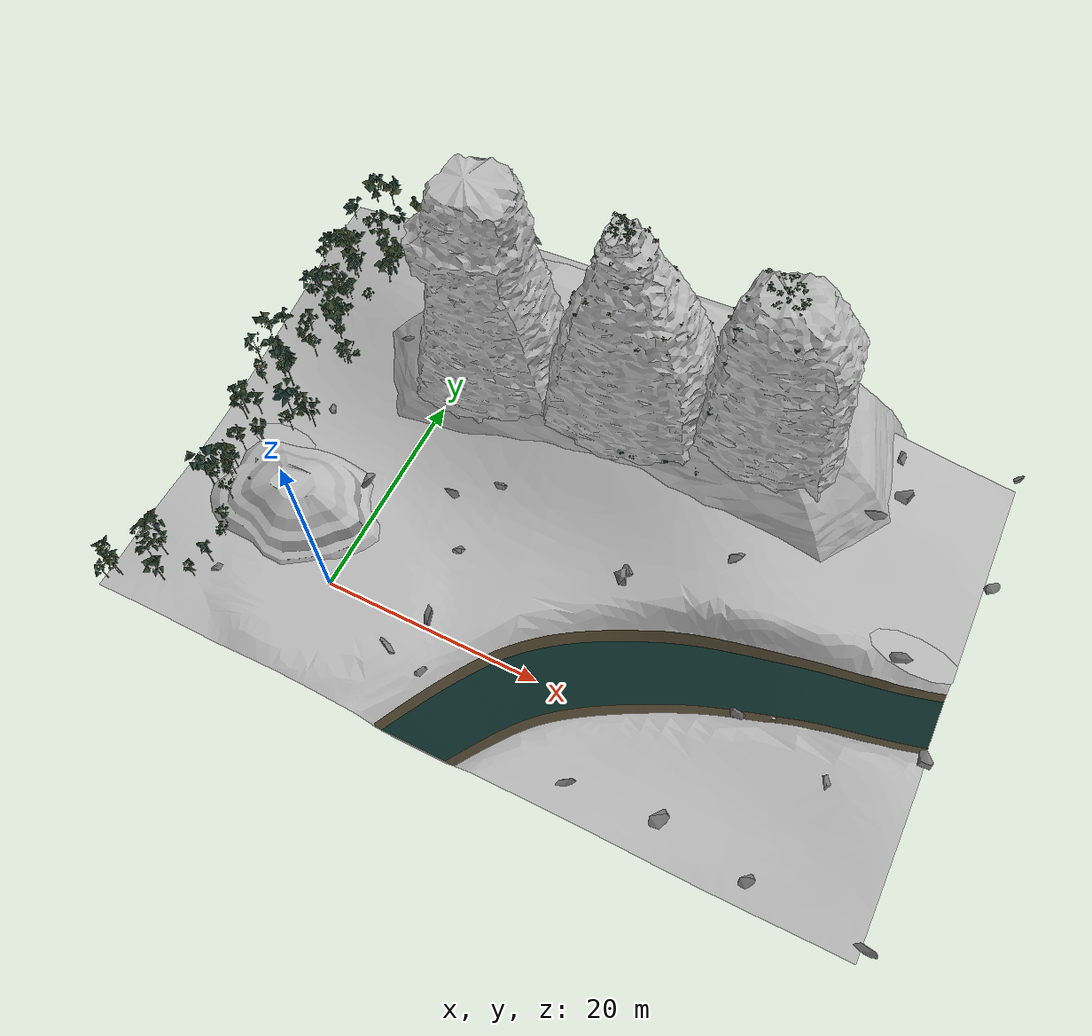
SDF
<?xml version='1.0' encoding='utf-8'?>
<sdf version="1.8">
  <model name="blue_mountains">
    <static>true</static>
    <link name="landscape_0">
      <visual name="visual">
        <geometry>
          <mesh>
            <uri>model://blue_mountains/meshes/0000_jamison_valley_forest_terrain.dae</uri>
          </mesh>
        </geometry>
        <cast_shadows>false</cast_shadows>
      </visual>
      <collision name="collision">
        <geometry>
          <mesh>
            <uri>model://blue_mountains/meshes/0000_jamison_valley_forest_terrain.dae</uri>
          </mesh>
        </geometry>
      </collision>
    </link>
    <link name="landscape_1">
      <visual name="visual">
        <geometry>
          <mesh>
            <uri>model://blue_mountains/meshes/0001_01_meehni_irregular_stepped_summit.dae</uri>
          </mesh>
        </geometry>
        <cast_shadows>false</cast_shadows>
      </visual>
      <collision name="collision">
        <geometry>
          <mesh>
            <uri>model://blue_mountains/meshes/0001_01_meehni_irregular_stepped_summit.dae</uri>
          </mesh>
        </geometry>
      </collision>
    </link>
    <link name="landscape_2">
      <visual name="visual">
        <geometry>
          <mesh>
            <uri>model://blue_mountains/meshes/0002_02_wimlah_tapered_fractured_buttress.dae</uri>
          </mesh>
        </geometry>
        <cast_shadows>false</cast_shadows>
      </visual>
      <collision name="collision">
        <geometry>
          <mesh>
            <uri>model://blue_mountains/meshes/0002_02_wimlah_tapered_fractured_buttress.dae</uri>
          </mesh>
        </geometry>
      </collision>
    </link>
    <link name="landscape_3">
      <visual name="visual">
        <geometry>
          <mesh>
            <uri>model://blue_mountains/meshes/0003_03_gunnedoo_broad_weathered_crown.dae</uri>
          </mesh>
        </geometry>
        <cast_shadows>false</cast_shadows>
      </visual>
      <collision name="collision">
        <geometry>
          <mesh>
            <uri>model://blue_mountains/meshes/0003_03_gunnedoo_broad_weathered_crown.dae</uri>
          </mesh>
        </geometry>
      </collision>
    </link>
    <link name="landscape_4">
      <visual name="visual">
        <geometry>
          <mesh>
            <uri>model://blue_mountains/meshes/0004_continuous_sandstone_spur.dae</uri>
          </mesh>
        </geometry>
        <cast_shadows>false</cast_shadows>
      </visual>
      <collision name="collision">
        <geometry>
          <mesh>
            <uri>model://blue_mountains/meshes/0004_continuous_sandstone_spur.dae</uri>
          </mesh>
        </geometry>
      </collision>
    </link>
    <link name="forest_18_21">
      <collision name="tree_5_trunk">
        <pose>-11.00735 13.69356 0.98007 0 0 1.931423</pose>
        <geometry>
          <cylinder>
            <radius>0.0527128</radius>
            <length>3.376789</length>
          </cylinder>
        </geometry>
      </collision>
      <collision name="plant_5_crown_0">
        <pose>-10.99991 13.67383 -0.7083244 0 0 1.931423</pose>
        <geometry>
          <mesh>
            <uri>model://blue_mountains/meshes/canopy_0_0.dae</uri>
            <scale>0.2108512 0.2108512 0.2490363</scale>
          </mesh>
        </geometry>
      </collision>
      <collision name="plant_5_crown_1">
        <pose>-10.99991 13.67383 -0.7083244 0 0 1.931423</pose>
        <geometry>
          <mesh>
            <uri>model://blue_mountains/meshes/canopy_0_1.dae</uri>
            <scale>0.2108512 0.2108512 0.2490363</scale>
          </mesh>
        </geometry>
      </collision>
      <collision name="tree_11_trunk">
        <pose>-16.63338 17.70447 1.323882 0 0 1.766553</pose>
        <geometry>
          <cylinder>
            <radius>0.04915057</radius>
            <length>2.743409</length>
          </cylinder>
        </geometry>
      </collision>
      <collision name="plant_11_crown_0">
        <pose>-16.62955 17.68518 -0.04782271 0 0 1.766553</pose>
        <geometry>
          <mesh>
            <uri>model://blue_mountains/meshes/canopy_4_0.dae</uri>
            <scale>0.1966023 0.1966023 0.2044297</scale>
          </mesh>
        </geometry>
      </collision>
      <collision name="plant_11_crown_1">
        <pose>-16.62955 17.68518 -0.04782271 0 0 1.766553</pose>
        <geometry>
          <mesh>
            <uri>model://blue_mountains/meshes/canopy_4_1.dae</uri>
            <scale>0.1966023 0.1966023 0.2044297</scale>
          </mesh>
        </geometry>
      </collision>
      <collision name="tree_13_trunk">
        <pose>-12.75313 13.44406 1.270675 0 0 -1.84723</pose>
        <geometry>
          <cylinder>
            <radius>0.07301863</radius>
            <length>4.077318</length>
          </cylinder>
        </geometry>
      </collision>
      <collision name="plant_13_crown_0">
        <pose>-12.74516 13.47215 -0.7679834 0 0 -1.84723</pose>
        <geometry>
          <mesh>
            <uri>model://blue_mountains/meshes/canopy_4_0.dae</uri>
            <scale>0.2920745 0.2920745 0.3038282</scale>
          </mesh>
        </geometry>
      </collision>
      <collision name="plant_13_crown_1">
        <pose>-12.74516 13.47215 -0.7679834 0 0 -1.84723</pose>
        <geometry>
          <mesh>
            <uri>model://blue_mountains/meshes/canopy_4_1.dae</uri>
            <scale>0.2920745 0.2920745 0.3038282</scale>
          </mesh>
        </geometry>
      </collision>
      <collision name="tree_22_trunk">
        <pose>-15.59381 16.658 1.376622 0 0 -0.1817148</pose>
        <geometry>
          <cylinder>
            <radius>0.05085616</radius>
            <length>3.163726</length>
          </cylinder>
        </geometry>
      </collision>
      <collision name="plant_22_crown_0">
        <pose>-15.61381 16.66167 -0.2052405 0 0 -0.1817148</pose>
        <geometry>
          <mesh>
            <uri>model://blue_mountains/meshes/canopy_0_0.dae</uri>
            <scale>0.2034246 0.2034246 0.233323</scale>
          </mesh>
        </geometry>
      </collision>
      <collision name="plant_22_crown_1">
        <pose>-15.61381 16.66167 -0.2052405 0 0 -0.1817148</pose>
        <geometry>
          <mesh>
            <uri>model://blue_mountains/meshes/canopy_0_1.dae</uri>
            <scale>0.2034246 0.2034246 0.233323</scale>
          </mesh>
        </geometry>
      </collision>
      <collision name="tree_100_trunk">
        <pose>-13.5845 19.50853 1.972437 0 0 1.797339</pose>
        <geometry>
          <cylinder>
            <radius>0.04786842</radius>
            <length>2.822321</length>
          </cylinder>
        </geometry>
      </collision>
      <collision name="plant_100_crown_0">
        <pose>-13.5802 19.48987 0.5612764 0 0 1.797339</pose>
        <geometry>
          <mesh>
            <uri>model://blue_mountains/meshes/canopy_5_0.dae</uri>
            <scale>0.1914737 0.1914737 0.2121385</scale>
          </mesh>
        </geometry>
      </collision>
      <collision name="plant_100_crown_1">
        <pose>-13.5802 19.48987 0.5612764 0 0 1.797339</pose>
        <geometry>
          <mesh>
            <uri>model://blue_mountains/meshes/canopy_5_1.dae</uri>
            <scale>0.1914737 0.1914737 0.2121385</scale>
          </mesh>
        </geometry>
      </collision>
      <collision name="tree_114_trunk">
        <pose>-14.27402 16.0746 1.862754 0 0 1.929567</pose>
        <geometry>
          <cylinder>
            <radius>0.07051298</radius>
            <length>4.326829</length>
          </cylinder>
        </geometry>
      </collision>
      <collision name="plant_114_crown_0">
        <pose>-14.26411 16.04819 -0.3006608 0 0 1.929567</pose>
        <geometry>
          <mesh>
            <uri>model://blue_mountains/meshes/canopy_4_0.dae</uri>
            <scale>0.2820519 0.2820519 0.3224209</scale>
          </mesh>
        </geometry>
      </collision>
      <collision name="plant_114_crown_1">
        <pose>-14.26411 16.04819 -0.3006608 0 0 1.929567</pose>
        <geometry>
          <mesh>
            <uri>model://blue_mountains/meshes/canopy_4_1.dae</uri>
            <scale>0.2820519 0.2820519 0.3224209</scale>
          </mesh>
        </geometry>
      </collision>
      <collision name="tree_118_trunk">
        <pose>-18.02493 16.63118 1.625535 0 0 -1.044839</pose>
        <geometry>
          <cylinder>
            <radius>0.07135749</radius>
            <length>3.844661</length>
          </cylinder>
        </geometry>
      </collision>
      <collision name="plant_118_crown_0">
        <pose>-18.03926 16.65586 -0.2967958 0 0 -1.044839</pose>
        <geometry>
          <mesh>
            <uri>model://blue_mountains/meshes/canopy_2_0.dae</uri>
            <scale>0.2854299 0.2854299 0.2828724</scale>
          </mesh>
        </geometry>
      </collision>
      <collision name="plant_118_crown_1">
        <pose>-18.03926 16.65586 -0.2967958 0 0 -1.044839</pose>
        <geometry>
          <mesh>
            <uri>model://blue_mountains/meshes/canopy_2_1.dae</uri>
            <scale>0.2854299 0.2854299 0.2828724</scale>
          </mesh>
        </geometry>
      </collision>
      <collision name="tree_123_trunk">
        <pose>-15.54227 17.51189 1.175307 0 0 -0.7858084</pose>
        <geometry>
          <cylinder>
            <radius>0.04894487</radius>
            <length>2.409598</length>
          </cylinder>
        </geometry>
      </collision>
      <collision name="plant_123_crown_0">
        <pose>-15.5561 17.52574 -0.02949238 0 0 -0.7858084</pose>
        <geometry>
          <mesh>
            <uri>model://blue_mountains/meshes/canopy_6_0.dae</uri>
            <scale>0.1957795 0.1957795 0.1776167</scale>
          </mesh>
        </geometry>
      </collision>
      <collision name="plant_123_crown_1">
        <pose>-15.5561 17.52574 -0.02949238 0 0 -0.7858084</pose>
        <geometry>
          <mesh>
            <uri>model://blue_mountains/meshes/canopy_6_1.dae</uri>
            <scale>0.1957795 0.1957795 0.1776167</scale>
          </mesh>
        </geometry>
      </collision>
      <collision name="tree_130_trunk">
        <pose>-16.96412 17.9592 1.435838 0 0 -2.331105</pose>
        <geometry>
          <cylinder>
            <radius>0.04494899</radius>
            <length>2.894845</length>
          </cylinder>
        </geometry>
      </collision>
      <collision name="plant_130_crown_0">
        <pose>-16.95173 17.97223 -0.01158476 0 0 -2.331105</pose>
        <geometry>
          <mesh>
            <uri>model://blue_mountains/meshes/canopy_3_0.dae</uri>
            <scale>0.179796 0.179796 0.2152183</scale>
          </mesh>
        </geometry>
      </collision>
      <collision name="plant_130_crown_1">
        <pose>-16.95173 17.97223 -0.01158476 0 0 -2.331105</pose>
        <geometry>
          <mesh>
            <uri>model://blue_mountains/meshes/canopy_3_1.dae</uri>
            <scale>0.179796 0.179796 0.2152183</scale>
          </mesh>
        </geometry>
      </collision>
      <collision name="tree_199_trunk">
        <pose>-14.88543 16.10718 1.106355 0 0 -2.332534</pose>
        <geometry>
          <cylinder>
            <radius>0.04410965</radius>
            <length>2.805242</length>
          </cylinder>
        </geometry>
      </collision>
      <collision name="plant_199_crown_0">
        <pose>-14.87326 16.11995 -0.2962656 0 0 -2.332534</pose>
        <geometry>
          <mesh>
            <uri>model://blue_mountains/meshes/canopy_5_0.dae</uri>
            <scale>0.1764386 0.1764386 0.2108548</scale>
          </mesh>
        </geometry>
      </collision>
      <collision name="plant_199_crown_1">
        <pose>-14.87326 16.11995 -0.2962656 0 0 -2.332534</pose>
        <geometry>
          <mesh>
            <uri>model://blue_mountains/meshes/canopy_5_1.dae</uri>
            <scale>0.1764386 0.1764386 0.2108548</scale>
          </mesh>
        </geometry>
      </collision>
      <collision name="tree_253_trunk">
        <pose>-14.05662 10.01314 -0.1940399 0 0 -1.157318</pose>
        <geometry>
          <cylinder>
            <radius>0.04042882</radius>
            <length>2.143582</length>
          </cylinder>
        </geometry>
      </collision>
      <collision name="plant_253_crown_0">
        <pose>-14.06312 10.02795 -1.265831 0 0 -1.157318</pose>
        <geometry>
          <mesh>
            <uri>model://blue_mountains/meshes/canopy_4_0.dae</uri>
            <scale>0.1617153 0.1617153 0.1597326</scale>
          </mesh>
        </geometry>
      </collision>
      <collision name="plant_253_crown_1">
        <pose>-14.06312 10.02795 -1.265831 0 0 -1.157318</pose>
        <geometry>
          <mesh>
            <uri>model://blue_mountains/meshes/canopy_4_1.dae</uri>
            <scale>0.1617153 0.1617153 0.1597326</scale>
          </mesh>
        </geometry>
      </collision>
      <collision name="tree_274_trunk">
        <pose>-15.56105 12.33841 0.4961344 0 0 0.3857232</pose>
        <geometry>
          <cylinder>
            <radius>0.05898833</radius>
            <length>2.87374</length>
          </cylinder>
        </geometry>
      </collision>
      <collision name="plant_274_crown_0">
        <pose>-15.58292 12.32953 -0.9407356 0 0 0.3857232</pose>
        <geometry>
          <mesh>
            <uri>model://blue_mountains/meshes/canopy_7_0.dae</uri>
            <scale>0.2359533 0.2359533 0.216066</scale>
          </mesh>
        </geometry>
      </collision>
      <collision name="plant_274_crown_1">
        <pose>-15.58292 12.32953 -0.9407356 0 0 0.3857232</pose>
        <geometry>
          <mesh>
            <uri>model://blue_mountains/meshes/canopy_7_1.dae</uri>
            <scale>0.2359533 0.2359533 0.216066</scale>
          </mesh>
        </geometry>
      </collision>
      <collision name="tree_277_trunk">
        <pose>-10.09732 13.25678 0.8020996 0 0 -0.09953434</pose>
        <geometry>
          <cylinder>
            <radius>0.06551166</radius>
            <length>3.086385</length>
          </cylinder>
        </geometry>
      </collision>
      <collision name="plant_277_crown_0">
        <pose>-10.12339 13.25938 -0.7410932 0 0 -0.09953434</pose>
        <geometry>
          <mesh>
            <uri>model://blue_mountains/meshes/canopy_2_0.dae</uri>
            <scale>0.2620466 0.2620466 0.227082</scale>
          </mesh>
        </geometry>
      </collision>
      <collision name="plant_277_crown_1">
        <pose>-10.12339 13.25938 -0.7410932 0 0 -0.09953434</pose>
        <geometry>
          <mesh>
            <uri>model://blue_mountains/meshes/canopy_2_1.dae</uri>
            <scale>0.2620466 0.2620466 0.227082</scale>
          </mesh>
        </geometry>
      </collision>
      <collision name="tree_339_trunk">
        <pose>-18.12704 19.02719 2.063982 0 0 0.9307255</pose>
        <geometry>
          <cylinder>
            <radius>0.06879348</radius>
            <length>3.946659</length>
          </cylinder>
        </geometry>
      </collision>
      <collision name="plant_339_crown_0">
        <pose>-18.14347 19.00512 0.0906527 0 0 0.9307255</pose>
        <geometry>
          <mesh>
            <uri>model://blue_mountains/meshes/canopy_8_0.dae</uri>
            <scale>0.2751739 0.2751739 0.2936668</scale>
          </mesh>
        </geometry>
      </collision>
      <collision name="plant_339_crown_1">
        <pose>-18.14347 19.00512 0.0906527 0 0 0.9307255</pose>
        <geometry>
          <mesh>
            <uri>model://blue_mountains/meshes/canopy_8_1.dae</uri>
            <scale>0.2751739 0.2751739 0.2936668</scale>
          </mesh>
        </geometry>
      </collision>
      <collision name="tree_340_trunk">
        <pose>-16.79424 11.82724 0.8433991 0 0 -1.105317</pose>
        <geometry>
          <cylinder>
            <radius>0.06814528</radius>
            <length>3.702179</length>
          </cylinder>
        </geometry>
      </collision>
      <collision name="plant_340_crown_0">
        <pose>-16.80647 11.85159 -1.00769 0 0 -1.105317</pose>
        <geometry>
          <mesh>
            <uri>model://blue_mountains/meshes/canopy_1_0.dae</uri>
            <scale>0.2725811 0.2725811 0.2734459</scale>
          </mesh>
        </geometry>
      </collision>
      <collision name="plant_340_crown_1">
        <pose>-16.80647 11.85159 -1.00769 0 0 -1.105317</pose>
        <geometry>
          <mesh>
            <uri>model://blue_mountains/meshes/canopy_1_1.dae</uri>
            <scale>0.2725811 0.2725811 0.2734459</scale>
          </mesh>
        </geometry>
      </collision>
      <collision name="tree_392_trunk">
        <pose>-16.91099 15.29932 0.8320815 0 0 -3.098106</pose>
        <geometry>
          <cylinder>
            <radius>0.05667524</radius>
            <length>2.626257</length>
          </cylinder>
        </geometry>
      </collision>
      <collision name="plant_392_crown_0">
        <pose>-16.88834 15.3003 -0.4810469 0 0 -3.098106</pose>
        <geometry>
          <mesh>
            <uri>model://blue_mountains/meshes/canopy_8_0.dae</uri>
            <scale>0.226701 0.226701 0.195417</scale>
          </mesh>
        </geometry>
      </collision>
      <collision name="plant_392_crown_1">
        <pose>-16.88834 15.3003 -0.4810469 0 0 -3.098106</pose>
        <geometry>
          <mesh>
            <uri>model://blue_mountains/meshes/canopy_8_1.dae</uri>
            <scale>0.226701 0.226701 0.195417</scale>
          </mesh>
        </geometry>
      </collision>
      <collision name="tree_397_trunk">
        <pose>-10.64215 19.94457 2.070035 0 0 -1.712195</pose>
        <geometry>
          <cylinder>
            <radius>0.0432395</radius>
            <length>2.207157</length>
          </cylinder>
        </geometry>
      </collision>
      <collision name="plant_397_crown_0">
        <pose>-10.63971 19.96169 0.9664569 0 0 -1.712195</pose>
        <geometry>
          <mesh>
            <uri>model://blue_mountains/meshes/canopy_5_0.dae</uri>
            <scale>0.172958 0.172958 0.1659</scale>
          </mesh>
        </geometry>
      </collision>
      <collision name="plant_397_crown_1">
        <pose>-10.63971 19.96169 0.9664569 0 0 -1.712195</pose>
        <geometry>
          <mesh>
            <uri>model://blue_mountains/meshes/canopy_5_1.dae</uri>
            <scale>0.172958 0.172958 0.1659</scale>
          </mesh>
        </geometry>
      </collision>
      <collision name="tree_406_trunk">
        <pose>-16.53369 11.26642 0.4432319 0 0 -0.08879216</pose>
        <geometry>
          <cylinder>
            <radius>0.06109959</radius>
            <length>3.02687</length>
          </cylinder>
        </geometry>
      </collision>
      <collision name="plant_406_crown_0">
        <pose>-16.55803 11.26859 -1.070203 0 0 -0.08879216</pose>
        <geometry>
          <mesh>
            <uri>model://blue_mountains/meshes/canopy_1_0.dae</uri>
            <scale>0.2443984 0.2443984 0.2235671</scale>
          </mesh>
        </geometry>
      </collision>
      <collision name="plant_406_crown_1">
        <pose>-16.55803 11.26859 -1.070203 0 0 -0.08879216</pose>
        <geometry>
          <mesh>
            <uri>model://blue_mountains/meshes/canopy_1_1.dae</uri>
            <scale>0.2443984 0.2443984 0.2235671</scale>
          </mesh>
        </geometry>
      </collision>
      <collision name="tree_424_trunk">
        <pose>-12.38895 14.22952 0.8773811 0 0 -1.31463</pose>
        <geometry>
          <cylinder>
            <radius>0.04897507</radius>
            <length>3.026367</length>
          </cylinder>
        </geometry>
      </collision>
      <collision name="plant_424_crown_0">
        <pose>-12.39392 14.24847 -0.6358025 0 0 -1.31463</pose>
        <geometry>
          <mesh>
            <uri>model://blue_mountains/meshes/canopy_6_0.dae</uri>
            <scale>0.1959003 0.1959003 0.2230801</scale>
          </mesh>
        </geometry>
      </collision>
      <collision name="plant_424_crown_1">
        <pose>-12.39392 14.24847 -0.6358025 0 0 -1.31463</pose>
        <geometry>
          <mesh>
            <uri>model://blue_mountains/meshes/canopy_6_1.dae</uri>
            <scale>0.1959003 0.1959003 0.2230801</scale>
          </mesh>
        </geometry>
      </collision>
      <collision name="tree_425_trunk">
        <pose>-11.83638 12.0439 0.3670479 0 0 -0.5802114</pose>
        <geometry>
          <cylinder>
            <radius>0.05030619</radius>
            <length>2.597305</length>
          </cylinder>
        </geometry>
      </collision>
      <collision name="plant_425_crown_0">
        <pose>-11.85321 12.05493 -0.9316049 0 0 -0.5802114</pose>
        <geometry>
          <mesh>
            <uri>model://blue_mountains/meshes/canopy_5_0.dae</uri>
            <scale>0.2012248 0.2012248 0.1952253</scale>
          </mesh>
        </geometry>
      </collision>
      <collision name="plant_425_crown_1">
        <pose>-11.85321 12.05493 -0.9316049 0 0 -0.5802114</pose>
        <geometry>
          <mesh>
            <uri>model://blue_mountains/meshes/canopy_5_1.dae</uri>
            <scale>0.2012248 0.2012248 0.1952253</scale>
          </mesh>
        </geometry>
      </collision>
      <visual name="forest_visual">
        <geometry>
          <mesh>
            <uri>model://blue_mountains/meshes/forest_18_21.dae</uri>
          </mesh>
        </geometry>
        <cast_shadows>false</cast_shadows>
      </visual>
    </link>
    <link name="forest_18_22">
      <collision name="tree_6_trunk">
        <pose>-13.23552 23.16154 3.227167 0 0 1.086585</pose>
        <geometry>
          <cylinder>
            <radius>0.06129941</radius>
            <length>3.146669</length>
          </cylinder>
        </geometry>
      </collision>
      <collision name="plant_6_crown_0">
        <pose>-13.24693 23.13984 1.653832 0 0 1.086585</pose>
        <geometry>
          <mesh>
            <uri>model://blue_mountains/meshes/canopy_1_0.dae</uri>
            <scale>0.2451976 0.2451976 0.2324156</scale>
          </mesh>
        </geometry>
      </collision>
      <collision name="plant_6_crown_1">
        <pose>-13.24693 23.13984 1.653832 0 0 1.086585</pose>
        <geometry>
          <mesh>
            <uri>model://blue_mountains/meshes/canopy_1_1.dae</uri>
            <scale>0.2451976 0.2451976 0.2324156</scale>
          </mesh>
        </geometry>
      </collision>
      <collision name="tree_35_trunk">
        <pose>-13.26212 22.8935 3.58852 0 0 -2.274427</pose>
        <geometry>
          <cylinder>
            <radius>0.06512813</radius>
            <length>4.001968</length>
          </cylinder>
        </geometry>
      </collision>
      <collision name="plant_35_crown_0">
        <pose>-13.24526 22.91337 1.587536 0 0 -2.274427</pose>
        <geometry>
          <mesh>
            <uri>model://blue_mountains/meshes/canopy_2_0.dae</uri>
            <scale>0.2605125 0.2605125 0.2944463</scale>
          </mesh>
        </geometry>
      </collision>
      <collision name="plant_35_crown_1">
        <pose>-13.24526 22.91337 1.587536 0 0 -2.274427</pose>
        <geometry>
          <mesh>
            <uri>model://blue_mountains/meshes/canopy_2_1.dae</uri>
            <scale>0.2605125 0.2605125 0.2944463</scale>
          </mesh>
        </geometry>
      </collision>
      <collision name="tree_103_trunk">
        <pose>-10.05428 20.07703 2.745684 0 0 -1.383348</pose>
        <geometry>
          <cylinder>
            <radius>0.07215569</radius>
            <length>3.350216</length>
          </cylinder>
        </geometry>
      </collision>
      <collision name="plant_103_crown_0">
        <pose>-10.05965 20.10539 1.070576 0 0 -1.383348</pose>
        <geometry>
          <mesh>
            <uri>model://blue_mountains/meshes/canopy_2_0.dae</uri>
            <scale>0.2886228 0.2886228 0.2464934</scale>
          </mesh>
        </geometry>
      </collision>
      <collision name="plant_103_crown_1">
        <pose>-10.05965 20.10539 1.070576 0 0 -1.383348</pose>
        <geometry>
          <mesh>
            <uri>model://blue_mountains/meshes/canopy_2_1.dae</uri>
            <scale>0.2886228 0.2886228 0.2464934</scale>
          </mesh>
        </geometry>
      </collision>
      <collision name="tree_128_trunk">
        <pose>-13.99477 28.87506 4.410375 0 0 -2.361214</pose>
        <geometry>
          <cylinder>
            <radius>0.05561356</radius>
            <length>3.016801</length>
          </cylinder>
        </geometry>
      </collision>
      <collision name="plant_128_crown_0">
        <pose>-13.97896 28.89071 2.901975 0 0 -2.361214</pose>
        <geometry>
          <mesh>
            <uri>model://blue_mountains/meshes/canopy_4_0.dae</uri>
            <scale>0.2224543 0.2224543 0.224802</scale>
          </mesh>
        </geometry>
      </collision>
      <collision name="plant_128_crown_1">
        <pose>-13.97896 28.89071 2.901975 0 0 -2.361214</pose>
        <geometry>
          <mesh>
            <uri>model://blue_mountains/meshes/canopy_4_1.dae</uri>
            <scale>0.2224543 0.2224543 0.224802</scale>
          </mesh>
        </geometry>
      </collision>
      <collision name="tree_166_trunk">
        <pose>-14.25775 28.41808 4.947151 0 0 0.2555893</pose>
        <geometry>
          <cylinder>
            <radius>0.0715662</radius>
            <length>4.432418</length>
          </cylinder>
        </geometry>
      </collision>
      <collision name="plant_166_crown_0">
        <pose>-14.28545 28.41084 2.730942 0 0 0.2555893</pose>
        <geometry>
          <mesh>
            <uri>model://blue_mountains/meshes/canopy_8_0.dae</uri>
            <scale>0.2862648 0.2862648 0.3298116</scale>
          </mesh>
        </geometry>
      </collision>
      <collision name="plant_166_crown_1">
        <pose>-14.28545 28.41084 2.730942 0 0 0.2555893</pose>
        <geometry>
          <mesh>
            <uri>model://blue_mountains/meshes/canopy_8_1.dae</uri>
            <scale>0.2862648 0.2862648 0.3298116</scale>
          </mesh>
        </geometry>
      </collision>
      <collision name="tree_168_trunk">
        <pose>-13.32814 23.32386 3.546753 0 0 -2.117352</pose>
        <geometry>
          <cylinder>
            <radius>0.06931265</radius>
            <length>3.68923</length>
          </cylinder>
        </geometry>
      </collision>
      <collision name="plant_168_crown_0">
        <pose>-13.31373 23.34755 1.702138 0 0 -2.117352</pose>
        <geometry>
          <mesh>
            <uri>model://blue_mountains/meshes/canopy_0_0.dae</uri>
            <scale>0.2772506 0.2772506 0.2720786</scale>
          </mesh>
        </geometry>
      </collision>
      <collision name="plant_168_crown_1">
        <pose>-13.31373 23.34755 1.702138 0 0 -2.117352</pose>
        <geometry>
          <mesh>
            <uri>model://blue_mountains/meshes/canopy_0_1.dae</uri>
            <scale>0.2772506 0.2772506 0.2720786</scale>
          </mesh>
        </geometry>
      </collision>
      <collision name="tree_179_trunk">
        <pose>-17.77202 26.22557 2.968533 0 0 -3.065258</pose>
        <geometry>
          <cylinder>
            <radius>0.06453053</radius>
            <length>3.002123</length>
          </cylinder>
        </geometry>
      </collision>
      <collision name="plant_179_crown_0">
        <pose>-17.74629 26.22754 1.467471 0 0 -3.065258</pose>
        <geometry>
          <mesh>
            <uri>model://blue_mountains/meshes/canopy_4_0.dae</uri>
            <scale>0.2581221 0.2581221 0.2237082</scale>
          </mesh>
        </geometry>
      </collision>
      <collision name="plant_179_crown_1">
        <pose>-17.74629 26.22754 1.467471 0 0 -3.065258</pose>
        <geometry>
          <mesh>
            <uri>model://blue_mountains/meshes/canopy_4_1.dae</uri>
            <scale>0.2581221 0.2581221 0.2237082</scale>
          </mesh>
        </geometry>
      </collision>
      <collision name="tree_200_trunk">
        <pose>-10.23324 28.53306 5.850224 0 0 0.6221859</pose>
        <geometry>
          <cylinder>
            <radius>0.06943553</radius>
            <length>4.177232</length>
          </cylinder>
        </geometry>
      </collision>
      <collision name="plant_200_crown_0">
        <pose>-10.25581 28.51687 3.761608 0 0 0.6221859</pose>
        <geometry>
          <mesh>
            <uri>model://blue_mountains/meshes/canopy_3_0.dae</uri>
            <scale>0.2777421 0.2777421 0.3105578</scale>
          </mesh>
        </geometry>
      </collision>
      <collision name="plant_200_crown_1">
        <pose>-10.25581 28.51687 3.761608 0 0 0.6221859</pose>
        <geometry>
          <mesh>
            <uri>model://blue_mountains/meshes/canopy_3_1.dae</uri>
            <scale>0.2777421 0.2777421 0.3105578</scale>
          </mesh>
        </geometry>
      </collision>
      <collision name="tree_247_trunk">
        <pose>-18.1595 21.05126 2.18634 0 0 -0.7197788</pose>
        <geometry>
          <cylinder>
            <radius>0.05604642</radius>
            <length>3.476928</length>
          </cylinder>
        </geometry>
      </collision>
      <collision name="plant_247_crown_0">
        <pose>-18.17636 21.06603 0.4478757 0 0 -0.7197788</pose>
        <geometry>
          <mesh>
            <uri>model://blue_mountains/meshes/canopy_6_0.dae</uri>
            <scale>0.2241857 0.2241857 0.2562919</scale>
          </mesh>
        </geometry>
      </collision>
      <collision name="plant_247_crown_1">
        <pose>-18.17636 21.06603 0.4478757 0 0 -0.7197788</pose>
        <geometry>
          <mesh>
            <uri>model://blue_mountains/meshes/canopy_6_1.dae</uri>
            <scale>0.2241857 0.2241857 0.2562919</scale>
          </mesh>
        </geometry>
      </collision>
      <collision name="tree_249_trunk">
        <pose>-14.32852 26.02061 3.662353 0 0 0.9239057</pose>
        <geometry>
          <cylinder>
            <radius>0.05882859</radius>
            <length>2.962593</length>
          </cylinder>
        </geometry>
      </collision>
      <collision name="plant_249_crown_0">
        <pose>-14.34271 26.00183 2.181056 0 0 0.9239057</pose>
        <geometry>
          <mesh>
            <uri>model://blue_mountains/meshes/canopy_5_0.dae</uri>
            <scale>0.2353144 0.2353144 0.222682</scale>
          </mesh>
        </geometry>
      </collision>
      <collision name="plant_249_crown_1">
        <pose>-14.34271 26.00183 2.181056 0 0 0.9239057</pose>
        <geometry>
          <mesh>
            <uri>model://blue_mountains/meshes/canopy_5_1.dae</uri>
            <scale>0.2353144 0.2353144 0.222682</scale>
          </mesh>
        </geometry>
      </collision>
      <collision name="tree_255_trunk">
        <pose>-18.37329 28.99916 3.186844 0 0 -0.7816474</pose>
        <geometry>
          <cylinder>
            <radius>0.04322198</radius>
            <length>2.658526</length>
          </cylinder>
        </geometry>
      </collision>
      <collision name="plant_255_crown_0">
        <pose>-18.38556 29.01134 1.857581 0 0 -0.7816474</pose>
        <geometry>
          <mesh>
            <uri>model://blue_mountains/meshes/canopy_1_0.dae</uri>
            <scale>0.1728879 0.1728879 0.1963609</scale>
          </mesh>
        </geometry>
      </collision>
      <collision name="plant_255_crown_1">
        <pose>-18.38556 29.01134 1.857581 0 0 -0.7816474</pose>
        <geometry>
          <mesh>
            <uri>model://blue_mountains/meshes/canopy_1_1.dae</uri>
            <scale>0.1728879 0.1728879 0.1963609</scale>
          </mesh>
        </geometry>
      </collision>
      <collision name="tree_256_trunk">
        <pose>-13.75891 25.87571 4.315666 0 0 -3.019603</pose>
        <geometry>
          <cylinder>
            <radius>0.06227174</radius>
            <length>4.027971</length>
          </cylinder>
        </geometry>
      </collision>
      <collision name="plant_256_crown_0">
        <pose>-13.73419 25.87874 2.301681 0 0 -3.019603</pose>
        <geometry>
          <mesh>
            <uri>model://blue_mountains/meshes/canopy_2_0.dae</uri>
            <scale>0.249087 0.249087 0.2963595</scale>
          </mesh>
        </geometry>
      </collision>
      <collision name="plant_256_crown_1">
        <pose>-13.73419 25.87874 2.301681 0 0 -3.019603</pose>
        <geometry>
          <mesh>
            <uri>model://blue_mountains/meshes/canopy_2_1.dae</uri>
            <scale>0.249087 0.249087 0.2963595</scale>
          </mesh>
        </geometry>
      </collision>
      <collision name="tree_275_trunk">
        <pose>-10.60712 29.88631 5.468616 0 0 -0.6983031</pose>
        <geometry>
          <cylinder>
            <radius>0.0587657</radius>
            <length>3.139065</length>
          </cylinder>
        </geometry>
      </collision>
      <collision name="plant_275_crown_0">
        <pose>-10.62513 29.90143 3.899084 0 0 -0.6983031</pose>
        <geometry>
          <mesh>
            <uri>model://blue_mountains/meshes/canopy_0_0.dae</uri>
            <scale>0.2350628 0.2350628 0.2315043</scale>
          </mesh>
        </geometry>
      </collision>
      <collision name="plant_275_crown_1">
        <pose>-10.62513 29.90143 3.899084 0 0 -0.6983031</pose>
        <geometry>
          <mesh>
            <uri>model://blue_mountains/meshes/canopy_0_1.dae</uri>
            <scale>0.2350628 0.2350628 0.2315043</scale>
          </mesh>
        </geometry>
      </collision>
      <collision name="tree_289_trunk">
        <pose>-12.11327 21.89619 2.99883 0 0 1.424232</pose>
        <geometry>
          <cylinder>
            <radius>0.06164007</radius>
            <length>3.109202</length>
          </cylinder>
        </geometry>
      </collision>
      <collision name="plant_289_crown_0">
        <pose>-12.11687 21.8718 1.444229 0 0 1.424232</pose>
        <geometry>
          <mesh>
            <uri>model://blue_mountains/meshes/canopy_6_0.dae</uri>
            <scale>0.2465603 0.2465603 0.229186</scale>
          </mesh>
        </geometry>
      </collision>
      <collision name="plant_289_crown_1">
        <pose>-12.11687 21.8718 1.444229 0 0 1.424232</pose>
        <geometry>
          <mesh>
            <uri>model://blue_mountains/meshes/canopy_6_1.dae</uri>
            <scale>0.2465603 0.2465603 0.229186</scale>
          </mesh>
        </geometry>
      </collision>
      <collision name="tree_314_trunk">
        <pose>-11.24043 26.14399 4.020075 0 0 1.877041</pose>
        <geometry>
          <cylinder>
            <radius>0.03591868</radius>
            <length>2.111594</length>
          </cylinder>
        </geometry>
      </collision>
      <collision name="plant_314_crown_0">
        <pose>-11.2361 26.13029 2.964279 0 0 1.877041</pose>
        <geometry>
          <mesh>
            <uri>model://blue_mountains/meshes/canopy_0_0.dae</uri>
            <scale>0.1436747 0.1436747 0.1557288</scale>
          </mesh>
        </geometry>
      </collision>
      <collision name="plant_314_crown_1">
        <pose>-11.2361 26.13029 2.964279 0 0 1.877041</pose>
        <geometry>
          <mesh>
            <uri>model://blue_mountains/meshes/canopy_0_1.dae</uri>
            <scale>0.1436747 0.1436747 0.1557288</scale>
          </mesh>
        </geometry>
      </collision>
      <collision name="tree_322_trunk">
        <pose>-14.82544 25.12848 3.392789 0 0 0.565994</pose>
        <geometry>
          <cylinder>
            <radius>0.04916384</radius>
            <length>3.089352</length>
          </cylinder>
        </geometry>
      </collision>
      <collision name="plant_322_crown_0">
        <pose>-14.84204 25.11793 1.848113 0 0 0.565994</pose>
        <geometry>
          <mesh>
            <uri>model://blue_mountains/meshes/canopy_2_0.dae</uri>
            <scale>0.1966554 0.1966554 0.2273002</scale>
          </mesh>
        </geometry>
      </collision>
      <collision name="plant_322_crown_1">
        <pose>-14.84204 25.11793 1.848113 0 0 0.565994</pose>
        <geometry>
          <mesh>
            <uri>model://blue_mountains/meshes/canopy_2_1.dae</uri>
            <scale>0.1966554 0.1966554 0.2273002</scale>
          </mesh>
        </geometry>
      </collision>
      <collision name="tree_330_trunk">
        <pose>-14.75879 23.72706 2.710481 0 0 -1.455609</pose>
        <geometry>
          <cylinder>
            <radius>0.0422786</radius>
            <length>2.368268</length>
          </cylinder>
        </geometry>
      </collision>
      <collision name="plant_330_crown_0">
        <pose>-14.76074 23.74386 1.526347 0 0 -1.455609</pose>
        <geometry>
          <mesh>
            <uri>model://blue_mountains/meshes/canopy_7_0.dae</uri>
            <scale>0.1691144 0.1691144 0.1780614</scale>
          </mesh>
        </geometry>
      </collision>
      <collision name="plant_330_crown_1">
        <pose>-14.76074 23.74386 1.526347 0 0 -1.455609</pose>
        <geometry>
          <mesh>
            <uri>model://blue_mountains/meshes/canopy_7_1.dae</uri>
            <scale>0.1691144 0.1691144 0.1780614</scale>
          </mesh>
        </geometry>
      </collision>
      <collision name="tree_352_trunk">
        <pose>-17.24756 25.229 2.662511 0 0 -0.03826028</pose>
        <geometry>
          <cylinder>
            <radius>0.05256654</radius>
            <length>2.608206</length>
          </cylinder>
        </geometry>
      </collision>
      <collision name="plant_352_crown_0">
        <pose>-17.26857 25.22981 1.358408 0 0 -0.03826028</pose>
        <geometry>
          <mesh>
            <uri>model://blue_mountains/meshes/canopy_4_0.dae</uri>
            <scale>0.2102662 0.2102662 0.1943548</scale>
          </mesh>
        </geometry>
      </collision>
      <collision name="plant_352_crown_1">
        <pose>-17.26857 25.22981 1.358408 0 0 -0.03826028</pose>
        <geometry>
          <mesh>
            <uri>model://blue_mountains/meshes/canopy_4_1.dae</uri>
            <scale>0.2102662 0.2102662 0.1943548</scale>
          </mesh>
        </geometry>
      </collision>
      <collision name="tree_362_trunk">
        <pose>-16.1319 27.0542 3.4872 0 0 -0.783893</pose>
        <geometry>
          <cylinder>
            <radius>0.05922301</radius>
            <length>3.036693</length>
          </cylinder>
        </geometry>
      </collision>
      <collision name="plant_362_crown_0">
        <pose>-16.14867 27.07092 1.968853 0 0 -0.783893</pose>
        <geometry>
          <mesh>
            <uri>model://blue_mountains/meshes/canopy_8_0.dae</uri>
            <scale>0.2368921 0.2368921 0.2259572</scale>
          </mesh>
        </geometry>
      </collision>
      <collision name="plant_362_crown_1">
        <pose>-16.14867 27.07092 1.968853 0 0 -0.783893</pose>
        <geometry>
          <mesh>
            <uri>model://blue_mountains/meshes/canopy_8_1.dae</uri>
            <scale>0.2368921 0.2368921 0.2259572</scale>
          </mesh>
        </geometry>
      </collision>
      <collision name="tree_370_trunk">
        <pose>-16.8498 25.99246 3.526382 0 0 -1.049919</pose>
        <geometry>
          <cylinder>
            <radius>0.07256068</radius>
            <length>3.865302</length>
          </cylinder>
        </geometry>
      </collision>
      <collision name="plant_370_crown_0">
        <pose>-16.86424 26.01763 1.593731 0 0 -1.049919</pose>
        <geometry>
          <mesh>
            <uri>model://blue_mountains/meshes/canopy_6_0.dae</uri>
            <scale>0.2902427 0.2902427 0.2849198</scale>
          </mesh>
        </geometry>
      </collision>
      <collision name="plant_370_crown_1">
        <pose>-16.86424 26.01763 1.593731 0 0 -1.049919</pose>
        <geometry>
          <mesh>
            <uri>model://blue_mountains/meshes/canopy_6_1.dae</uri>
            <scale>0.2902427 0.2902427 0.2849198</scale>
          </mesh>
        </geometry>
      </collision>
      <collision name="tree_385_trunk">
        <pose>-13.85138 28.1992 4.746692 0 0 -2.56241</pose>
        <geometry>
          <cylinder>
            <radius>0.06180942</radius>
            <length>3.863184</length>
          </cylinder>
        </geometry>
      </collision>
      <collision name="plant_385_crown_0">
        <pose>-13.83069 28.21273 2.8151 0 0 -2.56241</pose>
        <geometry>
          <mesh>
            <uri>model://blue_mountains/meshes/canopy_6_0.dae</uri>
            <scale>0.2472377 0.2472377 0.2847637</scale>
          </mesh>
        </geometry>
      </collision>
      <collision name="plant_385_crown_1">
        <pose>-13.83069 28.21273 2.8151 0 0 -2.56241</pose>
        <geometry>
          <mesh>
            <uri>model://blue_mountains/meshes/canopy_6_1.dae</uri>
            <scale>0.2472377 0.2472377 0.2847637</scale>
          </mesh>
        </geometry>
      </collision>
      <collision name="tree_408_trunk">
        <pose>-12.63332 24.14122 3.316724 0 0 2.673759</pose>
        <geometry>
          <cylinder>
            <radius>0.04153046</radius>
            <length>2.490542</length>
          </cylinder>
        </geometry>
      </collision>
      <collision name="plant_408_crown_0">
        <pose>-12.6185 24.13373 2.071453 0 0 2.673759</pose>
        <geometry>
          <mesh>
            <uri>model://blue_mountains/meshes/canopy_4_0.dae</uri>
            <scale>0.1661218 0.1661218 0.1855869</scale>
          </mesh>
        </geometry>
      </collision>
      <collision name="plant_408_crown_1">
        <pose>-12.6185 24.13373 2.071453 0 0 2.673759</pose>
        <geometry>
          <mesh>
            <uri>model://blue_mountains/meshes/canopy_4_1.dae</uri>
            <scale>0.1661218 0.1661218 0.1855869</scale>
          </mesh>
        </geometry>
      </collision>
      <collision name="tree_413_trunk">
        <pose>-15.62846 20.70969 1.997009 0 0 1.148515</pose>
        <geometry>
          <cylinder>
            <radius>0.04581356</radius>
            <length>2.685189</length>
          </cylinder>
        </geometry>
      </collision>
      <collision name="plant_413_crown_0">
        <pose>-15.63597 20.69297 0.6544142 0 0 1.148515</pose>
        <geometry>
          <mesh>
            <uri>model://blue_mountains/meshes/canopy_2_0.dae</uri>
            <scale>0.1832542 0.1832542 0.1975638</scale>
          </mesh>
        </geometry>
      </collision>
      <collision name="plant_413_crown_1">
        <pose>-15.63597 20.69297 0.6544142 0 0 1.148515</pose>
        <geometry>
          <mesh>
            <uri>model://blue_mountains/meshes/canopy_2_1.dae</uri>
            <scale>0.1832542 0.1832542 0.1975638</scale>
          </mesh>
        </geometry>
      </collision>
      <collision name="tree_418_trunk">
        <pose>-15.51521 21.80905 2.662346 0 0 2.003514</pose>
        <geometry>
          <cylinder>
            <radius>0.05693726</radius>
            <length>3.479904</length>
          </cylinder>
        </geometry>
      </collision>
      <collision name="plant_418_crown_0">
        <pose>-15.50566 21.78838 0.9223938 0 0 2.003514</pose>
        <geometry>
          <mesh>
            <uri>model://blue_mountains/meshes/canopy_0_0.dae</uri>
            <scale>0.227749 0.227749 0.2566409</scale>
          </mesh>
        </geometry>
      </collision>
      <collision name="plant_418_crown_1">
        <pose>-15.50566 21.78838 0.9223938 0 0 2.003514</pose>
        <geometry>
          <mesh>
            <uri>model://blue_mountains/meshes/canopy_0_1.dae</uri>
            <scale>0.227749 0.227749 0.2566409</scale>
          </mesh>
        </geometry>
      </collision>
      <collision name="tree_465_trunk">
        <pose>-13.22512 25.87656 3.88338 0 0 -2.579789</pose>
        <geometry>
          <cylinder>
            <radius>0.04856139</radius>
            <length>2.898581</length>
          </cylinder>
        </geometry>
      </collision>
      <collision name="plant_465_crown_0">
        <pose>-13.20868 25.88691 2.434089 0 0 -2.579789</pose>
        <geometry>
          <mesh>
            <uri>model://blue_mountains/meshes/canopy_6_0.dae</uri>
            <scale>0.1942456 0.1942456 0.2136607</scale>
          </mesh>
        </geometry>
      </collision>
      <collision name="plant_465_crown_1">
        <pose>-13.20868 25.88691 2.434089 0 0 -2.579789</pose>
        <geometry>
          <mesh>
            <uri>model://blue_mountains/meshes/canopy_6_1.dae</uri>
            <scale>0.1942456 0.1942456 0.2136607</scale>
          </mesh>
        </geometry>
      </collision>
      <visual name="forest_visual">
        <geometry>
          <mesh>
            <uri>model://blue_mountains/meshes/forest_18_22.dae</uri>
          </mesh>
        </geometry>
        <cast_shadows>false</cast_shadows>
      </visual>
    </link>
    <link name="forest_24_21">
      <collision name="tree_7_trunk">
        <pose>46.3587 13.66385 0.07485123 0 0 -1.11061</pose>
        <geometry>
          <cylinder>
            <radius>0.05312383</radius>
            <length>2.820946</length>
          </cylinder>
        </geometry>
      </collision>
      <collision name="plant_7_crown_0">
        <pose>46.34926 13.68289 -1.335622 0 0 -1.11061</pose>
        <geometry>
          <mesh>
            <uri>model://blue_mountains/meshes/canopy_2_0.dae</uri>
            <scale>0.2124953 0.2124953 0.2075521</scale>
          </mesh>
        </geometry>
      </collision>
      <collision name="plant_7_crown_1">
        <pose>46.34926 13.68289 -1.335622 0 0 -1.11061</pose>
        <geometry>
          <mesh>
            <uri>model://blue_mountains/meshes/canopy_2_1.dae</uri>
            <scale>0.2124953 0.2124953 0.2075521</scale>
          </mesh>
        </geometry>
      </collision>
      <collision name="tree_8_trunk">
        <pose>46.19441 14.05483 0.102525 0 0 -0.1081408</pose>
        <geometry>
          <cylinder>
            <radius>0.04052509</radius>
            <length>2.385825</length>
          </cylinder>
        </geometry>
      </collision>
      <collision name="plant_8_crown_0">
        <pose>46.1783 14.05658 -1.090388 0 0 -0.1081408</pose>
        <geometry>
          <mesh>
            <uri>model://blue_mountains/meshes/canopy_3_0.dae</uri>
            <scale>0.1621003 0.1621003 0.177375</scale>
          </mesh>
        </geometry>
      </collision>
      <collision name="plant_8_crown_1">
        <pose>46.1783 14.05658 -1.090388 0 0 -0.1081408</pose>
        <geometry>
          <mesh>
            <uri>model://blue_mountains/meshes/canopy_3_1.dae</uri>
            <scale>0.1621003 0.1621003 0.177375</scale>
          </mesh>
        </geometry>
      </collision>
      <collision name="tree_54_trunk">
        <pose>45.72454 17.54652 1.240194 0 0 -1.332477</pose>
        <geometry>
          <cylinder>
            <radius>0.05559865</radius>
            <length>2.951463</length>
          </cylinder>
        </geometry>
      </collision>
      <collision name="plant_54_crown_0">
        <pose>45.71929 17.56813 -0.2355371 0 0 -1.332477</pose>
        <geometry>
          <mesh>
            <uri>model://blue_mountains/meshes/canopy_8_0.dae</uri>
            <scale>0.2223946 0.2223946 0.2196153</scale>
          </mesh>
        </geometry>
      </collision>
      <collision name="plant_54_crown_1">
        <pose>45.71929 17.56813 -0.2355371 0 0 -1.332477</pose>
        <geometry>
          <mesh>
            <uri>model://blue_mountains/meshes/canopy_8_1.dae</uri>
            <scale>0.2223946 0.2223946 0.2196153</scale>
          </mesh>
        </geometry>
      </collision>
      <collision name="tree_78_trunk">
        <pose>44.56624 13.89745 0.8586943 0 0 -2.135587</pose>
        <geometry>
          <cylinder>
            <radius>0.06837151</radius>
            <length>3.429785</length>
          </cylinder>
        </geometry>
      </collision>
      <collision name="plant_78_crown_0">
        <pose>44.58088 13.92055 -0.8561981 0 0 -2.135587</pose>
        <geometry>
          <mesh>
            <uri>model://blue_mountains/meshes/canopy_4_0.dae</uri>
            <scale>0.273486 0.273486 0.2555761</scale>
          </mesh>
        </geometry>
      </collision>
      <collision name="plant_78_crown_1">
        <pose>44.58088 13.92055 -0.8561981 0 0 -2.135587</pose>
        <geometry>
          <mesh>
            <uri>model://blue_mountains/meshes/canopy_4_1.dae</uri>
            <scale>0.273486 0.273486 0.2555761</scale>
          </mesh>
        </geometry>
      </collision>
      <collision name="tree_110_trunk">
        <pose>48.89273 16.79941 0.7739394 0 0 -3.105359</pose>
        <geometry>
          <cylinder>
            <radius>0.04096245</radius>
            <length>2.633923</length>
          </cylinder>
        </geometry>
      </collision>
      <collision name="plant_110_crown_0">
        <pose>48.9091 16.80001 -0.5430219 0 0 -3.105359</pose>
        <geometry>
          <mesh>
            <uri>model://blue_mountains/meshes/canopy_2_0.dae</uri>
            <scale>0.1638498 0.1638498 0.1937919</scale>
          </mesh>
        </geometry>
      </collision>
      <collision name="plant_110_crown_1">
        <pose>48.9091 16.80001 -0.5430219 0 0 -3.105359</pose>
        <geometry>
          <mesh>
            <uri>model://blue_mountains/meshes/canopy_2_1.dae</uri>
            <scale>0.1638498 0.1638498 0.1937919</scale>
          </mesh>
        </geometry>
      </collision>
      <collision name="tree_120_trunk">
        <pose>41.16937 18.17884 2.346918 0 0 2.017286</pose>
        <geometry>
          <cylinder>
            <radius>0.06500119</radius>
            <length>4.121044</length>
          </cylinder>
        </geometry>
      </collision>
      <collision name="plant_120_crown_0">
        <pose>41.1806 18.15539 0.2863963 0 0 2.017286</pose>
        <geometry>
          <mesh>
            <uri>model://blue_mountains/meshes/canopy_2_0.dae</uri>
            <scale>0.2600048 0.2600048 0.3032073</scale>
          </mesh>
        </geometry>
      </collision>
      <collision name="plant_120_crown_1">
        <pose>41.1806 18.15539 0.2863963 0 0 2.017286</pose>
        <geometry>
          <mesh>
            <uri>model://blue_mountains/meshes/canopy_2_1.dae</uri>
            <scale>0.2600048 0.2600048 0.3032073</scale>
          </mesh>
        </geometry>
      </collision>
      <collision name="tree_122_trunk">
        <pose>46.52799 15.7559 1.53373 0 0 1.848042</pose>
        <geometry>
          <cylinder>
            <radius>0.07008671</radius>
            <length>3.55835</length>
          </cylinder>
        </geometry>
      </collision>
      <collision name="plant_122_crown_0">
        <pose>46.53567 15.72894 -0.2454453 0 0 1.848042</pose>
        <geometry>
          <mesh>
            <uri>model://blue_mountains/meshes/canopy_7_0.dae</uri>
            <scale>0.2803468 0.2803468 0.2675394</scale>
          </mesh>
        </geometry>
      </collision>
      <collision name="plant_122_crown_1">
        <pose>46.53567 15.72894 -0.2454453 0 0 1.848042</pose>
        <geometry>
          <mesh>
            <uri>model://blue_mountains/meshes/canopy_7_1.dae</uri>
            <scale>0.2803468 0.2803468 0.2675394</scale>
          </mesh>
        </geometry>
      </collision>
      <collision name="tree_146_trunk">
        <pose>44.27746 17.31761 1.56526 0 0 -0.4271353</pose>
        <geometry>
          <cylinder>
            <radius>0.05739984</radius>
            <length>3.292759</length>
          </cylinder>
        </geometry>
      </collision>
      <collision name="plant_146_crown_0">
        <pose>44.25657 17.32712 -0.08111906 0 0 -0.4271353</pose>
        <geometry>
          <mesh>
            <uri>model://blue_mountains/meshes/canopy_0_0.dae</uri>
            <scale>0.2295993 0.2295993 0.2428391</scale>
          </mesh>
        </geometry>
      </collision>
      <collision name="plant_146_crown_1">
        <pose>44.25657 17.32712 -0.08111906 0 0 -0.4271353</pose>
        <geometry>
          <mesh>
            <uri>model://blue_mountains/meshes/canopy_0_1.dae</uri>
            <scale>0.2295993 0.2295993 0.2428391</scale>
          </mesh>
        </geometry>
      </collision>
      <collision name="tree_197_trunk">
        <pose>43.08169 16.14174 1.234888 0 0 0.88226</pose>
        <geometry>
          <cylinder>
            <radius>0.03907652</radius>
            <length>2.360494</length>
          </cylinder>
        </geometry>
      </collision>
      <collision name="plant_197_crown_0">
        <pose>43.07176 16.12967 0.05464149 0 0 0.88226</pose>
        <geometry>
          <mesh>
            <uri>model://blue_mountains/meshes/canopy_6_0.dae</uri>
            <scale>0.1563061 0.1563061 0.1739971</scale>
          </mesh>
        </geometry>
      </collision>
      <collision name="plant_197_crown_1">
        <pose>43.07176 16.12967 0.05464149 0 0 0.88226</pose>
        <geometry>
          <mesh>
            <uri>model://blue_mountains/meshes/canopy_6_1.dae</uri>
            <scale>0.1563061 0.1563061 0.1739971</scale>
          </mesh>
        </geometry>
      </collision>
      <collision name="tree_209_trunk">
        <pose>41.70455 18.76741 1.893894 0 0 2.589705</pose>
        <geometry>
          <cylinder>
            <radius>0.05760239</radius>
            <length>3.346543</length>
          </cylinder>
        </geometry>
      </collision>
      <collision name="plant_209_crown_0">
        <pose>41.72417 18.75533 0.2206228 0 0 2.589705</pose>
        <geometry>
          <mesh>
            <uri>model://blue_mountains/meshes/canopy_7_0.dae</uri>
            <scale>0.2304096 0.2304096 0.2516143</scale>
          </mesh>
        </geometry>
      </collision>
      <collision name="plant_209_crown_1">
        <pose>41.72417 18.75533 0.2206228 0 0 2.589705</pose>
        <geometry>
          <mesh>
            <uri>model://blue_mountains/meshes/canopy_7_1.dae</uri>
            <scale>0.2304096 0.2304096 0.2516143</scale>
          </mesh>
        </geometry>
      </collision>
      <collision name="tree_234_trunk">
        <pose>49.52663 15.26602 0.7170791 0 0 -1.43857</pose>
        <geometry>
          <cylinder>
            <radius>0.06612597</radius>
            <length>3.160531</length>
          </cylinder>
        </geometry>
      </collision>
      <collision name="plant_234_crown_0">
        <pose>49.52314 15.29224 -0.8631866 0 0 -1.43857</pose>
        <geometry>
          <mesh>
            <uri>model://blue_mountains/meshes/canopy_8_0.dae</uri>
            <scale>0.2645039 0.2645039 0.2351719</scale>
          </mesh>
        </geometry>
      </collision>
      <collision name="plant_234_crown_1">
        <pose>49.52314 15.29224 -0.8631866 0 0 -1.43857</pose>
        <geometry>
          <mesh>
            <uri>model://blue_mountains/meshes/canopy_8_1.dae</uri>
            <scale>0.2645039 0.2645039 0.2351719</scale>
          </mesh>
        </geometry>
      </collision>
      <collision name="tree_246_trunk">
        <pose>47.00252 18.075 1.369342 0 0 2.862766</pose>
        <geometry>
          <cylinder>
            <radius>0.06012525</radius>
            <length>3.514975</length>
          </cylinder>
        </geometry>
      </collision>
      <collision name="plant_246_crown_0">
        <pose>47.02564 18.06838 -0.3881457 0 0 2.862766</pose>
        <geometry>
          <mesh>
            <uri>model://blue_mountains/meshes/canopy_0_0.dae</uri>
            <scale>0.240501 0.240501 0.2592274</scale>
          </mesh>
        </geometry>
      </collision>
      <collision name="plant_246_crown_1">
        <pose>47.02564 18.06838 -0.3881457 0 0 2.862766</pose>
        <geometry>
          <mesh>
            <uri>model://blue_mountains/meshes/canopy_0_1.dae</uri>
            <scale>0.240501 0.240501 0.2592274</scale>
          </mesh>
        </geometry>
      </collision>
      <collision name="tree_271_trunk">
        <pose>41.73805 16.23685 1.394599 0 0 0.3028047</pose>
        <geometry>
          <cylinder>
            <radius>0.04746275</radius>
            <length>2.39218</length>
          </cylinder>
        </geometry>
      </collision>
      <collision name="plant_271_crown_0">
        <pose>41.71992 16.23119 0.1985095 0 0 0.3028047</pose>
        <geometry>
          <mesh>
            <uri>model://blue_mountains/meshes/canopy_6_0.dae</uri>
            <scale>0.189851 0.189851 0.1763328</scale>
          </mesh>
        </geometry>
      </collision>
      <collision name="plant_271_crown_1">
        <pose>41.71992 16.23119 0.1985095 0 0 0.3028047</pose>
        <geometry>
          <mesh>
            <uri>model://blue_mountains/meshes/canopy_6_1.dae</uri>
            <scale>0.189851 0.189851 0.1763328</scale>
          </mesh>
        </geometry>
      </collision>
      <collision name="tree_336_trunk">
        <pose>45.08797 17.12166 1.046284 0 0 1.09556</pose>
        <geometry>
          <cylinder>
            <radius>0.03864603</radius>
            <length>2.403046</length>
          </cylinder>
        </geometry>
      </collision>
      <collision name="plant_336_crown_0">
        <pose>45.0809 17.10791 -0.1552393 0 0 1.09556</pose>
        <geometry>
          <mesh>
            <uri>model://blue_mountains/meshes/canopy_5_0.dae</uri>
            <scale>0.1545841 0.1545841 0.1806239</scale>
          </mesh>
        </geometry>
      </collision>
      <collision name="plant_336_crown_1">
        <pose>45.0809 17.10791 -0.1552393 0 0 1.09556</pose>
        <geometry>
          <mesh>
            <uri>model://blue_mountains/meshes/canopy_5_1.dae</uri>
            <scale>0.1545841 0.1545841 0.1806239</scale>
          </mesh>
        </geometry>
      </collision>
      <visual name="forest_visual">
        <geometry>
          <mesh>
            <uri>model://blue_mountains/meshes/forest_24_21.dae</uri>
          </mesh>
        </geometry>
        <cast_shadows>false</cast_shadows>
      </visual>
    </link>
    <link name="forest_19_21">
      <collision name="tree_9_trunk">
        <pose>-7.749354 14.27751 0.6087311 0 0 0.5486965</pose>
        <geometry>
          <cylinder>
            <radius>0.03873321</radius>
            <length>2.144047</length>
          </cylinder>
        </geometry>
      </collision>
      <collision name="plant_9_crown_0">
        <pose>-7.762573 14.26943 -0.4632926 0 0 0.5486965</pose>
        <geometry>
          <mesh>
            <uri>model://blue_mountains/meshes/canopy_4_0.dae</uri>
            <scale>0.1549328 0.1549328 0.1597673</scale>
          </mesh>
        </geometry>
      </collision>
      <collision name="plant_9_crown_1">
        <pose>-7.762573 14.26943 -0.4632926 0 0 0.5486965</pose>
        <geometry>
          <mesh>
            <uri>model://blue_mountains/meshes/canopy_4_1.dae</uri>
            <scale>0.1549328 0.1549328 0.1597673</scale>
          </mesh>
        </geometry>
      </collision>
      <collision name="tree_101_trunk">
        <pose>-1.41527 18.55037 2.710792 0 0 1.07421</pose>
        <geometry>
          <cylinder>
            <radius>0.04672912</radius>
            <length>2.79636</length>
          </cylinder>
        </geometry>
      </collision>
      <collision name="plant_101_crown_0">
        <pose>-1.424175 18.53394 1.312612 0 0 1.07421</pose>
        <geometry>
          <mesh>
            <uri>model://blue_mountains/meshes/canopy_2_0.dae</uri>
            <scale>0.1869165 0.1869165 0.2057433</scale>
          </mesh>
        </geometry>
      </collision>
      <collision name="plant_101_crown_1">
        <pose>-1.424175 18.53394 1.312612 0 0 1.07421</pose>
        <geometry>
          <mesh>
            <uri>model://blue_mountains/meshes/canopy_2_1.dae</uri>
            <scale>0.1869165 0.1869165 0.2057433</scale>
          </mesh>
        </geometry>
      </collision>
      <collision name="tree_107_trunk">
        <pose>-9.662786 13.92559 0.811804 0 0 1.850598</pose>
        <geometry>
          <cylinder>
            <radius>0.04866661</radius>
            <length>2.87574</length>
          </cylinder>
        </geometry>
      </collision>
      <collision name="plant_107_crown_0">
        <pose>-9.65741 13.90688 -0.626066 0 0 1.850598</pose>
        <geometry>
          <mesh>
            <uri>model://blue_mountains/meshes/canopy_5_0.dae</uri>
            <scale>0.1946665 0.1946665 0.2161537</scale>
          </mesh>
        </geometry>
      </collision>
      <collision name="plant_107_crown_1">
        <pose>-9.65741 13.90688 -0.626066 0 0 1.850598</pose>
        <geometry>
          <mesh>
            <uri>model://blue_mountains/meshes/canopy_5_1.dae</uri>
            <scale>0.1946665 0.1946665 0.2161537</scale>
          </mesh>
        </geometry>
      </collision>
      <collision name="tree_115_trunk">
        <pose>-0.8330783 19.09846 2.739341 0 0 -2.786092</pose>
        <geometry>
          <cylinder>
            <radius>0.03753752</radius>
            <length>2.250223</length>
          </cylinder>
        </geometry>
      </collision>
      <collision name="plant_115_crown_0">
        <pose>-0.8190022 19.10369 1.614229 0 0 -2.786092</pose>
        <geometry>
          <mesh>
            <uri>model://blue_mountains/meshes/canopy_3_0.dae</uri>
            <scale>0.1501501 0.1501501 0.1672937</scale>
          </mesh>
        </geometry>
      </collision>
      <collision name="plant_115_crown_1">
        <pose>-0.8190022 19.10369 1.614229 0 0 -2.786092</pose>
        <geometry>
          <mesh>
            <uri>model://blue_mountains/meshes/canopy_3_1.dae</uri>
            <scale>0.1501501 0.1501501 0.1672937</scale>
          </mesh>
        </geometry>
      </collision>
      <collision name="tree_132_trunk">
        <pose>-7.74738 12.39687 0.8091848 0 0 2.858679</pose>
        <geometry>
          <cylinder>
            <radius>0.06067959</radius>
            <length>3.022093</length>
          </cylinder>
        </geometry>
      </collision>
      <collision name="plant_132_crown_0">
        <pose>-7.724073 12.39009 -0.7018619 0 0 2.858679</pose>
        <geometry>
          <mesh>
            <uri>model://blue_mountains/meshes/canopy_6_0.dae</uri>
            <scale>0.2427184 0.2427184 0.222765</scale>
          </mesh>
        </geometry>
      </collision>
      <collision name="plant_132_crown_1">
        <pose>-7.724073 12.39009 -0.7018619 0 0 2.858679</pose>
        <geometry>
          <mesh>
            <uri>model://blue_mountains/meshes/canopy_6_1.dae</uri>
            <scale>0.2427184 0.2427184 0.222765</scale>
          </mesh>
        </geometry>
      </collision>
      <collision name="tree_154_trunk">
        <pose>-5.133274 18.00331 2.443947 0 0 1.769965</pose>
        <geometry>
          <cylinder>
            <radius>0.06742614</radius>
            <length>3.459712</length>
          </cylinder>
        </geometry>
      </collision>
      <collision name="plant_154_crown_0">
        <pose>-5.127937 17.97688 0.7140913 0 0 1.769965</pose>
        <geometry>
          <mesh>
            <uri>model://blue_mountains/meshes/canopy_2_0.dae</uri>
            <scale>0.2697046 0.2697046 0.2545496</scale>
          </mesh>
        </geometry>
      </collision>
      <collision name="plant_154_crown_1">
        <pose>-5.127937 17.97688 0.7140913 0 0 1.769965</pose>
        <geometry>
          <mesh>
            <uri>model://blue_mountains/meshes/canopy_2_1.dae</uri>
            <scale>0.2697046 0.2697046 0.2545496</scale>
          </mesh>
        </geometry>
      </collision>
      <collision name="tree_158_trunk">
        <pose>-0.7650382 17.70156 2.764641 0 0 2.606011</pose>
        <geometry>
          <cylinder>
            <radius>0.05212295</radius>
            <length>3.273788</length>
          </cylinder>
        </geometry>
      </collision>
      <collision name="plant_158_crown_0">
        <pose>-0.7471085 17.69092 1.127747 0 0 2.606011</pose>
        <geometry>
          <mesh>
            <uri>model://blue_mountains/meshes/canopy_8_0.dae</uri>
            <scale>0.2084918 0.2084918 0.2435992</scale>
          </mesh>
        </geometry>
      </collision>
      <collision name="plant_158_crown_1">
        <pose>-0.7471085 17.69092 1.127747 0 0 2.606011</pose>
        <geometry>
          <mesh>
            <uri>model://blue_mountains/meshes/canopy_8_1.dae</uri>
            <scale>0.2084918 0.2084918 0.2435992</scale>
          </mesh>
        </geometry>
      </collision>
      <collision name="tree_170_trunk">
        <pose>-5.59117 10.59843 2.09273 0 0 -1.340736</pose>
        <geometry>
          <cylinder>
            <radius>0.04143292</radius>
            <length>2.615858</length>
          </cylinder>
        </geometry>
      </collision>
      <collision name="plant_170_crown_0">
        <pose>-5.59495 10.61457 0.784801 0 0 -1.340736</pose>
        <geometry>
          <mesh>
            <uri>model://blue_mountains/meshes/canopy_2_0.dae</uri>
            <scale>0.1657317 0.1657317 0.1924627</scale>
          </mesh>
        </geometry>
      </collision>
      <collision name="plant_170_crown_1">
        <pose>-5.59495 10.61457 0.784801 0 0 -1.340736</pose>
        <geometry>
          <mesh>
            <uri>model://blue_mountains/meshes/canopy_2_1.dae</uri>
            <scale>0.1657317 0.1657317 0.1924627</scale>
          </mesh>
        </geometry>
      </collision>
      <collision name="tree_173_trunk">
        <pose>-6.674477 14.41577 1.503934 0 0 -0.7087129</pose>
        <geometry>
          <cylinder>
            <radius>0.05780722</radius>
            <length>3.723181</length>
          </cylinder>
        </geometry>
      </collision>
      <collision name="plant_173_crown_0">
        <pose>-6.692032 14.43082 -0.3576562 0 0 -0.7087129</pose>
        <geometry>
          <mesh>
            <uri>model://blue_mountains/meshes/canopy_1_0.dae</uri>
            <scale>0.2312289 0.2312289 0.2749972</scale>
          </mesh>
        </geometry>
      </collision>
      <collision name="plant_173_crown_1">
        <pose>-6.692032 14.43082 -0.3576562 0 0 -0.7087129</pose>
        <geometry>
          <mesh>
            <uri>model://blue_mountains/meshes/canopy_1_1.dae</uri>
            <scale>0.2312289 0.2312289 0.2749972</scale>
          </mesh>
        </geometry>
      </collision>
      <collision name="tree_189_trunk">
        <pose>-9.635672 17.01209 1.64238 0 0 -2.180271</pose>
        <geometry>
          <cylinder>
            <radius>0.061286</radius>
            <length>3.104781</length>
          </cylinder>
        </geometry>
      </collision>
      <collision name="plant_189_crown_0">
        <pose>-9.621639 17.03219 0.08998942 0 0 -2.180271</pose>
        <geometry>
          <mesh>
            <uri>model://blue_mountains/meshes/canopy_4_0.dae</uri>
            <scale>0.245144 0.245144 0.2313579</scale>
          </mesh>
        </geometry>
      </collision>
      <collision name="plant_189_crown_1">
        <pose>-9.621639 17.03219 0.08998942 0 0 -2.180271</pose>
        <geometry>
          <mesh>
            <uri>model://blue_mountains/meshes/canopy_4_1.dae</uri>
            <scale>0.245144 0.245144 0.2313579</scale>
          </mesh>
        </geometry>
      </collision>
      <collision name="tree_194_trunk">
        <pose>-4.021845 19.38885 2.321721 0 0 1.231267</pose>
        <geometry>
          <cylinder>
            <radius>0.0360108</radius>
            <length>1.996998</length>
          </cylinder>
        </geometry>
      </collision>
      <collision name="plant_194_crown_0">
        <pose>-4.026642 19.37527 1.323222 0 0 1.231267</pose>
        <geometry>
          <mesh>
            <uri>model://blue_mountains/meshes/canopy_3_0.dae</uri>
            <scale>0.1440432 0.1440432 0.1484675</scale>
          </mesh>
        </geometry>
      </collision>
      <collision name="plant_194_crown_1">
        <pose>-4.026642 19.37527 1.323222 0 0 1.231267</pose>
        <geometry>
          <mesh>
            <uri>model://blue_mountains/meshes/canopy_3_1.dae</uri>
            <scale>0.1440432 0.1440432 0.1484675</scale>
          </mesh>
        </geometry>
      </collision>
      <collision name="tree_195_trunk">
        <pose>-2.403276 12.357 1.933132 0 0 0.992482</pose>
        <geometry>
          <cylinder>
            <radius>0.0724251</radius>
            <length>4.390301</length>
          </cylinder>
        </geometry>
      </collision>
      <collision name="plant_195_crown_0">
        <pose>-2.419111 12.33274 -0.2620192 0 0 0.992482</pose>
        <geometry>
          <mesh>
            <uri>model://blue_mountains/meshes/canopy_2_0.dae</uri>
            <scale>0.2897004 0.2897004 0.3230181</scale>
          </mesh>
        </geometry>
      </collision>
      <collision name="plant_195_crown_1">
        <pose>-2.419111 12.33274 -0.2620192 0 0 0.992482</pose>
        <geometry>
          <mesh>
            <uri>model://blue_mountains/meshes/canopy_2_1.dae</uri>
            <scale>0.2897004 0.2897004 0.3230181</scale>
          </mesh>
        </geometry>
      </collision>
      <collision name="tree_218_trunk">
        <pose>-7.609633 18.14726 2.117375 0 0 1.855371</pose>
        <geometry>
          <cylinder>
            <radius>0.05481712</radius>
            <length>3.109203</length>
          </cylinder>
        </geometry>
      </collision>
      <collision name="plant_218_crown_0">
        <pose>-7.603477 18.12621 0.5627737 0 0 1.855371</pose>
        <geometry>
          <mesh>
            <uri>model://blue_mountains/meshes/canopy_1_0.dae</uri>
            <scale>0.2192685 0.2192685 0.2296483</scale>
          </mesh>
        </geometry>
      </collision>
      <collision name="plant_218_crown_1">
        <pose>-7.603477 18.12621 0.5627737 0 0 1.855371</pose>
        <geometry>
          <mesh>
            <uri>model://blue_mountains/meshes/canopy_1_1.dae</uri>
            <scale>0.2192685 0.2192685 0.2296483</scale>
          </mesh>
        </geometry>
      </collision>
      <collision name="tree_291_trunk">
        <pose>-7.440081 15.78451 1.176549 0 0 2.330481</pose>
        <geometry>
          <cylinder>
            <radius>0.04610728</radius>
            <length>2.596587</length>
          </cylinder>
        </geometry>
      </collision>
      <collision name="plant_291_crown_0">
        <pose>-7.42738 15.77114 -0.1217446 0 0 2.330481</pose>
        <geometry>
          <mesh>
            <uri>model://blue_mountains/meshes/canopy_6_0.dae</uri>
            <scale>0.1844291 0.1844291 0.1914001</scale>
          </mesh>
        </geometry>
      </collision>
      <collision name="plant_291_crown_1">
        <pose>-7.42738 15.77114 -0.1217446 0 0 2.330481</pose>
        <geometry>
          <mesh>
            <uri>model://blue_mountains/meshes/canopy_6_1.dae</uri>
            <scale>0.1844291 0.1844291 0.1914001</scale>
          </mesh>
        </geometry>
      </collision>
      <collision name="tree_304_trunk">
        <pose>-9.871956 13.5523 0.1872127 0 0 -2.88669</pose>
        <geometry>
          <cylinder>
            <radius>0.03596601</radius>
            <length>1.751853</length>
          </cylinder>
        </geometry>
      </collision>
      <collision name="plant_304_crown_0">
        <pose>-9.858034 13.55592 -0.6887136 0 0 -2.88669</pose>
        <geometry>
          <mesh>
            <uri>model://blue_mountains/meshes/canopy_7_0.dae</uri>
            <scale>0.1438641 0.1438641 0.1317154</scale>
          </mesh>
        </geometry>
      </collision>
      <collision name="plant_304_crown_1">
        <pose>-9.858034 13.55592 -0.6887136 0 0 -2.88669</pose>
        <geometry>
          <mesh>
            <uri>model://blue_mountains/meshes/canopy_7_1.dae</uri>
            <scale>0.1438641 0.1438641 0.1317154</scale>
          </mesh>
        </geometry>
      </collision>
      <collision name="tree_319_trunk">
        <pose>-8.9989 13.40129 0.753694 0 0 2.843267</pose>
        <geometry>
          <cylinder>
            <radius>0.0482313</radius>
            <length>2.849331</length>
          </cylinder>
        </geometry>
      </collision>
      <collision name="plant_319_crown_0">
        <pose>-8.980459 13.39562 -0.6709714 0 0 2.843267</pose>
        <geometry>
          <mesh>
            <uri>model://blue_mountains/meshes/canopy_3_0.dae</uri>
            <scale>0.1929252 0.1929252 0.2118345</scale>
          </mesh>
        </geometry>
      </collision>
      <collision name="plant_319_crown_1">
        <pose>-8.980459 13.39562 -0.6709714 0 0 2.843267</pose>
        <geometry>
          <mesh>
            <uri>model://blue_mountains/meshes/canopy_3_1.dae</uri>
            <scale>0.1929252 0.1929252 0.2118345</scale>
          </mesh>
        </geometry>
      </collision>
      <collision name="tree_341_trunk">
        <pose>-1.476734 14.82429 1.578484 0 0 -0.2949727</pose>
        <geometry>
          <cylinder>
            <radius>0.04367276</radius>
            <length>2.708307</length>
          </cylinder>
        </geometry>
      </collision>
      <collision name="plant_341_crown_0">
        <pose>-1.493448 14.82937 0.2243302 0 0 -0.2949727</pose>
        <geometry>
          <mesh>
            <uri>model://blue_mountains/meshes/canopy_8_0.dae</uri>
            <scale>0.1746911 0.1746911 0.2015223</scale>
          </mesh>
        </geometry>
      </collision>
      <collision name="plant_341_crown_1">
        <pose>-1.493448 14.82937 0.2243302 0 0 -0.2949727</pose>
        <geometry>
          <mesh>
            <uri>model://blue_mountains/meshes/canopy_8_1.dae</uri>
            <scale>0.1746911 0.1746911 0.2015223</scale>
          </mesh>
        </geometry>
      </collision>
      <collision name="tree_365_trunk">
        <pose>-6.306234 13.90482 1.652748 0 0 1.173758</pose>
        <geometry>
          <cylinder>
            <radius>0.06446014</radius>
            <length>4.146493</length>
          </cylinder>
        </geometry>
      </collision>
      <collision name="plant_365_crown_0">
        <pose>-6.316204 13.88104 -0.4204981 0 0 1.173758</pose>
        <geometry>
          <mesh>
            <uri>model://blue_mountains/meshes/canopy_8_0.dae</uri>
            <scale>0.2578406 0.2578406 0.3085362</scale>
          </mesh>
        </geometry>
      </collision>
      <collision name="plant_365_crown_1">
        <pose>-6.316204 13.88104 -0.4204981 0 0 1.173758</pose>
        <geometry>
          <mesh>
            <uri>model://blue_mountains/meshes/canopy_8_1.dae</uri>
            <scale>0.2578406 0.2578406 0.3085362</scale>
          </mesh>
        </geometry>
      </collision>
      <collision name="tree_366_trunk">
        <pose>-4.599239 11.76125 0.1328587 0 0 -3.047308</pose>
        <geometry>
          <cylinder>
            <radius>0.03949971</radius>
            <length>2.08495</length>
          </cylinder>
        </geometry>
      </collision>
      <collision name="plant_366_crown_0">
        <pose>-4.583509 11.76274 -0.9096162 0 0 -3.047308</pose>
        <geometry>
          <mesh>
            <uri>model://blue_mountains/meshes/canopy_1_0.dae</uri>
            <scale>0.1579989 0.1579989 0.1539961</scale>
          </mesh>
        </geometry>
      </collision>
      <collision name="plant_366_crown_1">
        <pose>-4.583509 11.76274 -0.9096162 0 0 -3.047308</pose>
        <geometry>
          <mesh>
            <uri>model://blue_mountains/meshes/canopy_1_1.dae</uri>
            <scale>0.1579989 0.1579989 0.1539961</scale>
          </mesh>
        </geometry>
      </collision>
      <collision name="tree_374_trunk">
        <pose>-1.180952 12.11507 1.288036 0 0 -0.4323776</pose>
        <geometry>
          <cylinder>
            <radius>0.05560605</radius>
            <length>2.930026</length>
          </cylinder>
        </geometry>
      </collision>
      <collision name="plant_374_crown_0">
        <pose>-1.201147 12.12439 -0.1769767 0 0 -0.4323776</pose>
        <geometry>
          <mesh>
            <uri>model://blue_mountains/meshes/canopy_0_0.dae</uri>
            <scale>0.2224242 0.2224242 0.2160877</scale>
          </mesh>
        </geometry>
      </collision>
      <collision name="plant_374_crown_1">
        <pose>-1.201147 12.12439 -0.1769767 0 0 -0.4323776</pose>
        <geometry>
          <mesh>
            <uri>model://blue_mountains/meshes/canopy_0_1.dae</uri>
            <scale>0.2224242 0.2224242 0.2160877</scale>
          </mesh>
        </geometry>
      </collision>
      <collision name="tree_414_trunk">
        <pose>-8.436597 11.09921 0.8669526 0 0 -0.5295275</pose>
        <geometry>
          <cylinder>
            <radius>0.045451</radius>
            <length>2.530361</length>
          </cylinder>
        </geometry>
      </collision>
      <collision name="plant_414_crown_0">
        <pose>-8.452288 11.10839 -0.3982279 0 0 -0.5295275</pose>
        <geometry>
          <mesh>
            <uri>model://blue_mountains/meshes/canopy_1_0.dae</uri>
            <scale>0.181804 0.181804 0.1868945</scale>
          </mesh>
        </geometry>
      </collision>
      <collision name="plant_414_crown_1">
        <pose>-8.452288 11.10839 -0.3982279 0 0 -0.5295275</pose>
        <geometry>
          <mesh>
            <uri>model://blue_mountains/meshes/canopy_1_1.dae</uri>
            <scale>0.181804 0.181804 0.1868945</scale>
          </mesh>
        </geometry>
      </collision>
      <collision name="tree_455_trunk">
        <pose>-0.679761 18.80318 2.834126 0 0 1.233447</pose>
        <geometry>
          <cylinder>
            <radius>0.05231684</radius>
            <length>2.632409</length>
          </cylinder>
        </geometry>
      </collision>
      <collision name="plant_455_crown_0">
        <pose>-0.6866875 18.78343 1.517921 0 0 1.233447</pose>
        <geometry>
          <mesh>
            <uri>model://blue_mountains/meshes/canopy_4_0.dae</uri>
            <scale>0.2092674 0.2092674 0.1961583</scale>
          </mesh>
        </geometry>
      </collision>
      <collision name="plant_455_crown_1">
        <pose>-0.6866875 18.78343 1.517921 0 0 1.233447</pose>
        <geometry>
          <mesh>
            <uri>model://blue_mountains/meshes/canopy_4_1.dae</uri>
            <scale>0.2092674 0.2092674 0.1961583</scale>
          </mesh>
        </geometry>
      </collision>
      <collision name="tree_456_trunk">
        <pose>-2.777798 12.63416 1.206748 0 0 0.5045755</pose>
        <geometry>
          <cylinder>
            <radius>0.04727989</radius>
            <length>2.940019</length>
          </cylinder>
        </geometry>
      </collision>
      <collision name="plant_456_crown_0">
        <pose>-2.794353 12.62502 -0.2632616 0 0 0.5045755</pose>
        <geometry>
          <mesh>
            <uri>model://blue_mountains/meshes/canopy_7_0.dae</uri>
            <scale>0.1891196 0.1891196 0.2210493</scale>
          </mesh>
        </geometry>
      </collision>
      <collision name="plant_456_crown_1">
        <pose>-2.794353 12.62502 -0.2632616 0 0 0.5045755</pose>
        <geometry>
          <mesh>
            <uri>model://blue_mountains/meshes/canopy_7_1.dae</uri>
            <scale>0.1891196 0.1891196 0.2210493</scale>
          </mesh>
        </geometry>
      </collision>
      <collision name="tree_459_trunk">
        <pose>-2.801568 10.61991 1.168801 0 0 0.2648963</pose>
        <geometry>
          <cylinder>
            <radius>0.05204311</radius>
            <length>2.741854</length>
          </cylinder>
        </geometry>
      </collision>
      <collision name="plant_459_crown_0">
        <pose>-2.821659 10.61446 -0.2021255 0 0 0.2648963</pose>
        <geometry>
          <mesh>
            <uri>model://blue_mountains/meshes/canopy_6_0.dae</uri>
            <scale>0.2081724 0.2081724 0.202108</scale>
          </mesh>
        </geometry>
      </collision>
      <collision name="plant_459_crown_1">
        <pose>-2.821659 10.61446 -0.2021255 0 0 0.2648963</pose>
        <geometry>
          <mesh>
            <uri>model://blue_mountains/meshes/canopy_6_1.dae</uri>
            <scale>0.2081724 0.2081724 0.202108</scale>
          </mesh>
        </geometry>
      </collision>
      <visual name="forest_visual">
        <geometry>
          <mesh>
            <uri>model://blue_mountains/meshes/forest_19_21.dae</uri>
          </mesh>
        </geometry>
        <cast_shadows>false</cast_shadows>
      </visual>
    </link>
    <link name="forest_24_22">
      <collision name="tree_10_trunk">
        <pose>41.71402 28.39759 1.934022 0 0 2.0474</pose>
        <geometry>
          <cylinder>
            <radius>0.06349681</radius>
            <length>3.035994</length>
          </cylinder>
        </geometry>
      </collision>
      <collision name="plant_10_crown_0">
        <pose>41.72567 28.37502 0.4160252 0 0 2.0474</pose>
        <geometry>
          <mesh>
            <uri>model://blue_mountains/meshes/canopy_0_0.dae</uri>
            <scale>0.2539872 0.2539872 0.2239028</scale>
          </mesh>
        </geometry>
      </collision>
      <collision name="plant_10_crown_1">
        <pose>41.72567 28.37502 0.4160252 0 0 2.0474</pose>
        <geometry>
          <mesh>
            <uri>model://blue_mountains/meshes/canopy_0_1.dae</uri>
            <scale>0.2539872 0.2539872 0.2239028</scale>
          </mesh>
        </geometry>
      </collision>
      <collision name="tree_40_trunk">
        <pose>43.47974 24.03572 1.803009 0 0 0.729878</pose>
        <geometry>
          <cylinder>
            <radius>0.06520865</radius>
            <length>3.315933</length>
          </cylinder>
        </geometry>
      </collision>
      <collision name="plant_40_crown_0">
        <pose>43.4603 24.01832 0.1450429 0 0 0.729878</pose>
        <geometry>
          <mesh>
            <uri>model://blue_mountains/meshes/canopy_0_0.dae</uri>
            <scale>0.2608346 0.2608346 0.2445482</scale>
          </mesh>
        </geometry>
      </collision>
      <collision name="plant_40_crown_1">
        <pose>43.4603 24.01832 0.1450429 0 0 0.729878</pose>
        <geometry>
          <mesh>
            <uri>model://blue_mountains/meshes/canopy_0_1.dae</uri>
            <scale>0.2608346 0.2608346 0.2445482</scale>
          </mesh>
        </geometry>
      </collision>
      <collision name="tree_58_trunk">
        <pose>46.00673 26.46324 1.071841 0 0 -2.90928</pose>
        <geometry>
          <cylinder>
            <radius>0.04628915</radius>
            <length>2.65044</length>
          </cylinder>
        </geometry>
      </collision>
      <collision name="plant_58_crown_0">
        <pose>46.02475 26.4675 -0.2533789 0 0 -2.90928</pose>
        <geometry>
          <mesh>
            <uri>model://blue_mountains/meshes/canopy_2_0.dae</uri>
            <scale>0.1851566 0.1851566 0.1950071</scale>
          </mesh>
        </geometry>
      </collision>
      <collision name="plant_58_crown_1">
        <pose>46.02475 26.4675 -0.2533789 0 0 -2.90928</pose>
        <geometry>
          <mesh>
            <uri>model://blue_mountains/meshes/canopy_2_1.dae</uri>
            <scale>0.1851566 0.1851566 0.1950071</scale>
          </mesh>
        </geometry>
      </collision>
      <collision name="tree_64_trunk">
        <pose>48.51492 26.68099 0.3696645 0 0 -2.096948</pose>
        <geometry>
          <cylinder>
            <radius>0.04230284</radius>
            <length>2.157059</length>
          </cylinder>
        </geometry>
      </collision>
      <collision name="plant_64_crown_0">
        <pose>48.52342 26.69563 -0.7088652 0 0 -2.096948</pose>
        <geometry>
          <mesh>
            <uri>model://blue_mountains/meshes/canopy_6_0.dae</uri>
            <scale>0.1692114 0.1692114 0.1590015</scale>
          </mesh>
        </geometry>
      </collision>
      <collision name="plant_64_crown_1">
        <pose>48.52342 26.69563 -0.7088652 0 0 -2.096948</pose>
        <geometry>
          <mesh>
            <uri>model://blue_mountains/meshes/canopy_6_1.dae</uri>
            <scale>0.1692114 0.1692114 0.1590015</scale>
          </mesh>
        </geometry>
      </collision>
      <collision name="tree_68_trunk">
        <pose>46.199 21.51286 1.126695 0 0 2.367833</pose>
        <geometry>
          <cylinder>
            <radius>0.05668145</radius>
            <length>2.913671</length>
          </cylinder>
        </geometry>
      </collision>
      <collision name="plant_68_crown_0">
        <pose>46.21522 21.49702 -0.3301408 0 0 2.367833</pose>
        <geometry>
          <mesh>
            <uri>model://blue_mountains/meshes/canopy_3_0.dae</uri>
            <scale>0.2267258 0.2267258 0.2166179</scale>
          </mesh>
        </geometry>
      </collision>
      <collision name="plant_68_crown_1">
        <pose>46.21522 21.49702 -0.3301408 0 0 2.367833</pose>
        <geometry>
          <mesh>
            <uri>model://blue_mountains/meshes/canopy_3_1.dae</uri>
            <scale>0.2267258 0.2267258 0.2166179</scale>
          </mesh>
        </geometry>
      </collision>
      <collision name="tree_77_trunk">
        <pose>42.67219 29.16437 1.681649 0 0 -1.108291</pose>
        <geometry>
          <cylinder>
            <radius>0.0555219</radius>
            <length>2.914814</length>
          </cylinder>
        </geometry>
      </collision>
      <collision name="plant_77_crown_0">
        <pose>42.66228 29.18425 0.2242417 0 0 -1.108291</pose>
        <geometry>
          <mesh>
            <uri>model://blue_mountains/meshes/canopy_1_0.dae</uri>
            <scale>0.2220876 0.2220876 0.2152905</scale>
          </mesh>
        </geometry>
      </collision>
      <collision name="plant_77_crown_1">
        <pose>42.66228 29.18425 0.2242417 0 0 -1.108291</pose>
        <geometry>
          <mesh>
            <uri>model://blue_mountains/meshes/canopy_1_1.dae</uri>
            <scale>0.2220876 0.2220876 0.2152905</scale>
          </mesh>
        </geometry>
      </collision>
      <collision name="tree_81_trunk">
        <pose>46.34816 25.23552 1.150252 0 0 -0.2604488</pose>
        <geometry>
          <cylinder>
            <radius>0.05970743</radius>
            <length>2.905011</length>
          </cylinder>
        </geometry>
      </collision>
      <collision name="plant_81_crown_0">
        <pose>46.32508 25.24167 -0.3022537 0 0 -0.2604488</pose>
        <geometry>
          <mesh>
            <uri>model://blue_mountains/meshes/canopy_2_0.dae</uri>
            <scale>0.2388297 0.2388297 0.2137373</scale>
          </mesh>
        </geometry>
      </collision>
      <collision name="plant_81_crown_1">
        <pose>46.32508 25.24167 -0.3022537 0 0 -0.2604488</pose>
        <geometry>
          <mesh>
            <uri>model://blue_mountains/meshes/canopy_2_1.dae</uri>
            <scale>0.2388297 0.2388297 0.2137373</scale>
          </mesh>
        </geometry>
      </collision>
      <collision name="tree_85_trunk">
        <pose>45.13256 22.14046 1.501053 0 0 1.126646</pose>
        <geometry>
          <cylinder>
            <radius>0.05341748</radius>
            <length>3.347397</length>
          </cylinder>
        </geometry>
      </collision>
      <collision name="plant_85_crown_0">
        <pose>45.12338 22.12117 -0.1726456 0 0 1.126646</pose>
        <geometry>
          <mesh>
            <uri>model://blue_mountains/meshes/canopy_6_0.dae</uri>
            <scale>0.2136699 0.2136699 0.2467439</scale>
          </mesh>
        </geometry>
      </collision>
      <collision name="plant_85_crown_1">
        <pose>45.12338 22.12117 -0.1726456 0 0 1.126646</pose>
        <geometry>
          <mesh>
            <uri>model://blue_mountains/meshes/canopy_6_1.dae</uri>
            <scale>0.2136699 0.2136699 0.2467439</scale>
          </mesh>
        </geometry>
      </collision>
      <collision name="tree_97_trunk">
        <pose>41.5011 20.33506 1.967151 0 0 0.1857018</pose>
        <geometry>
          <cylinder>
            <radius>0.05774887</radius>
            <length>3.336165</length>
          </cylinder>
        </geometry>
      </collision>
      <collision name="plant_97_crown_0">
        <pose>41.4784 20.33079 0.2990682 0 0 0.1857018</pose>
        <geometry>
          <mesh>
            <uri>model://blue_mountains/meshes/canopy_8_0.dae</uri>
            <scale>0.2309955 0.2309955 0.2482406</scale>
          </mesh>
        </geometry>
      </collision>
      <collision name="plant_97_crown_1">
        <pose>41.4784 20.33079 0.2990682 0 0 0.1857018</pose>
        <geometry>
          <mesh>
            <uri>model://blue_mountains/meshes/canopy_8_1.dae</uri>
            <scale>0.2309955 0.2309955 0.2482406</scale>
          </mesh>
        </geometry>
      </collision>
      <collision name="tree_177_trunk">
        <pose>48.01332 21.29027 0.6846826 0 0 1.17675</pose>
        <geometry>
          <cylinder>
            <radius>0.04236753</radius>
            <length>2.469732</length>
          </cylinder>
        </geometry>
      </collision>
      <collision name="plant_177_crown_0">
        <pose>48.00681 21.27462 -0.5501835 0 0 1.17675</pose>
        <geometry>
          <mesh>
            <uri>model://blue_mountains/meshes/canopy_0_0.dae</uri>
            <scale>0.1694701 0.1694701 0.1821413</scale>
          </mesh>
        </geometry>
      </collision>
      <collision name="plant_177_crown_1">
        <pose>48.00681 21.27462 -0.5501835 0 0 1.17675</pose>
        <geometry>
          <mesh>
            <uri>model://blue_mountains/meshes/canopy_0_1.dae</uri>
            <scale>0.1694701 0.1694701 0.1821413</scale>
          </mesh>
        </geometry>
      </collision>
      <collision name="tree_213_trunk">
        <pose>48.43406 23.69735 0.4812986 0 0 0.3521869</pose>
        <geometry>
          <cylinder>
            <radius>0.03874907</radius>
            <length>2.212726</length>
          </cylinder>
        </geometry>
      </collision>
      <collision name="plant_213_crown_0">
        <pose>48.41951 23.69201 -0.6250646 0 0 0.3521869</pose>
        <geometry>
          <mesh>
            <uri>model://blue_mountains/meshes/canopy_2_0.dae</uri>
            <scale>0.1549963 0.1549963 0.1628022</scale>
          </mesh>
        </geometry>
      </collision>
      <collision name="plant_213_crown_1">
        <pose>48.41951 23.69201 -0.6250646 0 0 0.3521869</pose>
        <geometry>
          <mesh>
            <uri>model://blue_mountains/meshes/canopy_2_1.dae</uri>
            <scale>0.1549963 0.1549963 0.1628022</scale>
          </mesh>
        </geometry>
      </collision>
      <collision name="tree_224_trunk">
        <pose>44.85655 29.83728 1.057076 0 0 0.9527194</pose>
        <geometry>
          <cylinder>
            <radius>0.05059644</radius>
            <length>2.513682</length>
          </cylinder>
        </geometry>
      </collision>
      <collision name="plant_224_crown_0">
        <pose>44.84483 29.82078 -0.1997654 0 0 0.9527194</pose>
        <geometry>
          <mesh>
            <uri>model://blue_mountains/meshes/canopy_1_0.dae</uri>
            <scale>0.2023858 0.2023858 0.1856626</scale>
          </mesh>
        </geometry>
      </collision>
      <collision name="plant_224_crown_1">
        <pose>44.84483 29.82078 -0.1997654 0 0 0.9527194</pose>
        <geometry>
          <mesh>
            <uri>model://blue_mountains/meshes/canopy_1_1.dae</uri>
            <scale>0.2023858 0.2023858 0.1856626</scale>
          </mesh>
        </geometry>
      </collision>
      <collision name="tree_267_trunk">
        <pose>43.16704 22.28795 1.652131 0 0 -2.147309</pose>
        <geometry>
          <cylinder>
            <radius>0.0559492</radius>
            <length>3.061646</length>
          </cylinder>
        </geometry>
      </collision>
      <collision name="plant_267_crown_0">
        <pose>43.17924 22.30671 0.1213083 0 0 -2.147309</pose>
        <geometry>
          <mesh>
            <uri>model://blue_mountains/meshes/canopy_3_0.dae</uri>
            <scale>0.2237968 0.2237968 0.2276192</scale>
          </mesh>
        </geometry>
      </collision>
      <collision name="plant_267_crown_1">
        <pose>43.17924 22.30671 0.1213083 0 0 -2.147309</pose>
        <geometry>
          <mesh>
            <uri>model://blue_mountains/meshes/canopy_3_1.dae</uri>
            <scale>0.2237968 0.2237968 0.2276192</scale>
          </mesh>
        </geometry>
      </collision>
      <collision name="tree_284_trunk">
        <pose>46.61629 29.65842 0.9331094 0 0 -0.7980527</pose>
        <geometry>
          <cylinder>
            <radius>0.04640207</radius>
            <length>2.896274</length>
          </cylinder>
        </geometry>
      </collision>
      <collision name="plant_284_crown_0">
        <pose>46.60333 29.67171 -0.5150275 0 0 -0.7980527</pose>
        <geometry>
          <mesh>
            <uri>model://blue_mountains/meshes/canopy_8_0.dae</uri>
            <scale>0.1856083 0.1856083 0.2155087</scale>
          </mesh>
        </geometry>
      </collision>
      <collision name="plant_284_crown_1">
        <pose>46.60333 29.67171 -0.5150275 0 0 -0.7980527</pose>
        <geometry>
          <mesh>
            <uri>model://blue_mountains/meshes/canopy_8_1.dae</uri>
            <scale>0.1856083 0.1856083 0.2155087</scale>
          </mesh>
        </geometry>
      </collision>
      <collision name="tree_298_trunk">
        <pose>42.87427 23.38526 1.727927 0 0 -1.936401</pose>
        <geometry>
          <cylinder>
            <radius>0.06364276</radius>
            <length>3.037038</length>
          </cylinder>
        </geometry>
      </collision>
      <collision name="plant_298_crown_0">
        <pose>42.88337 23.40903 0.2094081 0 0 -1.936401</pose>
        <geometry>
          <mesh>
            <uri>model://blue_mountains/meshes/canopy_5_0.dae</uri>
            <scale>0.254571 0.254571 0.2282776</scale>
          </mesh>
        </geometry>
      </collision>
      <collision name="plant_298_crown_1">
        <pose>42.88337 23.40903 0.2094081 0 0 -1.936401</pose>
        <geometry>
          <mesh>
            <uri>model://blue_mountains/meshes/canopy_5_1.dae</uri>
            <scale>0.254571 0.254571 0.2282776</scale>
          </mesh>
        </geometry>
      </collision>
      <collision name="tree_308_trunk">
        <pose>42.44656 26.70446 1.41376 0 0 -0.6684373</pose>
        <geometry>
          <cylinder>
            <radius>0.03957343</radius>
            <length>2.107855</length>
          </cylinder>
        </geometry>
      </collision>
      <collision name="plant_308_crown_0">
        <pose>42.43414 26.71427 0.3598323 0 0 -0.6684373</pose>
        <geometry>
          <mesh>
            <uri>model://blue_mountains/meshes/canopy_8_0.dae</uri>
            <scale>0.1582937 0.1582937 0.1568433</scale>
          </mesh>
        </geometry>
      </collision>
      <collision name="plant_308_crown_1">
        <pose>42.43414 26.71427 0.3598323 0 0 -0.6684373</pose>
        <geometry>
          <mesh>
            <uri>model://blue_mountains/meshes/canopy_8_1.dae</uri>
            <scale>0.1582937 0.1582937 0.1568433</scale>
          </mesh>
        </geometry>
      </collision>
      <collision name="tree_313_trunk">
        <pose>44.38466 22.84876 1.647673 0 0 0.9987592</pose>
        <geometry>
          <cylinder>
            <radius>0.06043049</radius>
            <length>3.379262</length>
          </cylinder>
        </geometry>
      </collision>
      <collision name="plant_313_crown_0">
        <pose>44.37157 22.82843 -0.04195809 0 0 0.9987592</pose>
        <geometry>
          <mesh>
            <uri>model://blue_mountains/meshes/canopy_7_0.dae</uri>
            <scale>0.2417219 0.2417219 0.2540744</scale>
          </mesh>
        </geometry>
      </collision>
      <collision name="plant_313_crown_1">
        <pose>44.37157 22.82843 -0.04195809 0 0 0.9987592</pose>
        <geometry>
          <mesh>
            <uri>model://blue_mountains/meshes/canopy_7_1.dae</uri>
            <scale>0.2417219 0.2417219 0.2540744</scale>
          </mesh>
        </geometry>
      </collision>
      <collision name="tree_335_trunk">
        <pose>45.46765 26.1827 1.432108 0 0 -2.810467</pose>
        <geometry>
          <cylinder>
            <radius>0.06636001</radius>
            <length>3.179679</length>
          </cylinder>
        </geometry>
      </collision>
      <collision name="plant_335_crown_0">
        <pose>45.49275 26.19133 -0.1577318 0 0 -2.810467</pose>
        <geometry>
          <mesh>
            <uri>model://blue_mountains/meshes/canopy_3_0.dae</uri>
            <scale>0.2654401 0.2654401 0.2363944</scale>
          </mesh>
        </geometry>
      </collision>
      <collision name="plant_335_crown_1">
        <pose>45.49275 26.19133 -0.1577318 0 0 -2.810467</pose>
        <geometry>
          <mesh>
            <uri>model://blue_mountains/meshes/canopy_3_1.dae</uri>
            <scale>0.2654401 0.2654401 0.2363944</scale>
          </mesh>
        </geometry>
      </collision>
      <collision name="tree_344_trunk">
        <pose>42.58124 24.52483 2.043772 0 0 -0.8819125</pose>
        <geometry>
          <cylinder>
            <radius>0.06318867</radius>
            <length>3.486778</length>
          </cylinder>
        </geometry>
      </collision>
      <collision name="plant_344_crown_0">
        <pose>42.56517 24.54434 0.3003824 0 0 -0.8819125</pose>
        <geometry>
          <mesh>
            <uri>model://blue_mountains/meshes/canopy_3_0.dae</uri>
            <scale>0.2527547 0.2527547 0.2592258</scale>
          </mesh>
        </geometry>
      </collision>
      <collision name="plant_344_crown_1">
        <pose>42.56517 24.54434 0.3003824 0 0 -0.8819125</pose>
        <geometry>
          <mesh>
            <uri>model://blue_mountains/meshes/canopy_3_1.dae</uri>
            <scale>0.2527547 0.2527547 0.2592258</scale>
          </mesh>
        </geometry>
      </collision>
      <collision name="tree_349_trunk">
        <pose>41.24196 28.34545 2.393974 0 0 0.6925129</pose>
        <geometry>
          <cylinder>
            <radius>0.06091411</radius>
            <length>3.802679</length>
          </cylinder>
        </geometry>
      </collision>
      <collision name="plant_349_crown_0">
        <pose>41.22321 28.3299 0.4926341 0 0 0.6925129</pose>
        <geometry>
          <mesh>
            <uri>model://blue_mountains/meshes/canopy_5_0.dae</uri>
            <scale>0.2436564 0.2436564 0.2858267</scale>
          </mesh>
        </geometry>
      </collision>
      <collision name="plant_349_crown_1">
        <pose>41.22321 28.3299 0.4926341 0 0 0.6925129</pose>
        <geometry>
          <mesh>
            <uri>model://blue_mountains/meshes/canopy_5_1.dae</uri>
            <scale>0.2436564 0.2436564 0.2858267</scale>
          </mesh>
        </geometry>
      </collision>
      <collision name="tree_356_trunk">
        <pose>41.35026 25.2844 2.412443 0 0 1.778009</pose>
        <geometry>
          <cylinder>
            <radius>0.06037949</radius>
            <length>3.816249</length>
          </cylinder>
        </geometry>
      </collision>
      <collision name="plant_356_crown_0">
        <pose>41.35522 25.26076 0.504319 0 0 1.778009</pose>
        <geometry>
          <mesh>
            <uri>model://blue_mountains/meshes/canopy_3_0.dae</uri>
            <scale>0.241518 0.241518 0.2837203</scale>
          </mesh>
        </geometry>
      </collision>
      <collision name="plant_356_crown_1">
        <pose>41.35522 25.26076 0.504319 0 0 1.778009</pose>
        <geometry>
          <mesh>
            <uri>model://blue_mountains/meshes/canopy_3_1.dae</uri>
            <scale>0.241518 0.241518 0.2837203</scale>
          </mesh>
        </geometry>
      </collision>
      <collision name="tree_358_trunk">
        <pose>44.56249 25.6201 1.757736 0 0 1.802105</pose>
        <geometry>
          <cylinder>
            <radius>0.05614874</radius>
            <length>3.515188</length>
          </cylinder>
        </geometry>
      </collision>
      <collision name="plant_358_crown_0">
        <pose>44.56763 25.59824 0.0001416206 0 0 1.802105</pose>
        <geometry>
          <mesh>
            <uri>model://blue_mountains/meshes/canopy_0_0.dae</uri>
            <scale>0.2245949 0.2245949 0.2592431</scale>
          </mesh>
        </geometry>
      </collision>
      <collision name="plant_358_crown_1">
        <pose>44.56763 25.59824 0.0001416206 0 0 1.802105</pose>
        <geometry>
          <mesh>
            <uri>model://blue_mountains/meshes/canopy_0_1.dae</uri>
            <scale>0.2245949 0.2245949 0.2592431</scale>
          </mesh>
        </geometry>
      </collision>
      <collision name="tree_368_trunk">
        <pose>47.98075 22.79935 0.750393 0 0 -1.405263</pose>
        <geometry>
          <cylinder>
            <radius>0.04388831</radius>
            <length>2.61391</length>
          </cylinder>
        </geometry>
      </collision>
      <collision name="plant_368_crown_0">
        <pose>47.97786 22.81667 -0.5565619 0 0 -1.405263</pose>
        <geometry>
          <mesh>
            <uri>model://blue_mountains/meshes/canopy_6_0.dae</uri>
            <scale>0.1755532 0.1755532 0.192677</scale>
          </mesh>
        </geometry>
      </collision>
      <collision name="plant_368_crown_1">
        <pose>47.97786 22.81667 -0.5565619 0 0 -1.405263</pose>
        <geometry>
          <mesh>
            <uri>model://blue_mountains/meshes/canopy_6_1.dae</uri>
            <scale>0.1755532 0.1755532 0.192677</scale>
          </mesh>
        </geometry>
      </collision>
      <collision name="tree_382_trunk">
        <pose>43.56398 21.69226 1.489928 0 0 2.459426</pose>
        <geometry>
          <cylinder>
            <radius>0.06171521</radius>
            <length>2.901051</length>
          </cylinder>
        </geometry>
      </collision>
      <collision name="plant_382_crown_0">
        <pose>43.58314 21.6767 0.03940201 0 0 2.459426</pose>
        <geometry>
          <mesh>
            <uri>model://blue_mountains/meshes/canopy_2_0.dae</uri>
            <scale>0.2468608 0.2468608 0.2134459</scale>
          </mesh>
        </geometry>
      </collision>
      <collision name="plant_382_crown_1">
        <pose>43.58314 21.6767 0.03940201 0 0 2.459426</pose>
        <geometry>
          <mesh>
            <uri>model://blue_mountains/meshes/canopy_2_1.dae</uri>
            <scale>0.2468608 0.2468608 0.2134459</scale>
          </mesh>
        </geometry>
      </collision>
      <collision name="tree_401_trunk">
        <pose>49.47117 26.30974 0.9296583 0 0 -1.281106</pose>
        <geometry>
          <cylinder>
            <radius>0.07052105</radius>
            <length>3.592568</length>
          </cylinder>
        </geometry>
      </collision>
      <collision name="plant_401_crown_0">
        <pose>49.46311 26.33678 -0.8666255 0 0 -1.281106</pose>
        <geometry>
          <mesh>
            <uri>model://blue_mountains/meshes/canopy_3_0.dae</uri>
            <scale>0.2820842 0.2820842 0.2670907</scale>
          </mesh>
        </geometry>
      </collision>
      <collision name="plant_401_crown_1">
        <pose>49.46311 26.33678 -0.8666255 0 0 -1.281106</pose>
        <geometry>
          <mesh>
            <uri>model://blue_mountains/meshes/canopy_3_1.dae</uri>
            <scale>0.2820842 0.2820842 0.2670907</scale>
          </mesh>
        </geometry>
      </collision>
      <collision name="tree_409_trunk">
        <pose>46.09028 23.76682 0.9894581 0 0 -0.584155</pose>
        <geometry>
          <cylinder>
            <radius>0.05345095</radius>
            <length>2.535338</length>
          </cylinder>
        </geometry>
      </collision>
      <collision name="plant_409_crown_0">
        <pose>46.07245 23.77861 -0.2782111 0 0 -0.584155</pose>
        <geometry>
          <mesh>
            <uri>model://blue_mountains/meshes/canopy_1_0.dae</uri>
            <scale>0.2138038 0.2138038 0.1872622</scale>
          </mesh>
        </geometry>
      </collision>
      <collision name="plant_409_crown_1">
        <pose>46.07245 23.77861 -0.2782111 0 0 -0.584155</pose>
        <geometry>
          <mesh>
            <uri>model://blue_mountains/meshes/canopy_1_1.dae</uri>
            <scale>0.2138038 0.2138038 0.1872622</scale>
          </mesh>
        </geometry>
      </collision>
      <collision name="tree_446_trunk">
        <pose>49.8298 22.28229 1.050611 0 0 2.752466</pose>
        <geometry>
          <cylinder>
            <radius>0.06466427</radius>
            <length>3.675637</length>
          </cylinder>
        </geometry>
      </collision>
      <collision name="plant_446_crown_0">
        <pose>49.85373 22.27248 -0.7872076 0 0 2.752466</pose>
        <geometry>
          <mesh>
            <uri>model://blue_mountains/meshes/canopy_5_0.dae</uri>
            <scale>0.2586571 0.2586571 0.2762776</scale>
          </mesh>
        </geometry>
      </collision>
      <collision name="plant_446_crown_1">
        <pose>49.85373 22.27248 -0.7872076 0 0 2.752466</pose>
        <geometry>
          <mesh>
            <uri>model://blue_mountains/meshes/canopy_5_1.dae</uri>
            <scale>0.2586571 0.2586571 0.2762776</scale>
          </mesh>
        </geometry>
      </collision>
      <collision name="tree_457_trunk">
        <pose>44.07819 20.4656 1.580683 0 0 -2.510918</pose>
        <geometry>
          <cylinder>
            <radius>0.06227819</radius>
            <length>3.291143</length>
          </cylinder>
        </geometry>
      </collision>
      <collision name="plant_457_crown_0">
        <pose>44.0983 20.48029 -0.06488872 0 0 -2.510918</pose>
        <geometry>
          <mesh>
            <uri>model://blue_mountains/meshes/canopy_7_0.dae</uri>
            <scale>0.2491128 0.2491128 0.247449</scale>
          </mesh>
        </geometry>
      </collision>
      <collision name="plant_457_crown_1">
        <pose>44.0983 20.48029 -0.06488872 0 0 -2.510918</pose>
        <geometry>
          <mesh>
            <uri>model://blue_mountains/meshes/canopy_7_1.dae</uri>
            <scale>0.2491128 0.2491128 0.247449</scale>
          </mesh>
        </geometry>
      </collision>
      <visual name="forest_visual">
        <geometry>
          <mesh>
            <uri>model://blue_mountains/meshes/forest_24_22.dae</uri>
          </mesh>
        </geometry>
        <cast_shadows>false</cast_shadows>
      </visual>
    </link>
    <link name="forest_21_20">
      <collision name="tree_12_trunk">
        <pose>10.61743 0.05945006 1.032972 0 0 0.3981147</pose>
        <geometry>
          <cylinder>
            <radius>0.062728</radius>
            <length>3.869562</length>
          </cylinder>
        </geometry>
      </collision>
      <collision name="plant_12_crown_0">
        <pose>10.5943 0.04972267 -0.9018087 0 0 0.3981147</pose>
        <geometry>
          <mesh>
            <uri>model://blue_mountains/meshes/canopy_5_0.dae</uri>
            <scale>0.250912 0.250912 0.2908539</scale>
          </mesh>
        </geometry>
      </collision>
      <collision name="plant_12_crown_1">
        <pose>10.5943 0.04972267 -0.9018087 0 0 0.3981147</pose>
        <geometry>
          <mesh>
            <uri>model://blue_mountains/meshes/canopy_5_1.dae</uri>
            <scale>0.250912 0.250912 0.2908539</scale>
          </mesh>
        </geometry>
      </collision>
      <collision name="tree_34_trunk">
        <pose>14.35518 7.446737 1.112412 0 0 2.305227</pose>
        <geometry>
          <cylinder>
            <radius>0.0406336</radius>
            <length>2.434428</length>
          </cylinder>
        </geometry>
      </collision>
      <collision name="plant_34_crown_0">
        <pose>14.36608 7.434673 -0.1048019 0 0 2.305227</pose>
        <geometry>
          <mesh>
            <uri>model://blue_mountains/meshes/canopy_2_0.dae</uri>
            <scale>0.1625344 0.1625344 0.179114</scale>
          </mesh>
        </geometry>
      </collision>
      <collision name="plant_34_crown_1">
        <pose>14.36608 7.434673 -0.1048019 0 0 2.305227</pose>
        <geometry>
          <mesh>
            <uri>model://blue_mountains/meshes/canopy_2_1.dae</uri>
            <scale>0.1625344 0.1625344 0.179114</scale>
          </mesh>
        </geometry>
      </collision>
      <collision name="tree_87_trunk">
        <pose>10.92101 9.66016 2.591596 0 0 -1.208526</pose>
        <geometry>
          <cylinder>
            <radius>0.07021421</radius>
            <length>4.424511</length>
          </cylinder>
        </geometry>
      </collision>
      <collision name="plant_87_crown_0">
        <pose>10.91105 9.686422 0.3793411 0 0 -1.208526</pose>
        <geometry>
          <mesh>
            <uri>model://blue_mountains/meshes/canopy_6_0.dae</uri>
            <scale>0.2808568 0.2808568 0.3261403</scale>
          </mesh>
        </geometry>
      </collision>
      <collision name="plant_87_crown_1">
        <pose>10.91105 9.686422 0.3793411 0 0 -1.208526</pose>
        <geometry>
          <mesh>
            <uri>model://blue_mountains/meshes/canopy_6_1.dae</uri>
            <scale>0.2808568 0.2808568 0.3261403</scale>
          </mesh>
        </geometry>
      </collision>
      <collision name="tree_91_trunk">
        <pose>10.25135 4.911596 1.025896 0 0 -0.5432718</pose>
        <geometry>
          <cylinder>
            <radius>0.04570034</radius>
            <length>2.810564</length>
          </cylinder>
        </geometry>
      </collision>
      <collision name="plant_91_crown_0">
        <pose>10.2357 4.921045 -0.3793862 0 0 -0.5432718</pose>
        <geometry>
          <mesh>
            <uri>model://blue_mountains/meshes/canopy_6_0.dae</uri>
            <scale>0.1828014 0.1828014 0.2071728</scale>
          </mesh>
        </geometry>
      </collision>
      <collision name="plant_91_crown_1">
        <pose>10.2357 4.921045 -0.3793862 0 0 -0.5432718</pose>
        <geometry>
          <mesh>
            <uri>model://blue_mountains/meshes/canopy_6_1.dae</uri>
            <scale>0.1828014 0.1828014 0.2071728</scale>
          </mesh>
        </geometry>
      </collision>
      <collision name="tree_153_trunk">
        <pose>10.76844 8.073482 1.16416 0 0 -0.7424048</pose>
        <geometry>
          <cylinder>
            <radius>0.0379728</radius>
            <length>2.186297</length>
          </cylinder>
        </geometry>
      </collision>
      <collision name="plant_153_crown_0">
        <pose>10.75725 8.083751 0.07101154 0 0 -0.7424048</pose>
        <geometry>
          <mesh>
            <uri>model://blue_mountains/meshes/canopy_1_0.dae</uri>
            <scale>0.1518912 0.1518912 0.1614817</scale>
          </mesh>
        </geometry>
      </collision>
      <collision name="plant_153_crown_1">
        <pose>10.75725 8.083751 0.07101154 0 0 -0.7424048</pose>
        <geometry>
          <mesh>
            <uri>model://blue_mountains/meshes/canopy_1_1.dae</uri>
            <scale>0.1518912 0.1518912 0.1614817</scale>
          </mesh>
        </geometry>
      </collision>
      <collision name="tree_172_trunk">
        <pose>18.51188 7.57442 1.585182 0 0 2.966067</pose>
        <geometry>
          <cylinder>
            <radius>0.06040874</radius>
            <length>3.816188</length>
          </cylinder>
        </geometry>
      </collision>
      <collision name="plant_172_crown_0">
        <pose>18.53567 7.5702 -0.3229122 0 0 2.966067</pose>
        <geometry>
          <mesh>
            <uri>model://blue_mountains/meshes/canopy_0_0.dae</uri>
            <scale>0.241635 0.241635 0.2814417</scale>
          </mesh>
        </geometry>
      </collision>
      <collision name="plant_172_crown_1">
        <pose>18.53567 7.5702 -0.3229122 0 0 2.966067</pose>
        <geometry>
          <mesh>
            <uri>model://blue_mountains/meshes/canopy_0_1.dae</uri>
            <scale>0.241635 0.241635 0.2814417</scale>
          </mesh>
        </geometry>
      </collision>
      <collision name="tree_203_trunk">
        <pose>10.30068 1.722782 0.688685 0 0 2.891472</pose>
        <geometry>
          <cylinder>
            <radius>0.04939657</radius>
            <length>2.735794</length>
          </cylinder>
        </geometry>
      </collision>
      <collision name="plant_203_crown_0">
        <pose>10.31982 1.717892 -0.6792119 0 0 2.891472</pose>
        <geometry>
          <mesh>
            <uri>model://blue_mountains/meshes/canopy_0_0.dae</uri>
            <scale>0.1975863 0.1975863 0.2017632</scale>
          </mesh>
        </geometry>
      </collision>
      <collision name="plant_203_crown_1">
        <pose>10.31982 1.717892 -0.6792119 0 0 2.891472</pose>
        <geometry>
          <mesh>
            <uri>model://blue_mountains/meshes/canopy_0_1.dae</uri>
            <scale>0.1975863 0.1975863 0.2017632</scale>
          </mesh>
        </geometry>
      </collision>
      <collision name="tree_293_trunk">
        <pose>16.40939 8.42736 1.486802 0 0 -0.8058627</pose>
        <geometry>
          <cylinder>
            <radius>0.04797912</radius>
            <length>2.990079</length>
          </cylinder>
        </geometry>
      </collision>
      <collision name="plant_293_crown_0">
        <pose>16.3961 8.441205 -0.008237123 0 0 -0.8058627</pose>
        <geometry>
          <mesh>
            <uri>model://blue_mountains/meshes/canopy_8_0.dae</uri>
            <scale>0.1919165 0.1919165 0.2224887</scale>
          </mesh>
        </geometry>
      </collision>
      <collision name="plant_293_crown_1">
        <pose>16.3961 8.441205 -0.008237123 0 0 -0.8058627</pose>
        <geometry>
          <mesh>
            <uri>model://blue_mountains/meshes/canopy_8_1.dae</uri>
            <scale>0.1919165 0.1919165 0.2224887</scale>
          </mesh>
        </geometry>
      </collision>
      <collision name="tree_312_trunk">
        <pose>14.20963 0.715957 -0.2486644 0 0 -1.102457</pose>
        <geometry>
          <cylinder>
            <radius>0.04750823</radius>
            <length>2.914266</length>
          </cylinder>
        </geometry>
      </collision>
      <collision name="plant_312_crown_0">
        <pose>14.20105 0.732914 -1.705797 0 0 -1.102457</pose>
        <geometry>
          <mesh>
            <uri>model://blue_mountains/meshes/canopy_8_0.dae</uri>
            <scale>0.1900329 0.1900329 0.2168475</scale>
          </mesh>
        </geometry>
      </collision>
      <collision name="plant_312_crown_1">
        <pose>14.20105 0.732914 -1.705797 0 0 -1.102457</pose>
        <geometry>
          <mesh>
            <uri>model://blue_mountains/meshes/canopy_8_1.dae</uri>
            <scale>0.1900329 0.1900329 0.2168475</scale>
          </mesh>
        </geometry>
      </collision>
      <collision name="tree_328_trunk">
        <pose>14.20461 3.562832 0.2365199 0 0 2.720894</pose>
        <geometry>
          <cylinder>
            <radius>0.03934818</radius>
            <length>1.90123</length>
          </cylinder>
        </geometry>
      </collision>
      <collision name="plant_328_crown_0">
        <pose>14.21898 3.556404 -0.7140951 0 0 2.720894</pose>
        <geometry>
          <mesh>
            <uri>model://blue_mountains/meshes/canopy_8_0.dae</uri>
            <scale>0.1573927 0.1573927 0.1414686</scale>
          </mesh>
        </geometry>
      </collision>
      <collision name="plant_328_crown_1">
        <pose>14.21898 3.556404 -0.7140951 0 0 2.720894</pose>
        <geometry>
          <mesh>
            <uri>model://blue_mountains/meshes/canopy_8_1.dae</uri>
            <scale>0.1573927 0.1573927 0.1414686</scale>
          </mesh>
        </geometry>
      </collision>
      <collision name="tree_436_trunk">
        <pose>15.67839 3.703118 0.9102352 0 0 -1.889483</pose>
        <geometry>
          <cylinder>
            <radius>0.0621111</radius>
            <length>3.791787</length>
          </cylinder>
        </geometry>
      </collision>
      <collision name="plant_436_crown_0">
        <pose>15.68618 3.726711 -0.9856584 0 0 -1.889483</pose>
        <geometry>
          <mesh>
            <uri>model://blue_mountains/meshes/canopy_2_0.dae</uri>
            <scale>0.2484444 0.2484444 0.2789822</scale>
          </mesh>
        </geometry>
      </collision>
      <collision name="plant_436_crown_1">
        <pose>15.68618 3.726711 -0.9856584 0 0 -1.889483</pose>
        <geometry>
          <mesh>
            <uri>model://blue_mountains/meshes/canopy_2_1.dae</uri>
            <scale>0.2484444 0.2484444 0.2789822</scale>
          </mesh>
        </geometry>
      </collision>
      <collision name="tree_449_trunk">
        <pose>10.67785 6.220252 0.9342205 0 0 2.206501</pose>
        <geometry>
          <cylinder>
            <radius>0.04306091</radius>
            <length>2.314262</length>
          </cylinder>
        </geometry>
      </collision>
      <collision name="plant_449_crown_0">
        <pose>10.68807 6.206392 -0.2229104 0 0 2.206501</pose>
        <geometry>
          <mesh>
            <uri>model://blue_mountains/meshes/canopy_3_0.dae</uri>
            <scale>0.1722437 0.1722437 0.1720546</scale>
          </mesh>
        </geometry>
      </collision>
      <collision name="plant_449_crown_1">
        <pose>10.68807 6.206392 -0.2229104 0 0 2.206501</pose>
        <geometry>
          <mesh>
            <uri>model://blue_mountains/meshes/canopy_3_1.dae</uri>
            <scale>0.1722437 0.1722437 0.1720546</scale>
          </mesh>
        </geometry>
      </collision>
      <visual name="forest_visual">
        <geometry>
          <mesh>
            <uri>model://blue_mountains/meshes/forest_21_20.dae</uri>
          </mesh>
        </geometry>
        <cast_shadows>false</cast_shadows>
      </visual>
    </link>
    <link name="forest_23_22">
      <collision name="tree_14_trunk">
        <pose>39.90294 24.30181 2.938105 0 0 1.692907</pose>
        <geometry>
          <cylinder>
            <radius>0.0718479</radius>
            <length>4.446132</length>
          </cylinder>
        </geometry>
      </collision>
      <collision name="plant_14_crown_0">
        <pose>39.90644 24.27329 0.7150393 0 0 1.692907</pose>
        <geometry>
          <mesh>
            <uri>model://blue_mountains/meshes/canopy_6_0.dae</uri>
            <scale>0.2873916 0.2873916 0.327734</scale>
          </mesh>
        </geometry>
      </collision>
      <collision name="plant_14_crown_1">
        <pose>39.90644 24.27329 0.7150393 0 0 1.692907</pose>
        <geometry>
          <mesh>
            <uri>model://blue_mountains/meshes/canopy_6_1.dae</uri>
            <scale>0.2873916 0.2873916 0.327734</scale>
          </mesh>
        </geometry>
      </collision>
      <collision name="tree_23_trunk">
        <pose>36.22172 23.55806 3.291813 0 0 2.840162</pose>
        <geometry>
          <cylinder>
            <radius>0.06581583</radius>
            <length>3.547083</length>
          </cylinder>
        </geometry>
      </collision>
      <collision name="plant_23_crown_0">
        <pose>36.24686 23.55024 1.518272 0 0 2.840162</pose>
        <geometry>
          <mesh>
            <uri>model://blue_mountains/meshes/canopy_5_0.dae</uri>
            <scale>0.2632633 0.2632633 0.2666149</scale>
          </mesh>
        </geometry>
      </collision>
      <collision name="plant_23_crown_1">
        <pose>36.24686 23.55024 1.518272 0 0 2.840162</pose>
        <geometry>
          <mesh>
            <uri>model://blue_mountains/meshes/canopy_5_1.dae</uri>
            <scale>0.2632633 0.2632633 0.2666149</scale>
          </mesh>
        </geometry>
      </collision>
      <collision name="tree_66_trunk">
        <pose>37.71323 22.73704 2.28929 0 0 1.676737</pose>
        <geometry>
          <cylinder>
            <radius>0.04124311</radius>
            <length>2.357047</length>
          </cylinder>
        </geometry>
      </collision>
      <collision name="plant_66_crown_0">
        <pose>37.71497 22.72063 1.110766 0 0 1.676737</pose>
        <geometry>
          <mesh>
            <uri>model://blue_mountains/meshes/canopy_7_0.dae</uri>
            <scale>0.1649724 0.1649724 0.1772178</scale>
          </mesh>
        </geometry>
      </collision>
      <collision name="plant_66_crown_1">
        <pose>37.71497 22.72063 1.110766 0 0 1.676737</pose>
        <geometry>
          <mesh>
            <uri>model://blue_mountains/meshes/canopy_7_1.dae</uri>
            <scale>0.1649724 0.1649724 0.1772178</scale>
          </mesh>
        </geometry>
      </collision>
      <collision name="tree_145_trunk">
        <pose>39.93508 22.96597 1.683386 0 0 1.659063</pose>
        <geometry>
          <cylinder>
            <radius>0.04301406</radius>
            <length>2.043459</length>
          </cylinder>
        </geometry>
      </collision>
      <collision name="plant_145_crown_0">
        <pose>39.9366 22.94883 0.6616569 0 0 1.659063</pose>
        <geometry>
          <mesh>
            <uri>model://blue_mountains/meshes/canopy_5_0.dae</uri>
            <scale>0.1720563 0.1720563 0.1535957</scale>
          </mesh>
        </geometry>
      </collision>
      <collision name="plant_145_crown_1">
        <pose>39.9366 22.94883 0.6616569 0 0 1.659063</pose>
        <geometry>
          <mesh>
            <uri>model://blue_mountains/meshes/canopy_5_1.dae</uri>
            <scale>0.1720563 0.1720563 0.1535957</scale>
          </mesh>
        </geometry>
      </collision>
      <collision name="tree_163_trunk">
        <pose>37.40782 20.24234 2.758284 0 0 2.058008</pose>
        <geometry>
          <cylinder>
            <radius>0.05754419</radius>
            <length>3.401177</length>
          </cylinder>
        </geometry>
      </collision>
      <collision name="plant_163_crown_0">
        <pose>37.41859 20.222 1.057695 0 0 2.058008</pose>
        <geometry>
          <mesh>
            <uri>model://blue_mountains/meshes/canopy_4_0.dae</uri>
            <scale>0.2301767 0.2301767 0.2534444</scale>
          </mesh>
        </geometry>
      </collision>
      <collision name="plant_163_crown_1">
        <pose>37.41859 20.222 1.057695 0 0 2.058008</pose>
        <geometry>
          <mesh>
            <uri>model://blue_mountains/meshes/canopy_4_1.dae</uri>
            <scale>0.2301767 0.2301767 0.2534444</scale>
          </mesh>
        </geometry>
      </collision>
      <collision name="tree_214_trunk">
        <pose>36.85274 24.31638 2.68467 0 0 -1.272514</pose>
        <geometry>
          <cylinder>
            <radius>0.05188956</radius>
            <length>2.602626</length>
          </cylinder>
        </geometry>
      </collision>
      <collision name="plant_214_crown_0">
        <pose>36.84664 24.33622 1.383357 0 0 -1.272514</pose>
        <geometry>
          <mesh>
            <uri>model://blue_mountains/meshes/canopy_4_0.dae</uri>
            <scale>0.2075582 0.2075582 0.193939</scale>
          </mesh>
        </geometry>
      </collision>
      <collision name="plant_214_crown_1">
        <pose>36.84664 24.33622 1.383357 0 0 -1.272514</pose>
        <geometry>
          <mesh>
            <uri>model://blue_mountains/meshes/canopy_4_1.dae</uri>
            <scale>0.2075582 0.2075582 0.193939</scale>
          </mesh>
        </geometry>
      </collision>
      <collision name="tree_261_trunk">
        <pose>37.7217 23.20748 2.517104 0 0 -1.30272</pose>
        <geometry>
          <cylinder>
            <radius>0.05260989</radius>
            <length>2.773469</length>
          </cylinder>
        </geometry>
      </collision>
      <collision name="plant_261_crown_0">
        <pose>37.71613 23.22777 1.13037 0 0 -1.30272</pose>
        <geometry>
          <mesh>
            <uri>model://blue_mountains/meshes/canopy_0_0.dae</uri>
            <scale>0.2104396 0.2104396 0.2045418</scale>
          </mesh>
        </geometry>
      </collision>
      <collision name="plant_261_crown_1">
        <pose>37.71613 23.22777 1.13037 0 0 -1.30272</pose>
        <geometry>
          <mesh>
            <uri>model://blue_mountains/meshes/canopy_0_1.dae</uri>
            <scale>0.2104396 0.2104396 0.2045418</scale>
          </mesh>
        </geometry>
      </collision>
      <collision name="tree_421_trunk">
        <pose>38.00448 26.16956 3.090982 0 0 1.884564</pose>
        <geometry>
          <cylinder>
            <radius>0.06366583</radius>
            <length>3.928369</length>
          </cylinder>
        </geometry>
      </collision>
      <collision name="plant_421_crown_0">
        <pose>38.01234 26.14533 1.126797 0 0 1.884564</pose>
        <geometry>
          <mesh>
            <uri>model://blue_mountains/meshes/canopy_3_0.dae</uri>
            <scale>0.2546633 0.2546633 0.292056</scale>
          </mesh>
        </geometry>
      </collision>
      <collision name="plant_421_crown_1">
        <pose>38.01234 26.14533 1.126797 0 0 1.884564</pose>
        <geometry>
          <mesh>
            <uri>model://blue_mountains/meshes/canopy_3_1.dae</uri>
            <scale>0.2546633 0.2546633 0.292056</scale>
          </mesh>
        </geometry>
      </collision>
      <collision name="tree_451_trunk">
        <pose>39.56026 27.1964 1.891901 0 0 1.526291</pose>
        <geometry>
          <cylinder>
            <radius>0.04152364</radius>
            <length>2.171674</length>
          </cylinder>
        </geometry>
      </collision>
      <collision name="plant_451_crown_0">
        <pose>39.55952 27.1798 0.8060646 0 0 1.526291</pose>
        <geometry>
          <mesh>
            <uri>model://blue_mountains/meshes/canopy_5_0.dae</uri>
            <scale>0.1660946 0.1660946 0.1632329</scale>
          </mesh>
        </geometry>
      </collision>
      <collision name="plant_451_crown_1">
        <pose>39.55952 27.1798 0.8060646 0 0 1.526291</pose>
        <geometry>
          <mesh>
            <uri>model://blue_mountains/meshes/canopy_5_1.dae</uri>
            <scale>0.1660946 0.1660946 0.1632329</scale>
          </mesh>
        </geometry>
      </collision>
      <collision name="plant_474_crown_0">
        <pose>33.36073 25.72692 3.005857 0 0 0</pose>
        <geometry>
          <mesh>
            <uri>model://blue_mountains/meshes/canopy_13_0.dae</uri>
            <scale>0.07575656 0.07575656 0.06926315</scale>
          </mesh>
        </geometry>
      </collision>
      <collision name="plant_474_crown_1">
        <pose>33.36073 25.72692 3.005857 0 0 0</pose>
        <geometry>
          <mesh>
            <uri>model://blue_mountains/meshes/canopy_13_1.dae</uri>
            <scale>0.07575656 0.07575656 0.06926315</scale>
          </mesh>
        </geometry>
      </collision>
      <collision name="plant_479_crown_0">
        <pose>32.83662 25.67525 3.20218 0 0 0</pose>
        <geometry>
          <mesh>
            <uri>model://blue_mountains/meshes/canopy_11_0.dae</uri>
            <scale>0.07575656 0.07575656 0.06926315</scale>
          </mesh>
        </geometry>
      </collision>
      <collision name="plant_479_crown_1">
        <pose>32.83662 25.67525 3.20218 0 0 0</pose>
        <geometry>
          <mesh>
            <uri>model://blue_mountains/meshes/canopy_11_1.dae</uri>
            <scale>0.07575656 0.07575656 0.06926315</scale>
          </mesh>
        </geometry>
      </collision>
      <collision name="plant_481_crown_0">
        <pose>33.6655 28.56761 2.884346 0 0 0</pose>
        <geometry>
          <mesh>
            <uri>model://blue_mountains/meshes/canopy_13_0.dae</uri>
            <scale>0.07575656 0.07575656 0.06926315</scale>
          </mesh>
        </geometry>
      </collision>
      <collision name="plant_481_crown_1">
        <pose>33.6655 28.56761 2.884346 0 0 0</pose>
        <geometry>
          <mesh>
            <uri>model://blue_mountains/meshes/canopy_13_1.dae</uri>
            <scale>0.07575656 0.07575656 0.06926315</scale>
          </mesh>
        </geometry>
      </collision>
      <collision name="plant_485_crown_0">
        <pose>30.30019 24.53971 4.105222 0 0 0</pose>
        <geometry>
          <mesh>
            <uri>model://blue_mountains/meshes/canopy_9_0.dae</uri>
            <scale>0.07575656 0.07575656 0.06926315</scale>
          </mesh>
        </geometry>
      </collision>
      <collision name="plant_485_crown_1">
        <pose>30.30019 24.53971 4.105222 0 0 0</pose>
        <geometry>
          <mesh>
            <uri>model://blue_mountains/meshes/canopy_9_1.dae</uri>
            <scale>0.07575656 0.07575656 0.06926315</scale>
          </mesh>
        </geometry>
      </collision>
      <collision name="plant_490_crown_0">
        <pose>32.14999 29.77648 3.422054 0 0 0</pose>
        <geometry>
          <mesh>
            <uri>model://blue_mountains/meshes/canopy_16_0.dae</uri>
            <scale>0.07575656 0.07575656 0.06926315</scale>
          </mesh>
        </geometry>
      </collision>
      <collision name="plant_490_crown_1">
        <pose>32.14999 29.77648 3.422054 0 0 0</pose>
        <geometry>
          <mesh>
            <uri>model://blue_mountains/meshes/canopy_16_1.dae</uri>
            <scale>0.07575656 0.07575656 0.06926315</scale>
          </mesh>
        </geometry>
      </collision>
      <collision name="plant_497_crown_0">
        <pose>33.14374 29.88171 3.002787 0 0 0</pose>
        <geometry>
          <mesh>
            <uri>model://blue_mountains/meshes/canopy_13_0.dae</uri>
            <scale>0.07575656 0.07575656 0.06926315</scale>
          </mesh>
        </geometry>
      </collision>
      <collision name="plant_497_crown_1">
        <pose>33.14374 29.88171 3.002787 0 0 0</pose>
        <geometry>
          <mesh>
            <uri>model://blue_mountains/meshes/canopy_13_1.dae</uri>
            <scale>0.07575656 0.07575656 0.06926315</scale>
          </mesh>
        </geometry>
      </collision>
      <collision name="plant_498_crown_0">
        <pose>34.64641 26.61608 2.557695 0 0 0</pose>
        <geometry>
          <mesh>
            <uri>model://blue_mountains/meshes/canopy_14_0.dae</uri>
            <scale>0.07575656 0.07575656 0.06926315</scale>
          </mesh>
        </geometry>
      </collision>
      <collision name="plant_498_crown_1">
        <pose>34.64641 26.61608 2.557695 0 0 0</pose>
        <geometry>
          <mesh>
            <uri>model://blue_mountains/meshes/canopy_14_1.dae</uri>
            <scale>0.07575656 0.07575656 0.06926315</scale>
          </mesh>
        </geometry>
      </collision>
      <collision name="plant_499_crown_0">
        <pose>31.63517 24.35132 3.583886 0 0 0</pose>
        <geometry>
          <mesh>
            <uri>model://blue_mountains/meshes/canopy_16_0.dae</uri>
            <scale>0.07575656 0.07575656 0.06926315</scale>
          </mesh>
        </geometry>
      </collision>
      <collision name="plant_499_crown_1">
        <pose>31.63517 24.35132 3.583886 0 0 0</pose>
        <geometry>
          <mesh>
            <uri>model://blue_mountains/meshes/canopy_16_1.dae</uri>
            <scale>0.07575656 0.07575656 0.06926315</scale>
          </mesh>
        </geometry>
      </collision>
      <collision name="plant_506_crown_0">
        <pose>33.25719 29.03894 3.02039 0 0 0</pose>
        <geometry>
          <mesh>
            <uri>model://blue_mountains/meshes/canopy_14_0.dae</uri>
            <scale>0.07575656 0.07575656 0.06926315</scale>
          </mesh>
        </geometry>
      </collision>
      <collision name="plant_506_crown_1">
        <pose>33.25719 29.03894 3.02039 0 0 0</pose>
        <geometry>
          <mesh>
            <uri>model://blue_mountains/meshes/canopy_14_1.dae</uri>
            <scale>0.07575656 0.07575656 0.06926315</scale>
          </mesh>
        </geometry>
      </collision>
      <collision name="plant_515_crown_0">
        <pose>34.13381 26.55199 2.737088 0 0 0</pose>
        <geometry>
          <mesh>
            <uri>model://blue_mountains/meshes/canopy_16_0.dae</uri>
            <scale>0.07575656 0.07575656 0.06926315</scale>
          </mesh>
        </geometry>
      </collision>
      <collision name="plant_515_crown_1">
        <pose>34.13381 26.55199 2.737088 0 0 0</pose>
        <geometry>
          <mesh>
            <uri>model://blue_mountains/meshes/canopy_16_1.dae</uri>
            <scale>0.07575656 0.07575656 0.06926315</scale>
          </mesh>
        </geometry>
      </collision>
      <collision name="plant_525_crown_0">
        <pose>34.61549 26.23357 2.56616 0 0 0</pose>
        <geometry>
          <mesh>
            <uri>model://blue_mountains/meshes/canopy_11_0.dae</uri>
            <scale>0.07575656 0.07575656 0.06926315</scale>
          </mesh>
        </geometry>
      </collision>
      <collision name="plant_525_crown_1">
        <pose>34.61549 26.23357 2.56616 0 0 0</pose>
        <geometry>
          <mesh>
            <uri>model://blue_mountains/meshes/canopy_11_1.dae</uri>
            <scale>0.07575656 0.07575656 0.06926315</scale>
          </mesh>
        </geometry>
      </collision>
      <collision name="plant_746_crown_0">
        <pose>34.46275 26.99791 18.33561 0 0 -0.3421438</pose>
        <geometry>
          <mesh>
            <uri>model://blue_mountains/meshes/canopy_9_0.dae</uri>
            <scale>0.05725039 0.05725039 0.04122028</scale>
          </mesh>
        </geometry>
      </collision>
      <collision name="plant_746_crown_1">
        <pose>34.46275 26.99791 18.33561 0 0 -0.3421438</pose>
        <geometry>
          <mesh>
            <uri>model://blue_mountains/meshes/canopy_9_1.dae</uri>
            <scale>0.05725039 0.05725039 0.04122028</scale>
          </mesh>
        </geometry>
      </collision>
      <collision name="plant_751_crown_0">
        <pose>31.13517 23.95358 16.82048 0 0 2.239782</pose>
        <geometry>
          <mesh>
            <uri>model://blue_mountains/meshes/canopy_14_0.dae</uri>
            <scale>0.04475822 0.04475822 0.03222592</scale>
          </mesh>
        </geometry>
      </collision>
      <collision name="plant_751_crown_1">
        <pose>31.13517 23.95358 16.82048 0 0 2.239782</pose>
        <geometry>
          <mesh>
            <uri>model://blue_mountains/meshes/canopy_14_1.dae</uri>
            <scale>0.04475822 0.04475822 0.03222592</scale>
          </mesh>
        </geometry>
      </collision>
      <collision name="plant_760_crown_0">
        <pose>30.32626 24.33149 20.71653 0 0 -0.276788</pose>
        <geometry>
          <mesh>
            <uri>model://blue_mountains/meshes/canopy_14_0.dae</uri>
            <scale>0.03593081 0.03593081 0.02587018</scale>
          </mesh>
        </geometry>
      </collision>
      <collision name="plant_760_crown_1">
        <pose>30.32626 24.33149 20.71653 0 0 -0.276788</pose>
        <geometry>
          <mesh>
            <uri>model://blue_mountains/meshes/canopy_14_1.dae</uri>
            <scale>0.03593081 0.03593081 0.02587018</scale>
          </mesh>
        </geometry>
      </collision>
      <collision name="plant_770_crown_0">
        <pose>31.29473 23.76462 15.73824 0 0 1.559713</pose>
        <geometry>
          <mesh>
            <uri>model://blue_mountains/meshes/canopy_16_0.dae</uri>
            <scale>0.06743522 0.06743522 0.04855336</scale>
          </mesh>
        </geometry>
      </collision>
      <collision name="plant_770_crown_1">
        <pose>31.29473 23.76462 15.73824 0 0 1.559713</pose>
        <geometry>
          <mesh>
            <uri>model://blue_mountains/meshes/canopy_16_1.dae</uri>
            <scale>0.06743522 0.06743522 0.04855336</scale>
          </mesh>
        </geometry>
      </collision>
      <collision name="plant_772_crown_0">
        <pose>33.19003 27.12388 20.71653 0 0 1.897914</pose>
        <geometry>
          <mesh>
            <uri>model://blue_mountains/meshes/canopy_15_0.dae</uri>
            <scale>0.05446116 0.05446116 0.03921204</scale>
          </mesh>
        </geometry>
      </collision>
      <collision name="plant_772_crown_1">
        <pose>33.19003 27.12388 20.71653 0 0 1.897914</pose>
        <geometry>
          <mesh>
            <uri>model://blue_mountains/meshes/canopy_15_1.dae</uri>
            <scale>0.05446116 0.05446116 0.03921204</scale>
          </mesh>
        </geometry>
      </collision>
      <collision name="plant_778_crown_0">
        <pose>30.32626 24.33149 20.71653 0 0 -2.132916</pose>
        <geometry>
          <mesh>
            <uri>model://blue_mountains/meshes/canopy_14_0.dae</uri>
            <scale>0.03982094 0.03982094 0.02867108</scale>
          </mesh>
        </geometry>
      </collision>
      <collision name="plant_778_crown_1">
        <pose>30.32626 24.33149 20.71653 0 0 -2.132916</pose>
        <geometry>
          <mesh>
            <uri>model://blue_mountains/meshes/canopy_14_1.dae</uri>
            <scale>0.03982094 0.03982094 0.02867108</scale>
          </mesh>
        </geometry>
      </collision>
      <collision name="plant_780_crown_0">
        <pose>31.29473 23.76462 15.73824 0 0 -1.784394</pose>
        <geometry>
          <mesh>
            <uri>model://blue_mountains/meshes/canopy_17_0.dae</uri>
            <scale>0.06553345 0.06553345 0.04718409</scale>
          </mesh>
        </geometry>
      </collision>
      <collision name="plant_780_crown_1">
        <pose>31.29473 23.76462 15.73824 0 0 -1.784394</pose>
        <geometry>
          <mesh>
            <uri>model://blue_mountains/meshes/canopy_17_1.dae</uri>
            <scale>0.06553345 0.06553345 0.04718409</scale>
          </mesh>
        </geometry>
      </collision>
      <collision name="plant_781_crown_0">
        <pose>32.49718 25.04954 20.71653 0 0 2.510359</pose>
        <geometry>
          <mesh>
            <uri>model://blue_mountains/meshes/canopy_15_0.dae</uri>
            <scale>0.0411818 0.0411818 0.02965089</scale>
          </mesh>
        </geometry>
      </collision>
      <collision name="plant_781_crown_1">
        <pose>32.49718 25.04954 20.71653 0 0 2.510359</pose>
        <geometry>
          <mesh>
            <uri>model://blue_mountains/meshes/canopy_15_1.dae</uri>
            <scale>0.0411818 0.0411818 0.02965089</scale>
          </mesh>
        </geometry>
      </collision>
      <collision name="plant_797_crown_0">
        <pose>32.49718 25.04954 20.71653 0 0 -2.97494</pose>
        <geometry>
          <mesh>
            <uri>model://blue_mountains/meshes/canopy_16_0.dae</uri>
            <scale>0.04995706 0.04995706 0.03596908</scale>
          </mesh>
        </geometry>
      </collision>
      <collision name="plant_797_crown_1">
        <pose>32.49718 25.04954 20.71653 0 0 -2.97494</pose>
        <geometry>
          <mesh>
            <uri>model://blue_mountains/meshes/canopy_16_1.dae</uri>
            <scale>0.04995706 0.04995706 0.03596908</scale>
          </mesh>
        </geometry>
      </collision>
      <collision name="plant_798_crown_0">
        <pose>30.32626 24.33149 20.71653 0 0 1.997573</pose>
        <geometry>
          <mesh>
            <uri>model://blue_mountains/meshes/canopy_17_0.dae</uri>
            <scale>0.06075395 0.06075395 0.04374284</scale>
          </mesh>
        </geometry>
      </collision>
      <collision name="plant_798_crown_1">
        <pose>30.32626 24.33149 20.71653 0 0 1.997573</pose>
        <geometry>
          <mesh>
            <uri>model://blue_mountains/meshes/canopy_17_1.dae</uri>
            <scale>0.06075395 0.06075395 0.04374284</scale>
          </mesh>
        </geometry>
      </collision>
      <collision name="plant_799_crown_0">
        <pose>31.29473 23.76462 15.73824 0 0 -0.9840969</pose>
        <geometry>
          <mesh>
            <uri>model://blue_mountains/meshes/canopy_15_0.dae</uri>
            <scale>0.04382779 0.04382779 0.03155601</scale>
          </mesh>
        </geometry>
      </collision>
      <collision name="plant_799_crown_1">
        <pose>31.29473 23.76462 15.73824 0 0 -0.9840969</pose>
        <geometry>
          <mesh>
            <uri>model://blue_mountains/meshes/canopy_15_1.dae</uri>
            <scale>0.04382779 0.04382779 0.03155601</scale>
          </mesh>
        </geometry>
      </collision>
      <visual name="forest_visual">
        <geometry>
          <mesh>
            <uri>model://blue_mountains/meshes/forest_23_22.dae</uri>
          </mesh>
        </geometry>
        <cast_shadows>false</cast_shadows>
      </visual>
    </link>
    <link name="forest_22_21">
      <collision name="tree_15_trunk">
        <pose>23.24704 11.32184 1.727955 0 0 0.9336148</pose>
        <geometry>
          <cylinder>
            <radius>0.04460322</radius>
            <length>2.380011</length>
          </cylinder>
        </geometry>
      </collision>
      <collision name="plant_15_crown_0">
        <pose>23.23643 11.3075 0.5379493 0 0 0.9336148</pose>
        <geometry>
          <mesh>
            <uri>model://blue_mountains/meshes/canopy_7_0.dae</uri>
            <scale>0.1784129 0.1784129 0.1789443</scale>
          </mesh>
        </geometry>
      </collision>
      <collision name="plant_15_crown_1">
        <pose>23.23643 11.3075 0.5379493 0 0 0.9336148</pose>
        <geometry>
          <mesh>
            <uri>model://blue_mountains/meshes/canopy_7_1.dae</uri>
            <scale>0.1784129 0.1784129 0.1789443</scale>
          </mesh>
        </geometry>
      </collision>
      <collision name="tree_48_trunk">
        <pose>24.43562 14.63396 3.438689 0 0 -0.2100108</pose>
        <geometry>
          <cylinder>
            <radius>0.0592083</radius>
            <length>3.419819</length>
          </cylinder>
        </geometry>
      </collision>
      <collision name="plant_48_crown_0">
        <pose>24.41246 14.6389 1.728779 0 0 -0.2100108</pose>
        <geometry>
          <mesh>
            <uri>model://blue_mountains/meshes/canopy_5_0.dae</uri>
            <scale>0.2368332 0.2368332 0.2570491</scale>
          </mesh>
        </geometry>
      </collision>
      <collision name="plant_48_crown_1">
        <pose>24.41246 14.6389 1.728779 0 0 -0.2100108</pose>
        <geometry>
          <mesh>
            <uri>model://blue_mountains/meshes/canopy_5_1.dae</uri>
            <scale>0.2368332 0.2368332 0.2570491</scale>
          </mesh>
        </geometry>
      </collision>
      <collision name="tree_55_trunk">
        <pose>23.61439 14.39623 2.601551 0 0 2.288203</pose>
        <geometry>
          <cylinder>
            <radius>0.04146306</radius>
            <length>1.92313</length>
          </cylinder>
        </geometry>
      </collision>
      <collision name="plant_55_crown_0">
        <pose>23.6253 14.38374 1.639987 0 0 2.288203</pose>
        <geometry>
          <mesh>
            <uri>model://blue_mountains/meshes/canopy_3_0.dae</uri>
            <scale>0.1658523 0.1658523 0.1429757</scale>
          </mesh>
        </geometry>
      </collision>
      <collision name="plant_55_crown_1">
        <pose>23.6253 14.38374 1.639987 0 0 2.288203</pose>
        <geometry>
          <mesh>
            <uri>model://blue_mountains/meshes/canopy_3_1.dae</uri>
            <scale>0.1658523 0.1658523 0.1429757</scale>
          </mesh>
        </geometry>
      </collision>
      <collision name="tree_65_trunk">
        <pose>22.29597 16.54191 4.357706 0 0 0.1492017</pose>
        <geometry>
          <cylinder>
            <radius>0.06292797</radius>
            <length>3.44075</length>
          </cylinder>
        </geometry>
      </collision>
      <collision name="plant_65_crown_0">
        <pose>22.27108 16.53817 2.637331 0 0 0.1492017</pose>
        <geometry>
          <mesh>
            <uri>model://blue_mountains/meshes/canopy_3_0.dae</uri>
            <scale>0.2517119 0.2517119 0.2558038</scale>
          </mesh>
        </geometry>
      </collision>
      <collision name="plant_65_crown_1">
        <pose>22.27108 16.53817 2.637331 0 0 0.1492017</pose>
        <geometry>
          <mesh>
            <uri>model://blue_mountains/meshes/canopy_3_1.dae</uri>
            <scale>0.2517119 0.2517119 0.2558038</scale>
          </mesh>
        </geometry>
      </collision>
      <collision name="tree_67_trunk">
        <pose>24.13555 16.33714 3.410135 0 0 -2.203714</pose>
        <geometry>
          <cylinder>
            <radius>0.03518588</radius>
            <length>1.92325</length>
          </cylinder>
        </geometry>
      </collision>
      <collision name="plant_67_crown_0">
        <pose>24.14387 16.34849 2.44851 0 0 -2.203714</pose>
        <geometry>
          <mesh>
            <uri>model://blue_mountains/meshes/canopy_1_0.dae</uri>
            <scale>0.1407435 0.1407435 0.1420528</scale>
          </mesh>
        </geometry>
      </collision>
      <collision name="plant_67_crown_1">
        <pose>24.14387 16.34849 2.44851 0 0 -2.203714</pose>
        <geometry>
          <mesh>
            <uri>model://blue_mountains/meshes/canopy_1_1.dae</uri>
            <scale>0.1407435 0.1407435 0.1420528</scale>
          </mesh>
        </geometry>
      </collision>
      <collision name="tree_117_trunk">
        <pose>29.77208 17.07656 4.243678 0 0 0.5113169</pose>
        <geometry>
          <cylinder>
            <radius>0.06238858</radius>
            <length>3.967118</length>
          </cylinder>
        </geometry>
      </collision>
      <collision name="plant_117_crown_0">
        <pose>29.75032 17.06435 2.260119 0 0 0.5113169</pose>
        <geometry>
          <mesh>
            <uri>model://blue_mountains/meshes/canopy_2_0.dae</uri>
            <scale>0.2495543 0.2495543 0.2918822</scale>
          </mesh>
        </geometry>
      </collision>
      <collision name="plant_117_crown_1">
        <pose>29.75032 17.06435 2.260119 0 0 0.5113169</pose>
        <geometry>
          <mesh>
            <uri>model://blue_mountains/meshes/canopy_2_1.dae</uri>
            <scale>0.2495543 0.2495543 0.2918822</scale>
          </mesh>
        </geometry>
      </collision>
      <collision name="tree_139_trunk">
        <pose>23.24105 14.60842 2.591089 0 0 1.887959</pose>
        <geometry>
          <cylinder>
            <radius>0.03634335</radius>
            <length>1.714925</length>
          </cylinder>
        </geometry>
      </collision>
      <collision name="plant_139_crown_0">
        <pose>23.24558 14.59461 1.733626 0 0 1.887959</pose>
        <geometry>
          <mesh>
            <uri>model://blue_mountains/meshes/canopy_0_0.dae</uri>
            <scale>0.1453734 0.1453734 0.1264747</scale>
          </mesh>
        </geometry>
      </collision>
      <collision name="plant_139_crown_1">
        <pose>23.24558 14.59461 1.733626 0 0 1.887959</pose>
        <geometry>
          <mesh>
            <uri>model://blue_mountains/meshes/canopy_0_1.dae</uri>
            <scale>0.1453734 0.1453734 0.1264747</scale>
          </mesh>
        </geometry>
      </collision>
      <collision name="tree_215_trunk">
        <pose>29.53932 13.00813 2.388072 0 0 -2.60572</pose>
        <geometry>
          <cylinder>
            <radius>0.0496179</radius>
            <length>2.490408</length>
          </cylinder>
        </geometry>
      </collision>
      <collision name="plant_215_crown_0">
        <pose>29.55639 13.01827 1.142869 0 0 -2.60572</pose>
        <geometry>
          <mesh>
            <uri>model://blue_mountains/meshes/canopy_8_0.dae</uri>
            <scale>0.1984716 0.1984716 0.1853087</scale>
          </mesh>
        </geometry>
      </collision>
      <collision name="plant_215_crown_1">
        <pose>29.55639 13.01827 1.142869 0 0 -2.60572</pose>
        <geometry>
          <mesh>
            <uri>model://blue_mountains/meshes/canopy_8_1.dae</uri>
            <scale>0.1984716 0.1984716 0.1853087</scale>
          </mesh>
        </geometry>
      </collision>
      <collision name="tree_233_trunk">
        <pose>27.22441 17.87721 4.243077 0 0 -2.088084</pose>
        <geometry>
          <cylinder>
            <radius>0.05845039</radius>
            <length>2.865823</length>
          </cylinder>
        </geometry>
      </collision>
      <collision name="plant_233_crown_0">
        <pose>27.23597 17.89753 2.810165 0 0 -2.088084</pose>
        <geometry>
          <mesh>
            <uri>model://blue_mountains/meshes/canopy_1_0.dae</uri>
            <scale>0.2338015 0.2338015 0.2116721</scale>
          </mesh>
        </geometry>
      </collision>
      <collision name="plant_233_crown_1">
        <pose>27.23597 17.89753 2.810165 0 0 -2.088084</pose>
        <geometry>
          <mesh>
            <uri>model://blue_mountains/meshes/canopy_1_1.dae</uri>
            <scale>0.2338015 0.2338015 0.2116721</scale>
          </mesh>
        </geometry>
      </collision>
      <collision name="tree_332_trunk">
        <pose>23.27227 15.43897 3.556959 0 0 -2.471352</pose>
        <geometry>
          <cylinder>
            <radius>0.05468386</radius>
            <length>2.918053</length>
          </cylinder>
        </geometry>
      </collision>
      <collision name="plant_332_crown_0">
        <pose>23.28941 15.45256 2.097933 0 0 -2.471352</pose>
        <geometry>
          <mesh>
            <uri>model://blue_mountains/meshes/canopy_2_0.dae</uri>
            <scale>0.2187354 0.2187354 0.2146968</scale>
          </mesh>
        </geometry>
      </collision>
      <collision name="plant_332_crown_1">
        <pose>23.28941 15.45256 2.097933 0 0 -2.471352</pose>
        <geometry>
          <mesh>
            <uri>model://blue_mountains/meshes/canopy_2_1.dae</uri>
            <scale>0.2187354 0.2187354 0.2146968</scale>
          </mesh>
        </geometry>
      </collision>
      <collision name="tree_377_trunk">
        <pose>29.08733 18.25112 4.606423 0 0 1.923825</pose>
        <geometry>
          <cylinder>
            <radius>0.06338961</radius>
            <length>3.860888</length>
          </cylinder>
        </geometry>
      </collision>
      <collision name="plant_377_crown_0">
        <pose>29.0961 18.22733 2.675979 0 0 1.923825</pose>
        <geometry>
          <mesh>
            <uri>model://blue_mountains/meshes/canopy_3_0.dae</uri>
            <scale>0.2535585 0.2535585 0.2870391</scale>
          </mesh>
        </geometry>
      </collision>
      <collision name="plant_377_crown_1">
        <pose>29.0961 18.22733 2.675979 0 0 1.923825</pose>
        <geometry>
          <mesh>
            <uri>model://blue_mountains/meshes/canopy_3_1.dae</uri>
            <scale>0.2535585 0.2535585 0.2870391</scale>
          </mesh>
        </geometry>
      </collision>
      <collision name="tree_381_trunk">
        <pose>27.53591 16.74164 4.483071 0 0 2.352457</pose>
        <geometry>
          <cylinder>
            <radius>0.06756584</radius>
            <length>4.213725</length>
          </cylinder>
        </geometry>
      </collision>
      <collision name="plant_381_crown_0">
        <pose>27.55495 16.72246 2.376208 0 0 2.352457</pose>
        <geometry>
          <mesh>
            <uri>model://blue_mountains/meshes/canopy_3_0.dae</uri>
            <scale>0.2702634 0.2702634 0.3132709</scale>
          </mesh>
        </geometry>
      </collision>
      <collision name="plant_381_crown_1">
        <pose>27.55495 16.72246 2.376208 0 0 2.352457</pose>
        <geometry>
          <mesh>
            <uri>model://blue_mountains/meshes/canopy_3_1.dae</uri>
            <scale>0.2702634 0.2702634 0.3132709</scale>
          </mesh>
        </geometry>
      </collision>
      <collision name="tree_400_trunk">
        <pose>26.20152 15.10039 3.034021 0 0 2.532992</pose>
        <geometry>
          <cylinder>
            <radius>0.03741042</radius>
            <length>2.341069</length>
          </cylinder>
        </geometry>
      </collision>
      <collision name="plant_400_crown_0">
        <pose>26.2138 15.09183 1.863487 0 0 2.532992</pose>
        <geometry>
          <mesh>
            <uri>model://blue_mountains/meshes/canopy_1_0.dae</uri>
            <scale>0.1496417 0.1496417 0.1729133</scale>
          </mesh>
        </geometry>
      </collision>
      <collision name="plant_400_crown_1">
        <pose>26.2138 15.09183 1.863487 0 0 2.532992</pose>
        <geometry>
          <mesh>
            <uri>model://blue_mountains/meshes/canopy_1_1.dae</uri>
            <scale>0.1496417 0.1496417 0.1729133</scale>
          </mesh>
        </geometry>
      </collision>
      <collision name="tree_429_trunk">
        <pose>26.8209 16.29748 3.682782 0 0 -0.0488146</pose>
        <geometry>
          <cylinder>
            <radius>0.0513389</radius>
            <length>2.806364</length>
          </cylinder>
        </geometry>
      </collision>
      <collision name="plant_429_crown_0">
        <pose>26.80038 16.29848 2.2796 0 0 -0.0488146</pose>
        <geometry>
          <mesh>
            <uri>model://blue_mountains/meshes/canopy_2_0.dae</uri>
            <scale>0.2053556 0.2053556 0.2064793</scale>
          </mesh>
        </geometry>
      </collision>
      <collision name="plant_429_crown_1">
        <pose>26.80038 16.29848 2.2796 0 0 -0.0488146</pose>
        <geometry>
          <mesh>
            <uri>model://blue_mountains/meshes/canopy_2_1.dae</uri>
            <scale>0.2053556 0.2053556 0.2064793</scale>
          </mesh>
        </geometry>
      </collision>
      <collision name="tree_432_trunk">
        <pose>26.3083 12.32599 2.041538 0 0 -1.991051</pose>
        <geometry>
          <cylinder>
            <radius>0.0421336</radius>
            <length>2.239189</length>
          </cylinder>
        </geometry>
      </collision>
      <collision name="plant_432_crown_0">
        <pose>26.31517 12.34138 0.9219432 0 0 -1.991051</pose>
        <geometry>
          <mesh>
            <uri>model://blue_mountains/meshes/canopy_1_0.dae</uri>
            <scale>0.1685344 0.1685344 0.1653883</scale>
          </mesh>
        </geometry>
      </collision>
      <collision name="plant_432_crown_1">
        <pose>26.31517 12.34138 0.9219432 0 0 -1.991051</pose>
        <geometry>
          <mesh>
            <uri>model://blue_mountains/meshes/canopy_1_1.dae</uri>
            <scale>0.1685344 0.1685344 0.1653883</scale>
          </mesh>
        </geometry>
      </collision>
      <collision name="tree_434_trunk">
        <pose>21.56013 12.11643 2.031547 0 0 1.284538</pose>
        <geometry>
          <cylinder>
            <radius>0.05039553</radius>
            <length>2.4471</length>
          </cylinder>
        </geometry>
      </collision>
      <collision name="plant_434_crown_0">
        <pose>21.55444 12.09709 0.8079967 0 0 1.284538</pose>
        <geometry>
          <mesh>
            <uri>model://blue_mountains/meshes/canopy_5_0.dae</uri>
            <scale>0.2015821 0.2015821 0.1839352</scale>
          </mesh>
        </geometry>
      </collision>
      <collision name="plant_434_crown_1">
        <pose>21.55444 12.09709 0.8079967 0 0 1.284538</pose>
        <geometry>
          <mesh>
            <uri>model://blue_mountains/meshes/canopy_5_1.dae</uri>
            <scale>0.2015821 0.2015821 0.1839352</scale>
          </mesh>
        </geometry>
      </collision>
      <collision name="tree_447_trunk">
        <pose>28.62643 15.73276 3.98391 0 0 0.8162263</pose>
        <geometry>
          <cylinder>
            <radius>0.06281054</radius>
            <length>4.015818</length>
          </cylinder>
        </geometry>
      </collision>
      <collision name="plant_447_crown_0">
        <pose>28.60922 15.71446 1.976001 0 0 0.8162263</pose>
        <geometry>
          <mesh>
            <uri>model://blue_mountains/meshes/canopy_2_0.dae</uri>
            <scale>0.2512422 0.2512422 0.2954653</scale>
          </mesh>
        </geometry>
      </collision>
      <collision name="plant_447_crown_1">
        <pose>28.60922 15.71446 1.976001 0 0 0.8162263</pose>
        <geometry>
          <mesh>
            <uri>model://blue_mountains/meshes/canopy_2_1.dae</uri>
            <scale>0.2512422 0.2512422 0.2954653</scale>
          </mesh>
        </geometry>
      </collision>
      <collision name="plant_527_crown_0">
        <pose>20.94619 19.54805 4.660625 0 0 0</pose>
        <geometry>
          <mesh>
            <uri>model://blue_mountains/meshes/canopy_13_0.dae</uri>
            <scale>0.07575656 0.07575656 0.06926315</scale>
          </mesh>
        </geometry>
      </collision>
      <collision name="plant_527_crown_1">
        <pose>20.94619 19.54805 4.660625 0 0 0</pose>
        <geometry>
          <mesh>
            <uri>model://blue_mountains/meshes/canopy_13_1.dae</uri>
            <scale>0.07575656 0.07575656 0.06926315</scale>
          </mesh>
        </geometry>
      </collision>
      <visual name="forest_visual">
        <geometry>
          <mesh>
            <uri>model://blue_mountains/meshes/forest_22_21.dae</uri>
          </mesh>
        </geometry>
        <cast_shadows>false</cast_shadows>
      </visual>
    </link>
    <link name="forest_23_21">
      <collision name="tree_16_trunk">
        <pose>30.88953 16.00019 3.052329 0 0 2.099747</pose>
        <geometry>
          <cylinder>
            <radius>0.05017525</radius>
            <length>2.441348</length>
          </cylinder>
        </geometry>
      </collision>
      <collision name="plant_16_crown_0">
        <pose>30.89966 15.98287 1.831656 0 0 2.099747</pose>
        <geometry>
          <mesh>
            <uri>model://blue_mountains/meshes/canopy_8_0.dae</uri>
            <scale>0.200701 0.200701 0.1816582</scale>
          </mesh>
        </geometry>
      </collision>
      <collision name="plant_16_crown_1">
        <pose>30.89966 15.98287 1.831656 0 0 2.099747</pose>
        <geometry>
          <mesh>
            <uri>model://blue_mountains/meshes/canopy_8_1.dae</uri>
            <scale>0.200701 0.200701 0.1816582</scale>
          </mesh>
        </geometry>
      </collision>
      <collision name="tree_18_trunk">
        <pose>36.15719 17.05181 2.548814 0 0 -1.787964</pose>
        <geometry>
          <cylinder>
            <radius>0.0508662</radius>
            <length>2.87935</length>
          </cylinder>
        </geometry>
      </collision>
      <collision name="plant_18_crown_0">
        <pose>36.16158 17.07168 1.109139 0 0 -1.787964</pose>
        <geometry>
          <mesh>
            <uri>model://blue_mountains/meshes/canopy_6_0.dae</uri>
            <scale>0.2034648 0.2034648 0.2122431</scale>
          </mesh>
        </geometry>
      </collision>
      <collision name="plant_18_crown_1">
        <pose>36.16158 17.07168 1.109139 0 0 -1.787964</pose>
        <geometry>
          <mesh>
            <uri>model://blue_mountains/meshes/canopy_6_1.dae</uri>
            <scale>0.2034648 0.2034648 0.2122431</scale>
          </mesh>
        </geometry>
      </collision>
      <collision name="tree_46_trunk">
        <pose>30.44344 14.93611 2.613892 0 0 -2.1679</pose>
        <geometry>
          <cylinder>
            <radius>0.03841094</radius>
            <length>1.98996</length>
          </cylinder>
        </geometry>
      </collision>
      <collision name="plant_46_crown_0">
        <pose>30.45208 14.94881 1.618912 0 0 -2.1679</pose>
        <geometry>
          <mesh>
            <uri>model://blue_mountains/meshes/canopy_4_0.dae</uri>
            <scale>0.1536438 0.1536438 0.1482852</scale>
          </mesh>
        </geometry>
      </collision>
      <collision name="plant_46_crown_1">
        <pose>30.45208 14.94881 1.618912 0 0 -2.1679</pose>
        <geometry>
          <mesh>
            <uri>model://blue_mountains/meshes/canopy_4_1.dae</uri>
            <scale>0.1536438 0.1536438 0.1482852</scale>
          </mesh>
        </geometry>
      </collision>
      <collision name="tree_51_trunk">
        <pose>39.23244 17.48359 1.674162 0 0 1.84734</pose>
        <geometry>
          <cylinder>
            <radius>0.03707054</radius>
            <length>2.200124</length>
          </cylinder>
        </geometry>
      </collision>
      <collision name="plant_51_crown_0">
        <pose>39.23648 17.46932 0.5740995 0 0 1.84734</pose>
        <geometry>
          <mesh>
            <uri>model://blue_mountains/meshes/canopy_6_0.dae</uri>
            <scale>0.1482822 0.1482822 0.1621759</scale>
          </mesh>
        </geometry>
      </collision>
      <collision name="plant_51_crown_1">
        <pose>39.23648 17.46932 0.5740995 0 0 1.84734</pose>
        <geometry>
          <mesh>
            <uri>model://blue_mountains/meshes/canopy_6_1.dae</uri>
            <scale>0.1482822 0.1482822 0.1621759</scale>
          </mesh>
        </geometry>
      </collision>
      <collision name="tree_112_trunk">
        <pose>32.05648 12.81999 2.775335 0 0 -2.555609</pose>
        <geometry>
          <cylinder>
            <radius>0.05678696</radius>
            <length>3.5082</length>
          </cylinder>
        </geometry>
      </collision>
      <collision name="plant_112_crown_0">
        <pose>32.07541 12.83255 1.021235 0 0 -2.555609</pose>
        <geometry>
          <mesh>
            <uri>model://blue_mountains/meshes/canopy_2_0.dae</uri>
            <scale>0.2271479 0.2271479 0.2581171</scale>
          </mesh>
        </geometry>
      </collision>
      <collision name="plant_112_crown_1">
        <pose>32.07541 12.83255 1.021235 0 0 -2.555609</pose>
        <geometry>
          <mesh>
            <uri>model://blue_mountains/meshes/canopy_2_1.dae</uri>
            <scale>0.2271479 0.2271479 0.2581171</scale>
          </mesh>
        </geometry>
      </collision>
      <collision name="tree_157_trunk">
        <pose>31.69096 19.48888 3.387422 0 0 -1.05782</pose>
        <geometry>
          <cylinder>
            <radius>0.03931583</radius>
            <length>1.905594</length>
          </cylinder>
        </geometry>
      </collision>
      <collision name="plant_157_crown_0">
        <pose>31.68325 19.50259 2.434625 0 0 -1.05782</pose>
        <geometry>
          <mesh>
            <uri>model://blue_mountains/meshes/canopy_8_0.dae</uri>
            <scale>0.1572633 0.1572633 0.1417933</scale>
          </mesh>
        </geometry>
      </collision>
      <collision name="plant_157_crown_1">
        <pose>31.68325 19.50259 2.434625 0 0 -1.05782</pose>
        <geometry>
          <mesh>
            <uri>model://blue_mountains/meshes/canopy_8_1.dae</uri>
            <scale>0.1572633 0.1572633 0.1417933</scale>
          </mesh>
        </geometry>
      </collision>
      <collision name="tree_230_trunk">
        <pose>30.88993 16.46943 3.179314 0 0 1.423591</pose>
        <geometry>
          <cylinder>
            <radius>0.03834709</radius>
            <length>2.464366</length>
          </cylinder>
        </geometry>
      </collision>
      <collision name="plant_230_crown_0">
        <pose>30.88768 16.45426 1.947131 0 0 1.423591</pose>
        <geometry>
          <mesh>
            <uri>model://blue_mountains/meshes/canopy_4_0.dae</uri>
            <scale>0.1533883 0.1533883 0.1836364</scale>
          </mesh>
        </geometry>
      </collision>
      <collision name="plant_230_crown_1">
        <pose>30.88768 16.45426 1.947131 0 0 1.423591</pose>
        <geometry>
          <mesh>
            <uri>model://blue_mountains/meshes/canopy_4_1.dae</uri>
            <scale>0.1533883 0.1533883 0.1836364</scale>
          </mesh>
        </geometry>
      </collision>
      <collision name="tree_242_trunk">
        <pose>36.62036 18.8848 2.366649 0 0 1.28106</pose>
        <geometry>
          <cylinder>
            <radius>0.04486017</radius>
            <length>2.423132</length>
          </cylinder>
        </geometry>
      </collision>
      <collision name="plant_242_crown_0">
        <pose>36.61523 18.8676 1.155083 0 0 1.28106</pose>
        <geometry>
          <mesh>
            <uri>model://blue_mountains/meshes/canopy_7_0.dae</uri>
            <scale>0.1794407 0.1794407 0.1821864</scale>
          </mesh>
        </geometry>
      </collision>
      <collision name="plant_242_crown_1">
        <pose>36.61523 18.8676 1.155083 0 0 1.28106</pose>
        <geometry>
          <mesh>
            <uri>model://blue_mountains/meshes/canopy_7_1.dae</uri>
            <scale>0.1794407 0.1794407 0.1821864</scale>
          </mesh>
        </geometry>
      </collision>
      <collision name="tree_245_trunk">
        <pose>35.23278 16.82411 2.51233 0 0 1.507301</pose>
        <geometry>
          <cylinder>
            <radius>0.04345322</radius>
            <length>2.504697</length>
          </cylinder>
        </geometry>
      </collision>
      <collision name="plant_245_crown_0">
        <pose>35.23168 16.80677 1.259982 0 0 1.507301</pose>
        <geometry>
          <mesh>
            <uri>model://blue_mountains/meshes/canopy_4_0.dae</uri>
            <scale>0.1738129 0.1738129 0.1866417</scale>
          </mesh>
        </geometry>
      </collision>
      <collision name="plant_245_crown_1">
        <pose>35.23168 16.80677 1.259982 0 0 1.507301</pose>
        <geometry>
          <mesh>
            <uri>model://blue_mountains/meshes/canopy_4_1.dae</uri>
            <scale>0.1738129 0.1738129 0.1866417</scale>
          </mesh>
        </geometry>
      </collision>
      <collision name="tree_307_trunk">
        <pose>37.77334 18.75098 2.875323 0 0 2.777952</pose>
        <geometry>
          <cylinder>
            <radius>0.06844529</radius>
            <length>3.959532</length>
          </cylinder>
        </geometry>
      </collision>
      <collision name="plant_307_crown_0">
        <pose>37.79892 18.74125 0.8955574 0 0 2.777952</pose>
        <geometry>
          <mesh>
            <uri>model://blue_mountains/meshes/canopy_2_0.dae</uri>
            <scale>0.2737812 0.2737812 0.291324</scale>
          </mesh>
        </geometry>
      </collision>
      <collision name="plant_307_crown_1">
        <pose>37.79892 18.74125 0.8955574 0 0 2.777952</pose>
        <geometry>
          <mesh>
            <uri>model://blue_mountains/meshes/canopy_2_1.dae</uri>
            <scale>0.2737812 0.2737812 0.291324</scale>
          </mesh>
        </geometry>
      </collision>
      <collision name="tree_329_trunk">
        <pose>37.56361 11.942 0.5440206 0 0 2.491261</pose>
        <geometry>
          <cylinder>
            <radius>0.06741486</radius>
            <length>4.203118</length>
          </cylinder>
        </geometry>
      </collision>
      <collision name="plant_329_crown_0">
        <pose>37.58507 11.92567 -1.557538 0 0 2.491261</pose>
        <geometry>
          <mesh>
            <uri>model://blue_mountains/meshes/canopy_1_0.dae</uri>
            <scale>0.2696594 0.2696594 0.3104457</scale>
          </mesh>
        </geometry>
      </collision>
      <collision name="plant_329_crown_1">
        <pose>37.58507 11.92567 -1.557538 0 0 2.491261</pose>
        <geometry>
          <mesh>
            <uri>model://blue_mountains/meshes/canopy_1_1.dae</uri>
            <scale>0.2696594 0.2696594 0.3104457</scale>
          </mesh>
        </geometry>
      </collision>
      <collision name="tree_367_trunk">
        <pose>32.82533 17.01448 3.429985 0 0 0.3549014</pose>
        <geometry>
          <cylinder>
            <radius>0.05329661</radius>
            <length>3.369091</length>
          </cylinder>
        </geometry>
      </collision>
      <collision name="plant_367_crown_0">
        <pose>32.80534 17.00707 1.74544 0 0 0.3549014</pose>
        <geometry>
          <mesh>
            <uri>model://blue_mountains/meshes/canopy_1_0.dae</uri>
            <scale>0.2131865 0.2131865 0.2488438</scale>
          </mesh>
        </geometry>
      </collision>
      <collision name="plant_367_crown_1">
        <pose>32.80534 17.00707 1.74544 0 0 0.3549014</pose>
        <geometry>
          <mesh>
            <uri>model://blue_mountains/meshes/canopy_1_1.dae</uri>
            <scale>0.2131865 0.2131865 0.2488438</scale>
          </mesh>
        </geometry>
      </collision>
      <collision name="tree_372_trunk">
        <pose>34.7804 18.05078 2.782225 0 0 -2.644453</pose>
        <geometry>
          <cylinder>
            <radius>0.04359237</radius>
            <length>2.589221</length>
          </cylinder>
        </geometry>
      </collision>
      <collision name="plant_372_crown_0">
        <pose>34.79572 18.05909 1.487614 0 0 -2.644453</pose>
        <geometry>
          <mesh>
            <uri>model://blue_mountains/meshes/canopy_7_0.dae</uri>
            <scale>0.1743695 0.1743695 0.1946741</scale>
          </mesh>
        </geometry>
      </collision>
      <collision name="plant_372_crown_1">
        <pose>34.79572 18.05909 1.487614 0 0 -2.644453</pose>
        <geometry>
          <mesh>
            <uri>model://blue_mountains/meshes/canopy_7_1.dae</uri>
            <scale>0.1743695 0.1743695 0.1946741</scale>
          </mesh>
        </geometry>
      </collision>
      <collision name="tree_433_trunk">
        <pose>37.75774 15.99304 1.961537 0 0 2.148598</pose>
        <geometry>
          <cylinder>
            <radius>0.04737436</radius>
            <length>2.426991</length>
          </cylinder>
        </geometry>
      </collision>
      <collision name="plant_433_crown_0">
        <pose>37.76809 15.97717 0.7480416 0 0 2.148598</pose>
        <geometry>
          <mesh>
            <uri>model://blue_mountains/meshes/canopy_2_0.dae</uri>
            <scale>0.1894974 0.1894974 0.1785667</scale>
          </mesh>
        </geometry>
      </collision>
      <collision name="plant_433_crown_1">
        <pose>37.76809 15.97717 0.7480416 0 0 2.148598</pose>
        <geometry>
          <mesh>
            <uri>model://blue_mountains/meshes/canopy_2_1.dae</uri>
            <scale>0.1894974 0.1894974 0.1785667</scale>
          </mesh>
        </geometry>
      </collision>
      <collision name="tree_460_trunk">
        <pose>33.45835 13.04389 2.579591 0 0 -0.6585621</pose>
        <geometry>
          <cylinder>
            <radius>0.06677845</radius>
            <length>3.311467</length>
          </cylinder>
        </geometry>
      </collision>
      <collision name="plant_460_crown_0">
        <pose>33.43723 13.06023 0.9238577 0 0 -0.6585621</pose>
        <geometry>
          <mesh>
            <uri>model://blue_mountains/meshes/canopy_8_0.dae</uri>
            <scale>0.2671138 0.2671138 0.2464028</scale>
          </mesh>
        </geometry>
      </collision>
      <collision name="plant_460_crown_1">
        <pose>33.43723 13.06023 0.9238577 0 0 -0.6585621</pose>
        <geometry>
          <mesh>
            <uri>model://blue_mountains/meshes/canopy_8_1.dae</uri>
            <scale>0.2671138 0.2671138 0.2464028</scale>
          </mesh>
        </geometry>
      </collision>
      <collision name="tree_462_trunk">
        <pose>37.47698 15.02886 1.754664 0 0 2.053053</pose>
        <geometry>
          <cylinder>
            <radius>0.03705031</radius>
            <length>2.055434</length>
          </cylinder>
        </geometry>
      </collision>
      <collision name="plant_462_crown_0">
        <pose>37.48385 15.01573 0.7269468 0 0 2.053053</pose>
        <geometry>
          <mesh>
            <uri>model://blue_mountains/meshes/canopy_1_0.dae</uri>
            <scale>0.1482012 0.1482012 0.1518161</scale>
          </mesh>
        </geometry>
      </collision>
      <collision name="plant_462_crown_1">
        <pose>37.48385 15.01573 0.7269468 0 0 2.053053</pose>
        <geometry>
          <mesh>
            <uri>model://blue_mountains/meshes/canopy_1_1.dae</uri>
            <scale>0.1482012 0.1482012 0.1518161</scale>
          </mesh>
        </geometry>
      </collision>
      <collision name="tree_467_trunk">
        <pose>39.06053 15.13636 1.514131 0 0 1.580225</pose>
        <geometry>
          <cylinder>
            <radius>0.04161317</radius>
            <length>1.994506</length>
          </cylinder>
        </geometry>
      </collision>
      <collision name="plant_467_crown_0">
        <pose>39.06068 15.11972 0.5168777 0 0 1.580225</pose>
        <geometry>
          <mesh>
            <uri>model://blue_mountains/meshes/canopy_6_0.dae</uri>
            <scale>0.1664527 0.1664527 0.1470194</scale>
          </mesh>
        </geometry>
      </collision>
      <collision name="plant_467_crown_1">
        <pose>39.06068 15.11972 0.5168777 0 0 1.580225</pose>
        <geometry>
          <mesh>
            <uri>model://blue_mountains/meshes/canopy_6_1.dae</uri>
            <scale>0.1664527 0.1664527 0.1470194</scale>
          </mesh>
        </geometry>
      </collision>
      <visual name="forest_visual">
        <geometry>
          <mesh>
            <uri>model://blue_mountains/meshes/forest_23_21.dae</uri>
          </mesh>
        </geometry>
        <cast_shadows>false</cast_shadows>
      </visual>
    </link>
    <link name="forest_24_20">
      <collision name="tree_17_trunk">
        <pose>43.88058 1.955433 0.2936664 0 0 -2.778348</pose>
        <geometry>
          <cylinder>
            <radius>0.04232648</radius>
            <length>2.06516</length>
          </cylinder>
        </geometry>
      </collision>
      <collision name="plant_17_crown_0">
        <pose>43.8964 1.961449 -0.7389138 0 0 -2.778348</pose>
        <geometry>
          <mesh>
            <uri>model://blue_mountains/meshes/canopy_3_0.dae</uri>
            <scale>0.1693059 0.1693059 0.1535351</scale>
          </mesh>
        </geometry>
      </collision>
      <collision name="plant_17_crown_1">
        <pose>43.8964 1.961449 -0.7389138 0 0 -2.778348</pose>
        <geometry>
          <mesh>
            <uri>model://blue_mountains/meshes/canopy_3_1.dae</uri>
            <scale>0.1693059 0.1693059 0.1535351</scale>
          </mesh>
        </geometry>
      </collision>
      <collision name="tree_24_trunk">
        <pose>46.04396 2.340211 0.6161304 0 0 -0.8757194</pose>
        <geometry>
          <cylinder>
            <radius>0.04414667</radius>
            <length>2.393888</length>
          </cylinder>
        </geometry>
      </collision>
      <collision name="plant_24_crown_0">
        <pose>46.03265 2.353773 -0.5808136 0 0 -0.8757194</pose>
        <geometry>
          <mesh>
            <uri>model://blue_mountains/meshes/canopy_3_0.dae</uri>
            <scale>0.1765867 0.1765867 0.1779744</scale>
          </mesh>
        </geometry>
      </collision>
      <collision name="plant_24_crown_1">
        <pose>46.03265 2.353773 -0.5808136 0 0 -0.8757194</pose>
        <geometry>
          <mesh>
            <uri>model://blue_mountains/meshes/canopy_3_1.dae</uri>
            <scale>0.1765867 0.1765867 0.1779744</scale>
          </mesh>
        </geometry>
      </collision>
      <collision name="tree_25_trunk">
        <pose>46.88848 6.833796 0.8125989 0 0 -0.4132312</pose>
        <geometry>
          <cylinder>
            <radius>0.04309978</radius>
            <length>2.700168</length>
          </cylinder>
        </geometry>
      </collision>
      <collision name="plant_25_crown_0">
        <pose>46.87269 6.840719 -0.5374854 0 0 -0.4132312</pose>
        <geometry>
          <mesh>
            <uri>model://blue_mountains/meshes/canopy_4_0.dae</uri>
            <scale>0.1723991 0.1723991 0.2012076</scale>
          </mesh>
        </geometry>
      </collision>
      <collision name="plant_25_crown_1">
        <pose>46.87269 6.840719 -0.5374854 0 0 -0.4132312</pose>
        <geometry>
          <mesh>
            <uri>model://blue_mountains/meshes/canopy_4_1.dae</uri>
            <scale>0.1723991 0.1723991 0.2012076</scale>
          </mesh>
        </geometry>
      </collision>
      <collision name="tree_69_trunk">
        <pose>40.30244 2.726701 1.00124 0 0 2.627598</pose>
        <geometry>
          <cylinder>
            <radius>0.06481871</radius>
            <length>3.474647</length>
          </cylinder>
        </geometry>
      </collision>
      <collision name="plant_69_crown_0">
        <pose>40.32502 2.713953 -0.7360833 0 0 2.627598</pose>
        <geometry>
          <mesh>
            <uri>model://blue_mountains/meshes/canopy_8_0.dae</uri>
            <scale>0.2592749 0.2592749 0.2585449</scale>
          </mesh>
        </geometry>
      </collision>
      <collision name="plant_69_crown_1">
        <pose>40.32502 2.713953 -0.7360833 0 0 2.627598</pose>
        <geometry>
          <mesh>
            <uri>model://blue_mountains/meshes/canopy_8_1.dae</uri>
            <scale>0.2592749 0.2592749 0.2585449</scale>
          </mesh>
        </geometry>
      </collision>
      <collision name="tree_70_trunk">
        <pose>47.3796 6.376393 1.044188 0 0 1.708533</pose>
        <geometry>
          <cylinder>
            <radius>0.05545289</radius>
            <length>2.698984</length>
          </cylinder>
        </geometry>
      </collision>
      <collision name="plant_70_crown_0">
        <pose>47.38265 6.354422 -0.3053038 0 0 1.708533</pose>
        <geometry>
          <mesh>
            <uri>model://blue_mountains/meshes/canopy_2_0.dae</uri>
            <scale>0.2218116 0.2218116 0.1985788</scale>
          </mesh>
        </geometry>
      </collision>
      <collision name="plant_70_crown_1">
        <pose>47.38265 6.354422 -0.3053038 0 0 1.708533</pose>
        <geometry>
          <mesh>
            <uri>model://blue_mountains/meshes/canopy_2_1.dae</uri>
            <scale>0.2218116 0.2218116 0.1985788</scale>
          </mesh>
        </geometry>
      </collision>
      <collision name="tree_109_trunk">
        <pose>48.53465 3.633613 1.186815 0 0 -0.07925493</pose>
        <geometry>
          <cylinder>
            <radius>0.06679607</radius>
            <length>3.117044</length>
          </cylinder>
        </geometry>
      </collision>
      <collision name="plant_109_crown_0">
        <pose>48.50802 3.635729 -0.3717065 0 0 -0.07925493</pose>
        <geometry>
          <mesh>
            <uri>model://blue_mountains/meshes/canopy_6_0.dae</uri>
            <scale>0.2671843 0.2671843 0.229764</scale>
          </mesh>
        </geometry>
      </collision>
      <collision name="plant_109_crown_1">
        <pose>48.50802 3.635729 -0.3717065 0 0 -0.07925493</pose>
        <geometry>
          <mesh>
            <uri>model://blue_mountains/meshes/canopy_6_1.dae</uri>
            <scale>0.2671843 0.2671843 0.229764</scale>
          </mesh>
        </geometry>
      </collision>
      <collision name="tree_202_trunk">
        <pose>44.90236 4.059264 0.7855443 0 0 -2.673284</pose>
        <geometry>
          <cylinder>
            <radius>0.03918626</radius>
            <length>2.318995</length>
          </cylinder>
        </geometry>
      </collision>
      <collision name="plant_202_crown_0">
        <pose>44.91635 4.066339 -0.3739533 0 0 -2.673284</pose>
        <geometry>
          <mesh>
            <uri>model://blue_mountains/meshes/canopy_5_0.dae</uri>
            <scale>0.156745 0.156745 0.1743063</scale>
          </mesh>
        </geometry>
      </collision>
      <collision name="plant_202_crown_1">
        <pose>44.91635 4.066339 -0.3739533 0 0 -2.673284</pose>
        <geometry>
          <mesh>
            <uri>model://blue_mountains/meshes/canopy_5_1.dae</uri>
            <scale>0.156745 0.156745 0.1743063</scale>
          </mesh>
        </geometry>
      </collision>
      <collision name="tree_219_trunk">
        <pose>42.96822 2.877853 0.8094227 0 0 0.2845838</pose>
        <geometry>
          <cylinder>
            <radius>0.04914544</radius>
            <length>2.870387</length>
          </cylinder>
        </geometry>
      </collision>
      <collision name="plant_219_crown_0">
        <pose>42.94935 2.872334 -0.6257708 0 0 0.2845838</pose>
        <geometry>
          <mesh>
            <uri>model://blue_mountains/meshes/canopy_1_0.dae</uri>
            <scale>0.1965818 0.1965818 0.2120091</scale>
          </mesh>
        </geometry>
      </collision>
      <collision name="plant_219_crown_1">
        <pose>42.94935 2.872334 -0.6257708 0 0 0.2845838</pose>
        <geometry>
          <mesh>
            <uri>model://blue_mountains/meshes/canopy_1_1.dae</uri>
            <scale>0.1965818 0.1965818 0.2120091</scale>
          </mesh>
        </geometry>
      </collision>
      <collision name="tree_225_trunk">
        <pose>45.15792 7.476365 0.06271546 0 0 -1.709854</pose>
        <geometry>
          <cylinder>
            <radius>0.05947654</radius>
            <length>3.167583</length>
          </cylinder>
        </geometry>
      </collision>
      <collision name="plant_225_crown_0">
        <pose>45.16122 7.499926 -1.521076 0 0 -1.709854</pose>
        <geometry>
          <mesh>
            <uri>model://blue_mountains/meshes/canopy_6_0.dae</uri>
            <scale>0.2379061 0.2379061 0.2334894</scale>
          </mesh>
        </geometry>
      </collision>
      <collision name="plant_225_crown_1">
        <pose>45.16122 7.499926 -1.521076 0 0 -1.709854</pose>
        <geometry>
          <mesh>
            <uri>model://blue_mountains/meshes/canopy_6_1.dae</uri>
            <scale>0.2379061 0.2379061 0.2334894</scale>
          </mesh>
        </geometry>
      </collision>
      <collision name="tree_237_trunk">
        <pose>43.37805 6.944122 -0.3870439 0 0 -2.070411</pose>
        <geometry>
          <cylinder>
            <radius>0.0365816</radius>
            <length>1.960356</length>
          </cylinder>
        </geometry>
      </collision>
      <collision name="plant_237_crown_0">
        <pose>43.38506 6.956966 -1.367222 0 0 -2.070411</pose>
        <geometry>
          <mesh>
            <uri>model://blue_mountains/meshes/canopy_3_0.dae</uri>
            <scale>0.1463264 0.1463264 0.1457434</scale>
          </mesh>
        </geometry>
      </collision>
      <collision name="plant_237_crown_1">
        <pose>43.38506 6.956966 -1.367222 0 0 -2.070411</pose>
        <geometry>
          <mesh>
            <uri>model://blue_mountains/meshes/canopy_3_1.dae</uri>
            <scale>0.1463264 0.1463264 0.1457434</scale>
          </mesh>
        </geometry>
      </collision>
      <collision name="tree_239_trunk">
        <pose>46.2365 7.061184 0.7125189 0 0 3.03354</pose>
        <geometry>
          <cylinder>
            <radius>0.06344903</radius>
            <length>3.116059</length>
          </cylinder>
        </geometry>
      </collision>
      <collision name="plant_239_crown_0">
        <pose>46.26173 7.058447 -0.8455105 0 0 3.03354</pose>
        <geometry>
          <mesh>
            <uri>model://blue_mountains/meshes/canopy_7_0.dae</uri>
            <scale>0.2537961 0.2537961 0.2342851</scale>
          </mesh>
        </geometry>
      </collision>
      <collision name="plant_239_crown_1">
        <pose>46.26173 7.058447 -0.8455105 0 0 3.03354</pose>
        <geometry>
          <mesh>
            <uri>model://blue_mountains/meshes/canopy_7_1.dae</uri>
            <scale>0.2537961 0.2537961 0.2342851</scale>
          </mesh>
        </geometry>
      </collision>
      <collision name="tree_254_trunk">
        <pose>44.56623 4.12383 0.9970667 0 0 -0.5284217</pose>
        <geometry>
          <cylinder>
            <radius>0.05287283</radius>
            <length>2.744487</length>
          </cylinder>
        </geometry>
      </collision>
      <collision name="plant_254_crown_0">
        <pose>44.54797 4.134493 -0.3751767 0 0 -0.5284217</pose>
        <geometry>
          <mesh>
            <uri>model://blue_mountains/meshes/canopy_0_0.dae</uri>
            <scale>0.2114913 0.2114913 0.2024043</scale>
          </mesh>
        </geometry>
      </collision>
      <collision name="plant_254_crown_1">
        <pose>44.54797 4.134493 -0.3751767 0 0 -0.5284217</pose>
        <geometry>
          <mesh>
            <uri>model://blue_mountains/meshes/canopy_0_1.dae</uri>
            <scale>0.2114913 0.2114913 0.2024043</scale>
          </mesh>
        </geometry>
      </collision>
      <collision name="tree_311_trunk">
        <pose>45.42013 5.328161 1.534154 0 0 1.892606</pose>
        <geometry>
          <cylinder>
            <radius>0.06121674</radius>
            <length>3.462217</length>
          </cylinder>
        </geometry>
      </collision>
      <collision name="plant_311_crown_0">
        <pose>45.42788 5.304932 -0.1969545 0 0 1.892606</pose>
        <geometry>
          <mesh>
            <uri>model://blue_mountains/meshes/canopy_6_0.dae</uri>
            <scale>0.244867 0.244867 0.2552075</scale>
          </mesh>
        </geometry>
      </collision>
      <collision name="plant_311_crown_1">
        <pose>45.42788 5.304932 -0.1969545 0 0 1.892606</pose>
        <geometry>
          <mesh>
            <uri>model://blue_mountains/meshes/canopy_6_1.dae</uri>
            <scale>0.244867 0.244867 0.2552075</scale>
          </mesh>
        </geometry>
      </collision>
      <collision name="tree_324_trunk">
        <pose>41.49568 2.847259 1.377125 0 0 -2.615849</pose>
        <geometry>
          <cylinder>
            <radius>0.06626508</radius>
            <length>4.102208</length>
          </cylinder>
        </geometry>
      </collision>
      <collision name="plant_324_crown_0">
        <pose>41.5186 2.860561 -0.6739788 0 0 -2.615849</pose>
        <geometry>
          <mesh>
            <uri>model://blue_mountains/meshes/canopy_1_0.dae</uri>
            <scale>0.2650603 0.2650603 0.3029924</scale>
          </mesh>
        </geometry>
      </collision>
      <collision name="plant_324_crown_1">
        <pose>41.5186 2.860561 -0.6739788 0 0 -2.615849</pose>
        <geometry>
          <mesh>
            <uri>model://blue_mountains/meshes/canopy_1_1.dae</uri>
            <scale>0.2650603 0.2650603 0.3029924</scale>
          </mesh>
        </geometry>
      </collision>
      <collision name="tree_346_trunk">
        <pose>42.30174 4.966258 1.109766 0 0 -1.763041</pose>
        <geometry>
          <cylinder>
            <radius>0.06688604</radius>
            <length>3.20081</length>
          </cylinder>
        </geometry>
      </collision>
      <collision name="plant_346_crown_0">
        <pose>42.30685 4.992519 -0.4906394 0 0 -1.763041</pose>
        <geometry>
          <mesh>
            <uri>model://blue_mountains/meshes/canopy_0_0.dae</uri>
            <scale>0.2675441 0.2675441 0.2360579</scale>
          </mesh>
        </geometry>
      </collision>
      <collision name="plant_346_crown_1">
        <pose>42.30685 4.992519 -0.4906394 0 0 -1.763041</pose>
        <geometry>
          <mesh>
            <uri>model://blue_mountains/meshes/canopy_0_1.dae</uri>
            <scale>0.2675441 0.2675441 0.2360579</scale>
          </mesh>
        </geometry>
      </collision>
      <collision name="tree_347_trunk">
        <pose>39.98901 4.229615 0.5821648 0 0 2.965822</pose>
        <geometry>
          <cylinder>
            <radius>0.05212402</radius>
            <length>2.407369</length>
          </cylinder>
        </geometry>
      </collision>
      <collision name="plant_347_crown_0">
        <pose>40.00954 4.225969 -0.6215198 0 0 2.965822</pose>
        <geometry>
          <mesh>
            <uri>model://blue_mountains/meshes/canopy_1_0.dae</uri>
            <scale>0.2084961 0.2084961 0.1778103</scale>
          </mesh>
        </geometry>
      </collision>
      <collision name="plant_347_crown_1">
        <pose>40.00954 4.225969 -0.6215198 0 0 2.965822</pose>
        <geometry>
          <mesh>
            <uri>model://blue_mountains/meshes/canopy_1_1.dae</uri>
            <scale>0.2084961 0.2084961 0.1778103</scale>
          </mesh>
        </geometry>
      </collision>
      <collision name="tree_391_trunk">
        <pose>43.75017 1.193868 1.103154 0 0 -1.088851</pose>
        <geometry>
          <cylinder>
            <radius>0.06221599</radius>
            <length>3.936477</length>
          </cylinder>
        </geometry>
      </collision>
      <collision name="plant_391_crown_0">
        <pose>43.73864 1.215919 -0.8650846 0 0 -1.088851</pose>
        <geometry>
          <mesh>
            <uri>model://blue_mountains/meshes/canopy_2_0.dae</uri>
            <scale>0.248864 0.248864 0.2896278</scale>
          </mesh>
        </geometry>
      </collision>
      <collision name="plant_391_crown_1">
        <pose>43.73864 1.215919 -0.8650846 0 0 -1.088851</pose>
        <geometry>
          <mesh>
            <uri>model://blue_mountains/meshes/canopy_2_1.dae</uri>
            <scale>0.248864 0.248864 0.2896278</scale>
          </mesh>
        </geometry>
      </collision>
      <collision name="tree_415_trunk">
        <pose>46.4089 6.603803 1.293009 0 0 -1.234259</pose>
        <geometry>
          <cylinder>
            <radius>0.06211939</radius>
            <length>3.495799</length>
          </cylinder>
        </geometry>
      </collision>
      <collision name="plant_415_crown_0">
        <pose>46.4007 6.627256 -0.4548907 0 0 -1.234259</pose>
        <geometry>
          <mesh>
            <uri>model://blue_mountains/meshes/canopy_8_0.dae</uri>
            <scale>0.2484775 0.2484775 0.2601188</scale>
          </mesh>
        </geometry>
      </collision>
      <collision name="plant_415_crown_1">
        <pose>46.4007 6.627256 -0.4548907 0 0 -1.234259</pose>
        <geometry>
          <mesh>
            <uri>model://blue_mountains/meshes/canopy_8_1.dae</uri>
            <scale>0.2484775 0.2484775 0.2601188</scale>
          </mesh>
        </geometry>
      </collision>
      <collision name="tree_435_trunk">
        <pose>49.8449 2.753804 1.762204 0 0 2.601763</pose>
        <geometry>
          <cylinder>
            <radius>0.07002596</radius>
            <length>4.365989</length>
          </cylinder>
        </geometry>
      </collision>
      <collision name="plant_435_crown_0">
        <pose>49.86893 2.739407 -0.4207902 0 0 2.601763</pose>
        <geometry>
          <mesh>
            <uri>model://blue_mountains/meshes/canopy_7_0.dae</uri>
            <scale>0.2801038 0.2801038 0.3282627</scale>
          </mesh>
        </geometry>
      </collision>
      <collision name="plant_435_crown_1">
        <pose>49.86893 2.739407 -0.4207902 0 0 2.601763</pose>
        <geometry>
          <mesh>
            <uri>model://blue_mountains/meshes/canopy_7_1.dae</uri>
            <scale>0.2801038 0.2801038 0.3282627</scale>
          </mesh>
        </geometry>
      </collision>
      <collision name="tree_439_trunk">
        <pose>46.88307 0.9740257 0.5970518 0 0 1.64016</pose>
        <geometry>
          <cylinder>
            <radius>0.04366874</radius>
            <length>2.631106</length>
          </cylinder>
        </geometry>
      </collision>
      <collision name="plant_439_crown_0">
        <pose>46.88428 0.9566002 -0.7185011 0 0 1.64016</pose>
        <geometry>
          <mesh>
            <uri>model://blue_mountains/meshes/canopy_1_0.dae</uri>
            <scale>0.174675 0.174675 0.1943356</scale>
          </mesh>
        </geometry>
      </collision>
      <collision name="plant_439_crown_1">
        <pose>46.88428 0.9566002 -0.7185011 0 0 1.64016</pose>
        <geometry>
          <mesh>
            <uri>model://blue_mountains/meshes/canopy_1_1.dae</uri>
            <scale>0.174675 0.174675 0.1943356</scale>
          </mesh>
        </geometry>
      </collision>
      <visual name="forest_visual">
        <geometry>
          <mesh>
            <uri>model://blue_mountains/meshes/forest_24_20.dae</uri>
          </mesh>
        </geometry>
        <cast_shadows>false</cast_shadows>
      </visual>
    </link>
    <link name="forest_21_21">
      <collision name="tree_19_trunk">
        <pose>10.28981 12.19777 2.418092 0 0 -1.871646</pose>
        <geometry>
          <cylinder>
            <radius>0.04445094</radius>
            <length>2.816246</length>
          </cylinder>
        </geometry>
      </collision>
      <collision name="plant_19_crown_0">
        <pose>10.29508 12.21475 1.009969 0 0 -1.871646</pose>
        <geometry>
          <mesh>
            <uri>model://blue_mountains/meshes/canopy_1_0.dae</uri>
            <scale>0.1778038 0.1778038 0.2080102</scale>
          </mesh>
        </geometry>
      </collision>
      <collision name="plant_19_crown_1">
        <pose>10.29508 12.21475 1.009969 0 0 -1.871646</pose>
        <geometry>
          <mesh>
            <uri>model://blue_mountains/meshes/canopy_1_1.dae</uri>
            <scale>0.1778038 0.1778038 0.2080102</scale>
          </mesh>
        </geometry>
      </collision>
      <collision name="tree_56_trunk">
        <pose>13.7802 11.71148 1.761126 0 0 -0.8789189</pose>
        <geometry>
          <cylinder>
            <radius>0.03630787</radius>
            <length>1.683934</length>
          </cylinder>
        </geometry>
      </collision>
      <collision name="plant_56_crown_0">
        <pose>13.77093 11.72266 0.9191594 0 0 -0.8789189</pose>
        <geometry>
          <mesh>
            <uri>model://blue_mountains/meshes/canopy_8_0.dae</uri>
            <scale>0.1452315 0.1452315 0.1252998</scale>
          </mesh>
        </geometry>
      </collision>
      <collision name="plant_56_crown_1">
        <pose>13.77093 11.72266 0.9191594 0 0 -0.8789189</pose>
        <geometry>
          <mesh>
            <uri>model://blue_mountains/meshes/canopy_8_1.dae</uri>
            <scale>0.1452315 0.1452315 0.1252998</scale>
          </mesh>
        </geometry>
      </collision>
      <collision name="tree_94_trunk">
        <pose>13.75632 11.7599 2.046897 0 0 2.3019</pose>
        <geometry>
          <cylinder>
            <radius>0.03556422</radius>
            <length>2.237846</length>
          </cylinder>
        </geometry>
      </collision>
      <collision name="plant_94_crown_0">
        <pose>13.76582 11.74931 0.9279737 0 0 2.3019</pose>
        <geometry>
          <mesh>
            <uri>model://blue_mountains/meshes/canopy_6_0.dae</uri>
            <scale>0.1422569 0.1422569 0.1649565</scale>
          </mesh>
        </geometry>
      </collision>
      <collision name="plant_94_crown_1">
        <pose>13.76582 11.74931 0.9279737 0 0 2.3019</pose>
        <geometry>
          <mesh>
            <uri>model://blue_mountains/meshes/canopy_6_1.dae</uri>
            <scale>0.1422569 0.1422569 0.1649565</scale>
          </mesh>
        </geometry>
      </collision>
      <collision name="tree_125_trunk">
        <pose>12.8357 11.20155 2.829228 0 0 -2.539277</pose>
        <geometry>
          <cylinder>
            <radius>0.07243883</radius>
            <length>4.114428</length>
          </cylinder>
        </geometry>
      </collision>
      <collision name="plant_125_crown_0">
        <pose>12.85958 11.21797 0.7720137 0 0 -2.539277</pose>
        <geometry>
          <mesh>
            <uri>model://blue_mountains/meshes/canopy_5_0.dae</uri>
            <scale>0.2897553 0.2897553 0.3092592</scale>
          </mesh>
        </geometry>
      </collision>
      <collision name="plant_125_crown_1">
        <pose>12.85958 11.21797 0.7720137 0 0 -2.539277</pose>
        <geometry>
          <mesh>
            <uri>model://blue_mountains/meshes/canopy_5_1.dae</uri>
            <scale>0.2897553 0.2897553 0.3092592</scale>
          </mesh>
        </geometry>
      </collision>
      <collision name="tree_151_trunk">
        <pose>18.66594 15.20976 4.093765 0 0 -0.9193587</pose>
        <geometry>
          <cylinder>
            <radius>0.06435182</radius>
            <length>3.824567</length>
          </cylinder>
        </geometry>
      </collision>
      <collision name="plant_151_crown_0">
        <pose>18.65033 15.23023 2.181481 0 0 -0.9193587</pose>
        <geometry>
          <mesh>
            <uri>model://blue_mountains/meshes/canopy_5_0.dae</uri>
            <scale>0.2574073 0.2574073 0.2874719</scale>
          </mesh>
        </geometry>
      </collision>
      <collision name="plant_151_crown_1">
        <pose>18.65033 15.23023 2.181481 0 0 -0.9193587</pose>
        <geometry>
          <mesh>
            <uri>model://blue_mountains/meshes/canopy_5_1.dae</uri>
            <scale>0.2574073 0.2574073 0.2874719</scale>
          </mesh>
        </geometry>
      </collision>
      <collision name="tree_159_trunk">
        <pose>19.14671 13.21057 2.517794 0 0 -0.01246482</pose>
        <geometry>
          <cylinder>
            <radius>0.04049743</radius>
            <length>2.493312</length>
          </cylinder>
        </geometry>
      </collision>
      <collision name="plant_159_crown_0">
        <pose>19.13051 13.21077 1.271138 0 0 -0.01246482</pose>
        <geometry>
          <mesh>
            <uri>model://blue_mountains/meshes/canopy_2_0.dae</uri>
            <scale>0.1619897 0.1619897 0.1834463</scale>
          </mesh>
        </geometry>
      </collision>
      <collision name="plant_159_crown_1">
        <pose>19.13051 13.21077 1.271138 0 0 -0.01246482</pose>
        <geometry>
          <mesh>
            <uri>model://blue_mountains/meshes/canopy_2_1.dae</uri>
            <scale>0.1619897 0.1619897 0.1834463</scale>
          </mesh>
        </geometry>
      </collision>
      <collision name="tree_171_trunk">
        <pose>11.93673 11.48507 2.129674 0 0 -0.4038813</pose>
        <geometry>
          <cylinder>
            <radius>0.050785</radius>
            <length>2.574268</length>
          </cylinder>
        </geometry>
      </collision>
      <collision name="plant_171_crown_0">
        <pose>11.91805 11.49306 0.8425403 0 0 -0.4038813</pose>
        <geometry>
          <mesh>
            <uri>model://blue_mountains/meshes/canopy_6_0.dae</uri>
            <scale>0.20314 0.20314 0.1897549</scale>
          </mesh>
        </geometry>
      </collision>
      <collision name="plant_171_crown_1">
        <pose>11.91805 11.49306 0.8425403 0 0 -0.4038813</pose>
        <geometry>
          <mesh>
            <uri>model://blue_mountains/meshes/canopy_6_1.dae</uri>
            <scale>0.20314 0.20314 0.1897549</scale>
          </mesh>
        </geometry>
      </collision>
      <collision name="tree_176_trunk">
        <pose>13.93822 12.82686 2.765849 0 0 -1.141212</pose>
        <geometry>
          <cylinder>
            <radius>0.05838812</radius>
            <length>2.939945</length>
          </cylinder>
        </geometry>
      </collision>
      <collision name="plant_176_crown_0">
        <pose>13.92849 12.84809 1.295877 0 0 -1.141212</pose>
        <geometry>
          <mesh>
            <uri>model://blue_mountains/meshes/canopy_8_0.dae</uri>
            <scale>0.2335525 0.2335525 0.2187583</scale>
          </mesh>
        </geometry>
      </collision>
      <collision name="plant_176_crown_1">
        <pose>13.92849 12.84809 1.295877 0 0 -1.141212</pose>
        <geometry>
          <mesh>
            <uri>model://blue_mountains/meshes/canopy_8_1.dae</uri>
            <scale>0.2335525 0.2335525 0.2187583</scale>
          </mesh>
        </geometry>
      </collision>
      <collision name="tree_192_trunk">
        <pose>14.37037 15.0912 3.99507 0 0 -3.074402</pose>
        <geometry>
          <cylinder>
            <radius>0.0706226</radius>
            <length>3.489123</length>
          </cylinder>
        </geometry>
      </collision>
      <collision name="plant_192_crown_0">
        <pose>14.39855 15.0931 2.250509 0 0 -3.074402</pose>
        <geometry>
          <mesh>
            <uri>model://blue_mountains/meshes/canopy_8_0.dae</uri>
            <scale>0.2824904 0.2824904 0.259622</scale>
          </mesh>
        </geometry>
      </collision>
      <collision name="plant_192_crown_1">
        <pose>14.39855 15.0931 2.250509 0 0 -3.074402</pose>
        <geometry>
          <mesh>
            <uri>model://blue_mountains/meshes/canopy_8_1.dae</uri>
            <scale>0.2824904 0.2824904 0.259622</scale>
          </mesh>
        </geometry>
      </collision>
      <collision name="tree_198_trunk">
        <pose>14.30513 14.67194 3.357372 0 0 -2.872013</pose>
        <geometry>
          <cylinder>
            <radius>0.04754295</radius>
            <length>2.602437</length>
          </cylinder>
        </geometry>
      </collision>
      <collision name="plant_198_crown_0">
        <pose>14.32346 14.677 2.056154 0 0 -2.872013</pose>
        <geometry>
          <mesh>
            <uri>model://blue_mountains/meshes/canopy_3_0.dae</uri>
            <scale>0.1901718 0.1901718 0.1934791</scale>
          </mesh>
        </geometry>
      </collision>
      <collision name="plant_198_crown_1">
        <pose>14.32346 14.677 2.056154 0 0 -2.872013</pose>
        <geometry>
          <mesh>
            <uri>model://blue_mountains/meshes/canopy_3_1.dae</uri>
            <scale>0.1901718 0.1901718 0.1934791</scale>
          </mesh>
        </geometry>
      </collision>
      <collision name="tree_228_trunk">
        <pose>17.14733 14.36216 3.71788 0 0 -2.312563</pose>
        <geometry>
          <cylinder>
            <radius>0.06353469</radius>
            <length>3.748604</length>
          </cylinder>
        </geometry>
      </collision>
      <collision name="plant_228_crown_0">
        <pose>17.1645 14.3809 1.843578 0 0 -2.312563</pose>
        <geometry>
          <mesh>
            <uri>model://blue_mountains/meshes/canopy_6_0.dae</uri>
            <scale>0.2541387 0.2541387 0.2763177</scale>
          </mesh>
        </geometry>
      </collision>
      <collision name="plant_228_crown_1">
        <pose>17.1645 14.3809 1.843578 0 0 -2.312563</pose>
        <geometry>
          <mesh>
            <uri>model://blue_mountains/meshes/canopy_6_1.dae</uri>
            <scale>0.2541387 0.2541387 0.2763177</scale>
          </mesh>
        </geometry>
      </collision>
      <collision name="tree_238_trunk">
        <pose>12.79672 14.64816 3.799947 0 0 0.5991009</pose>
        <geometry>
          <cylinder>
            <radius>0.06629574</radius>
            <length>3.548445</length>
          </cylinder>
        </geometry>
      </collision>
      <collision name="plant_238_crown_0">
        <pose>12.77482 14.6332 2.025724 0 0 0.5991009</pose>
        <geometry>
          <mesh>
            <uri>model://blue_mountains/meshes/canopy_1_0.dae</uri>
            <scale>0.265183 0.265183 0.2620911</scale>
          </mesh>
        </geometry>
      </collision>
      <collision name="plant_238_crown_1">
        <pose>12.77482 14.6332 2.025724 0 0 0.5991009</pose>
        <geometry>
          <mesh>
            <uri>model://blue_mountains/meshes/canopy_1_1.dae</uri>
            <scale>0.265183 0.265183 0.2620911</scale>
          </mesh>
        </geometry>
      </collision>
      <collision name="tree_405_trunk">
        <pose>13.643 10.51883 1.739451 0 0 1.875933</pose>
        <geometry>
          <cylinder>
            <radius>0.03907708</radius>
            <length>2.327242</length>
          </cylinder>
        </geometry>
      </collision>
      <collision name="plant_405_crown_0">
        <pose>13.6477 10.50392 0.5758295 0 0 1.875933</pose>
        <geometry>
          <mesh>
            <uri>model://blue_mountains/meshes/canopy_0_0.dae</uri>
            <scale>0.1563083 0.1563083 0.1716328</scale>
          </mesh>
        </geometry>
      </collision>
      <collision name="plant_405_crown_1">
        <pose>13.6477 10.50392 0.5758295 0 0 1.875933</pose>
        <geometry>
          <mesh>
            <uri>model://blue_mountains/meshes/canopy_0_1.dae</uri>
            <scale>0.1563083 0.1563083 0.1716328</scale>
          </mesh>
        </geometry>
      </collision>
      <collision name="tree_427_trunk">
        <pose>12.11699 14.5405 4.078952 0 0 2.685059</pose>
        <geometry>
          <cylinder>
            <radius>0.070357</radius>
            <length>4.239164</length>
          </cylinder>
        </geometry>
      </collision>
      <collision name="plant_427_crown_0">
        <pose>12.14225 14.5281 1.95937 0 0 2.685059</pose>
        <geometry>
          <mesh>
            <uri>model://blue_mountains/meshes/canopy_3_0.dae</uri>
            <scale>0.281428 0.281428 0.3151621</scale>
          </mesh>
        </geometry>
      </collision>
      <collision name="plant_427_crown_1">
        <pose>12.14225 14.5281 1.95937 0 0 2.685059</pose>
        <geometry>
          <mesh>
            <uri>model://blue_mountains/meshes/canopy_3_1.dae</uri>
            <scale>0.281428 0.281428 0.3151621</scale>
          </mesh>
        </geometry>
      </collision>
      <collision name="tree_452_trunk">
        <pose>15.46093 12.16989 2.797419 0 0 1.900864</pose>
        <geometry>
          <cylinder>
            <radius>0.06186363</radius>
            <length>3.561001</length>
          </cylinder>
        </geometry>
      </collision>
      <collision name="plant_452_crown_0">
        <pose>15.46895 12.14648 1.016919 0 0 1.900864</pose>
        <geometry>
          <mesh>
            <uri>model://blue_mountains/meshes/canopy_0_0.dae</uri>
            <scale>0.2474545 0.2474545 0.2626218</scale>
          </mesh>
        </geometry>
      </collision>
      <collision name="plant_452_crown_1">
        <pose>15.46895 12.14648 1.016919 0 0 1.900864</pose>
        <geometry>
          <mesh>
            <uri>model://blue_mountains/meshes/canopy_0_1.dae</uri>
            <scale>0.2474545 0.2474545 0.2626218</scale>
          </mesh>
        </geometry>
      </collision>
      <collision name="plant_470_crown_0">
        <pose>12.85684 19.42427 4.861385 0 0 0</pose>
        <geometry>
          <mesh>
            <uri>model://blue_mountains/meshes/canopy_9_0.dae</uri>
            <scale>0.07575656 0.07575656 0.06926315</scale>
          </mesh>
        </geometry>
      </collision>
      <collision name="plant_470_crown_1">
        <pose>12.85684 19.42427 4.861385 0 0 0</pose>
        <geometry>
          <mesh>
            <uri>model://blue_mountains/meshes/canopy_9_1.dae</uri>
            <scale>0.07575656 0.07575656 0.06926315</scale>
          </mesh>
        </geometry>
      </collision>
      <collision name="plant_489_crown_0">
        <pose>16.45982 19.25925 4.783933 0 0 0</pose>
        <geometry>
          <mesh>
            <uri>model://blue_mountains/meshes/canopy_14_0.dae</uri>
            <scale>0.07575656 0.07575656 0.06926315</scale>
          </mesh>
        </geometry>
      </collision>
      <collision name="plant_489_crown_1">
        <pose>16.45982 19.25925 4.783933 0 0 0</pose>
        <geometry>
          <mesh>
            <uri>model://blue_mountains/meshes/canopy_14_1.dae</uri>
            <scale>0.07575656 0.07575656 0.06926315</scale>
          </mesh>
        </geometry>
      </collision>
      <collision name="plant_491_crown_0">
        <pose>12.08193 19.93009 5.054983 0 0 0</pose>
        <geometry>
          <mesh>
            <uri>model://blue_mountains/meshes/canopy_17_0.dae</uri>
            <scale>0.07575656 0.07575656 0.06926315</scale>
          </mesh>
        </geometry>
      </collision>
      <collision name="plant_491_crown_1">
        <pose>12.08193 19.93009 5.054983 0 0 0</pose>
        <geometry>
          <mesh>
            <uri>model://blue_mountains/meshes/canopy_17_1.dae</uri>
            <scale>0.07575656 0.07575656 0.06926315</scale>
          </mesh>
        </geometry>
      </collision>
      <collision name="plant_513_crown_0">
        <pose>17.25953 19.2572 4.756684 0 0 0</pose>
        <geometry>
          <mesh>
            <uri>model://blue_mountains/meshes/canopy_12_0.dae</uri>
            <scale>0.07575656 0.07575656 0.06926315</scale>
          </mesh>
        </geometry>
      </collision>
      <collision name="plant_513_crown_1">
        <pose>17.25953 19.2572 4.756684 0 0 0</pose>
        <geometry>
          <mesh>
            <uri>model://blue_mountains/meshes/canopy_12_1.dae</uri>
            <scale>0.07575656 0.07575656 0.06926315</scale>
          </mesh>
        </geometry>
      </collision>
      <collision name="plant_523_crown_0">
        <pose>14.12841 19.71853 5.027014 0 0 0</pose>
        <geometry>
          <mesh>
            <uri>model://blue_mountains/meshes/canopy_9_0.dae</uri>
            <scale>0.07575656 0.07575656 0.06926315</scale>
          </mesh>
        </geometry>
      </collision>
      <collision name="plant_523_crown_1">
        <pose>14.12841 19.71853 5.027014 0 0 0</pose>
        <geometry>
          <mesh>
            <uri>model://blue_mountains/meshes/canopy_9_1.dae</uri>
            <scale>0.07575656 0.07575656 0.06926315</scale>
          </mesh>
        </geometry>
      </collision>
      <visual name="forest_visual">
        <geometry>
          <mesh>
            <uri>model://blue_mountains/meshes/forest_21_21.dae</uri>
          </mesh>
        </geometry>
        <cast_shadows>false</cast_shadows>
      </visual>
    </link>
    <link name="forest_22_20">
      <collision name="tree_20_trunk">
        <pose>24.00379 9.19253 1.921081 0 0 0.3322666</pose>
        <geometry>
          <cylinder>
            <radius>0.06908393</radius>
            <length>4.4401</length>
          </cylinder>
        </geometry>
      </collision>
      <collision name="plant_20_crown_0">
        <pose>23.97767 9.183517 -0.298969 0 0 0.3322666</pose>
        <geometry>
          <mesh>
            <uri>model://blue_mountains/meshes/canopy_3_0.dae</uri>
            <scale>0.2763357 0.2763357 0.3301008</scale>
          </mesh>
        </geometry>
      </collision>
      <collision name="plant_20_crown_1">
        <pose>23.97767 9.183517 -0.298969 0 0 0.3322666</pose>
        <geometry>
          <mesh>
            <uri>model://blue_mountains/meshes/canopy_3_1.dae</uri>
            <scale>0.2763357 0.2763357 0.3301008</scale>
          </mesh>
        </geometry>
      </collision>
      <collision name="tree_279_trunk">
        <pose>23.27233 7.836949 0.4499535 0 0 0.1816411</pose>
        <geometry>
          <cylinder>
            <radius>0.07266537</radius>
            <length>3.570133</length>
          </cylinder>
        </geometry>
      </collision>
      <collision name="plant_279_crown_0">
        <pose>23.24374 7.831698 -1.335113 0 0 0.1816411</pose>
        <geometry>
          <mesh>
            <uri>model://blue_mountains/meshes/canopy_3_0.dae</uri>
            <scale>0.2906615 0.2906615 0.2654228</scale>
          </mesh>
        </geometry>
      </collision>
      <collision name="plant_279_crown_1">
        <pose>23.24374 7.831698 -1.335113 0 0 0.1816411</pose>
        <geometry>
          <mesh>
            <uri>model://blue_mountains/meshes/canopy_3_1.dae</uri>
            <scale>0.2906615 0.2906615 0.2654228</scale>
          </mesh>
        </geometry>
      </collision>
      <collision name="tree_422_trunk">
        <pose>25.41343 0.04000421 -0.946225 0 0 -0.7624291</pose>
        <geometry>
          <cylinder>
            <radius>0.03641295</radius>
            <length>2.30378</length>
          </cylinder>
        </geometry>
      </collision>
      <collision name="plant_422_crown_0">
        <pose>25.4029 0.05006409 -2.098115 0 0 -0.7624291</pose>
        <geometry>
          <mesh>
            <uri>model://blue_mountains/meshes/canopy_3_0.dae</uri>
            <scale>0.1456518 0.1456518 0.1712753</scale>
          </mesh>
        </geometry>
      </collision>
      <collision name="plant_422_crown_1">
        <pose>25.4029 0.05006409 -2.098115 0 0 -0.7624291</pose>
        <geometry>
          <mesh>
            <uri>model://blue_mountains/meshes/canopy_3_1.dae</uri>
            <scale>0.1456518 0.1456518 0.1712753</scale>
          </mesh>
        </geometry>
      </collision>
      <collision name="tree_423_trunk">
        <pose>22.60058 8.250036 0.4957298 0 0 -2.036689</pose>
        <geometry>
          <cylinder>
            <radius>0.04711863</radius>
            <length>2.291623</length>
          </cylinder>
        </geometry>
      </collision>
      <collision name="plant_423_crown_0">
        <pose>22.60905 8.266874 -0.6500816 0 0 -2.036689</pose>
        <geometry>
          <mesh>
            <uri>model://blue_mountains/meshes/canopy_8_0.dae</uri>
            <scale>0.1884745 0.1884745 0.1705173</scale>
          </mesh>
        </geometry>
      </collision>
      <collision name="plant_423_crown_1">
        <pose>22.60905 8.266874 -0.6500816 0 0 -2.036689</pose>
        <geometry>
          <mesh>
            <uri>model://blue_mountains/meshes/canopy_8_1.dae</uri>
            <scale>0.1884745 0.1884745 0.1705173</scale>
          </mesh>
        </geometry>
      </collision>
      <collision name="tree_431_trunk">
        <pose>25.07531 8.926468 1.086908 0 0 2.515296</pose>
        <geometry>
          <cylinder>
            <radius>0.07271576</radius>
            <length>4.172295</length>
          </cylinder>
        </geometry>
      </collision>
      <collision name="plant_431_crown_0">
        <pose>25.09888 8.909419 -0.9992392 0 0 2.515296</pose>
        <geometry>
          <mesh>
            <uri>model://blue_mountains/meshes/canopy_0_0.dae</uri>
            <scale>0.290863 0.290863 0.3077044</scale>
          </mesh>
        </geometry>
      </collision>
      <collision name="plant_431_crown_1">
        <pose>25.09888 8.909419 -0.9992392 0 0 2.515296</pose>
        <geometry>
          <mesh>
            <uri>model://blue_mountains/meshes/canopy_0_1.dae</uri>
            <scale>0.290863 0.290863 0.3077044</scale>
          </mesh>
        </geometry>
      </collision>
      <collision name="tree_450_trunk">
        <pose>26.5121 9.571977 0.8140832 0 0 2.530253</pose>
        <geometry>
          <cylinder>
            <radius>0.0620043</radius>
            <length>3.319254</length>
          </cylinder>
        </geometry>
      </collision>
      <collision name="plant_450_crown_0">
        <pose>26.53241 9.557742 -0.8455436 0 0 2.530253</pose>
        <geometry>
          <mesh>
            <uri>model://blue_mountains/meshes/canopy_6_0.dae</uri>
            <scale>0.2480172 0.2480172 0.2446694</scale>
          </mesh>
        </geometry>
      </collision>
      <collision name="plant_450_crown_1">
        <pose>26.53241 9.557742 -0.8455436 0 0 2.530253</pose>
        <geometry>
          <mesh>
            <uri>model://blue_mountains/meshes/canopy_6_1.dae</uri>
            <scale>0.2480172 0.2480172 0.2446694</scale>
          </mesh>
        </geometry>
      </collision>
      <visual name="forest_visual">
        <geometry>
          <mesh>
            <uri>model://blue_mountains/meshes/forest_22_20.dae</uri>
          </mesh>
        </geometry>
        <cast_shadows>false</cast_shadows>
      </visual>
    </link>
    <link name="forest_19_20">
      <collision name="tree_21_trunk">
        <pose>-1.102671 8.569006 1.167863 0 0 -2.883827</pose>
        <geometry>
          <cylinder>
            <radius>0.05058558</radius>
            <length>2.751049</length>
          </cylinder>
        </geometry>
      </collision>
      <collision name="plant_21_crown_0">
        <pose>-1.083105 8.574164 -0.2076609 0 0 -2.883827</pose>
        <geometry>
          <mesh>
            <uri>model://blue_mountains/meshes/canopy_2_0.dae</uri>
            <scale>0.2023423 0.2023423 0.2024094</scale>
          </mesh>
        </geometry>
      </collision>
      <collision name="plant_21_crown_1">
        <pose>-1.083105 8.574164 -0.2076609 0 0 -2.883827</pose>
        <geometry>
          <mesh>
            <uri>model://blue_mountains/meshes/canopy_2_1.dae</uri>
            <scale>0.2023423 0.2023423 0.2024094</scale>
          </mesh>
        </geometry>
      </collision>
      <collision name="tree_47_trunk">
        <pose>-4.728554 9.807187 1.048892 0 0 0.4363555</pose>
        <geometry>
          <cylinder>
            <radius>0.0471149</radius>
            <length>2.971962</length>
          </cylinder>
        </geometry>
      </collision>
      <collision name="plant_47_crown_0">
        <pose>-4.745634 9.799222 -0.437089 0 0 0.4363555</pose>
        <geometry>
          <mesh>
            <uri>model://blue_mountains/meshes/canopy_1_0.dae</uri>
            <scale>0.1884596 0.1884596 0.2195116</scale>
          </mesh>
        </geometry>
      </collision>
      <collision name="plant_47_crown_1">
        <pose>-4.745634 9.799222 -0.437089 0 0 0.4363555</pose>
        <geometry>
          <mesh>
            <uri>model://blue_mountains/meshes/canopy_1_1.dae</uri>
            <scale>0.1884596 0.1884596 0.2195116</scale>
          </mesh>
        </geometry>
      </collision>
      <collision name="tree_72_trunk">
        <pose>-4.351365 5.940542 5.388988 0 0 1.388229</pose>
        <geometry>
          <cylinder>
            <radius>0.03739097</radius>
            <length>2.164746</length>
          </cylinder>
        </geometry>
      </collision>
      <collision name="plant_72_crown_0">
        <pose>-4.35408 5.925835 4.306615 0 0 1.388229</pose>
        <geometry>
          <mesh>
            <uri>model://blue_mountains/meshes/canopy_1_0.dae</uri>
            <scale>0.1495639 0.1495639 0.1598899</scale>
          </mesh>
        </geometry>
      </collision>
      <collision name="plant_72_crown_1">
        <pose>-4.35408 5.925835 4.306615 0 0 1.388229</pose>
        <geometry>
          <mesh>
            <uri>model://blue_mountains/meshes/canopy_1_1.dae</uri>
            <scale>0.1495639 0.1495639 0.1598899</scale>
          </mesh>
        </geometry>
      </collision>
      <collision name="tree_88_trunk">
        <pose>-1.814598 2.225077 1.511171 0 0 -2.967288</pose>
        <geometry>
          <cylinder>
            <radius>0.0492739</radius>
            <length>3.146854</length>
          </cylinder>
        </geometry>
      </collision>
      <collision name="plant_88_crown_0">
        <pose>-1.795187 2.228495 -0.06225634 0 0 -2.967288</pose>
        <geometry>
          <mesh>
            <uri>model://blue_mountains/meshes/canopy_4_0.dae</uri>
            <scale>0.1970956 0.1970956 0.2344931</scale>
          </mesh>
        </geometry>
      </collision>
      <collision name="plant_88_crown_1">
        <pose>-1.795187 2.228495 -0.06225634 0 0 -2.967288</pose>
        <geometry>
          <mesh>
            <uri>model://blue_mountains/meshes/canopy_4_1.dae</uri>
            <scale>0.1970956 0.1970956 0.2344931</scale>
          </mesh>
        </geometry>
      </collision>
      <collision name="tree_99_trunk">
        <pose>-3.893366 0.3449668 1.19177 0 0 -0.384365</pose>
        <geometry>
          <cylinder>
            <radius>0.05909503</radius>
            <length>2.834598</length>
          </cylinder>
        </geometry>
      </collision>
      <collision name="plant_99_crown_0">
        <pose>-3.915279 0.3538303 -0.2255297 0 0 -0.384365</pose>
        <geometry>
          <mesh>
            <uri>model://blue_mountains/meshes/canopy_3_0.dae</uri>
            <scale>0.2363801 0.2363801 0.2107392</scale>
          </mesh>
        </geometry>
      </collision>
      <collision name="plant_99_crown_1">
        <pose>-3.915279 0.3538303 -0.2255297 0 0 -0.384365</pose>
        <geometry>
          <mesh>
            <uri>model://blue_mountains/meshes/canopy_3_1.dae</uri>
            <scale>0.2363801 0.2363801 0.2107392</scale>
          </mesh>
        </geometry>
      </collision>
      <collision name="tree_127_trunk">
        <pose>-6.829556 5.047367 0.9270932 0 0 -0.05675346</pose>
        <geometry>
          <cylinder>
            <radius>0.03928067</radius>
            <length>2.134997</length>
          </cylinder>
        </geometry>
      </collision>
      <collision name="plant_127_crown_0">
        <pose>-6.845243 5.048258 -0.1404054 0 0 -0.05675346</pose>
        <geometry>
          <mesh>
            <uri>model://blue_mountains/meshes/canopy_7_0.dae</uri>
            <scale>0.1571227 0.1571227 0.1605226</scale>
          </mesh>
        </geometry>
      </collision>
      <collision name="plant_127_crown_1">
        <pose>-6.845243 5.048258 -0.1404054 0 0 -0.05675346</pose>
        <geometry>
          <mesh>
            <uri>model://blue_mountains/meshes/canopy_7_1.dae</uri>
            <scale>0.1571227 0.1571227 0.1605226</scale>
          </mesh>
        </geometry>
      </collision>
      <collision name="tree_134_trunk">
        <pose>-3.720582 9.982557 0.7929405 0 0 1.700683</pose>
        <geometry>
          <cylinder>
            <radius>0.04887679</radius>
            <length>2.298517</length>
          </cylinder>
        </geometry>
      </collision>
      <collision name="plant_134_crown_0">
        <pose>-3.71805 9.963171 -0.3563178 0 0 1.700683</pose>
        <geometry>
          <mesh>
            <uri>model://blue_mountains/meshes/canopy_4_0.dae</uri>
            <scale>0.1955072 0.1955072 0.1712778</scale>
          </mesh>
        </geometry>
      </collision>
      <collision name="plant_134_crown_1">
        <pose>-3.71805 9.963171 -0.3563178 0 0 1.700683</pose>
        <geometry>
          <mesh>
            <uri>model://blue_mountains/meshes/canopy_4_1.dae</uri>
            <scale>0.1955072 0.1955072 0.1712778</scale>
          </mesh>
        </geometry>
      </collision>
      <collision name="tree_147_trunk">
        <pose>-5.762739 5.019335 5.462347 0 0 2.113235</pose>
        <geometry>
          <cylinder>
            <radius>0.0400218</radius>
            <length>2.337094</length>
          </cylinder>
        </geometry>
      </collision>
      <collision name="plant_147_crown_0">
        <pose>-5.754475 5.005625 4.2938 0 0 2.113235</pose>
        <geometry>
          <mesh>
            <uri>model://blue_mountains/meshes/canopy_1_0.dae</uri>
            <scale>0.1600872 0.1600872 0.1726197</scale>
          </mesh>
        </geometry>
      </collision>
      <collision name="plant_147_crown_1">
        <pose>-5.754475 5.005625 4.2938 0 0 2.113235</pose>
        <geometry>
          <mesh>
            <uri>model://blue_mountains/meshes/canopy_1_1.dae</uri>
            <scale>0.1600872 0.1600872 0.1726197</scale>
          </mesh>
        </geometry>
      </collision>
      <collision name="tree_162_trunk">
        <pose>-7.877392 3.606184 4.547551 0 0 1.262362</pose>
        <geometry>
          <cylinder>
            <radius>0.02208475</radius>
            <length>1.164017</length>
          </cylinder>
        </geometry>
      </collision>
      <collision name="plant_162_crown_0">
        <pose>-7.880074 3.597767 3.965543 0 0 1.262362</pose>
        <geometry>
          <mesh>
            <uri>model://blue_mountains/meshes/canopy_1_0.dae</uri>
            <scale>0.08833898 0.08833898 0.08597527</scale>
          </mesh>
        </geometry>
      </collision>
      <collision name="plant_162_crown_1">
        <pose>-7.880074 3.597767 3.965543 0 0 1.262362</pose>
        <geometry>
          <mesh>
            <uri>model://blue_mountains/meshes/canopy_1_1.dae</uri>
            <scale>0.08833898 0.08833898 0.08597527</scale>
          </mesh>
        </geometry>
      </collision>
      <collision name="tree_165_trunk">
        <pose>-0.1682738 8.9829 0.8786737 0 0 -2.84717</pose>
        <geometry>
          <cylinder>
            <radius>0.03850165</radius>
            <length>1.900051</length>
          </cylinder>
        </geometry>
      </collision>
      <collision name="plant_165_crown_0">
        <pose>-0.1535358 8.98737 -0.07135201 0 0 -2.84717</pose>
        <geometry>
          <mesh>
            <uri>model://blue_mountains/meshes/canopy_0_0.dae</uri>
            <scale>0.1540066 0.1540066 0.1401277</scale>
          </mesh>
        </geometry>
      </collision>
      <collision name="plant_165_crown_1">
        <pose>-0.1535358 8.98737 -0.07135201 0 0 -2.84717</pose>
        <geometry>
          <mesh>
            <uri>model://blue_mountains/meshes/canopy_0_1.dae</uri>
            <scale>0.1540066 0.1540066 0.1401277</scale>
          </mesh>
        </geometry>
      </collision>
      <collision name="tree_182_trunk">
        <pose>-5.819386 7.725551 4.293573 0 0 2.616171</pose>
        <geometry>
          <cylinder>
            <radius>0.01943044</radius>
            <length>0.9006339</length>
          </cylinder>
        </geometry>
      </collision>
      <collision name="plant_182_crown_0">
        <pose>-5.812662 7.721653 3.843256 0 0 2.616171</pose>
        <geometry>
          <mesh>
            <uri>model://blue_mountains/meshes/canopy_1_0.dae</uri>
            <scale>0.07772177 0.07772177 0.06652156</scale>
          </mesh>
        </geometry>
      </collision>
      <collision name="plant_182_crown_1">
        <pose>-5.812662 7.721653 3.843256 0 0 2.616171</pose>
        <geometry>
          <mesh>
            <uri>model://blue_mountains/meshes/canopy_1_1.dae</uri>
            <scale>0.07772177 0.07772177 0.06652156</scale>
          </mesh>
        </geometry>
      </collision>
      <collision name="tree_217_trunk">
        <pose>-5.726401 7.29657 4.732283 0 0 -1.367181</pose>
        <geometry>
          <cylinder>
            <radius>0.0267048</radius>
            <length>1.289462</length>
          </cylinder>
        </geometry>
      </collision>
      <collision name="plant_217_crown_0">
        <pose>-5.728561 7.307032 4.087552 0 0 -1.367181</pose>
        <geometry>
          <mesh>
            <uri>model://blue_mountains/meshes/canopy_3_0.dae</uri>
            <scale>0.1068192 0.1068192 0.09586553</scale>
          </mesh>
        </geometry>
      </collision>
      <collision name="plant_217_crown_1">
        <pose>-5.728561 7.307032 4.087552 0 0 -1.367181</pose>
        <geometry>
          <mesh>
            <uri>model://blue_mountains/meshes/canopy_3_1.dae</uri>
            <scale>0.1068192 0.1068192 0.09586553</scale>
          </mesh>
        </geometry>
      </collision>
      <collision name="tree_235_trunk">
        <pose>-9.765439 9.407342 2.708127 0 0 -1.38791</pose>
        <geometry>
          <cylinder>
            <radius>0.06944254</radius>
            <length>3.20015</length>
          </cylinder>
        </geometry>
      </collision>
      <collision name="plant_235_crown_0">
        <pose>-9.770491 9.434656 1.108052 0 0 -1.38791</pose>
        <geometry>
          <mesh>
            <uri>model://blue_mountains/meshes/canopy_4_0.dae</uri>
            <scale>0.2777701 0.2777701 0.2384645</scale>
          </mesh>
        </geometry>
      </collision>
      <collision name="plant_235_crown_1">
        <pose>-9.770491 9.434656 1.108052 0 0 -1.38791</pose>
        <geometry>
          <mesh>
            <uri>model://blue_mountains/meshes/canopy_4_1.dae</uri>
            <scale>0.2777701 0.2777701 0.2384645</scale>
          </mesh>
        </geometry>
      </collision>
      <collision name="tree_248_trunk">
        <pose>-6.001359 1.546733 3.071622 0 0 1.175668</pose>
        <geometry>
          <cylinder>
            <radius>0.02428573</radius>
            <length>1.316628</length>
          </cylinder>
        </geometry>
      </collision>
      <collision name="plant_248_crown_0">
        <pose>-6.005098 1.537767 2.413308 0 0 1.175668</pose>
        <geometry>
          <mesh>
            <uri>model://blue_mountains/meshes/canopy_2_0.dae</uri>
            <scale>0.09714291 0.09714291 0.09687143</scale>
          </mesh>
        </geometry>
      </collision>
      <collision name="plant_248_crown_1">
        <pose>-6.005098 1.537767 2.413308 0 0 1.175668</pose>
        <geometry>
          <mesh>
            <uri>model://blue_mountains/meshes/canopy_2_1.dae</uri>
            <scale>0.09714291 0.09714291 0.09687143</scale>
          </mesh>
        </geometry>
      </collision>
      <collision name="tree_257_trunk">
        <pose>-4.896837 9.635756 0.585037 0 0 0.1767766</pose>
        <geometry>
          <cylinder>
            <radius>0.03518056</radius>
            <length>2.061004</length>
          </cylinder>
        </geometry>
      </collision>
      <collision name="plant_257_crown_0">
        <pose>-4.91069 9.633282 -0.4454648 0 0 0.1767766</pose>
        <geometry>
          <mesh>
            <uri>model://blue_mountains/meshes/canopy_2_0.dae</uri>
            <scale>0.1407222 0.1407222 0.1516391</scale>
          </mesh>
        </geometry>
      </collision>
      <collision name="plant_257_crown_1">
        <pose>-4.91069 9.633282 -0.4454648 0 0 0.1767766</pose>
        <geometry>
          <mesh>
            <uri>model://blue_mountains/meshes/canopy_2_1.dae</uri>
            <scale>0.1407222 0.1407222 0.1516391</scale>
          </mesh>
        </geometry>
      </collision>
      <collision name="tree_258_trunk">
        <pose>-5.514729 2.519833 4.24614 0 0 0.2721232</pose>
        <geometry>
          <cylinder>
            <radius>0.03252373</radius>
            <length>1.849615</length>
          </cylinder>
        </geometry>
      </collision>
      <collision name="plant_258_crown_0">
        <pose>-5.52726 2.516336 3.321333 0 0 0.2721232</pose>
        <geometry>
          <mesh>
            <uri>model://blue_mountains/meshes/canopy_0_0.dae</uri>
            <scale>0.1300949 0.1300949 0.136408</scale>
          </mesh>
        </geometry>
      </collision>
      <collision name="plant_258_crown_1">
        <pose>-5.52726 2.516336 3.321333 0 0 0.2721232</pose>
        <geometry>
          <mesh>
            <uri>model://blue_mountains/meshes/canopy_0_1.dae</uri>
            <scale>0.1300949 0.1300949 0.136408</scale>
          </mesh>
        </geometry>
      </collision>
      <collision name="tree_276_trunk">
        <pose>-3.361172 9.281459 1.011874 0 0 -2.036305</pose>
        <geometry>
          <cylinder>
            <radius>0.05254087</radius>
            <length>2.553453</length>
          </cylinder>
        </geometry>
      </collision>
      <collision name="plant_276_crown_0">
        <pose>-3.351738 9.300239 -0.264852 0 0 -2.036305</pose>
        <geometry>
          <mesh>
            <uri>model://blue_mountains/meshes/canopy_6_0.dae</uri>
            <scale>0.2101635 0.2101635 0.1882205</scale>
          </mesh>
        </geometry>
      </collision>
      <collision name="plant_276_crown_1">
        <pose>-3.351738 9.300239 -0.264852 0 0 -2.036305</pose>
        <geometry>
          <mesh>
            <uri>model://blue_mountains/meshes/canopy_6_1.dae</uri>
            <scale>0.2101635 0.2101635 0.1882205</scale>
          </mesh>
        </geometry>
      </collision>
      <collision name="tree_309_trunk">
        <pose>-9.697362 0.1801341 1.475697 0 0 -0.07653314</pose>
        <geometry>
          <cylinder>
            <radius>0.0637892</radius>
            <length>3.874053</length>
          </cylinder>
        </geometry>
      </collision>
      <collision name="plant_309_crown_0">
        <pose>-9.722803 0.182085 -0.4613299 0 0 -0.07653314</pose>
        <geometry>
          <mesh>
            <uri>model://blue_mountains/meshes/canopy_8_0.dae</uri>
            <scale>0.2551568 0.2551568 0.2882643</scale>
          </mesh>
        </geometry>
      </collision>
      <collision name="plant_309_crown_1">
        <pose>-9.722803 0.182085 -0.4613299 0 0 -0.07653314</pose>
        <geometry>
          <mesh>
            <uri>model://blue_mountains/meshes/canopy_8_1.dae</uri>
            <scale>0.2551568 0.2551568 0.2882643</scale>
          </mesh>
        </geometry>
      </collision>
      <collision name="tree_318_trunk">
        <pose>-5.394812 0.7453027 3.697255 0 0 1.072728</pose>
        <geometry>
          <cylinder>
            <radius>0.06477701</radius>
            <length>4.08033</length>
          </cylinder>
        </geometry>
      </collision>
      <collision name="plant_318_crown_0">
        <pose>-5.40719 0.7225399 1.65709 0 0 1.072728</pose>
        <geometry>
          <mesh>
            <uri>model://blue_mountains/meshes/canopy_2_0.dae</uri>
            <scale>0.259108 0.259108 0.3002118</scale>
          </mesh>
        </geometry>
      </collision>
      <collision name="plant_318_crown_1">
        <pose>-5.40719 0.7225399 1.65709 0 0 1.072728</pose>
        <geometry>
          <mesh>
            <uri>model://blue_mountains/meshes/canopy_2_1.dae</uri>
            <scale>0.259108 0.259108 0.3002118</scale>
          </mesh>
        </geometry>
      </collision>
      <collision name="tree_331_trunk">
        <pose>-4.064372 8.235535 3.607962 0 0 -1.391266</pose>
        <geometry>
          <cylinder>
            <radius>0.03024672</radius>
            <length>1.463685</length>
          </cylinder>
        </geometry>
      </collision>
      <collision name="plant_331_crown_0">
        <pose>-4.066532 8.247439 2.876119 0 0 -1.391266</pose>
        <geometry>
          <mesh>
            <uri>model://blue_mountains/meshes/canopy_5_0.dae</uri>
            <scale>0.1209869 0.1209869 0.1100173</scale>
          </mesh>
        </geometry>
      </collision>
      <collision name="plant_331_crown_1">
        <pose>-4.066532 8.247439 2.876119 0 0 -1.391266</pose>
        <geometry>
          <mesh>
            <uri>model://blue_mountains/meshes/canopy_5_1.dae</uri>
            <scale>0.1209869 0.1209869 0.1100173</scale>
          </mesh>
        </geometry>
      </collision>
      <collision name="tree_360_trunk">
        <pose>-9.262864 8.940355 3.349516 0 0 0.5114585</pose>
        <geometry>
          <cylinder>
            <radius>0.03028682</radius>
            <length>1.891518</length>
          </cylinder>
        </geometry>
      </collision>
      <collision name="plant_360_crown_0">
        <pose>-9.273428 8.934425 2.403757 0 0 0.5114585</pose>
        <geometry>
          <mesh>
            <uri>model://blue_mountains/meshes/canopy_2_0.dae</uri>
            <scale>0.1211473 0.1211473 0.1391691</scale>
          </mesh>
        </geometry>
      </collision>
      <collision name="plant_360_crown_1">
        <pose>-9.273428 8.934425 2.403757 0 0 0.5114585</pose>
        <geometry>
          <mesh>
            <uri>model://blue_mountains/meshes/canopy_2_1.dae</uri>
            <scale>0.1211473 0.1211473 0.1391691</scale>
          </mesh>
        </geometry>
      </collision>
      <collision name="plant_806_crown_0">
        <pose>-6.255924 8.989315 2.707322 0 0 1.421151</pose>
        <geometry>
          <mesh>
            <uri>model://blue_mountains/meshes/canopy_12_0.dae</uri>
            <scale>0.03769303 0.03769303 0.02450047</scale>
          </mesh>
        </geometry>
      </collision>
      <collision name="plant_806_crown_1">
        <pose>-6.255924 8.989315 2.707322 0 0 1.421151</pose>
        <geometry>
          <mesh>
            <uri>model://blue_mountains/meshes/canopy_12_1.dae</uri>
            <scale>0.03769303 0.03769303 0.02450047</scale>
          </mesh>
        </geometry>
      </collision>
      <collision name="plant_808_crown_0">
        <pose>-5.395353 3.451048 3.868131 0 0 -1.030907</pose>
        <geometry>
          <mesh>
            <uri>model://blue_mountains/meshes/canopy_12_0.dae</uri>
            <scale>0.04114669 0.04114669 0.02674535</scale>
          </mesh>
        </geometry>
      </collision>
      <collision name="plant_808_crown_1">
        <pose>-5.395353 3.451048 3.868131 0 0 -1.030907</pose>
        <geometry>
          <mesh>
            <uri>model://blue_mountains/meshes/canopy_12_1.dae</uri>
            <scale>0.04114669 0.04114669 0.02674535</scale>
          </mesh>
        </geometry>
      </collision>
      <collision name="plant_809_crown_0">
        <pose>-2.515886 5.534895 -0.405165 0 0 0.0374712</pose>
        <geometry>
          <mesh>
            <uri>model://blue_mountains/meshes/canopy_12_0.dae</uri>
            <scale>0.04271653 0.04271653 0.02776575</scale>
          </mesh>
        </geometry>
      </collision>
      <collision name="plant_809_crown_1">
        <pose>-2.515886 5.534895 -0.405165 0 0 0.0374712</pose>
        <geometry>
          <mesh>
            <uri>model://blue_mountains/meshes/canopy_12_1.dae</uri>
            <scale>0.04271653 0.04271653 0.02776575</scale>
          </mesh>
        </geometry>
      </collision>
      <collision name="plant_810_crown_0">
        <pose>-6.353754 2.443579 3.424793 0 0 -1.414619</pose>
        <geometry>
          <mesh>
            <uri>model://blue_mountains/meshes/canopy_12_0.dae</uri>
            <scale>0.0351126 0.0351126 0.02282319</scale>
          </mesh>
        </geometry>
      </collision>
      <collision name="plant_810_crown_1">
        <pose>-6.353754 2.443579 3.424793 0 0 -1.414619</pose>
        <geometry>
          <mesh>
            <uri>model://blue_mountains/meshes/canopy_12_1.dae</uri>
            <scale>0.0351126 0.0351126 0.02282319</scale>
          </mesh>
        </geometry>
      </collision>
      <collision name="plant_811_crown_0">
        <pose>-6.074068 5.397911 4.344218 0 0 -0.01969654</pose>
        <geometry>
          <mesh>
            <uri>model://blue_mountains/meshes/canopy_12_0.dae</uri>
            <scale>0.03045823 0.03045823 0.01979785</scale>
          </mesh>
        </geometry>
      </collision>
      <collision name="plant_811_crown_1">
        <pose>-6.074068 5.397911 4.344218 0 0 -0.01969654</pose>
        <geometry>
          <mesh>
            <uri>model://blue_mountains/meshes/canopy_12_1.dae</uri>
            <scale>0.03045823 0.03045823 0.01979785</scale>
          </mesh>
        </geometry>
      </collision>
      <collision name="plant_812_crown_0">
        <pose>-5.296528 4.855061 4.32602 0 0 -0.4193146</pose>
        <geometry>
          <mesh>
            <uri>model://blue_mountains/meshes/canopy_12_0.dae</uri>
            <scale>0.05476334 0.05476334 0.03559617</scale>
          </mesh>
        </geometry>
      </collision>
      <collision name="plant_812_crown_1">
        <pose>-5.296528 4.855061 4.32602 0 0 -0.4193146</pose>
        <geometry>
          <mesh>
            <uri>model://blue_mountains/meshes/canopy_12_1.dae</uri>
            <scale>0.05476334 0.05476334 0.03559617</scale>
          </mesh>
        </geometry>
      </collision>
      <collision name="plant_813_crown_0">
        <pose>-6.669893 6.834358 4.429898 0 0 1.407878</pose>
        <geometry>
          <mesh>
            <uri>model://blue_mountains/meshes/canopy_12_0.dae</uri>
            <scale>0.04439227 0.04439227 0.02885497</scale>
          </mesh>
        </geometry>
      </collision>
      <collision name="plant_813_crown_1">
        <pose>-6.669893 6.834358 4.429898 0 0 1.407878</pose>
        <geometry>
          <mesh>
            <uri>model://blue_mountains/meshes/canopy_12_1.dae</uri>
            <scale>0.04439227 0.04439227 0.02885497</scale>
          </mesh>
        </geometry>
      </collision>
      <collision name="plant_814_crown_0">
        <pose>-5.92297 6.209539 4.39689 0 0 0.7936827</pose>
        <geometry>
          <mesh>
            <uri>model://blue_mountains/meshes/canopy_12_0.dae</uri>
            <scale>0.05601224 0.05601224 0.03640795</scale>
          </mesh>
        </geometry>
      </collision>
      <collision name="plant_814_crown_1">
        <pose>-5.92297 6.209539 4.39689 0 0 0.7936827</pose>
        <geometry>
          <mesh>
            <uri>model://blue_mountains/meshes/canopy_12_1.dae</uri>
            <scale>0.05601224 0.05601224 0.03640795</scale>
          </mesh>
        </geometry>
      </collision>
      <collision name="plant_815_crown_0">
        <pose>-5.72374 4.999689 4.316687 0 0 -0.4156636</pose>
        <geometry>
          <mesh>
            <uri>model://blue_mountains/meshes/canopy_12_0.dae</uri>
            <scale>0.02862827 0.02862827 0.01860838</scale>
          </mesh>
        </geometry>
      </collision>
      <collision name="plant_815_crown_1">
        <pose>-5.72374 4.999689 4.316687 0 0 -0.4156636</pose>
        <geometry>
          <mesh>
            <uri>model://blue_mountains/meshes/canopy_12_1.dae</uri>
            <scale>0.02862827 0.02862827 0.01860838</scale>
          </mesh>
        </geometry>
      </collision>
      <collision name="plant_816_crown_0">
        <pose>-6.736654 7.771622 3.792485 0 0 1.492724</pose>
        <geometry>
          <mesh>
            <uri>model://blue_mountains/meshes/canopy_12_0.dae</uri>
            <scale>0.04028607 0.04028607 0.02618595</scale>
          </mesh>
        </geometry>
      </collision>
      <collision name="plant_816_crown_1">
        <pose>-6.736654 7.771622 3.792485 0 0 1.492724</pose>
        <geometry>
          <mesh>
            <uri>model://blue_mountains/meshes/canopy_12_1.dae</uri>
            <scale>0.04028607 0.04028607 0.02618595</scale>
          </mesh>
        </geometry>
      </collision>
      <collision name="plant_818_crown_0">
        <pose>-3.081575 4.864931 -0.4045572 0 0 -0.1872881</pose>
        <geometry>
          <mesh>
            <uri>model://blue_mountains/meshes/canopy_12_0.dae</uri>
            <scale>0.04421959 0.04421959 0.02874274</scale>
          </mesh>
        </geometry>
      </collision>
      <collision name="plant_818_crown_1">
        <pose>-3.081575 4.864931 -0.4045572 0 0 -0.1872881</pose>
        <geometry>
          <mesh>
            <uri>model://blue_mountains/meshes/canopy_12_1.dae</uri>
            <scale>0.04421959 0.04421959 0.02874274</scale>
          </mesh>
        </geometry>
      </collision>
      <collision name="plant_819_crown_0">
        <pose>-9.676899 5.053249 3.518233 0 0 -2.963236</pose>
        <geometry>
          <mesh>
            <uri>model://blue_mountains/meshes/canopy_12_0.dae</uri>
            <scale>0.03155956 0.03155956 0.02051372</scale>
          </mesh>
        </geometry>
      </collision>
      <collision name="plant_819_crown_1">
        <pose>-9.676899 5.053249 3.518233 0 0 -2.963236</pose>
        <geometry>
          <mesh>
            <uri>model://blue_mountains/meshes/canopy_12_1.dae</uri>
            <scale>0.03155956 0.03155956 0.02051372</scale>
          </mesh>
        </geometry>
      </collision>
      <visual name="forest_visual">
        <geometry>
          <mesh>
            <uri>model://blue_mountains/meshes/forest_19_20.dae</uri>
          </mesh>
        </geometry>
        <cast_shadows>false</cast_shadows>
      </visual>
    </link>
    <link name="forest_24_19">
      <collision name="tree_26_trunk">
        <pose>41.23917 -7.153977 -0.1144466 0 0 2.291441</pose>
        <geometry>
          <cylinder>
            <radius>0.04930651</radius>
            <length>2.83298</length>
          </cylinder>
        </geometry>
      </collision>
      <collision name="plant_26_crown_0">
        <pose>41.25218 -7.168797 -1.530936 0 0 2.291441</pose>
        <geometry>
          <mesh>
            <uri>model://blue_mountains/meshes/canopy_7_0.dae</uri>
            <scale>0.197226 0.197226 0.2130014</scale>
          </mesh>
        </geometry>
      </collision>
      <collision name="plant_26_crown_1">
        <pose>41.25218 -7.168797 -1.530936 0 0 2.291441</pose>
        <geometry>
          <mesh>
            <uri>model://blue_mountains/meshes/canopy_7_1.dae</uri>
            <scale>0.197226 0.197226 0.2130014</scale>
          </mesh>
        </geometry>
      </collision>
      <collision name="tree_27_trunk">
        <pose>42.59698 -2.985307 0.1404469 0 0 0.01901097</pose>
        <geometry>
          <cylinder>
            <radius>0.05149526</radius>
            <length>3.089287</length>
          </cylinder>
        </geometry>
      </collision>
      <collision name="plant_27_crown_0">
        <pose>42.57639 -2.985699 -1.404197 0 0 0.01901097</pose>
        <geometry>
          <mesh>
            <uri>model://blue_mountains/meshes/canopy_3_0.dae</uri>
            <scale>0.2059811 0.2059811 0.2296741</scale>
          </mesh>
        </geometry>
      </collision>
      <collision name="plant_27_crown_1">
        <pose>42.57639 -2.985699 -1.404197 0 0 0.01901097</pose>
        <geometry>
          <mesh>
            <uri>model://blue_mountains/meshes/canopy_3_1.dae</uri>
            <scale>0.2059811 0.2059811 0.2296741</scale>
          </mesh>
        </geometry>
      </collision>
      <collision name="tree_29_trunk">
        <pose>49.03307 -8.363272 0.2687896 0 0 0.6293992</pose>
        <geometry>
          <cylinder>
            <radius>0.03886425</radius>
            <length>2.408601</length>
          </cylinder>
        </geometry>
      </collision>
      <collision name="plant_29_crown_0">
        <pose>49.02051 -8.372423 -0.9355111 0 0 0.6293992</pose>
        <geometry>
          <mesh>
            <uri>model://blue_mountains/meshes/canopy_1_0.dae</uri>
            <scale>0.155457 0.155457 0.1779013</scale>
          </mesh>
        </geometry>
      </collision>
      <collision name="plant_29_crown_1">
        <pose>49.02051 -8.372423 -0.9355111 0 0 0.6293992</pose>
        <geometry>
          <mesh>
            <uri>model://blue_mountains/meshes/canopy_1_1.dae</uri>
            <scale>0.155457 0.155457 0.1779013</scale>
          </mesh>
        </geometry>
      </collision>
      <collision name="tree_37_trunk">
        <pose>48.14507 -5.320037 0.907001 0 0 0.9179355</pose>
        <geometry>
          <cylinder>
            <radius>0.06269066</radius>
            <length>3.78658</length>
          </cylinder>
        </geometry>
      </collision>
      <collision name="plant_37_crown_0">
        <pose>48.12984 -5.339956 -0.9862888 0 0 0.9179355</pose>
        <geometry>
          <mesh>
            <uri>model://blue_mountains/meshes/canopy_3_0.dae</uri>
            <scale>0.2507626 0.2507626 0.2815146</scale>
          </mesh>
        </geometry>
      </collision>
      <collision name="plant_37_crown_1">
        <pose>48.12984 -5.339956 -0.9862888 0 0 0.9179355</pose>
        <geometry>
          <mesh>
            <uri>model://blue_mountains/meshes/canopy_3_1.dae</uri>
            <scale>0.2507626 0.2507626 0.2815146</scale>
          </mesh>
        </geometry>
      </collision>
      <collision name="tree_43_trunk">
        <pose>44.9219 -4.318987 0.06050891 0 0 1.81885</pose>
        <geometry>
          <cylinder>
            <radius>0.0564009</radius>
            <length>2.728453</length>
          </cylinder>
        </geometry>
      </collision>
      <collision name="plant_43_crown_0">
        <pose>44.92744 -4.340857 -1.303717 0 0 1.81885</pose>
        <geometry>
          <mesh>
            <uri>model://blue_mountains/meshes/canopy_3_0.dae</uri>
            <scale>0.2256036 0.2256036 0.2028478</scale>
          </mesh>
        </geometry>
      </collision>
      <collision name="plant_43_crown_1">
        <pose>44.92744 -4.340857 -1.303717 0 0 1.81885</pose>
        <geometry>
          <mesh>
            <uri>model://blue_mountains/meshes/canopy_3_1.dae</uri>
            <scale>0.2256036 0.2256036 0.2028478</scale>
          </mesh>
        </geometry>
      </collision>
      <collision name="tree_45_trunk">
        <pose>45.7271 -4.829599 -0.253937 0 0 2.662113</pose>
        <geometry>
          <cylinder>
            <radius>0.04009444</radius>
            <length>1.947935</length>
          </cylinder>
        </geometry>
      </collision>
      <collision name="plant_45_crown_0">
        <pose>45.74133 -4.836998 -1.227904 0 0 2.662113</pose>
        <geometry>
          <mesh>
            <uri>model://blue_mountains/meshes/canopy_1_0.dae</uri>
            <scale>0.1603777 0.1603777 0.143876</scale>
          </mesh>
        </geometry>
      </collision>
      <collision name="plant_45_crown_1">
        <pose>45.74133 -4.836998 -1.227904 0 0 2.662113</pose>
        <geometry>
          <mesh>
            <uri>model://blue_mountains/meshes/canopy_1_1.dae</uri>
            <scale>0.1603777 0.1603777 0.143876</scale>
          </mesh>
        </geometry>
      </collision>
      <collision name="tree_79_trunk">
        <pose>47.72966 -8.612094 0.01078934 0 0 1.369753</pose>
        <geometry>
          <cylinder>
            <radius>0.04150825</radius>
            <length>2.034263</length>
          </cylinder>
        </geometry>
      </collision>
      <collision name="plant_79_crown_0">
        <pose>47.72635 -8.628363 -1.006342 0 0 1.369753</pose>
        <geometry>
          <mesh>
            <uri>model://blue_mountains/meshes/canopy_4_0.dae</uri>
            <scale>0.166033 0.166033 0.1515865</scale>
          </mesh>
        </geometry>
      </collision>
      <collision name="plant_79_crown_1">
        <pose>47.72635 -8.628363 -1.006342 0 0 1.369753</pose>
        <geometry>
          <mesh>
            <uri>model://blue_mountains/meshes/canopy_4_1.dae</uri>
            <scale>0.166033 0.166033 0.1515865</scale>
          </mesh>
        </geometry>
      </collision>
      <collision name="tree_93_trunk">
        <pose>44.7892 -3.872365 -0.09625691 0 0 -0.8977395</pose>
        <geometry>
          <cylinder>
            <radius>0.03836071</radius>
            <length>2.430073</length>
          </cylinder>
        </geometry>
      </collision>
      <collision name="plant_93_crown_0">
        <pose>44.77964 -3.860367 -1.311293 0 0 -0.8977395</pose>
        <geometry>
          <mesh>
            <uri>model://blue_mountains/meshes/canopy_1_0.dae</uri>
            <scale>0.1534429 0.1534429 0.1794872</scale>
          </mesh>
        </geometry>
      </collision>
      <collision name="plant_93_crown_1">
        <pose>44.77964 -3.860367 -1.311293 0 0 -0.8977395</pose>
        <geometry>
          <mesh>
            <uri>model://blue_mountains/meshes/canopy_1_1.dae</uri>
            <scale>0.1534429 0.1534429 0.1794872</scale>
          </mesh>
        </geometry>
      </collision>
      <collision name="tree_126_trunk">
        <pose>43.08603 -8.754535 -0.06355896 0 0 2.874992</pose>
        <geometry>
          <cylinder>
            <radius>0.04795107</radius>
            <length>2.719515</length>
          </cylinder>
        </geometry>
      </collision>
      <collision name="plant_126_crown_0">
        <pose>43.10453 -8.759588 -1.423316 0 0 2.874992</pose>
        <geometry>
          <mesh>
            <uri>model://blue_mountains/meshes/canopy_1_0.dae</uri>
            <scale>0.1918043 0.1918043 0.2008656</scale>
          </mesh>
        </geometry>
      </collision>
      <collision name="plant_126_crown_1">
        <pose>43.10453 -8.759588 -1.423316 0 0 2.874992</pose>
        <geometry>
          <mesh>
            <uri>model://blue_mountains/meshes/canopy_1_1.dae</uri>
            <scale>0.1918043 0.1918043 0.2008656</scale>
          </mesh>
        </geometry>
      </collision>
      <collision name="tree_178_trunk">
        <pose>46.14474 -0.08612637 0.2590178 0 0 2.139112</pose>
        <geometry>
          <cylinder>
            <radius>0.04142003</radius>
            <length>2.334981</length>
          </cylinder>
        </geometry>
      </collision>
      <collision name="plant_178_crown_0">
        <pose>46.15366 -0.10009 -0.9084728 0 0 2.139112</pose>
        <geometry>
          <mesh>
            <uri>model://blue_mountains/meshes/canopy_1_0.dae</uri>
            <scale>0.1656801 0.1656801 0.1724636</scale>
          </mesh>
        </geometry>
      </collision>
      <collision name="plant_178_crown_1">
        <pose>46.15366 -0.10009 -0.9084728 0 0 2.139112</pose>
        <geometry>
          <mesh>
            <uri>model://blue_mountains/meshes/canopy_1_1.dae</uri>
            <scale>0.1656801 0.1656801 0.1724636</scale>
          </mesh>
        </geometry>
      </collision>
      <collision name="tree_180_trunk">
        <pose>49.07746 -7.136161 0.6830425 0 0 -1.596814</pose>
        <geometry>
          <cylinder>
            <radius>0.05448461</radius>
            <length>3.204173</length>
          </cylinder>
        </geometry>
      </collision>
      <collision name="plant_180_crown_0">
        <pose>49.07803 -7.114374 -0.9190443 0 0 -1.596814</pose>
        <geometry>
          <mesh>
            <uri>model://blue_mountains/meshes/canopy_8_0.dae</uri>
            <scale>0.2179384 0.2179384 0.2384192</scale>
          </mesh>
        </geometry>
      </collision>
      <collision name="plant_180_crown_1">
        <pose>49.07803 -7.114374 -0.9190443 0 0 -1.596814</pose>
        <geometry>
          <mesh>
            <uri>model://blue_mountains/meshes/canopy_8_1.dae</uri>
            <scale>0.2179384 0.2179384 0.2384192</scale>
          </mesh>
        </geometry>
      </collision>
      <collision name="tree_183_trunk">
        <pose>45.35265 -6.954985 0.6009085 0 0 3.124162</pose>
        <geometry>
          <cylinder>
            <radius>0.05740998</radius>
            <length>3.664733</length>
          </cylinder>
        </geometry>
      </collision>
      <collision name="plant_183_crown_0">
        <pose>45.37561 -6.955385 -1.231458 0 0 3.124162</pose>
        <geometry>
          <mesh>
            <uri>model://blue_mountains/meshes/canopy_0_0.dae</uri>
            <scale>0.2296399 0.2296399 0.270272</scale>
          </mesh>
        </geometry>
      </collision>
      <collision name="plant_183_crown_1">
        <pose>45.37561 -6.955385 -1.231458 0 0 3.124162</pose>
        <geometry>
          <mesh>
            <uri>model://blue_mountains/meshes/canopy_0_1.dae</uri>
            <scale>0.2296399 0.2296399 0.270272</scale>
          </mesh>
        </geometry>
      </collision>
      <collision name="tree_229_trunk">
        <pose>43.1249 -8.295154 0.07419359 0 0 -0.4515742</pose>
        <geometry>
          <cylinder>
            <radius>0.0608512</radius>
            <length>2.995959</length>
          </cylinder>
        </geometry>
      </collision>
      <collision name="plant_229_crown_0">
        <pose>43.103 -8.284533 -1.423786 0 0 -0.4515742</pose>
        <geometry>
          <mesh>
            <uri>model://blue_mountains/meshes/canopy_2_0.dae</uri>
            <scale>0.2434048 0.2434048 0.2204288</scale>
          </mesh>
        </geometry>
      </collision>
      <collision name="plant_229_crown_1">
        <pose>43.103 -8.284533 -1.423786 0 0 -0.4515742</pose>
        <geometry>
          <mesh>
            <uri>model://blue_mountains/meshes/canopy_2_1.dae</uri>
            <scale>0.2434048 0.2434048 0.2204288</scale>
          </mesh>
        </geometry>
      </collision>
      <collision name="tree_236_trunk">
        <pose>45.48366 -7.73616 0.2999041 0 0 -1.682249</pose>
        <geometry>
          <cylinder>
            <radius>0.06570472</radius>
            <length>3.009126</length>
          </cylinder>
        </geometry>
      </collision>
      <collision name="plant_236_crown_0">
        <pose>45.48659 -7.710041 -1.204659 0 0 -1.682249</pose>
        <geometry>
          <mesh>
            <uri>model://blue_mountains/meshes/canopy_4_0.dae</uri>
            <scale>0.2628189 0.2628189 0.22423</scale>
          </mesh>
        </geometry>
      </collision>
      <collision name="plant_236_crown_1">
        <pose>45.48659 -7.710041 -1.204659 0 0 -1.682249</pose>
        <geometry>
          <mesh>
            <uri>model://blue_mountains/meshes/canopy_4_1.dae</uri>
            <scale>0.2628189 0.2628189 0.22423</scale>
          </mesh>
        </geometry>
      </collision>
      <collision name="tree_240_trunk">
        <pose>49.59546 -4.356582 0.3143879 0 0 -2.191838</pose>
        <geometry>
          <cylinder>
            <radius>0.04521425</radius>
            <length>2.285811</length>
          </cylinder>
        </geometry>
      </collision>
      <collision name="plant_240_crown_0">
        <pose>49.60599 -4.341873 -0.8285177 0 0 -2.191838</pose>
        <geometry>
          <mesh>
            <uri>model://blue_mountains/meshes/canopy_8_0.dae</uri>
            <scale>0.180857 0.180857 0.1700848</scale>
          </mesh>
        </geometry>
      </collision>
      <collision name="plant_240_crown_1">
        <pose>49.60599 -4.341873 -0.8285177 0 0 -2.191838</pose>
        <geometry>
          <mesh>
            <uri>model://blue_mountains/meshes/canopy_8_1.dae</uri>
            <scale>0.180857 0.180857 0.1700848</scale>
          </mesh>
        </geometry>
      </collision>
      <collision name="tree_265_trunk">
        <pose>40.57545 -6.441502 0.1171818 0 0 2.916521</pose>
        <geometry>
          <cylinder>
            <radius>0.06545936</radius>
            <length>3.313856</length>
          </cylinder>
        </geometry>
      </collision>
      <collision name="plant_265_crown_0">
        <pose>40.60098 -6.447346 -1.539746 0 0 2.916521</pose>
        <geometry>
          <mesh>
            <uri>model://blue_mountains/meshes/canopy_3_0.dae</uri>
            <scale>0.2618374 0.2618374 0.2463698</scale>
          </mesh>
        </geometry>
      </collision>
      <collision name="plant_265_crown_1">
        <pose>40.60098 -6.447346 -1.539746 0 0 2.916521</pose>
        <geometry>
          <mesh>
            <uri>model://blue_mountains/meshes/canopy_3_1.dae</uri>
            <scale>0.2618374 0.2618374 0.2463698</scale>
          </mesh>
        </geometry>
      </collision>
      <collision name="tree_292_trunk">
        <pose>45.46919 -6.668233 -0.02580027 0 0 2.840801</pose>
        <geometry>
          <cylinder>
            <radius>0.03736026</radius>
            <length>2.399995</length>
          </cylinder>
        </geometry>
      </collision>
      <collision name="plant_292_crown_0">
        <pose>45.48346 -6.672661 -1.225798 0 0 2.840801</pose>
        <geometry>
          <mesh>
            <uri>model://blue_mountains/meshes/canopy_8_0.dae</uri>
            <scale>0.149441 0.149441 0.1785812</scale>
          </mesh>
        </geometry>
      </collision>
      <collision name="plant_292_crown_1">
        <pose>45.48346 -6.672661 -1.225798 0 0 2.840801</pose>
        <geometry>
          <mesh>
            <uri>model://blue_mountains/meshes/canopy_8_1.dae</uri>
            <scale>0.149441 0.149441 0.1785812</scale>
          </mesh>
        </geometry>
      </collision>
      <collision name="tree_300_trunk">
        <pose>48.56059 -8.474123 0.4578595 0 0 2.789203</pose>
        <geometry>
          <cylinder>
            <radius>0.04589791</radius>
            <length>2.830669</length>
          </cylinder>
        </geometry>
      </collision>
      <collision name="plant_300_crown_0">
        <pose>48.57782 -8.480459 -0.9574749 0 0 2.789203</pose>
        <geometry>
          <mesh>
            <uri>model://blue_mountains/meshes/canopy_7_0.dae</uri>
            <scale>0.1835916 0.1835916 0.2128276</scale>
          </mesh>
        </geometry>
      </collision>
      <collision name="plant_300_crown_1">
        <pose>48.57782 -8.480459 -0.9574749 0 0 2.789203</pose>
        <geometry>
          <mesh>
            <uri>model://blue_mountains/meshes/canopy_7_1.dae</uri>
            <scale>0.1835916 0.1835916 0.2128276</scale>
          </mesh>
        </geometry>
      </collision>
      <collision name="tree_327_trunk">
        <pose>41.61702 -1.313361 -0.04305975 0 0 0.3941661</pose>
        <geometry>
          <cylinder>
            <radius>0.04703884</radius>
            <length>2.499358</length>
          </cylinder>
        </geometry>
      </collision>
      <collision name="plant_327_crown_0">
        <pose>41.59965 -1.320587 -1.292739 0 0 0.3941661</pose>
        <geometry>
          <mesh>
            <uri>model://blue_mountains/meshes/canopy_2_0.dae</uri>
            <scale>0.1881554 0.1881554 0.1838912</scale>
          </mesh>
        </geometry>
      </collision>
      <collision name="plant_327_crown_1">
        <pose>41.59965 -1.320587 -1.292739 0 0 0.3941661</pose>
        <geometry>
          <mesh>
            <uri>model://blue_mountains/meshes/canopy_2_1.dae</uri>
            <scale>0.1881554 0.1881554 0.1838912</scale>
          </mesh>
        </geometry>
      </collision>
      <collision name="tree_359_trunk">
        <pose>42.3341 -7.351432 -0.4856355 0 0 1.800667</pose>
        <geometry>
          <cylinder>
            <radius>0.04101682</radius>
            <length>1.985521</length>
          </cylinder>
        </geometry>
      </collision>
      <collision name="plant_359_crown_0">
        <pose>42.33783 -7.367407 -1.478396 0 0 1.800667</pose>
        <geometry>
          <mesh>
            <uri>model://blue_mountains/meshes/canopy_2_0.dae</uri>
            <scale>0.1640673 0.1640673 0.1460855</scale>
          </mesh>
        </geometry>
      </collision>
      <collision name="plant_359_crown_1">
        <pose>42.33783 -7.367407 -1.478396 0 0 1.800667</pose>
        <geometry>
          <mesh>
            <uri>model://blue_mountains/meshes/canopy_2_1.dae</uri>
            <scale>0.1640673 0.1640673 0.1460855</scale>
          </mesh>
        </geometry>
      </collision>
      <collision name="tree_373_trunk">
        <pose>48.57778 -5.591656 0.6090079 0 0 -0.8131487</pose>
        <geometry>
          <cylinder>
            <radius>0.06794266</radius>
            <length>3.112752</length>
          </cylinder>
        </geometry>
      </collision>
      <collision name="plant_373_crown_0">
        <pose>48.5591 -5.571913 -0.9473684 0 0 -0.8131487</pose>
        <geometry>
          <mesh>
            <uri>model://blue_mountains/meshes/canopy_8_0.dae</uri>
            <scale>0.2717707 0.2717707 0.2316167</scale>
          </mesh>
        </geometry>
      </collision>
      <collision name="plant_373_crown_1">
        <pose>48.5591 -5.571913 -0.9473684 0 0 -0.8131487</pose>
        <geometry>
          <mesh>
            <uri>model://blue_mountains/meshes/canopy_8_1.dae</uri>
            <scale>0.2717707 0.2717707 0.2316167</scale>
          </mesh>
        </geometry>
      </collision>
      <collision name="tree_375_trunk">
        <pose>45.18053 -0.6937688 0.300968 0 0 2.622844</pose>
        <geometry>
          <cylinder>
            <radius>0.0457836</radius>
            <length>2.722182</length>
          </cylinder>
        </geometry>
      </collision>
      <collision name="plant_375_crown_0">
        <pose>45.19644 -0.7028484 -1.060123 0 0 2.622844</pose>
        <geometry>
          <mesh>
            <uri>model://blue_mountains/meshes/canopy_2_0.dae</uri>
            <scale>0.1831344 0.1831344 0.2002856</scale>
          </mesh>
        </geometry>
      </collision>
      <collision name="plant_375_crown_1">
        <pose>45.19644 -0.7028484 -1.060123 0 0 2.622844</pose>
        <geometry>
          <mesh>
            <uri>model://blue_mountains/meshes/canopy_2_1.dae</uri>
            <scale>0.1831344 0.1831344 0.2002856</scale>
          </mesh>
        </geometry>
      </collision>
      <collision name="tree_376_trunk">
        <pose>44.24864 -5.261884 -0.1442369 0 0 -2.101314</pose>
        <geometry>
          <cylinder>
            <radius>0.043041</radius>
            <length>2.427704</length>
          </cylinder>
        </geometry>
      </collision>
      <collision name="plant_376_crown_0">
        <pose>44.25735 -5.247034 -1.358089 0 0 -2.101314</pose>
        <geometry>
          <mesh>
            <uri>model://blue_mountains/meshes/canopy_8_0.dae</uri>
            <scale>0.172164 0.172164 0.1806429</scale>
          </mesh>
        </geometry>
      </collision>
      <collision name="plant_376_crown_1">
        <pose>44.25735 -5.247034 -1.358089 0 0 -2.101314</pose>
        <geometry>
          <mesh>
            <uri>model://blue_mountains/meshes/canopy_8_1.dae</uri>
            <scale>0.172164 0.172164 0.1806429</scale>
          </mesh>
        </geometry>
      </collision>
      <collision name="tree_380_trunk">
        <pose>40.87386 -4.398573 -0.2697154 0 0 0.341718</pose>
        <geometry>
          <cylinder>
            <radius>0.04589292</radius>
            <length>2.449193</length>
          </cylinder>
        </geometry>
      </collision>
      <collision name="plant_380_crown_0">
        <pose>40.85656 -4.404724 -1.494312 0 0 0.341718</pose>
        <geometry>
          <mesh>
            <uri>model://blue_mountains/meshes/canopy_5_0.dae</uri>
            <scale>0.1835717 0.1835717 0.1840925</scale>
          </mesh>
        </geometry>
      </collision>
      <collision name="plant_380_crown_1">
        <pose>40.85656 -4.404724 -1.494312 0 0 0.341718</pose>
        <geometry>
          <mesh>
            <uri>model://blue_mountains/meshes/canopy_5_1.dae</uri>
            <scale>0.1835717 0.1835717 0.1840925</scale>
          </mesh>
        </geometry>
      </collision>
      <collision name="tree_419_trunk">
        <pose>42.32854 -8.131957 -0.1697623 0 0 1.967634</pose>
        <geometry>
          <cylinder>
            <radius>0.0504277</radius>
            <length>2.624495</length>
          </cylinder>
        </geometry>
      </collision>
      <collision name="plant_419_crown_0">
        <pose>42.33633 -8.15056 -1.48201 0 0 1.967634</pose>
        <geometry>
          <mesh>
            <uri>model://blue_mountains/meshes/canopy_4_0.dae</uri>
            <scale>0.2017108 0.2017108 0.1955686</scale>
          </mesh>
        </geometry>
      </collision>
      <collision name="plant_419_crown_1">
        <pose>42.33633 -8.15056 -1.48201 0 0 1.967634</pose>
        <geometry>
          <mesh>
            <uri>model://blue_mountains/meshes/canopy_4_1.dae</uri>
            <scale>0.2017108 0.2017108 0.1955686</scale>
          </mesh>
        </geometry>
      </collision>
      <collision name="tree_461_trunk">
        <pose>40.22717 -5.904491 0.1695084 0 0 -2.381311</pose>
        <geometry>
          <cylinder>
            <radius>0.06394959</radius>
            <length>3.410368</length>
          </cylinder>
        </geometry>
      </collision>
      <collision name="plant_461_crown_0">
        <pose>40.24571 -5.886864 -1.535676 0 0 -2.381311</pose>
        <geometry>
          <mesh>
            <uri>model://blue_mountains/meshes/canopy_4_0.dae</uri>
            <scale>0.2557984 0.2557984 0.2541293</scale>
          </mesh>
        </geometry>
      </collision>
      <collision name="plant_461_crown_1">
        <pose>40.24571 -5.886864 -1.535676 0 0 -2.381311</pose>
        <geometry>
          <mesh>
            <uri>model://blue_mountains/meshes/canopy_4_1.dae</uri>
            <scale>0.2557984 0.2557984 0.2541293</scale>
          </mesh>
        </geometry>
      </collision>
      <visual name="forest_visual">
        <geometry>
          <mesh>
            <uri>model://blue_mountains/meshes/forest_24_19.dae</uri>
          </mesh>
        </geometry>
        <cast_shadows>false</cast_shadows>
      </visual>
    </link>
    <link name="forest_18_23">
      <collision name="tree_28_trunk">
        <pose>-14.3843 33.17985 4.46975 0 0 2.274033</pose>
        <geometry>
          <cylinder>
            <radius>0.05024775</radius>
            <length>2.572038</length>
          </cylinder>
        </geometry>
      </collision>
      <collision name="plant_28_crown_0">
        <pose>-14.3713 33.16452 3.183731 0 0 2.274033</pose>
        <geometry>
          <mesh>
            <uri>model://blue_mountains/meshes/canopy_2_0.dae</uri>
            <scale>0.200991 0.200991 0.1892387</scale>
          </mesh>
        </geometry>
      </collision>
      <collision name="plant_28_crown_1">
        <pose>-14.3713 33.16452 3.183731 0 0 2.274033</pose>
        <geometry>
          <mesh>
            <uri>model://blue_mountains/meshes/canopy_2_1.dae</uri>
            <scale>0.200991 0.200991 0.1892387</scale>
          </mesh>
        </geometry>
      </collision>
      <collision name="tree_73_trunk">
        <pose>-15.74617 36.28575 7.882521 0 0 -0.8113715</pose>
        <geometry>
          <cylinder>
            <radius>0.03291577</radius>
            <length>1.865643</length>
          </cylinder>
        </geometry>
      </collision>
      <collision name="plant_73_crown_0">
        <pose>-15.75524 36.2953 6.949699 0 0 -0.8113715</pose>
        <geometry>
          <mesh>
            <uri>model://blue_mountains/meshes/canopy_4_0.dae</uri>
            <scale>0.1316631 0.1316631 0.1390215</scale>
          </mesh>
        </geometry>
      </collision>
      <collision name="plant_73_crown_1">
        <pose>-15.75524 36.2953 6.949699 0 0 -0.8113715</pose>
        <geometry>
          <mesh>
            <uri>model://blue_mountains/meshes/canopy_4_1.dae</uri>
            <scale>0.1316631 0.1316631 0.1390215</scale>
          </mesh>
        </geometry>
      </collision>
      <collision name="tree_95_trunk">
        <pose>-14.00746 35.94377 7.464498 0 0 -3.096903</pose>
        <geometry>
          <cylinder>
            <radius>0.06462635</radius>
            <length>4.140724</length>
          </cylinder>
        </geometry>
      </collision>
      <collision name="plant_95_crown_0">
        <pose>-13.98164 35.94492 5.394136 0 0 -3.096903</pose>
        <geometry>
          <mesh>
            <uri>model://blue_mountains/meshes/canopy_1_0.dae</uri>
            <scale>0.2585054 0.2585054 0.3058372</scale>
          </mesh>
        </geometry>
      </collision>
      <collision name="plant_95_crown_1">
        <pose>-13.98164 35.94492 5.394136 0 0 -3.096903</pose>
        <geometry>
          <mesh>
            <uri>model://blue_mountains/meshes/canopy_1_1.dae</uri>
            <scale>0.2585054 0.2585054 0.3058372</scale>
          </mesh>
        </geometry>
      </collision>
      <collision name="tree_113_trunk">
        <pose>-12.93519 34.73279 5.132615 0 0 0.4321522</pose>
        <geometry>
          <cylinder>
            <radius>0.04892927</radius>
            <length>3.142679</length>
          </cylinder>
        </geometry>
      </collision>
      <collision name="plant_113_crown_0">
        <pose>-12.95296 34.72459 3.561276 0 0 0.4321522</pose>
        <geometry>
          <mesh>
            <uri>model://blue_mountains/meshes/canopy_4_0.dae</uri>
            <scale>0.1957171 0.1957171 0.2341819</scale>
          </mesh>
        </geometry>
      </collision>
      <collision name="plant_113_crown_1">
        <pose>-12.95296 34.72459 3.561276 0 0 0.4321522</pose>
        <geometry>
          <mesh>
            <uri>model://blue_mountains/meshes/canopy_4_1.dae</uri>
            <scale>0.1957171 0.1957171 0.2341819</scale>
          </mesh>
        </geometry>
      </collision>
      <collision name="tree_124_trunk">
        <pose>-10.38439 30.36282 5.67987 0 0 2.068039</pose>
        <geometry>
          <cylinder>
            <radius>0.0704672</radius>
            <length>3.347369</length>
          </cylinder>
        </geometry>
      </collision>
      <collision name="plant_124_crown_0">
        <pose>-10.37094 30.33804 4.006186 0 0 2.068039</pose>
        <geometry>
          <mesh>
            <uri>model://blue_mountains/meshes/canopy_8_0.dae</uri>
            <scale>0.2818688 0.2818688 0.2490743</scale>
          </mesh>
        </geometry>
      </collision>
      <collision name="plant_124_crown_1">
        <pose>-10.37094 30.33804 4.006186 0 0 2.068039</pose>
        <geometry>
          <mesh>
            <uri>model://blue_mountains/meshes/canopy_8_1.dae</uri>
            <scale>0.2818688 0.2818688 0.2490743</scale>
          </mesh>
        </geometry>
      </collision>
      <collision name="tree_161_trunk">
        <pose>-12.65604 31.71673 5.346843 0 0 -0.5348972</pose>
        <geometry>
          <cylinder>
            <radius>0.05560009</radius>
            <length>3.554668</length>
          </cylinder>
        </geometry>
      </collision>
      <collision name="plant_161_crown_0">
        <pose>-12.67517 31.72807 3.569509 0 0 -0.5348972</pose>
        <geometry>
          <mesh>
            <uri>model://blue_mountains/meshes/canopy_8_0.dae</uri>
            <scale>0.2224004 0.2224004 0.2644992</scale>
          </mesh>
        </geometry>
      </collision>
      <collision name="plant_161_crown_1">
        <pose>-12.67517 31.72807 3.569509 0 0 -0.5348972</pose>
        <geometry>
          <mesh>
            <uri>model://blue_mountains/meshes/canopy_8_1.dae</uri>
            <scale>0.2224004 0.2224004 0.2644992</scale>
          </mesh>
        </geometry>
      </collision>
      <collision name="tree_169_trunk">
        <pose>-14.82284 34.44215 4.536982 0 0 -0.6770453</pose>
        <geometry>
          <cylinder>
            <radius>0.05806076</radius>
            <length>2.903746</length>
          </cylinder>
        </geometry>
      </collision>
      <collision name="plant_169_crown_0">
        <pose>-14.84094 34.4567 3.085109 0 0 -0.6770453</pose>
        <geometry>
          <mesh>
            <uri>model://blue_mountains/meshes/canopy_3_0.dae</uri>
            <scale>0.232243 0.232243 0.21588</scale>
          </mesh>
        </geometry>
      </collision>
      <collision name="plant_169_crown_1">
        <pose>-14.84094 34.4567 3.085109 0 0 -0.6770453</pose>
        <geometry>
          <mesh>
            <uri>model://blue_mountains/meshes/canopy_3_1.dae</uri>
            <scale>0.232243 0.232243 0.21588</scale>
          </mesh>
        </geometry>
      </collision>
      <collision name="tree_191_trunk">
        <pose>-16.12127 33.92143 3.78901 0 0 -2.455462</pose>
        <geometry>
          <cylinder>
            <radius>0.03580462</radius>
            <length>2.038955</length>
          </cylinder>
        </geometry>
      </collision>
      <collision name="plant_191_crown_0">
        <pose>-16.11019 33.9305 2.769533 0 0 -2.455462</pose>
        <geometry>
          <mesh>
            <uri>model://blue_mountains/meshes/canopy_0_0.dae</uri>
            <scale>0.1432185 0.1432185 0.1503718</scale>
          </mesh>
        </geometry>
      </collision>
      <collision name="plant_191_crown_1">
        <pose>-16.11019 33.9305 2.769533 0 0 -2.455462</pose>
        <geometry>
          <mesh>
            <uri>model://blue_mountains/meshes/canopy_0_1.dae</uri>
            <scale>0.1432185 0.1432185 0.1503718</scale>
          </mesh>
        </geometry>
      </collision>
      <collision name="tree_216_trunk">
        <pose>-16.37407 30.55552 4.432976 0 0 -0.4294298</pose>
        <geometry>
          <cylinder>
            <radius>0.07248509</radius>
            <length>3.867559</length>
          </cylinder>
        </geometry>
      </collision>
      <collision name="plant_216_crown_0">
        <pose>-16.40043 30.56759 2.499196 0 0 -0.4294298</pose>
        <geometry>
          <mesh>
            <uri>model://blue_mountains/meshes/canopy_1_0.dae</uri>
            <scale>0.2899403 0.2899403 0.2856611</scale>
          </mesh>
        </geometry>
      </collision>
      <collision name="plant_216_crown_1">
        <pose>-16.40043 30.56759 2.499196 0 0 -0.4294298</pose>
        <geometry>
          <mesh>
            <uri>model://blue_mountains/meshes/canopy_1_1.dae</uri>
            <scale>0.2899403 0.2899403 0.2856611</scale>
          </mesh>
        </geometry>
      </collision>
      <collision name="tree_259_trunk">
        <pose>-15.81574 35.86422 7.192938 0 0 2.859199</pose>
        <geometry>
          <cylinder>
            <radius>0.07285782</radius>
            <length>4.152978</length>
          </cylinder>
        </geometry>
      </collision>
      <collision name="plant_259_crown_0">
        <pose>-15.78776 35.8561 5.116449 0 0 2.859199</pose>
        <geometry>
          <mesh>
            <uri>model://blue_mountains/meshes/canopy_3_0.dae</uri>
            <scale>0.2914313 0.2914313 0.3087546</scale>
          </mesh>
        </geometry>
      </collision>
      <collision name="plant_259_crown_1">
        <pose>-15.78776 35.8561 5.116449 0 0 2.859199</pose>
        <geometry>
          <mesh>
            <uri>model://blue_mountains/meshes/canopy_3_1.dae</uri>
            <scale>0.2914313 0.2914313 0.3087546</scale>
          </mesh>
        </geometry>
      </collision>
      <collision name="tree_260_trunk">
        <pose>-18.5224 30.45669 3.51478 0 0 -1.181651</pose>
        <geometry>
          <cylinder>
            <radius>0.05842524</radius>
            <length>2.965399</length>
          </cylinder>
        </geometry>
      </collision>
      <collision name="plant_260_crown_0">
        <pose>-18.53126 30.47831 2.03208 0 0 -1.181651</pose>
        <geometry>
          <mesh>
            <uri>model://blue_mountains/meshes/canopy_3_0.dae</uri>
            <scale>0.233701 0.233701 0.2204636</scale>
          </mesh>
        </geometry>
      </collision>
      <collision name="plant_260_crown_1">
        <pose>-18.53126 30.47831 2.03208 0 0 -1.181651</pose>
        <geometry>
          <mesh>
            <uri>model://blue_mountains/meshes/canopy_3_1.dae</uri>
            <scale>0.233701 0.233701 0.2204636</scale>
          </mesh>
        </geometry>
      </collision>
      <collision name="tree_283_trunk">
        <pose>-15.57898 31.12093 4.403723 0 0 0.008436585</pose>
        <geometry>
          <cylinder>
            <radius>0.05077383</radius>
            <length>3.294165</length>
          </cylinder>
        </geometry>
      </collision>
      <collision name="plant_283_crown_0">
        <pose>-15.59929 31.12076 2.756641 0 0 0.008436585</pose>
        <geometry>
          <mesh>
            <uri>model://blue_mountains/meshes/canopy_6_0.dae</uri>
            <scale>0.2030953 0.2030953 0.24282</scale>
          </mesh>
        </geometry>
      </collision>
      <collision name="plant_283_crown_1">
        <pose>-15.59929 31.12076 2.756641 0 0 0.008436585</pose>
        <geometry>
          <mesh>
            <uri>model://blue_mountains/meshes/canopy_6_1.dae</uri>
            <scale>0.2030953 0.2030953 0.24282</scale>
          </mesh>
        </geometry>
      </collision>
      <collision name="tree_296_trunk">
        <pose>-11.34013 30.74541 5.843089 0 0 -2.431472</pose>
        <geometry>
          <cylinder>
            <radius>0.0691415</radius>
            <length>4.018331</length>
          </cylinder>
        </geometry>
      </collision>
      <collision name="plant_296_crown_0">
        <pose>-11.31915 30.76344 3.833923 0 0 -2.431472</pose>
        <geometry>
          <mesh>
            <uri>model://blue_mountains/meshes/canopy_3_0.dae</uri>
            <scale>0.276566 0.276566 0.2987442</scale>
          </mesh>
        </geometry>
      </collision>
      <collision name="plant_296_crown_1">
        <pose>-11.31915 30.76344 3.833923 0 0 -2.431472</pose>
        <geometry>
          <mesh>
            <uri>model://blue_mountains/meshes/canopy_3_1.dae</uri>
            <scale>0.276566 0.276566 0.2987442</scale>
          </mesh>
        </geometry>
      </collision>
      <collision name="tree_386_trunk">
        <pose>-18.72257 30.41677 3.098969 0 0 -2.552226</pose>
        <geometry>
          <cylinder>
            <radius>0.03618328</radius>
            <length>2.221451</length>
          </cylinder>
        </geometry>
      </collision>
      <collision name="plant_386_crown_0">
        <pose>-18.71054 30.42482 1.988243 0 0 -2.552226</pose>
        <geometry>
          <mesh>
            <uri>model://blue_mountains/meshes/canopy_2_0.dae</uri>
            <scale>0.1447331 0.1447331 0.1634441</scale>
          </mesh>
        </geometry>
      </collision>
      <collision name="plant_386_crown_1">
        <pose>-18.71054 30.42482 1.988243 0 0 -2.552226</pose>
        <geometry>
          <mesh>
            <uri>model://blue_mountains/meshes/canopy_2_1.dae</uri>
            <scale>0.1447331 0.1447331 0.1634441</scale>
          </mesh>
        </geometry>
      </collision>
      <collision name="tree_396_trunk">
        <pose>-10.87732 35.86113 6.193182 0 0 -0.6902656</pose>
        <geometry>
          <cylinder>
            <radius>0.06955375</radius>
            <length>4.28388</length>
          </cylinder>
        </geometry>
      </collision>
      <collision name="plant_396_crown_0">
        <pose>-10.89877 35.87885 4.051242 0 0 -0.6902656</pose>
        <geometry>
          <mesh>
            <uri>model://blue_mountains/meshes/canopy_0_0.dae</uri>
            <scale>0.278215 0.278215 0.3159337</scale>
          </mesh>
        </geometry>
      </collision>
      <collision name="plant_396_crown_1">
        <pose>-10.89877 35.87885 4.051242 0 0 -0.6902656</pose>
        <geometry>
          <mesh>
            <uri>model://blue_mountains/meshes/canopy_0_1.dae</uri>
            <scale>0.278215 0.278215 0.3159337</scale>
          </mesh>
        </geometry>
      </collision>
      <collision name="tree_399_trunk">
        <pose>-16.06469 30.1849 4.433963 0 0 -1.225399</pose>
        <geometry>
          <cylinder>
            <radius>0.06824466</radius>
            <length>3.793217</length>
          </cylinder>
        </geometry>
      </collision>
      <collision name="plant_399_crown_0">
        <pose>-16.07393 30.21059 2.537354 0 0 -1.225399</pose>
        <geometry>
          <mesh>
            <uri>model://blue_mountains/meshes/canopy_5_0.dae</uri>
            <scale>0.2729787 0.2729787 0.2851155</scale>
          </mesh>
        </geometry>
      </collision>
      <collision name="plant_399_crown_1">
        <pose>-16.07393 30.21059 2.537354 0 0 -1.225399</pose>
        <geometry>
          <mesh>
            <uri>model://blue_mountains/meshes/canopy_5_1.dae</uri>
            <scale>0.2729787 0.2729787 0.2851155</scale>
          </mesh>
        </geometry>
      </collision>
      <collision name="tree_410_trunk">
        <pose>-18.22514 34.85242 4.121312 0 0 -2.377495</pose>
        <geometry>
          <cylinder>
            <radius>0.05704308</radius>
            <length>3.431543</length>
          </cylinder>
        </geometry>
      </collision>
      <collision name="plant_410_crown_0">
        <pose>-18.20867 34.86821 2.40554 0 0 -2.377495</pose>
        <geometry>
          <mesh>
            <uri>model://blue_mountains/meshes/canopy_4_0.dae</uri>
            <scale>0.2281723 0.2281723 0.2557071</scale>
          </mesh>
        </geometry>
      </collision>
      <collision name="plant_410_crown_1">
        <pose>-18.20867 34.86821 2.40554 0 0 -2.377495</pose>
        <geometry>
          <mesh>
            <uri>model://blue_mountains/meshes/canopy_4_1.dae</uri>
            <scale>0.2281723 0.2281723 0.2557071</scale>
          </mesh>
        </geometry>
      </collision>
      <collision name="tree_411_trunk">
        <pose>-12.63936 31.32022 4.737957 0 0 -1.285385</pose>
        <geometry>
          <cylinder>
            <radius>0.04571734</radius>
            <length>2.371277</length>
          </cylinder>
        </geometry>
      </collision>
      <collision name="plant_411_crown_0">
        <pose>-12.64451 31.33776 3.552319 0 0 -1.285385</pose>
        <geometry>
          <mesh>
            <uri>model://blue_mountains/meshes/canopy_6_0.dae</uri>
            <scale>0.1828694 0.1828694 0.174792</scale>
          </mesh>
        </geometry>
      </collision>
      <collision name="plant_411_crown_1">
        <pose>-12.64451 31.33776 3.552319 0 0 -1.285385</pose>
        <geometry>
          <mesh>
            <uri>model://blue_mountains/meshes/canopy_6_1.dae</uri>
            <scale>0.1828694 0.1828694 0.174792</scale>
          </mesh>
        </geometry>
      </collision>
      <collision name="tree_416_trunk">
        <pose>-18.16391 31.36418 3.454706 0 0 -1.351592</pose>
        <geometry>
          <cylinder>
            <radius>0.04545885</radius>
            <length>2.507597</length>
          </cylinder>
        </geometry>
      </collision>
      <collision name="plant_416_crown_0">
        <pose>-18.16786 31.38193 2.200907 0 0 -1.351592</pose>
        <geometry>
          <mesh>
            <uri>model://blue_mountains/meshes/canopy_3_0.dae</uri>
            <scale>0.1818354 0.1818354 0.1864282</scale>
          </mesh>
        </geometry>
      </collision>
      <collision name="plant_416_crown_1">
        <pose>-18.16786 31.38193 2.200907 0 0 -1.351592</pose>
        <geometry>
          <mesh>
            <uri>model://blue_mountains/meshes/canopy_3_1.dae</uri>
            <scale>0.1818354 0.1818354 0.1864282</scale>
          </mesh>
        </geometry>
      </collision>
      <visual name="forest_visual">
        <geometry>
          <mesh>
            <uri>model://blue_mountains/meshes/forest_18_23.dae</uri>
          </mesh>
        </geometry>
        <cast_shadows>false</cast_shadows>
      </visual>
    </link>
    <link name="forest_20_20">
      <collision name="tree_30_trunk">
        <pose>9.384579 6.200025 1.221333 0 0 2.425909</pose>
        <geometry>
          <cylinder>
            <radius>0.04653754</radius>
            <length>2.801675</length>
          </cylinder>
        </geometry>
      </collision>
      <collision name="plant_30_crown_0">
        <pose>9.398626 6.187811 -0.1795042 0 0 2.425909</pose>
        <geometry>
          <mesh>
            <uri>model://blue_mountains/meshes/canopy_4_0.dae</uri>
            <scale>0.1861502 0.1861502 0.2087715</scale>
          </mesh>
        </geometry>
      </collision>
      <collision name="plant_30_crown_1">
        <pose>9.398626 6.187811 -0.1795042 0 0 2.425909</pose>
        <geometry>
          <mesh>
            <uri>model://blue_mountains/meshes/canopy_4_1.dae</uri>
            <scale>0.1861502 0.1861502 0.2087715</scale>
          </mesh>
        </geometry>
      </collision>
      <collision name="tree_44_trunk">
        <pose>9.391151 8.653461 1.29096 0 0 1.173134</pose>
        <geometry>
          <cylinder>
            <radius>0.03751789</radius>
            <length>2.231625</length>
          </cylinder>
        </geometry>
      </collision>
      <collision name="plant_44_crown_0">
        <pose>9.385339 8.639625 0.1751473 0 0 1.173134</pose>
        <geometry>
          <mesh>
            <uri>model://blue_mountains/meshes/canopy_0_0.dae</uri>
            <scale>0.1500716 0.1500716 0.1645811</scale>
          </mesh>
        </geometry>
      </collision>
      <collision name="plant_44_crown_1">
        <pose>9.385339 8.639625 0.1751473 0 0 1.173134</pose>
        <geometry>
          <mesh>
            <uri>model://blue_mountains/meshes/canopy_0_1.dae</uri>
            <scale>0.1500716 0.1500716 0.1645811</scale>
          </mesh>
        </geometry>
      </collision>
      <collision name="tree_57_trunk">
        <pose>2.440705 8.303357 1.065425 0 0 2.78375</pose>
        <geometry>
          <cylinder>
            <radius>0.04416484</radius>
            <length>2.128023</length>
          </cylinder>
        </geometry>
      </collision>
      <collision name="plant_57_crown_0">
        <pose>2.457252 8.29717 0.001413584 0 0 2.78375</pose>
        <geometry>
          <mesh>
            <uri>model://blue_mountains/meshes/canopy_3_0.dae</uri>
            <scale>0.1766594 0.1766594 0.1582086</scale>
          </mesh>
        </geometry>
      </collision>
      <collision name="plant_57_crown_1">
        <pose>2.457252 8.29717 0.001413584 0 0 2.78375</pose>
        <geometry>
          <mesh>
            <uri>model://blue_mountains/meshes/canopy_3_1.dae</uri>
            <scale>0.1766594 0.1766594 0.1582086</scale>
          </mesh>
        </geometry>
      </collision>
      <collision name="tree_59_trunk">
        <pose>8.688859 7.24756 1.289584 0 0 -1.78652</pose>
        <geometry>
          <cylinder>
            <radius>0.04439496</radius>
            <length>2.621183</length>
          </cylinder>
        </geometry>
      </collision>
      <collision name="plant_59_crown_0">
        <pose>8.69266 7.264906 -0.02100754 0 0 -1.78652</pose>
        <geometry>
          <mesh>
            <uri>model://blue_mountains/meshes/canopy_7_0.dae</uri>
            <scale>0.1775799 0.1775799 0.1970772</scale>
          </mesh>
        </geometry>
      </collision>
      <collision name="plant_59_crown_1">
        <pose>8.69266 7.264906 -0.02100754 0 0 -1.78652</pose>
        <geometry>
          <mesh>
            <uri>model://blue_mountains/meshes/canopy_7_1.dae</uri>
            <scale>0.1775799 0.1775799 0.1970772</scale>
          </mesh>
        </geometry>
      </collision>
      <collision name="tree_89_trunk">
        <pose>9.330602 0.4031146 1.162808 0 0 1.019278</pose>
        <geometry>
          <cylinder>
            <radius>0.05300152</radius>
            <length>3.330662</length>
          </cylinder>
        </geometry>
      </collision>
      <collision name="plant_89_crown_0">
        <pose>9.319493 0.3850574 -0.5025227 0 0 1.019278</pose>
        <geometry>
          <mesh>
            <uri>model://blue_mountains/meshes/canopy_7_0.dae</uri>
            <scale>0.2120061 0.2120061 0.2504203</scale>
          </mesh>
        </geometry>
      </collision>
      <collision name="plant_89_crown_1">
        <pose>9.319493 0.3850574 -0.5025227 0 0 1.019278</pose>
        <geometry>
          <mesh>
            <uri>model://blue_mountains/meshes/canopy_7_1.dae</uri>
            <scale>0.2120061 0.2120061 0.2504203</scale>
          </mesh>
        </geometry>
      </collision>
      <collision name="tree_129_trunk">
        <pose>8.680436 4.12069 0.8570864 0 0 3.113729</pose>
        <geometry>
          <cylinder>
            <radius>0.03852841</radius>
            <length>2.205274</length>
          </cylinder>
        </geometry>
      </collision>
      <collision name="plant_129_crown_0">
        <pose>8.695842 4.12026 -0.2455509 0 0 3.113729</pose>
        <geometry>
          <mesh>
            <uri>model://blue_mountains/meshes/canopy_1_0.dae</uri>
            <scale>0.1541136 0.1541136 0.1628834</scale>
          </mesh>
        </geometry>
      </collision>
      <collision name="plant_129_crown_1">
        <pose>8.695842 4.12026 -0.2455509 0 0 3.113729</pose>
        <geometry>
          <mesh>
            <uri>model://blue_mountains/meshes/canopy_1_1.dae</uri>
            <scale>0.1541136 0.1541136 0.1628834</scale>
          </mesh>
        </geometry>
      </collision>
      <collision name="tree_137_trunk">
        <pose>6.192592 8.611322 1.474592 0 0 1.703567</pose>
        <geometry>
          <cylinder>
            <radius>0.04478546</radius>
            <length>2.605662</length>
          </cylinder>
        </geometry>
      </collision>
      <collision name="plant_137_crown_0">
        <pose>6.194963 8.593566 0.1717615 0 0 1.703567</pose>
        <geometry>
          <mesh>
            <uri>model://blue_mountains/meshes/canopy_5_0.dae</uri>
            <scale>0.1791419 0.1791419 0.1958534</scale>
          </mesh>
        </geometry>
      </collision>
      <collision name="plant_137_crown_1">
        <pose>6.194963 8.593566 0.1717615 0 0 1.703567</pose>
        <geometry>
          <mesh>
            <uri>model://blue_mountains/meshes/canopy_5_1.dae</uri>
            <scale>0.1791419 0.1791419 0.1958534</scale>
          </mesh>
        </geometry>
      </collision>
      <collision name="tree_174_trunk">
        <pose>8.302682 8.939988 1.67815 0 0 -1.446486</pose>
        <geometry>
          <cylinder>
            <radius>0.05459204</radius>
            <length>2.9219</length>
          </cylinder>
        </geometry>
      </collision>
      <collision name="plant_174_crown_0">
        <pose>8.299974 8.961657 0.2171996 0 0 -1.446486</pose>
        <geometry>
          <mesh>
            <uri>model://blue_mountains/meshes/canopy_0_0.dae</uri>
            <scale>0.2183682 0.2183682 0.2154884</scale>
          </mesh>
        </geometry>
      </collision>
      <collision name="plant_174_crown_1">
        <pose>8.299974 8.961657 0.2171996 0 0 -1.446486</pose>
        <geometry>
          <mesh>
            <uri>model://blue_mountains/meshes/canopy_0_1.dae</uri>
            <scale>0.2183682 0.2183682 0.2154884</scale>
          </mesh>
        </geometry>
      </collision>
      <collision name="tree_201_trunk">
        <pose>7.086926 4.05894 1.077586 0 0 1.907233</pose>
        <geometry>
          <cylinder>
            <radius>0.03607531</radius>
            <length>2.253421</length>
          </cylinder>
        </geometry>
      </collision>
      <collision name="plant_201_crown_0">
        <pose>7.09169 4.045319 -0.04912472 0 0 1.907233</pose>
        <geometry>
          <mesh>
            <uri>model://blue_mountains/meshes/canopy_2_0.dae</uri>
            <scale>0.1443012 0.1443012 0.1657963</scale>
          </mesh>
        </geometry>
      </collision>
      <collision name="plant_201_crown_1">
        <pose>7.09169 4.045319 -0.04912472 0 0 1.907233</pose>
        <geometry>
          <mesh>
            <uri>model://blue_mountains/meshes/canopy_2_1.dae</uri>
            <scale>0.1443012 0.1443012 0.1657963</scale>
          </mesh>
        </geometry>
      </collision>
      <collision name="tree_268_trunk">
        <pose>8.17531 6.379584 1.362384 0 0 2.027316</pose>
        <geometry>
          <cylinder>
            <radius>0.05505518</radius>
            <length>2.861896</length>
          </cylinder>
        </geometry>
      </collision>
      <collision name="plant_268_crown_0">
        <pose>8.185018 6.359818 -0.06856441 0 0 2.027316</pose>
        <geometry>
          <mesh>
            <uri>model://blue_mountains/meshes/canopy_4_0.dae</uri>
            <scale>0.2202207 0.2202207 0.213259</scale>
          </mesh>
        </geometry>
      </collision>
      <collision name="plant_268_crown_1">
        <pose>8.185018 6.359818 -0.06856441 0 0 2.027316</pose>
        <geometry>
          <mesh>
            <uri>model://blue_mountains/meshes/canopy_4_1.dae</uri>
            <scale>0.2202207 0.2202207 0.213259</scale>
          </mesh>
        </geometry>
      </collision>
      <collision name="tree_287_trunk">
        <pose>2.26742 9.868808 1.745891 0 0 1.345738</pose>
        <geometry>
          <cylinder>
            <radius>0.06942218</radius>
            <length>3.421685</length>
          </cylinder>
        </geometry>
      </collision>
      <collision name="plant_287_crown_0">
        <pose>2.261223 9.84174 0.03504848 0 0 1.345738</pose>
        <geometry>
          <mesh>
            <uri>model://blue_mountains/meshes/canopy_5_0.dae</uri>
            <scale>0.2776887 0.2776887 0.2571894</scale>
          </mesh>
        </geometry>
      </collision>
      <collision name="plant_287_crown_1">
        <pose>2.261223 9.84174 0.03504848 0 0 1.345738</pose>
        <geometry>
          <mesh>
            <uri>model://blue_mountains/meshes/canopy_5_1.dae</uri>
            <scale>0.2776887 0.2776887 0.2571894</scale>
          </mesh>
        </geometry>
      </collision>
      <collision name="tree_299_trunk">
        <pose>8.744756 0.8725434 1.752085 0 0 -0.2373241</pose>
        <geometry>
          <cylinder>
            <radius>0.06839006</radius>
            <length>4.12927</length>
          </cylinder>
        </geometry>
      </collision>
      <collision name="plant_299_crown_0">
        <pose>8.718166 0.8789749 -0.3125498 0 0 -0.2373241</pose>
        <geometry>
          <mesh>
            <uri>model://blue_mountains/meshes/canopy_7_0.dae</uri>
            <scale>0.2735602 0.2735602 0.3104647</scale>
          </mesh>
        </geometry>
      </collision>
      <collision name="plant_299_crown_1">
        <pose>8.718166 0.8789749 -0.3125498 0 0 -0.2373241</pose>
        <geometry>
          <mesh>
            <uri>model://blue_mountains/meshes/canopy_7_1.dae</uri>
            <scale>0.2735602 0.2735602 0.3104647</scale>
          </mesh>
        </geometry>
      </collision>
      <collision name="tree_323_trunk">
        <pose>0.1143363 7.478538 1.092719 0 0 2.543933</pose>
        <geometry>
          <cylinder>
            <radius>0.04885071</radius>
            <length>2.765608</length>
          </cylinder>
        </geometry>
      </collision>
      <collision name="plant_323_crown_0">
        <pose>0.1304893 7.467543 -0.2900848 0 0 2.543933</pose>
        <geometry>
          <mesh>
            <uri>model://blue_mountains/meshes/canopy_8_0.dae</uri>
            <scale>0.1954028 0.1954028 0.205786</scale>
          </mesh>
        </geometry>
      </collision>
      <collision name="plant_323_crown_1">
        <pose>0.1304893 7.467543 -0.2900848 0 0 2.543933</pose>
        <geometry>
          <mesh>
            <uri>model://blue_mountains/meshes/canopy_8_1.dae</uri>
            <scale>0.1954028 0.1954028 0.205786</scale>
          </mesh>
        </geometry>
      </collision>
      <collision name="tree_412_trunk">
        <pose>7.525622 6.57509 1.594961 0 0 -0.1588167</pose>
        <geometry>
          <cylinder>
            <radius>0.06139247</radius>
            <length>3.243334</length>
          </cylinder>
        </geometry>
      </collision>
      <collision name="plant_412_crown_0">
        <pose>7.501374 6.578974 -0.02670574 0 0 -0.1588167</pose>
        <geometry>
          <mesh>
            <uri>model://blue_mountains/meshes/canopy_5_0.dae</uri>
            <scale>0.2455699 0.2455699 0.2437838</scale>
          </mesh>
        </geometry>
      </collision>
      <collision name="plant_412_crown_1">
        <pose>7.501374 6.578974 -0.02670574 0 0 -0.1588167</pose>
        <geometry>
          <mesh>
            <uri>model://blue_mountains/meshes/canopy_5_1.dae</uri>
            <scale>0.2455699 0.2455699 0.2437838</scale>
          </mesh>
        </geometry>
      </collision>
      <visual name="forest_visual">
        <geometry>
          <mesh>
            <uri>model://blue_mountains/meshes/forest_20_20.dae</uri>
          </mesh>
        </geometry>
        <cast_shadows>false</cast_shadows>
      </visual>
    </link>
    <link name="forest_20_21">
      <collision name="tree_31_trunk">
        <pose>6.379866 10.63728 1.888495 0 0 -1.860052</pose>
        <geometry>
          <cylinder>
            <radius>0.0576369</radius>
            <length>2.956428</length>
          </cylinder>
        </geometry>
      </collision>
      <collision name="plant_31_crown_0">
        <pose>6.386442 10.65938 0.4102809 0 0 -1.860052</pose>
        <geometry>
          <mesh>
            <uri>model://blue_mountains/meshes/canopy_6_0.dae</uri>
            <scale>0.2305476 0.2305476 0.2179247</scale>
          </mesh>
        </geometry>
      </collision>
      <collision name="plant_31_crown_1">
        <pose>6.386442 10.65938 0.4102809 0 0 -1.860052</pose>
        <geometry>
          <mesh>
            <uri>model://blue_mountains/meshes/canopy_6_1.dae</uri>
            <scale>0.2305476 0.2305476 0.2179247</scale>
          </mesh>
        </geometry>
      </collision>
      <collision name="tree_49_trunk">
        <pose>8.976671 10.46936 2.442376 0 0 -0.8561324</pose>
        <geometry>
          <cylinder>
            <radius>0.06589054</radius>
            <length>3.860585</length>
          </cylinder>
        </geometry>
      </collision>
      <collision name="plant_49_crown_0">
        <pose>8.959398 10.48927 0.5120838 0 0 -0.8561324</pose>
        <geometry>
          <mesh>
            <uri>model://blue_mountains/meshes/canopy_6_0.dae</uri>
            <scale>0.2635621 0.2635621 0.2845721</scale>
          </mesh>
        </geometry>
      </collision>
      <collision name="plant_49_crown_1">
        <pose>8.959398 10.48927 0.5120838 0 0 -0.8561324</pose>
        <geometry>
          <mesh>
            <uri>model://blue_mountains/meshes/canopy_6_1.dae</uri>
            <scale>0.2635621 0.2635621 0.2845721</scale>
          </mesh>
        </geometry>
      </collision>
      <collision name="tree_71_trunk">
        <pose>9.377768 12.89907 2.402436 0 0 -0.6208199</pose>
        <geometry>
          <cylinder>
            <radius>0.04854789</radius>
            <length>2.449323</length>
          </cylinder>
        </geometry>
      </collision>
      <collision name="plant_71_crown_0">
        <pose>9.361973 12.91036 1.177774 0 0 -0.6208199</pose>
        <geometry>
          <mesh>
            <uri>model://blue_mountains/meshes/canopy_5_0.dae</uri>
            <scale>0.1941916 0.1941916 0.1841023</scale>
          </mesh>
        </geometry>
      </collision>
      <collision name="plant_71_crown_1">
        <pose>9.361973 12.91036 1.177774 0 0 -0.6208199</pose>
        <geometry>
          <mesh>
            <uri>model://blue_mountains/meshes/canopy_5_1.dae</uri>
            <scale>0.1941916 0.1941916 0.1841023</scale>
          </mesh>
        </geometry>
      </collision>
      <collision name="tree_98_trunk">
        <pose>3.744043 14.72555 2.073065 0 0 -0.6004613</pose>
        <geometry>
          <cylinder>
            <radius>0.04394124</radius>
            <length>2.049709</length>
          </cylinder>
        </geometry>
      </collision>
      <collision name="plant_98_crown_0">
        <pose>3.729541 14.73548 1.04821 0 0 -0.6004613</pose>
        <geometry>
          <mesh>
            <uri>model://blue_mountains/meshes/canopy_0_0.dae</uri>
            <scale>0.175765 0.175765 0.1511649</scale>
          </mesh>
        </geometry>
      </collision>
      <collision name="plant_98_crown_1">
        <pose>3.729541 14.73548 1.04821 0 0 -0.6004613</pose>
        <geometry>
          <mesh>
            <uri>model://blue_mountains/meshes/canopy_0_1.dae</uri>
            <scale>0.175765 0.175765 0.1511649</scale>
          </mesh>
        </geometry>
      </collision>
      <collision name="tree_108_trunk">
        <pose>3.880536 13.56596 2.491982 0 0 -1.710862</pose>
        <geometry>
          <cylinder>
            <radius>0.0573226</radius>
            <length>3.471873</length>
          </cylinder>
        </geometry>
      </collision>
      <collision name="plant_108_crown_0">
        <pose>3.883737 13.58866 0.7560458 0 0 -1.710862</pose>
        <geometry>
          <mesh>
            <uri>model://blue_mountains/meshes/canopy_3_0.dae</uri>
            <scale>0.2292904 0.2292904 0.2581176</scale>
          </mesh>
        </geometry>
      </collision>
      <collision name="plant_108_crown_1">
        <pose>3.883737 13.58866 0.7560458 0 0 -1.710862</pose>
        <geometry>
          <mesh>
            <uri>model://blue_mountains/meshes/canopy_3_1.dae</uri>
            <scale>0.2292904 0.2292904 0.2581176</scale>
          </mesh>
        </geometry>
      </collision>
      <collision name="tree_111_trunk">
        <pose>9.322657 13.23551 2.453729 0 0 -0.5603988</pose>
        <geometry>
          <cylinder>
            <radius>0.04911433</radius>
            <length>2.334019</length>
          </cylinder>
        </geometry>
      </collision>
      <collision name="plant_111_crown_0">
        <pose>9.306016 13.24595 1.286719 0 0 -0.5603988</pose>
        <geometry>
          <mesh>
            <uri>model://blue_mountains/meshes/canopy_5_0.dae</uri>
            <scale>0.1964573 0.1964573 0.1754355</scale>
          </mesh>
        </geometry>
      </collision>
      <collision name="plant_111_crown_1">
        <pose>9.306016 13.24595 1.286719 0 0 -0.5603988</pose>
        <geometry>
          <mesh>
            <uri>model://blue_mountains/meshes/canopy_5_1.dae</uri>
            <scale>0.1964573 0.1964573 0.1754355</scale>
          </mesh>
        </geometry>
      </collision>
      <collision name="tree_116_trunk">
        <pose>6.159272 15.97954 3.494094 0 0 1.690784</pose>
        <geometry>
          <cylinder>
            <radius>0.05208968</radius>
            <length>3.195226</length>
          </cylinder>
        </geometry>
      </collision>
      <collision name="plant_116_crown_0">
        <pose>6.161766 15.95886 1.896481 0 0 1.690784</pose>
        <geometry>
          <mesh>
            <uri>model://blue_mountains/meshes/canopy_7_0.dae</uri>
            <scale>0.2083587 0.2083587 0.2402374</scale>
          </mesh>
        </geometry>
      </collision>
      <collision name="plant_116_crown_1">
        <pose>6.161766 15.95886 1.896481 0 0 1.690784</pose>
        <geometry>
          <mesh>
            <uri>model://blue_mountains/meshes/canopy_7_1.dae</uri>
            <scale>0.2083587 0.2083587 0.2402374</scale>
          </mesh>
        </geometry>
      </collision>
      <collision name="tree_152_trunk">
        <pose>0.1194809 12.26914 1.417262 0 0 -1.061515</pose>
        <geometry>
          <cylinder>
            <radius>0.05635792</radius>
            <length>2.873513</length>
          </cylinder>
        </geometry>
      </collision>
      <collision name="plant_152_crown_0">
        <pose>0.10849 12.28882 -0.01949477 0 0 -1.061515</pose>
        <geometry>
          <mesh>
            <uri>model://blue_mountains/meshes/canopy_2_0.dae</uri>
            <scale>0.2254317 0.2254317 0.2114198</scale>
          </mesh>
        </geometry>
      </collision>
      <collision name="plant_152_crown_1">
        <pose>0.10849 12.28882 -0.01949477 0 0 -1.061515</pose>
        <geometry>
          <mesh>
            <uri>model://blue_mountains/meshes/canopy_2_1.dae</uri>
            <scale>0.2254317 0.2254317 0.2114198</scale>
          </mesh>
        </geometry>
      </collision>
      <collision name="tree_186_trunk">
        <pose>6.978759 15.64272 3.113585 0 0 1.639733</pose>
        <geometry>
          <cylinder>
            <radius>0.03964755</radius>
            <length>2.410759</length>
          </cylinder>
        </geometry>
      </collision>
      <collision name="plant_186_crown_0">
        <pose>6.979852 15.62689 1.908206 0 0 1.639733</pose>
        <geometry>
          <mesh>
            <uri>model://blue_mountains/meshes/canopy_3_0.dae</uri>
            <scale>0.1585902 0.1585902 0.1792287</scale>
          </mesh>
        </geometry>
      </collision>
      <collision name="plant_186_crown_1">
        <pose>6.979852 15.62689 1.908206 0 0 1.639733</pose>
        <geometry>
          <mesh>
            <uri>model://blue_mountains/meshes/canopy_3_1.dae</uri>
            <scale>0.1585902 0.1585902 0.1792287</scale>
          </mesh>
        </geometry>
      </collision>
      <collision name="tree_204_trunk">
        <pose>1.458741 11.26941 1.74769 0 0 -1.878242</pose>
        <geometry>
          <cylinder>
            <radius>0.06117567</radius>
            <length>3.437599</length>
          </cylinder>
        </geometry>
      </collision>
      <collision name="plant_204_crown_0">
        <pose>1.466146 11.29273 0.02889013 0 0 -1.878242</pose>
        <geometry>
          <mesh>
            <uri>model://blue_mountains/meshes/canopy_4_0.dae</uri>
            <scale>0.2447027 0.2447027 0.2561584</scale>
          </mesh>
        </geometry>
      </collision>
      <collision name="plant_204_crown_1">
        <pose>1.466146 11.29273 0.02889013 0 0 -1.878242</pose>
        <geometry>
          <mesh>
            <uri>model://blue_mountains/meshes/canopy_4_1.dae</uri>
            <scale>0.2447027 0.2447027 0.2561584</scale>
          </mesh>
        </geometry>
      </collision>
      <collision name="tree_226_trunk">
        <pose>1.113793 17.50727 2.722496 0 0 -2.008252</pose>
        <geometry>
          <cylinder>
            <radius>0.05099225</radius>
            <length>2.611283</length>
          </cylinder>
        </geometry>
      </collision>
      <collision name="plant_226_crown_0">
        <pose>1.122434 17.52575 1.416855 0 0 -2.008252</pose>
        <geometry>
          <mesh>
            <uri>model://blue_mountains/meshes/canopy_7_0.dae</uri>
            <scale>0.203969 0.203969 0.1963328</scale>
          </mesh>
        </geometry>
      </collision>
      <collision name="plant_226_crown_1">
        <pose>1.122434 17.52575 1.416855 0 0 -2.008252</pose>
        <geometry>
          <mesh>
            <uri>model://blue_mountains/meshes/canopy_7_1.dae</uri>
            <scale>0.203969 0.203969 0.1963328</scale>
          </mesh>
        </geometry>
      </collision>
      <collision name="tree_241_trunk">
        <pose>2.780284 15.36277 2.721349 0 0 2.863309</pose>
        <geometry>
          <cylinder>
            <radius>0.0666869</radius>
            <length>3.31436</length>
          </cylinder>
        </geometry>
      </collision>
      <collision name="plant_241_crown_0">
        <pose>2.805933 15.35544 1.064169 0 0 2.863309</pose>
        <geometry>
          <mesh>
            <uri>model://blue_mountains/meshes/canopy_3_0.dae</uri>
            <scale>0.2667476 0.2667476 0.2464072</scale>
          </mesh>
        </geometry>
      </collision>
      <collision name="plant_241_crown_1">
        <pose>2.805933 15.35544 1.064169 0 0 2.863309</pose>
        <geometry>
          <mesh>
            <uri>model://blue_mountains/meshes/canopy_3_1.dae</uri>
            <scale>0.2667476 0.2667476 0.2464072</scale>
          </mesh>
        </geometry>
      </collision>
      <collision name="tree_251_trunk">
        <pose>9.594163 12.07111 2.536879 0 0 2.867702</pose>
        <geometry>
          <cylinder>
            <radius>0.06856711</radius>
            <length>3.208149</length>
          </cylinder>
        </geometry>
      </collision>
      <collision name="plant_251_crown_0">
        <pose>9.620567 12.06369 0.9328041 0 0 2.867702</pose>
        <geometry>
          <mesh>
            <uri>model://blue_mountains/meshes/canopy_2_0.dae</uri>
            <scale>0.2742684 0.2742684 0.2360408</scale>
          </mesh>
        </geometry>
      </collision>
      <collision name="plant_251_crown_1">
        <pose>9.620567 12.06369 0.9328041 0 0 2.867702</pose>
        <geometry>
          <mesh>
            <uri>model://blue_mountains/meshes/canopy_2_1.dae</uri>
            <scale>0.2742684 0.2742684 0.2360408</scale>
          </mesh>
        </geometry>
      </collision>
      <collision name="tree_273_trunk">
        <pose>8.134455 12.02082 2.575204 0 0 1.651331</pose>
        <geometry>
          <cylinder>
            <radius>0.06492998</radius>
            <length>3.508485</length>
          </cylinder>
        </geometry>
      </collision>
      <collision name="plant_273_crown_0">
        <pose>8.136544 11.99493 0.8209615 0 0 1.651331</pose>
        <geometry>
          <mesh>
            <uri>model://blue_mountains/meshes/canopy_2_0.dae</uri>
            <scale>0.2597199 0.2597199 0.2581381</scale>
          </mesh>
        </geometry>
      </collision>
      <collision name="plant_273_crown_1">
        <pose>8.136544 11.99493 0.8209615 0 0 1.651331</pose>
        <geometry>
          <mesh>
            <uri>model://blue_mountains/meshes/canopy_2_1.dae</uri>
            <scale>0.2597199 0.2597199 0.2581381</scale>
          </mesh>
        </geometry>
      </collision>
      <collision name="tree_278_trunk">
        <pose>5.88917 11.54892 1.985947 0 0 -2.324263</pose>
        <geometry>
          <cylinder>
            <radius>0.05844086</radius>
            <length>2.898229</length>
          </cylinder>
        </geometry>
      </collision>
      <collision name="plant_278_crown_0">
        <pose>5.905164 11.56597 0.536833 0 0 -2.324263</pose>
        <geometry>
          <mesh>
            <uri>model://blue_mountains/meshes/canopy_5_0.dae</uri>
            <scale>0.2337634 0.2337634 0.2178441</scale>
          </mesh>
        </geometry>
      </collision>
      <collision name="plant_278_crown_1">
        <pose>5.905164 11.56597 0.536833 0 0 -2.324263</pose>
        <geometry>
          <mesh>
            <uri>model://blue_mountains/meshes/canopy_5_1.dae</uri>
            <scale>0.2337634 0.2337634 0.2178441</scale>
          </mesh>
        </geometry>
      </collision>
      <collision name="tree_281_trunk">
        <pose>5.937879 12.30141 2.448335 0 0 1.252314</pose>
        <geometry>
          <cylinder>
            <radius>0.06133363</radius>
            <length>3.509118</length>
          </cylinder>
        </geometry>
      </collision>
      <collision name="plant_281_crown_0">
        <pose>5.930197 12.27811 0.6937766 0 0 1.252314</pose>
        <geometry>
          <mesh>
            <uri>model://blue_mountains/meshes/canopy_5_0.dae</uri>
            <scale>0.2453345 0.2453345 0.2637613</scale>
          </mesh>
        </geometry>
      </collision>
      <collision name="plant_281_crown_1">
        <pose>5.930197 12.27811 0.6937766 0 0 1.252314</pose>
        <geometry>
          <mesh>
            <uri>model://blue_mountains/meshes/canopy_5_1.dae</uri>
            <scale>0.2453345 0.2453345 0.2637613</scale>
          </mesh>
        </geometry>
      </collision>
      <collision name="tree_321_trunk">
        <pose>2.726479 11.79832 1.512144 0 0 -0.04810268</pose>
        <geometry>
          <cylinder>
            <radius>0.04526947</radius>
            <length>2.56588</length>
          </cylinder>
        </geometry>
      </collision>
      <collision name="plant_321_crown_0">
        <pose>2.708392 11.79919 0.2292037 0 0 -0.04810268</pose>
        <geometry>
          <mesh>
            <uri>model://blue_mountains/meshes/canopy_3_0.dae</uri>
            <scale>0.1810779 0.1810779 0.1907613</scale>
          </mesh>
        </geometry>
      </collision>
      <collision name="plant_321_crown_1">
        <pose>2.708392 11.79919 0.2292037 0 0 -0.04810268</pose>
        <geometry>
          <mesh>
            <uri>model://blue_mountains/meshes/canopy_3_1.dae</uri>
            <scale>0.1810779 0.1810779 0.1907613</scale>
          </mesh>
        </geometry>
      </collision>
      <collision name="tree_354_trunk">
        <pose>3.56736 13.63378 2.408631 0 0 2.56044</pose>
        <geometry>
          <cylinder>
            <radius>0.06582548</radius>
            <length>3.377189</length>
          </cylinder>
        </geometry>
      </collision>
      <collision name="plant_354_crown_0">
        <pose>3.589368 13.61933 0.7200365 0 0 2.56044</pose>
        <geometry>
          <mesh>
            <uri>model://blue_mountains/meshes/canopy_6_0.dae</uri>
            <scale>0.2633019 0.2633019 0.2489399</scale>
          </mesh>
        </geometry>
      </collision>
      <collision name="plant_354_crown_1">
        <pose>3.589368 13.61933 0.7200365 0 0 2.56044</pose>
        <geometry>
          <mesh>
            <uri>model://blue_mountains/meshes/canopy_6_1.dae</uri>
            <scale>0.2633019 0.2633019 0.2489399</scale>
          </mesh>
        </geometry>
      </collision>
      <collision name="tree_383_trunk">
        <pose>4.898305 16.58007 3.300352 0 0 1.057084</pose>
        <geometry>
          <cylinder>
            <radius>0.05451416</radius>
            <length>2.848364</length>
          </cylinder>
        </geometry>
      </collision>
      <collision name="plant_383_crown_0">
        <pose>4.887589 16.56108 1.87617 0 0 1.057084</pose>
        <geometry>
          <mesh>
            <uri>model://blue_mountains/meshes/canopy_0_0.dae</uri>
            <scale>0.2180567 0.2180567 0.2100652</scale>
          </mesh>
        </geometry>
      </collision>
      <collision name="plant_383_crown_1">
        <pose>4.887589 16.56108 1.87617 0 0 1.057084</pose>
        <geometry>
          <mesh>
            <uri>model://blue_mountains/meshes/canopy_0_1.dae</uri>
            <scale>0.2180567 0.2180567 0.2100652</scale>
          </mesh>
        </geometry>
      </collision>
      <collision name="tree_384_trunk">
        <pose>9.569517 15.49622 3.641193 0 0 2.700063</pose>
        <geometry>
          <cylinder>
            <radius>0.05212101</radius>
            <length>2.872101</length>
          </cylinder>
        </geometry>
      </collision>
      <collision name="plant_384_crown_0">
        <pose>9.588366 15.48731 2.205142 0 0 2.700063</pose>
        <geometry>
          <mesh>
            <uri>model://blue_mountains/meshes/canopy_1_0.dae</uri>
            <scale>0.208484 0.208484 0.2121357</scale>
          </mesh>
        </geometry>
      </collision>
      <collision name="plant_384_crown_1">
        <pose>9.588366 15.48731 2.205142 0 0 2.700063</pose>
        <geometry>
          <mesh>
            <uri>model://blue_mountains/meshes/canopy_1_1.dae</uri>
            <scale>0.208484 0.208484 0.2121357</scale>
          </mesh>
        </geometry>
      </collision>
      <collision name="tree_393_trunk">
        <pose>7.766581 12.04938 2.154674 0 0 -0.3248179</pose>
        <geometry>
          <cylinder>
            <radius>0.0589319</radius>
            <length>2.694584</length>
          </cylinder>
        </geometry>
      </collision>
      <collision name="plant_393_crown_0">
        <pose>7.744241 12.05691 0.8073821 0 0 -0.3248179</pose>
        <geometry>
          <mesh>
            <uri>model://blue_mountains/meshes/canopy_5_0.dae</uri>
            <scale>0.2357276 0.2357276 0.2025372</scale>
          </mesh>
        </geometry>
      </collision>
      <collision name="plant_393_crown_1">
        <pose>7.744241 12.05691 0.8073821 0 0 -0.3248179</pose>
        <geometry>
          <mesh>
            <uri>model://blue_mountains/meshes/canopy_5_1.dae</uri>
            <scale>0.2357276 0.2357276 0.2025372</scale>
          </mesh>
        </geometry>
      </collision>
      <collision name="tree_395_trunk">
        <pose>4.418597 13.56654 1.793879 0 0 0.02623719</pose>
        <geometry>
          <cylinder>
            <radius>0.03738205</radius>
            <length>1.932475</length>
          </cylinder>
        </geometry>
      </collision>
      <collision name="plant_395_crown_0">
        <pose>4.403649 13.56615 0.8276415 0 0 0.02623719</pose>
        <geometry>
          <mesh>
            <uri>model://blue_mountains/meshes/canopy_7_0.dae</uri>
            <scale>0.1495282 0.1495282 0.1452958</scale>
          </mesh>
        </geometry>
      </collision>
      <collision name="plant_395_crown_1">
        <pose>4.403649 13.56615 0.8276415 0 0 0.02623719</pose>
        <geometry>
          <mesh>
            <uri>model://blue_mountains/meshes/canopy_7_1.dae</uri>
            <scale>0.1495282 0.1495282 0.1452958</scale>
          </mesh>
        </geometry>
      </collision>
      <collision name="tree_426_trunk">
        <pose>3.23488 12.67244 1.798359 0 0 -2.482249</pose>
        <geometry>
          <cylinder>
            <radius>0.0562926</radius>
            <length>2.686811</length>
          </cylinder>
        </geometry>
      </collision>
      <collision name="plant_426_crown_0">
        <pose>3.252677 12.68624 0.4549537 0 0 -2.482249</pose>
        <geometry>
          <mesh>
            <uri>model://blue_mountains/meshes/canopy_3_0.dae</uri>
            <scale>0.2251704 0.2251704 0.1997519</scale>
          </mesh>
        </geometry>
      </collision>
      <collision name="plant_426_crown_1">
        <pose>3.252677 12.68624 0.4549537 0 0 -2.482249</pose>
        <geometry>
          <mesh>
            <uri>model://blue_mountains/meshes/canopy_3_1.dae</uri>
            <scale>0.2251704 0.2251704 0.1997519</scale>
          </mesh>
        </geometry>
      </collision>
      <collision name="tree_440_trunk">
        <pose>0.8902983 14.16559 1.585293 0 0 2.112642</pose>
        <geometry>
          <cylinder>
            <radius>0.03849874</radius>
            <length>2.328004</length>
          </cylinder>
        </geometry>
      </collision>
      <collision name="plant_440_crown_0">
        <pose>0.8982401 14.15239 0.4212909 0 0 2.112642</pose>
        <geometry>
          <mesh>
            <uri>model://blue_mountains/meshes/canopy_4_0.dae</uri>
            <scale>0.153995 0.153995 0.1734751</scale>
          </mesh>
        </geometry>
      </collision>
      <collision name="plant_440_crown_1">
        <pose>0.8982401 14.15239 0.4212909 0 0 2.112642</pose>
        <geometry>
          <mesh>
            <uri>model://blue_mountains/meshes/canopy_4_1.dae</uri>
            <scale>0.153995 0.153995 0.1734751</scale>
          </mesh>
        </geometry>
      </collision>
      <collision name="tree_442_trunk">
        <pose>1.735989 12.54558 1.681755 0 0 2.518587</pose>
        <geometry>
          <cylinder>
            <radius>0.05178406</radius>
            <length>2.915134</length>
          </cylinder>
        </geometry>
      </collision>
      <collision name="plant_442_crown_0">
        <pose>1.752811 12.53349 0.2241876 0 0 2.518587</pose>
        <geometry>
          <mesh>
            <uri>model://blue_mountains/meshes/canopy_4_0.dae</uri>
            <scale>0.2071362 0.2071362 0.2172261</scale>
          </mesh>
        </geometry>
      </collision>
      <collision name="plant_442_crown_1">
        <pose>1.752811 12.53349 0.2241876 0 0 2.518587</pose>
        <geometry>
          <mesh>
            <uri>model://blue_mountains/meshes/canopy_4_1.dae</uri>
            <scale>0.2071362 0.2071362 0.2172261</scale>
          </mesh>
        </geometry>
      </collision>
      <collision name="tree_458_trunk">
        <pose>4.701959 12.30806 1.895344 0 0 1.813126</pose>
        <geometry>
          <cylinder>
            <radius>0.04856264</radius>
            <length>2.675079</length>
          </cylinder>
        </geometry>
      </collision>
      <collision name="plant_458_crown_0">
        <pose>4.70662 12.2892 0.5578046 0 0 1.813126</pose>
        <geometry>
          <mesh>
            <uri>model://blue_mountains/meshes/canopy_8_0.dae</uri>
            <scale>0.1942506 0.1942506 0.1990498</scale>
          </mesh>
        </geometry>
      </collision>
      <collision name="plant_458_crown_1">
        <pose>4.70662 12.2892 0.5578046 0 0 1.813126</pose>
        <geometry>
          <mesh>
            <uri>model://blue_mountains/meshes/canopy_8_1.dae</uri>
            <scale>0.1942506 0.1942506 0.1990498</scale>
          </mesh>
        </geometry>
      </collision>
      <collision name="tree_463_trunk">
        <pose>9.878431 11.81279 2.446057 0 0 0.238661</pose>
        <geometry>
          <cylinder>
            <radius>0.06203088</radius>
            <length>3.149132</length>
          </cylinder>
        </geometry>
      </collision>
      <collision name="plant_463_crown_0">
        <pose>9.854321 11.80692 0.871491 0 0 0.238661</pose>
        <geometry>
          <mesh>
            <uri>model://blue_mountains/meshes/canopy_8_0.dae</uri>
            <scale>0.2481235 0.2481235 0.2343236</scale>
          </mesh>
        </geometry>
      </collision>
      <collision name="plant_463_crown_1">
        <pose>9.854321 11.80692 0.871491 0 0 0.238661</pose>
        <geometry>
          <mesh>
            <uri>model://blue_mountains/meshes/canopy_8_1.dae</uri>
            <scale>0.2481235 0.2481235 0.2343236</scale>
          </mesh>
        </geometry>
      </collision>
      <collision name="tree_468_trunk">
        <pose>5.80101 9.990483 2.049689 0 0 -0.5242504</pose>
        <geometry>
          <cylinder>
            <radius>0.05792912</radius>
            <length>3.556268</length>
          </cylinder>
        </geometry>
      </collision>
      <collision name="plant_468_crown_0">
        <pose>5.780951 10.00208 0.2715549 0 0 -0.5242504</pose>
        <geometry>
          <mesh>
            <uri>model://blue_mountains/meshes/canopy_7_0.dae</uri>
            <scale>0.2317165 0.2317165 0.2673828</scale>
          </mesh>
        </geometry>
      </collision>
      <collision name="plant_468_crown_1">
        <pose>5.780951 10.00208 0.2715549 0 0 -0.5242504</pose>
        <geometry>
          <mesh>
            <uri>model://blue_mountains/meshes/canopy_7_1.dae</uri>
            <scale>0.2317165 0.2317165 0.2673828</scale>
          </mesh>
        </geometry>
      </collision>
      <collision name="plant_475_crown_0">
        <pose>9.390024 19.91667 4.684523 0 0 0</pose>
        <geometry>
          <mesh>
            <uri>model://blue_mountains/meshes/canopy_14_0.dae</uri>
            <scale>0.07575656 0.07575656 0.06926315</scale>
          </mesh>
        </geometry>
      </collision>
      <collision name="plant_475_crown_1">
        <pose>9.390024 19.91667 4.684523 0 0 0</pose>
        <geometry>
          <mesh>
            <uri>model://blue_mountains/meshes/canopy_14_1.dae</uri>
            <scale>0.07575656 0.07575656 0.06926315</scale>
          </mesh>
        </geometry>
      </collision>
      <collision name="plant_566_crown_0">
        <pose>3.077231 19.84606 11.62574 0 0 -3.027501</pose>
        <geometry>
          <mesh>
            <uri>model://blue_mountains/meshes/canopy_9_0.dae</uri>
            <scale>0.03921331 0.03921331 0.02823358</scale>
          </mesh>
        </geometry>
      </collision>
      <collision name="plant_566_crown_1">
        <pose>3.077231 19.84606 11.62574 0 0 -3.027501</pose>
        <geometry>
          <mesh>
            <uri>model://blue_mountains/meshes/canopy_9_1.dae</uri>
            <scale>0.03921331 0.03921331 0.02823358</scale>
          </mesh>
        </geometry>
      </collision>
      <visual name="forest_visual">
        <geometry>
          <mesh>
            <uri>model://blue_mountains/meshes/forest_20_21.dae</uri>
          </mesh>
        </geometry>
        <cast_shadows>false</cast_shadows>
      </visual>
    </link>
    <link name="forest_22_19">
      <collision name="tree_32_trunk">
        <pose>25.95228 -6.483386 -0.1097277 0 0 2.183342</pose>
        <geometry>
          <cylinder>
            <radius>0.04776447</radius>
            <length>2.877951</length>
          </cylinder>
        </geometry>
      </collision>
      <collision name="plant_32_crown_0">
        <pose>25.96326 -6.499018 -1.548703 0 0 2.183342</pose>
        <geometry>
          <mesh>
            <uri>model://blue_mountains/meshes/canopy_5_0.dae</uri>
            <scale>0.1910579 0.1910579 0.2163199</scale>
          </mesh>
        </geometry>
      </collision>
      <collision name="plant_32_crown_1">
        <pose>25.96326 -6.499018 -1.548703 0 0 2.183342</pose>
        <geometry>
          <mesh>
            <uri>model://blue_mountains/meshes/canopy_5_1.dae</uri>
            <scale>0.1910579 0.1910579 0.2163199</scale>
          </mesh>
        </geometry>
      </collision>
      <collision name="tree_41_trunk">
        <pose>20.90479 -6.517576 -0.4187304 0 0 0.01295783</pose>
        <geometry>
          <cylinder>
            <radius>0.04756802</radius>
            <length>2.445235</length>
          </cylinder>
        </geometry>
      </collision>
      <collision name="plant_41_crown_0">
        <pose>20.88576 -6.517822 -1.641348 0 0 0.01295783</pose>
        <geometry>
          <mesh>
            <uri>model://blue_mountains/meshes/canopy_3_0.dae</uri>
            <scale>0.1902721 0.1902721 0.1817919</scale>
          </mesh>
        </geometry>
      </collision>
      <collision name="plant_41_crown_1">
        <pose>20.88576 -6.517822 -1.641348 0 0 0.01295783</pose>
        <geometry>
          <mesh>
            <uri>model://blue_mountains/meshes/canopy_3_1.dae</uri>
            <scale>0.1902721 0.1902721 0.1817919</scale>
          </mesh>
        </geometry>
      </collision>
      <collision name="tree_60_trunk">
        <pose>27.75974 -1.8924 -0.3366401 0 0 -1.756279</pose>
        <geometry>
          <cylinder>
            <radius>0.05753412</radius>
            <length>2.641691</length>
          </cylinder>
        </geometry>
      </collision>
      <collision name="plant_60_crown_0">
        <pose>27.76398 -1.869781 -1.657486 0 0 -1.756279</pose>
        <geometry>
          <mesh>
            <uri>model://blue_mountains/meshes/canopy_8_0.dae</uri>
            <scale>0.2301365 0.2301365 0.1965655</scale>
          </mesh>
        </geometry>
      </collision>
      <collision name="plant_60_crown_1">
        <pose>27.76398 -1.869781 -1.657486 0 0 -1.756279</pose>
        <geometry>
          <mesh>
            <uri>model://blue_mountains/meshes/canopy_8_1.dae</uri>
            <scale>0.2301365 0.2301365 0.1965655</scale>
          </mesh>
        </geometry>
      </collision>
      <collision name="tree_83_trunk">
        <pose>24.31274 -2.672845 0.02972474 0 0 -1.544539</pose>
        <geometry>
          <cylinder>
            <radius>0.05488147</radius>
            <length>3.502315</length>
          </cylinder>
        </geometry>
      </collision>
      <collision name="plant_83_crown_0">
        <pose>24.31216 -2.6509 -1.721433 0 0 -1.544539</pose>
        <geometry>
          <mesh>
            <uri>model://blue_mountains/meshes/canopy_8_0.dae</uri>
            <scale>0.2195259 0.2195259 0.2606036</scale>
          </mesh>
        </geometry>
      </collision>
      <collision name="plant_83_crown_1">
        <pose>24.31216 -2.6509 -1.721433 0 0 -1.544539</pose>
        <geometry>
          <mesh>
            <uri>model://blue_mountains/meshes/canopy_8_1.dae</uri>
            <scale>0.2195259 0.2195259 0.2606036</scale>
          </mesh>
        </geometry>
      </collision>
      <collision name="tree_84_trunk">
        <pose>22.31364 -3.006897 -0.3856055 0 0 3.031017</pose>
        <geometry>
          <cylinder>
            <radius>0.05738744</radius>
            <length>2.976416</length>
          </cylinder>
        </geometry>
      </collision>
      <collision name="plant_84_crown_0">
        <pose>22.33646 -3.00943 -1.873814 0 0 3.031017</pose>
        <geometry>
          <mesh>
            <uri>model://blue_mountains/meshes/canopy_4_0.dae</uri>
            <scale>0.2295498 0.2295498 0.2217926</scale>
          </mesh>
        </geometry>
      </collision>
      <collision name="plant_84_crown_1">
        <pose>22.33646 -3.00943 -1.873814 0 0 3.031017</pose>
        <geometry>
          <mesh>
            <uri>model://blue_mountains/meshes/canopy_4_1.dae</uri>
            <scale>0.2295498 0.2295498 0.2217926</scale>
          </mesh>
        </geometry>
      </collision>
      <collision name="tree_119_trunk">
        <pose>22.82608 -7.425246 -0.4246871 0 0 -2.966389</pose>
        <geometry>
          <cylinder>
            <radius>0.04812457</radius>
            <length>2.290545</length>
          </cylinder>
        </geometry>
      </collision>
      <collision name="plant_119_crown_0">
        <pose>22.84503 -7.42189 -1.56996 0 0 -2.966389</pose>
        <geometry>
          <mesh>
            <uri>model://blue_mountains/meshes/canopy_1_0.dae</uri>
            <scale>0.1924983 0.1924983 0.1691815</scale>
          </mesh>
        </geometry>
      </collision>
      <collision name="plant_119_crown_1">
        <pose>22.84503 -7.42189 -1.56996 0 0 -2.966389</pose>
        <geometry>
          <mesh>
            <uri>model://blue_mountains/meshes/canopy_1_1.dae</uri>
            <scale>0.1924983 0.1924983 0.1691815</scale>
          </mesh>
        </geometry>
      </collision>
      <collision name="tree_148_trunk">
        <pose>26.33068 -8.223141 -0.07156547 0 0 -1.735766</pose>
        <geometry>
          <cylinder>
            <radius>0.04582181</radius>
            <length>2.646906</length>
          </cylinder>
        </geometry>
      </collision>
      <collision name="plant_148_crown_0">
        <pose>26.33369 -8.205061 -1.395019 0 0 -1.735766</pose>
        <geometry>
          <mesh>
            <uri>model://blue_mountains/meshes/canopy_1_0.dae</uri>
            <scale>0.1832872 0.1832872 0.1955027</scale>
          </mesh>
        </geometry>
      </collision>
      <collision name="plant_148_crown_1">
        <pose>26.33369 -8.205061 -1.395019 0 0 -1.735766</pose>
        <geometry>
          <mesh>
            <uri>model://blue_mountains/meshes/canopy_1_1.dae</uri>
            <scale>0.1832872 0.1832872 0.1955027</scale>
          </mesh>
        </geometry>
      </collision>
      <collision name="tree_164_trunk">
        <pose>27.83154 -5.411883 0.3280915 0 0 3.029006</pose>
        <geometry>
          <cylinder>
            <radius>0.06122242</radius>
            <length>3.784367</length>
          </cylinder>
        </geometry>
      </collision>
      <collision name="plant_164_crown_0">
        <pose>27.85587 -5.414635 -1.564092 0 0 3.029006</pose>
        <geometry>
          <mesh>
            <uri>model://blue_mountains/meshes/canopy_0_0.dae</uri>
            <scale>0.2448897 0.2448897 0.2790949</scale>
          </mesh>
        </geometry>
      </collision>
      <collision name="plant_164_crown_1">
        <pose>27.85587 -5.414635 -1.564092 0 0 3.029006</pose>
        <geometry>
          <mesh>
            <uri>model://blue_mountains/meshes/canopy_0_1.dae</uri>
            <scale>0.2448897 0.2448897 0.2790949</scale>
          </mesh>
        </geometry>
      </collision>
      <collision name="tree_167_trunk">
        <pose>26.2176 -1.484008 -0.2425128 0 0 1.935555</pose>
        <geometry>
          <cylinder>
            <radius>0.05960972</radius>
            <length>2.834899</length>
          </cylinder>
        </geometry>
      </collision>
      <collision name="plant_167_crown_0">
        <pose>26.22611 -1.506283 -1.659962 0 0 1.935555</pose>
        <geometry>
          <mesh>
            <uri>model://blue_mountains/meshes/canopy_0_0.dae</uri>
            <scale>0.2384389 0.2384389 0.2090722</scale>
          </mesh>
        </geometry>
      </collision>
      <collision name="plant_167_crown_1">
        <pose>26.22611 -1.506283 -1.659962 0 0 1.935555</pose>
        <geometry>
          <mesh>
            <uri>model://blue_mountains/meshes/canopy_0_1.dae</uri>
            <scale>0.2384389 0.2384389 0.2090722</scale>
          </mesh>
        </geometry>
      </collision>
      <collision name="tree_187_trunk">
        <pose>21.93531 -5.565367 -0.1471755 0 0 -1.462823</pose>
        <geometry>
          <cylinder>
            <radius>0.05199625</radius>
            <length>3.049353</length>
          </cylinder>
        </geometry>
      </collision>
      <collision name="plant_187_crown_0">
        <pose>21.93307 -5.544689 -1.671852 0 0 -1.462823</pose>
        <geometry>
          <mesh>
            <uri>model://blue_mountains/meshes/canopy_6_0.dae</uri>
            <scale>0.207985 0.207985 0.2247744</scale>
          </mesh>
        </geometry>
      </collision>
      <collision name="plant_187_crown_1">
        <pose>21.93307 -5.544689 -1.671852 0 0 -1.462823</pose>
        <geometry>
          <mesh>
            <uri>model://blue_mountains/meshes/canopy_6_1.dae</uri>
            <scale>0.207985 0.207985 0.2247744</scale>
          </mesh>
        </geometry>
      </collision>
      <collision name="tree_232_trunk">
        <pose>25.16086 -2.375351 -0.05584259 0 0 2.215179</pose>
        <geometry>
          <cylinder>
            <radius>0.06506703</radius>
            <length>3.299038</length>
          </cylinder>
        </geometry>
      </collision>
      <collision name="plant_232_crown_0">
        <pose>25.1765 -2.396158 -1.705361 0 0 2.215179</pose>
        <geometry>
          <mesh>
            <uri>model://blue_mountains/meshes/canopy_8_0.dae</uri>
            <scale>0.2602681 0.2602681 0.245478</scale>
          </mesh>
        </geometry>
      </collision>
      <collision name="plant_232_crown_1">
        <pose>25.1765 -2.396158 -1.705361 0 0 2.215179</pose>
        <geometry>
          <mesh>
            <uri>model://blue_mountains/meshes/canopy_8_1.dae</uri>
            <scale>0.2602681 0.2602681 0.245478</scale>
          </mesh>
        </geometry>
      </collision>
      <collision name="tree_252_trunk">
        <pose>24.70727 -4.553872 -0.1763913 0 0 0.3200899</pose>
        <geometry>
          <cylinder>
            <radius>0.05315557</radius>
            <length>3.091526</length>
          </cylinder>
        </geometry>
      </collision>
      <collision name="plant_252_crown_0">
        <pose>24.68708 -4.560562 -1.722154 0 0 0.3200899</pose>
        <geometry>
          <mesh>
            <uri>model://blue_mountains/meshes/canopy_6_0.dae</uri>
            <scale>0.2126223 0.2126223 0.2278831</scale>
          </mesh>
        </geometry>
      </collision>
      <collision name="plant_252_crown_1">
        <pose>24.68708 -4.560562 -1.722154 0 0 0.3200899</pose>
        <geometry>
          <mesh>
            <uri>model://blue_mountains/meshes/canopy_6_1.dae</uri>
            <scale>0.2126223 0.2126223 0.2278831</scale>
          </mesh>
        </geometry>
      </collision>
      <collision name="tree_270_trunk">
        <pose>28.34435 -3.326491 0.06259257 0 0 2.800804</pose>
        <geometry>
          <cylinder>
            <radius>0.0541656</radius>
            <length>3.387394</length>
          </cylinder>
        </geometry>
      </collision>
      <collision name="plant_270_crown_0">
        <pose>28.36477 -3.333733 -1.631104 0 0 2.800804</pose>
        <geometry>
          <mesh>
            <uri>model://blue_mountains/meshes/canopy_2_0.dae</uri>
            <scale>0.2166624 0.2166624 0.2492288</scale>
          </mesh>
        </geometry>
      </collision>
      <collision name="plant_270_crown_1">
        <pose>28.36477 -3.333733 -1.631104 0 0 2.800804</pose>
        <geometry>
          <mesh>
            <uri>model://blue_mountains/meshes/canopy_2_1.dae</uri>
            <scale>0.2166624 0.2166624 0.2492288</scale>
          </mesh>
        </geometry>
      </collision>
      <collision name="tree_303_trunk">
        <pose>22.7522 -5.55642 -0.3609487 0 0 -1.256195</pose>
        <geometry>
          <cylinder>
            <radius>0.04453488</radius>
            <length>2.68631</length>
          </cylinder>
        </geometry>
      </collision>
      <collision name="plant_303_crown_0">
        <pose>22.74669 -5.53948 -1.704104 0 0 -1.256195</pose>
        <geometry>
          <mesh>
            <uri>model://blue_mountains/meshes/canopy_0_0.dae</uri>
            <scale>0.1781395 0.1781395 0.1981138</scale>
          </mesh>
        </geometry>
      </collision>
      <collision name="plant_303_crown_1">
        <pose>22.74669 -5.53948 -1.704104 0 0 -1.256195</pose>
        <geometry>
          <mesh>
            <uri>model://blue_mountains/meshes/canopy_0_1.dae</uri>
            <scale>0.1781395 0.1781395 0.1981138</scale>
          </mesh>
        </geometry>
      </collision>
      <collision name="tree_310_trunk">
        <pose>28.1472 -7.340248 -0.06400556 0 0 1.889045</pose>
        <geometry>
          <cylinder>
            <radius>0.05011486</radius>
            <length>2.707314</length>
          </cylinder>
        </geometry>
      </collision>
      <collision name="plant_310_crown_0">
        <pose>28.15347 -7.359287 -1.417662 0 0 1.889045</pose>
        <geometry>
          <mesh>
            <uri>model://blue_mountains/meshes/canopy_3_0.dae</uri>
            <scale>0.2004594 0.2004594 0.2012762</scale>
          </mesh>
        </geometry>
      </collision>
      <collision name="plant_310_crown_1">
        <pose>28.15347 -7.359287 -1.417662 0 0 1.889045</pose>
        <geometry>
          <mesh>
            <uri>model://blue_mountains/meshes/canopy_3_1.dae</uri>
            <scale>0.2004594 0.2004594 0.2012762</scale>
          </mesh>
        </geometry>
      </collision>
      <collision name="tree_343_trunk">
        <pose>29.86873 -1.048272 0.06737366 0 0 2.130992</pose>
        <geometry>
          <cylinder>
            <radius>0.05306085</radius>
            <length>3.163642</length>
          </cylinder>
        </geometry>
      </collision>
      <collision name="plant_343_crown_0">
        <pose>29.88001 -1.066252 -1.514447 0 0 2.130992</pose>
        <geometry>
          <mesh>
            <uri>model://blue_mountains/meshes/canopy_3_0.dae</uri>
            <scale>0.2122434 0.2122434 0.2352021</scale>
          </mesh>
        </geometry>
      </collision>
      <collision name="plant_343_crown_1">
        <pose>29.88001 -1.066252 -1.514447 0 0 2.130992</pose>
        <geometry>
          <mesh>
            <uri>model://blue_mountains/meshes/canopy_3_1.dae</uri>
            <scale>0.2122434 0.2122434 0.2352021</scale>
          </mesh>
        </geometry>
      </collision>
      <collision name="tree_407_trunk">
        <pose>27.96102 -2.113021 -0.6711497 0 0 0.4413583</pose>
        <geometry>
          <cylinder>
            <radius>0.03804867</radius>
            <length>1.962774</length>
          </cylinder>
        </geometry>
      </collision>
      <collision name="plant_407_crown_0">
        <pose>27.94725 -2.119522 -1.652537 0 0 0.4413583</pose>
        <geometry>
          <mesh>
            <uri>model://blue_mountains/meshes/canopy_6_0.dae</uri>
            <scale>0.1521947 0.1521947 0.1446803</scale>
          </mesh>
        </geometry>
      </collision>
      <collision name="plant_407_crown_1">
        <pose>27.94725 -2.119522 -1.652537 0 0 0.4413583</pose>
        <geometry>
          <mesh>
            <uri>model://blue_mountains/meshes/canopy_6_1.dae</uri>
            <scale>0.1521947 0.1521947 0.1446803</scale>
          </mesh>
        </geometry>
      </collision>
      <collision name="tree_437_trunk">
        <pose>23.65912 -7.17725 0.4240624 0 0 -1.024125</pose>
        <geometry>
          <cylinder>
            <radius>0.07124746</radius>
            <length>3.978403</length>
          </cylinder>
        </geometry>
      </collision>
      <collision name="plant_437_crown_0">
        <pose>23.6443 -7.152905 -1.565139 0 0 -1.024125</pose>
        <geometry>
          <mesh>
            <uri>model://blue_mountains/meshes/canopy_2_0.dae</uri>
            <scale>0.2849898 0.2849898 0.2927125</scale>
          </mesh>
        </geometry>
      </collision>
      <collision name="plant_437_crown_1">
        <pose>23.6443 -7.152905 -1.565139 0 0 -1.024125</pose>
        <geometry>
          <mesh>
            <uri>model://blue_mountains/meshes/canopy_2_1.dae</uri>
            <scale>0.2849898 0.2849898 0.2927125</scale>
          </mesh>
        </geometry>
      </collision>
      <collision name="tree_453_trunk">
        <pose>22.5796 -8.309916 -0.2638523 0 0 -0.5886014</pose>
        <geometry>
          <cylinder>
            <radius>0.05429932</radius>
            <length>2.491721</length>
          </cylinder>
        </geometry>
      </collision>
      <collision name="plant_453_crown_0">
        <pose>22.56154 -8.297857 -1.509713 0 0 -0.5886014</pose>
        <geometry>
          <mesh>
            <uri>model://blue_mountains/meshes/canopy_7_0.dae</uri>
            <scale>0.2171973 0.2171973 0.1873434</scale>
          </mesh>
        </geometry>
      </collision>
      <collision name="plant_453_crown_1">
        <pose>22.56154 -8.297857 -1.509713 0 0 -0.5886014</pose>
        <geometry>
          <mesh>
            <uri>model://blue_mountains/meshes/canopy_7_1.dae</uri>
            <scale>0.2171973 0.2171973 0.1873434</scale>
          </mesh>
        </geometry>
      </collision>
      <visual name="forest_visual">
        <geometry>
          <mesh>
            <uri>model://blue_mountains/meshes/forest_22_19.dae</uri>
          </mesh>
        </geometry>
        <cast_shadows>false</cast_shadows>
      </visual>
    </link>
    <link name="forest_18_19">
      <collision name="tree_33_trunk">
        <pose>-17.67387 -7.1513 -0.1148505 0 0 -0.3141277</pose>
        <geometry>
          <cylinder>
            <radius>0.03664446</radius>
            <length>2.218725</length>
          </cylinder>
        </geometry>
      </collision>
      <collision name="plant_33_crown_0">
        <pose>-17.68781 -7.14677 -1.224213 0 0 -0.3141277</pose>
        <geometry>
          <mesh>
            <uri>model://blue_mountains/meshes/canopy_0_0.dae</uri>
            <scale>0.1465779 0.1465779 0.1636297</scale>
          </mesh>
        </geometry>
      </collision>
      <collision name="plant_33_crown_1">
        <pose>-17.68781 -7.14677 -1.224213 0 0 -0.3141277</pose>
        <geometry>
          <mesh>
            <uri>model://blue_mountains/meshes/canopy_0_1.dae</uri>
            <scale>0.1465779 0.1465779 0.1636297</scale>
          </mesh>
        </geometry>
      </collision>
      <collision name="tree_74_trunk">
        <pose>-18.5521 -6.403756 0.2904527 0 0 1.483283</pose>
        <geometry>
          <cylinder>
            <radius>0.06112766</radius>
            <length>3.265831</length>
          </cylinder>
        </geometry>
      </collision>
      <collision name="plant_74_crown_0">
        <pose>-18.55424 -6.428114 -1.342463 0 0 1.483283</pose>
        <geometry>
          <mesh>
            <uri>model://blue_mountains/meshes/canopy_5_0.dae</uri>
            <scale>0.2445106 0.2445106 0.2454747</scale>
          </mesh>
        </geometry>
      </collision>
      <collision name="plant_74_crown_1">
        <pose>-18.55424 -6.428114 -1.342463 0 0 1.483283</pose>
        <geometry>
          <mesh>
            <uri>model://blue_mountains/meshes/canopy_5_1.dae</uri>
            <scale>0.2445106 0.2445106 0.2454747</scale>
          </mesh>
        </geometry>
      </collision>
      <collision name="tree_86_trunk">
        <pose>-14.75222 -3.83536 0.7106016 0 0 -2.903044</pose>
        <geometry>
          <cylinder>
            <radius>0.05477026</radius>
            <length>2.962629</length>
          </cylinder>
        </geometry>
      </collision>
      <collision name="plant_86_crown_0">
        <pose>-14.73093 -3.830183 -0.7707131 0 0 -2.903044</pose>
        <geometry>
          <mesh>
            <uri>model://blue_mountains/meshes/canopy_5_0.dae</uri>
            <scale>0.219081 0.219081 0.2226847</scale>
          </mesh>
        </geometry>
      </collision>
      <collision name="plant_86_crown_1">
        <pose>-14.73093 -3.830183 -0.7707131 0 0 -2.903044</pose>
        <geometry>
          <mesh>
            <uri>model://blue_mountains/meshes/canopy_5_1.dae</uri>
            <scale>0.219081 0.219081 0.2226847</scale>
          </mesh>
        </geometry>
      </collision>
      <collision name="tree_96_trunk">
        <pose>-18.40975 -7.88112 -0.2095358 0 0 2.776021</pose>
        <geometry>
          <cylinder>
            <radius>0.04003729</radius>
            <length>2.228242</length>
          </cylinder>
        </geometry>
      </collision>
      <collision name="plant_96_crown_0">
        <pose>-18.39479 -7.886845 -1.323657 0 0 2.776021</pose>
        <geometry>
          <mesh>
            <uri>model://blue_mountains/meshes/canopy_8_0.dae</uri>
            <scale>0.1601492 0.1601492 0.1658012</scale>
          </mesh>
        </geometry>
      </collision>
      <collision name="plant_96_crown_1">
        <pose>-18.39479 -7.886845 -1.323657 0 0 2.776021</pose>
        <geometry>
          <mesh>
            <uri>model://blue_mountains/meshes/canopy_8_1.dae</uri>
            <scale>0.1601492 0.1601492 0.1658012</scale>
          </mesh>
        </geometry>
      </collision>
      <collision name="tree_142_trunk">
        <pose>-11.25445 -4.555299 0.44985 0 0 -2.02446</pose>
        <geometry>
          <cylinder>
            <radius>0.03880433</radius>
            <length>1.995399</length>
          </cylinder>
        </geometry>
      </collision>
      <collision name="plant_142_crown_0">
        <pose>-11.24765 -4.541348 -0.5478497 0 0 -2.02446</pose>
        <geometry>
          <mesh>
            <uri>model://blue_mountains/meshes/canopy_5_0.dae</uri>
            <scale>0.1552173 0.1552173 0.1499833</scale>
          </mesh>
        </geometry>
      </collision>
      <collision name="plant_142_crown_1">
        <pose>-11.24765 -4.541348 -0.5478497 0 0 -2.02446</pose>
        <geometry>
          <mesh>
            <uri>model://blue_mountains/meshes/canopy_5_1.dae</uri>
            <scale>0.1552173 0.1552173 0.1499833</scale>
          </mesh>
        </geometry>
      </collision>
      <collision name="tree_175_trunk">
        <pose>-17.05142 -3.61287 0.2040389 0 0 -1.808071</pose>
        <geometry>
          <cylinder>
            <radius>0.05201321</radius>
            <length>2.507867</length>
          </cylinder>
        </geometry>
      </collision>
      <collision name="plant_175_crown_0">
        <pose>-17.04653 -3.592648 -1.049895 0 0 -1.808071</pose>
        <geometry>
          <mesh>
            <uri>model://blue_mountains/meshes/canopy_2_0.dae</uri>
            <scale>0.2080528 0.2080528 0.1845172</scale>
          </mesh>
        </geometry>
      </collision>
      <collision name="plant_175_crown_1">
        <pose>-17.04653 -3.592648 -1.049895 0 0 -1.808071</pose>
        <geometry>
          <mesh>
            <uri>model://blue_mountains/meshes/canopy_2_1.dae</uri>
            <scale>0.2080528 0.2080528 0.1845172</scale>
          </mesh>
        </geometry>
      </collision>
      <collision name="tree_188_trunk">
        <pose>-11.01804 -0.06597132 -0.01448396 0 0 0.873368</pose>
        <geometry>
          <cylinder>
            <radius>0.0362997</radius>
            <length>1.899944</length>
          </cylinder>
        </geometry>
      </collision>
      <collision name="plant_188_crown_0">
        <pose>-11.02736 -0.07710075 -0.9644558 0 0 0.873368</pose>
        <geometry>
          <mesh>
            <uri>model://blue_mountains/meshes/canopy_2_0.dae</uri>
            <scale>0.1451988 0.1451988 0.1397891</scale>
          </mesh>
        </geometry>
      </collision>
      <collision name="plant_188_crown_1">
        <pose>-11.02736 -0.07710075 -0.9644558 0 0 0.873368</pose>
        <geometry>
          <mesh>
            <uri>model://blue_mountains/meshes/canopy_2_1.dae</uri>
            <scale>0.1451988 0.1451988 0.1397891</scale>
          </mesh>
        </geometry>
      </collision>
      <collision name="tree_190_trunk">
        <pose>-15.60124 -2.939341 1.258676 0 0 0.9505229</pose>
        <geometry>
          <cylinder>
            <radius>0.07091607</radius>
            <length>4.168292</length>
          </cylinder>
        </geometry>
      </collision>
      <collision name="plant_190_crown_0">
        <pose>-15.61773 -2.962423 -0.8254697 0 0 0.9505229</pose>
        <geometry>
          <mesh>
            <uri>model://blue_mountains/meshes/canopy_3_0.dae</uri>
            <scale>0.2836643 0.2836643 0.3098932</scale>
          </mesh>
        </geometry>
      </collision>
      <collision name="plant_190_crown_1">
        <pose>-15.61773 -2.962423 -0.8254697 0 0 0.9505229</pose>
        <geometry>
          <mesh>
            <uri>model://blue_mountains/meshes/canopy_3_1.dae</uri>
            <scale>0.2836643 0.2836643 0.3098932</scale>
          </mesh>
        </geometry>
      </collision>
      <collision name="tree_208_trunk">
        <pose>-10.47232 -2.759015 1.208945 0 0 -1.325034</pose>
        <geometry>
          <cylinder>
            <radius>0.04814595</radius>
            <length>3.068817</length>
          </cylinder>
        </geometry>
      </collision>
      <collision name="plant_208_crown_0">
        <pose>-10.477 -2.740335 -0.3254635 0 0 -1.325034</pose>
        <geometry>
          <mesh>
            <uri>model://blue_mountains/meshes/canopy_6_0.dae</uri>
            <scale>0.1925838 0.1925838 0.2262092</scale>
          </mesh>
        </geometry>
      </collision>
      <collision name="plant_208_crown_1">
        <pose>-10.477 -2.740335 -0.3254635 0 0 -1.325034</pose>
        <geometry>
          <mesh>
            <uri>model://blue_mountains/meshes/canopy_6_1.dae</uri>
            <scale>0.1925838 0.1925838 0.2262092</scale>
          </mesh>
        </geometry>
      </collision>
      <collision name="tree_305_trunk">
        <pose>-15.92184 -4.574165 0.2045954 0 0 0.7117371</pose>
        <geometry>
          <cylinder>
            <radius>0.04857388</radius>
            <length>2.294421</length>
          </cylinder>
        </geometry>
      </collision>
      <collision name="plant_305_crown_0">
        <pose>-15.93655 -4.586855 -0.9426153 0 0 0.7117371</pose>
        <geometry>
          <mesh>
            <uri>model://blue_mountains/meshes/canopy_2_0.dae</uri>
            <scale>0.1942955 0.1942955 0.1688129</scale>
          </mesh>
        </geometry>
      </collision>
      <collision name="plant_305_crown_1">
        <pose>-15.93655 -4.586855 -0.9426153 0 0 0.7117371</pose>
        <geometry>
          <mesh>
            <uri>model://blue_mountains/meshes/canopy_2_1.dae</uri>
            <scale>0.1942955 0.1942955 0.1688129</scale>
          </mesh>
        </geometry>
      </collision>
      <collision name="tree_387_trunk">
        <pose>-13.46558 -5.995666 0.7992405 0 0 0.5176474</pose>
        <geometry>
          <cylinder>
            <radius>0.06355399</radius>
            <length>3.154238</length>
          </cylinder>
        </geometry>
      </collision>
      <collision name="plant_387_crown_0">
        <pose>-13.48767 -6.008245 -0.7778783 0 0 0.5176474</pose>
        <geometry>
          <mesh>
            <uri>model://blue_mountains/meshes/canopy_3_0.dae</uri>
            <scale>0.254216 0.254216 0.2345029</scale>
          </mesh>
        </geometry>
      </collision>
      <collision name="plant_387_crown_1">
        <pose>-13.48767 -6.008245 -0.7778783 0 0 0.5176474</pose>
        <geometry>
          <mesh>
            <uri>model://blue_mountains/meshes/canopy_3_1.dae</uri>
            <scale>0.254216 0.254216 0.2345029</scale>
          </mesh>
        </geometry>
      </collision>
      <collision name="tree_398_trunk">
        <pose>-17.30995 -7.143062 0.3463947 0 0 -0.2038911</pose>
        <geometry>
          <cylinder>
            <radius>0.0470248</radius>
            <length>3.043382</length>
          </cylinder>
        </geometry>
      </collision>
      <collision name="plant_398_crown_0">
        <pose>-17.32837 -7.139254 -1.175296 0 0 -0.2038911</pose>
        <geometry>
          <mesh>
            <uri>model://blue_mountains/meshes/canopy_0_0.dae</uri>
            <scale>0.1880992 0.1880992 0.2244477</scale>
          </mesh>
        </geometry>
      </collision>
      <collision name="plant_398_crown_1">
        <pose>-17.32837 -7.139254 -1.175296 0 0 -0.2038911</pose>
        <geometry>
          <mesh>
            <uri>model://blue_mountains/meshes/canopy_0_1.dae</uri>
            <scale>0.1880992 0.1880992 0.2244477</scale>
          </mesh>
        </geometry>
      </collision>
      <visual name="forest_visual">
        <geometry>
          <mesh>
            <uri>model://blue_mountains/meshes/forest_18_19.dae</uri>
          </mesh>
        </geometry>
        <cast_shadows>false</cast_shadows>
      </visual>
    </link>
    <link name="forest_20_19">
      <collision name="tree_36_trunk">
        <pose>8.064901 -3.934568 1.036897 0 0 -1.96331</pose>
        <geometry>
          <cylinder>
            <radius>0.05142228</radius>
            <length>3.126861</length>
          </cylinder>
        </geometry>
      </collision>
      <collision name="plant_36_crown_0">
        <pose>8.072769 -3.915564 -0.5265334 0 0 -1.96331</pose>
        <geometry>
          <mesh>
            <uri>model://blue_mountains/meshes/canopy_5_0.dae</uri>
            <scale>0.2056891 0.2056891 0.2350291</scale>
          </mesh>
        </geometry>
      </collision>
      <collision name="plant_36_crown_1">
        <pose>8.072769 -3.915564 -0.5265334 0 0 -1.96331</pose>
        <geometry>
          <mesh>
            <uri>model://blue_mountains/meshes/canopy_5_1.dae</uri>
            <scale>0.2056891 0.2056891 0.2350291</scale>
          </mesh>
        </geometry>
      </collision>
      <collision name="tree_104_trunk">
        <pose>5.837503 -6.421388 1.121348 0 0 1.406154</pose>
        <geometry>
          <cylinder>
            <radius>0.05761126</radius>
            <length>3.006669</length>
          </cylinder>
        </geometry>
      </collision>
      <collision name="plant_104_crown_0">
        <pose>5.833726 -6.44412 -0.3819864 0 0 1.406154</pose>
        <geometry>
          <mesh>
            <uri>model://blue_mountains/meshes/canopy_8_0.dae</uri>
            <scale>0.2304451 0.2304451 0.2237231</scale>
          </mesh>
        </geometry>
      </collision>
      <collision name="plant_104_crown_1">
        <pose>5.833726 -6.44412 -0.3819864 0 0 1.406154</pose>
        <geometry>
          <mesh>
            <uri>model://blue_mountains/meshes/canopy_8_1.dae</uri>
            <scale>0.2304451 0.2304451 0.2237231</scale>
          </mesh>
        </geometry>
      </collision>
      <collision name="tree_141_trunk">
        <pose>9.121021 -1.25642 1.169558 0 0 0.3491143</pose>
        <geometry>
          <cylinder>
            <radius>0.05565056</radius>
            <length>3.4652</length>
          </cylinder>
        </geometry>
      </collision>
      <collision name="plant_141_crown_0">
        <pose>9.100103 -1.264034 -0.5630417 0 0 0.3491143</pose>
        <geometry>
          <mesh>
            <uri>model://blue_mountains/meshes/canopy_8_0.dae</uri>
            <scale>0.2226022 0.2226022 0.257842</scale>
          </mesh>
        </geometry>
      </collision>
      <collision name="plant_141_crown_1">
        <pose>9.100103 -1.264034 -0.5630417 0 0 0.3491143</pose>
        <geometry>
          <mesh>
            <uri>model://blue_mountains/meshes/canopy_8_1.dae</uri>
            <scale>0.2226022 0.2226022 0.257842</scale>
          </mesh>
        </geometry>
      </collision>
      <collision name="tree_250_trunk">
        <pose>0.3952031 -8.50123 1.704684 0 0 -3.111204</pose>
        <geometry>
          <cylinder>
            <radius>0.06084983</radius>
            <length>3.948915</length>
          </cylinder>
        </geometry>
      </collision>
      <collision name="plant_250_crown_0">
        <pose>0.4195318 -8.50049 -0.269773 0 0 -3.111204</pose>
        <geometry>
          <mesh>
            <uri>model://blue_mountains/meshes/canopy_6_0.dae</uri>
            <scale>0.2433993 0.2433993 0.2910831</scale>
          </mesh>
        </geometry>
      </collision>
      <collision name="plant_250_crown_1">
        <pose>0.4195318 -8.50049 -0.269773 0 0 -3.111204</pose>
        <geometry>
          <mesh>
            <uri>model://blue_mountains/meshes/canopy_6_1.dae</uri>
            <scale>0.2433993 0.2433993 0.2910831</scale>
          </mesh>
        </geometry>
      </collision>
      <collision name="tree_297_trunk">
        <pose>6.044645 -8.184278 0.4515969 0 0 -2.15758</pose>
        <geometry>
          <cylinder>
            <radius>0.05283953</radius>
            <length>2.655341</length>
          </cylinder>
        </geometry>
      </collision>
      <collision name="plant_297_crown_0">
        <pose>6.056348 -8.166677 -0.8760738 0 0 -2.15758</pose>
        <geometry>
          <mesh>
            <uri>model://blue_mountains/meshes/canopy_4_0.dae</uri>
            <scale>0.2113581 0.2113581 0.1978672</scale>
          </mesh>
        </geometry>
      </collision>
      <collision name="plant_297_crown_1">
        <pose>6.056348 -8.166677 -0.8760738 0 0 -2.15758</pose>
        <geometry>
          <mesh>
            <uri>model://blue_mountains/meshes/canopy_4_1.dae</uri>
            <scale>0.2113581 0.2113581 0.1978672</scale>
          </mesh>
        </geometry>
      </collision>
      <collision name="tree_403_trunk">
        <pose>9.347544 -6.610414 -0.03978779 0 0 -1.134761</pose>
        <geometry>
          <cylinder>
            <radius>0.06587769</radius>
            <length>3.24739</length>
          </cylinder>
        </geometry>
      </collision>
      <collision name="plant_403_crown_0">
        <pose>9.336414 -6.586529 -1.663483 0 0 -1.134761</pose>
        <geometry>
          <mesh>
            <uri>model://blue_mountains/meshes/canopy_0_0.dae</uri>
            <scale>0.2635108 0.2635108 0.2394932</scale>
          </mesh>
        </geometry>
      </collision>
      <collision name="plant_403_crown_1">
        <pose>9.336414 -6.586529 -1.663483 0 0 -1.134761</pose>
        <geometry>
          <mesh>
            <uri>model://blue_mountains/meshes/canopy_0_1.dae</uri>
            <scale>0.2635108 0.2635108 0.2394932</scale>
          </mesh>
        </geometry>
      </collision>
      <collision name="tree_441_trunk">
        <pose>5.850234 -7.336158 0.7626462 0 0 -0.9736604</pose>
        <geometry>
          <cylinder>
            <radius>0.05517553</radius>
            <length>2.704629</length>
          </cylinder>
        </geometry>
      </collision>
      <collision name="plant_441_crown_0">
        <pose>5.837825 -7.317907 -0.5896683 0 0 -0.9736604</pose>
        <geometry>
          <mesh>
            <uri>model://blue_mountains/meshes/canopy_4_0.dae</uri>
            <scale>0.2207021 0.2207021 0.2015399</scale>
          </mesh>
        </geometry>
      </collision>
      <collision name="plant_441_crown_1">
        <pose>5.837825 -7.317907 -0.5896683 0 0 -0.9736604</pose>
        <geometry>
          <mesh>
            <uri>model://blue_mountains/meshes/canopy_4_1.dae</uri>
            <scale>0.2207021 0.2207021 0.2015399</scale>
          </mesh>
        </geometry>
      </collision>
      <visual name="forest_visual">
        <geometry>
          <mesh>
            <uri>model://blue_mountains/meshes/forest_20_19.dae</uri>
          </mesh>
        </geometry>
        <cast_shadows>false</cast_shadows>
      </visual>
    </link>
    <link name="forest_19_23">
      <collision name="tree_38_trunk">
        <pose>-7.754589 35.52032 5.788765 0 0 -0.0114134</pose>
        <geometry>
          <cylinder>
            <radius>0.04094498</radius>
            <length>1.99476</length>
          </cylinder>
        </geometry>
      </collision>
      <collision name="plant_38_crown_0">
        <pose>-7.770966 35.52051 4.791385 0 0 -0.0114134</pose>
        <geometry>
          <mesh>
            <uri>model://blue_mountains/meshes/canopy_7_0.dae</uri>
            <scale>0.1637799 0.1637799 0.1499787</scale>
          </mesh>
        </geometry>
      </collision>
      <collision name="plant_38_crown_1">
        <pose>-7.770966 35.52051 4.791385 0 0 -0.0114134</pose>
        <geometry>
          <mesh>
            <uri>model://blue_mountains/meshes/canopy_7_1.dae</uri>
            <scale>0.1637799 0.1637799 0.1499787</scale>
          </mesh>
        </geometry>
      </collision>
      <collision name="tree_105_trunk">
        <pose>-5.367648 34.53166 7.248756 0 0 -2.815485</pose>
        <geometry>
          <cylinder>
            <radius>0.06356184</radius>
            <length>4.048664</length>
          </cylinder>
        </geometry>
      </collision>
      <collision name="plant_105_crown_0">
        <pose>-5.343563 34.53981 5.224424 0 0 -2.815485</pose>
        <geometry>
          <mesh>
            <uri>model://blue_mountains/meshes/canopy_5_0.dae</uri>
            <scale>0.2542474 0.2542474 0.304316</scale>
          </mesh>
        </geometry>
      </collision>
      <collision name="plant_105_crown_1">
        <pose>-5.343563 34.53981 5.224424 0 0 -2.815485</pose>
        <geometry>
          <mesh>
            <uri>model://blue_mountains/meshes/canopy_5_1.dae</uri>
            <scale>0.2542474 0.2542474 0.304316</scale>
          </mesh>
        </geometry>
      </collision>
      <collision name="tree_121_trunk">
        <pose>-3.264888 35.77503 7.271731 0 0 0.09261759</pose>
        <geometry>
          <cylinder>
            <radius>0.0569956</radius>
            <length>3.202053</length>
          </cylinder>
        </geometry>
      </collision>
      <collision name="plant_121_crown_0">
        <pose>-3.287588 35.77293 5.670705 0 0 0.09261759</pose>
        <geometry>
          <mesh>
            <uri>model://blue_mountains/meshes/canopy_1_0.dae</uri>
            <scale>0.2279824 0.2279824 0.2365063</scale>
          </mesh>
        </geometry>
      </collision>
      <collision name="plant_121_crown_1">
        <pose>-3.287588 35.77293 5.670705 0 0 0.09261759</pose>
        <geometry>
          <mesh>
            <uri>model://blue_mountains/meshes/canopy_1_1.dae</uri>
            <scale>0.2279824 0.2279824 0.2365063</scale>
          </mesh>
        </geometry>
      </collision>
      <collision name="tree_135_trunk">
        <pose>-6.171356 30.1162 5.609 0 0 -2.91031</pose>
        <geometry>
          <cylinder>
            <radius>0.03704991</radius>
            <length>1.861282</length>
          </cylinder>
        </geometry>
      </collision>
      <collision name="plant_135_crown_0">
        <pose>-6.156931 30.1196 4.678359 0 0 -2.91031</pose>
        <geometry>
          <mesh>
            <uri>model://blue_mountains/meshes/canopy_8_0.dae</uri>
            <scale>0.1481996 0.1481996 0.138496</scale>
          </mesh>
        </geometry>
      </collision>
      <collision name="plant_135_crown_1">
        <pose>-6.156931 30.1196 4.678359 0 0 -2.91031</pose>
        <geometry>
          <mesh>
            <uri>model://blue_mountains/meshes/canopy_8_1.dae</uri>
            <scale>0.1481996 0.1481996 0.138496</scale>
          </mesh>
        </geometry>
      </collision>
      <collision name="tree_136_trunk">
        <pose>-2.235646 35.91005 7.673302 0 0 -2.544665</pose>
        <geometry>
          <cylinder>
            <radius>0.05938148</radius>
            <length>3.647424</length>
          </cylinder>
        </geometry>
      </collision>
      <collision name="plant_136_crown_0">
        <pose>-2.216002 35.9234 5.84959 0 0 -2.544665</pose>
        <geometry>
          <mesh>
            <uri>model://blue_mountains/meshes/canopy_8_0.dae</uri>
            <scale>0.2375259 0.2375259 0.271401</scale>
          </mesh>
        </geometry>
      </collision>
      <collision name="plant_136_crown_1">
        <pose>-2.216002 35.9234 5.84959 0 0 -2.544665</pose>
        <geometry>
          <mesh>
            <uri>model://blue_mountains/meshes/canopy_8_1.dae</uri>
            <scale>0.2375259 0.2375259 0.271401</scale>
          </mesh>
        </geometry>
      </collision>
      <collision name="tree_184_trunk">
        <pose>-2.544234 34.52506 6.66253 0 0 2.314563</pose>
        <geometry>
          <cylinder>
            <radius>0.04072347</radius>
            <length>2.016345</length>
          </cylinder>
        </geometry>
      </collision>
      <collision name="plant_184_crown_0">
        <pose>-2.533205 34.51307 5.654357 0 0 2.314563</pose>
        <geometry>
          <mesh>
            <uri>model://blue_mountains/meshes/canopy_0_0.dae</uri>
            <scale>0.1628939 0.1628939 0.1487043</scale>
          </mesh>
        </geometry>
      </collision>
      <collision name="plant_184_crown_1">
        <pose>-2.533205 34.51307 5.654357 0 0 2.314563</pose>
        <geometry>
          <mesh>
            <uri>model://blue_mountains/meshes/canopy_0_1.dae</uri>
            <scale>0.1628939 0.1628939 0.1487043</scale>
          </mesh>
        </geometry>
      </collision>
      <collision name="tree_266_trunk">
        <pose>-8.751791 32.99152 5.376344 0 0 -2.663142</pose>
        <geometry>
          <cylinder>
            <radius>0.03523227</radius>
            <length>1.701562</length>
          </cylinder>
        </geometry>
      </collision>
      <collision name="plant_266_crown_0">
        <pose>-8.739281 32.99801 4.525563 0 0 -2.663142</pose>
        <geometry>
          <mesh>
            <uri>model://blue_mountains/meshes/canopy_3_0.dae</uri>
            <scale>0.1409291 0.1409291 0.1265032</scale>
          </mesh>
        </geometry>
      </collision>
      <collision name="plant_266_crown_1">
        <pose>-8.739281 32.99801 4.525563 0 0 -2.663142</pose>
        <geometry>
          <mesh>
            <uri>model://blue_mountains/meshes/canopy_3_1.dae</uri>
            <scale>0.1409291 0.1409291 0.1265032</scale>
          </mesh>
        </geometry>
      </collision>
      <collision name="plant_471_crown_0">
        <pose>-1.210152 31.38555 5.899859 0 0 0</pose>
        <geometry>
          <mesh>
            <uri>model://blue_mountains/meshes/canopy_10_0.dae</uri>
            <scale>0.07575656 0.07575656 0.06926315</scale>
          </mesh>
        </geometry>
      </collision>
      <collision name="plant_471_crown_1">
        <pose>-1.210152 31.38555 5.899859 0 0 0</pose>
        <geometry>
          <mesh>
            <uri>model://blue_mountains/meshes/canopy_10_1.dae</uri>
            <scale>0.07575656 0.07575656 0.06926315</scale>
          </mesh>
        </geometry>
      </collision>
      <collision name="plant_496_crown_0">
        <pose>-2.332287 32.54438 5.919888 0 0 0</pose>
        <geometry>
          <mesh>
            <uri>model://blue_mountains/meshes/canopy_12_0.dae</uri>
            <scale>0.07575656 0.07575656 0.06926315</scale>
          </mesh>
        </geometry>
      </collision>
      <collision name="plant_496_crown_1">
        <pose>-2.332287 32.54438 5.919888 0 0 0</pose>
        <geometry>
          <mesh>
            <uri>model://blue_mountains/meshes/canopy_12_1.dae</uri>
            <scale>0.07575656 0.07575656 0.06926315</scale>
          </mesh>
        </geometry>
      </collision>
      <collision name="plant_517_crown_0">
        <pose>-0.596386 33.38257 6.25728 0 0 0</pose>
        <geometry>
          <mesh>
            <uri>model://blue_mountains/meshes/canopy_15_0.dae</uri>
            <scale>0.07575656 0.07575656 0.06926315</scale>
          </mesh>
        </geometry>
      </collision>
      <collision name="plant_517_crown_1">
        <pose>-0.596386 33.38257 6.25728 0 0 0</pose>
        <geometry>
          <mesh>
            <uri>model://blue_mountains/meshes/canopy_15_1.dae</uri>
            <scale>0.07575656 0.07575656 0.06926315</scale>
          </mesh>
        </geometry>
      </collision>
      <collision name="plant_518_crown_0">
        <pose>-1.359344 31.79124 5.941419 0 0 0</pose>
        <geometry>
          <mesh>
            <uri>model://blue_mountains/meshes/canopy_9_0.dae</uri>
            <scale>0.07575656 0.07575656 0.06926315</scale>
          </mesh>
        </geometry>
      </collision>
      <collision name="plant_518_crown_1">
        <pose>-1.359344 31.79124 5.941419 0 0 0</pose>
        <geometry>
          <mesh>
            <uri>model://blue_mountains/meshes/canopy_9_1.dae</uri>
            <scale>0.07575656 0.07575656 0.06926315</scale>
          </mesh>
        </geometry>
      </collision>
      <visual name="forest_visual">
        <geometry>
          <mesh>
            <uri>model://blue_mountains/meshes/forest_19_23.dae</uri>
          </mesh>
        </geometry>
        <cast_shadows>false</cast_shadows>
      </visual>
    </link>
    <link name="forest_20_23">
      <collision name="tree_39_trunk">
        <pose>2.314464 35.66373 7.559749 0 0 0.9950203</pose>
        <geometry>
          <cylinder>
            <radius>0.03720214</radius>
            <length>2.269564</length>
          </cylinder>
        </geometry>
      </collision>
      <collision name="plant_39_crown_0">
        <pose>2.306361 35.65125 6.424967 0 0 0.9950203</pose>
        <geometry>
          <mesh>
            <uri>model://blue_mountains/meshes/canopy_8_0.dae</uri>
            <scale>0.1488085 0.1488085 0.1688759</scale>
          </mesh>
        </geometry>
      </collision>
      <collision name="plant_39_crown_1">
        <pose>2.306361 35.65125 6.424967 0 0 0.9950203</pose>
        <geometry>
          <mesh>
            <uri>model://blue_mountains/meshes/canopy_8_1.dae</uri>
            <scale>0.1488085 0.1488085 0.1688759</scale>
          </mesh>
        </geometry>
      </collision>
      <collision name="tree_334_trunk">
        <pose>1.934781 36.08133 8.311876 0 0 -0.8330105</pose>
        <geometry>
          <cylinder>
            <radius>0.06192597</radius>
            <length>3.77366</length>
          </cylinder>
        </geometry>
      </collision>
      <collision name="plant_334_crown_0">
        <pose>1.918119 36.09966 6.425046 0 0 -0.8330105</pose>
        <geometry>
          <mesh>
            <uri>model://blue_mountains/meshes/canopy_2_0.dae</uri>
            <scale>0.2477039 0.2477039 0.2776485</scale>
          </mesh>
        </geometry>
      </collision>
      <collision name="plant_334_crown_1">
        <pose>1.918119 36.09966 6.425046 0 0 -0.8330105</pose>
        <geometry>
          <mesh>
            <uri>model://blue_mountains/meshes/canopy_2_1.dae</uri>
            <scale>0.2477039 0.2477039 0.2776485</scale>
          </mesh>
        </geometry>
      </collision>
      <collision name="plant_494_crown_0">
        <pose>1.375976 33.6003 6.54398 0 0 0</pose>
        <geometry>
          <mesh>
            <uri>model://blue_mountains/meshes/canopy_10_0.dae</uri>
            <scale>0.07575656 0.07575656 0.06926315</scale>
          </mesh>
        </geometry>
      </collision>
      <collision name="plant_494_crown_1">
        <pose>1.375976 33.6003 6.54398 0 0 0</pose>
        <geometry>
          <mesh>
            <uri>model://blue_mountains/meshes/canopy_10_1.dae</uri>
            <scale>0.07575656 0.07575656 0.06926315</scale>
          </mesh>
        </geometry>
      </collision>
      <collision name="plant_524_crown_0">
        <pose>4.297848 36.38921 7.167795 0 0 0</pose>
        <geometry>
          <mesh>
            <uri>model://blue_mountains/meshes/canopy_10_0.dae</uri>
            <scale>0.07575656 0.07575656 0.06926315</scale>
          </mesh>
        </geometry>
      </collision>
      <collision name="plant_524_crown_1">
        <pose>4.297848 36.38921 7.167795 0 0 0</pose>
        <geometry>
          <mesh>
            <uri>model://blue_mountains/meshes/canopy_10_1.dae</uri>
            <scale>0.07575656 0.07575656 0.06926315</scale>
          </mesh>
        </geometry>
      </collision>
      <collision name="plant_526_crown_0">
        <pose>2.913544 35.32785 6.936322 0 0 0</pose>
        <geometry>
          <mesh>
            <uri>model://blue_mountains/meshes/canopy_12_0.dae</uri>
            <scale>0.07575656 0.07575656 0.06926315</scale>
          </mesh>
        </geometry>
      </collision>
      <collision name="plant_526_crown_1">
        <pose>2.913544 35.32785 6.936322 0 0 0</pose>
        <geometry>
          <mesh>
            <uri>model://blue_mountains/meshes/canopy_12_1.dae</uri>
            <scale>0.07575656 0.07575656 0.06926315</scale>
          </mesh>
        </geometry>
      </collision>
      <visual name="forest_visual">
        <geometry>
          <mesh>
            <uri>model://blue_mountains/meshes/forest_20_23.dae</uri>
          </mesh>
        </geometry>
        <cast_shadows>false</cast_shadows>
      </visual>
    </link>
    <link name="forest_19_19">
      <collision name="tree_42_trunk">
        <pose>-8.339933 -4.038645 0.9302108 0 0 2.75893</pose>
        <geometry>
          <cylinder>
            <radius>0.04375278</radius>
            <length>2.315009</length>
          </cylinder>
        </geometry>
      </collision>
      <collision name="plant_42_crown_0">
        <pose>-8.323698 -4.045179 -0.2272935 0 0 2.75893</pose>
        <geometry>
          <mesh>
            <uri>model://blue_mountains/meshes/canopy_4_0.dae</uri>
            <scale>0.1750111 0.1750111 0.1725067</scale>
          </mesh>
        </geometry>
      </collision>
      <collision name="plant_42_crown_1">
        <pose>-8.323698 -4.045179 -0.2272935 0 0 2.75893</pose>
        <geometry>
          <mesh>
            <uri>model://blue_mountains/meshes/canopy_4_1.dae</uri>
            <scale>0.1750111 0.1750111 0.1725067</scale>
          </mesh>
        </geometry>
      </collision>
      <collision name="tree_53_trunk">
        <pose>-5.674856 -7.106915 1.05352 0 0 2.719626</pose>
        <geometry>
          <cylinder>
            <radius>0.04671747</radius>
            <length>2.944425</length>
          </cylinder>
        </geometry>
      </collision>
      <collision name="plant_53_crown_0">
        <pose>-5.657808 -7.114569 -0.4186928 0 0 2.719626</pose>
        <geometry>
          <mesh>
            <uri>model://blue_mountains/meshes/canopy_6_0.dae</uri>
            <scale>0.1868699 0.1868699 0.21704</scale>
          </mesh>
        </geometry>
      </collision>
      <collision name="plant_53_crown_1">
        <pose>-5.657808 -7.114569 -0.4186928 0 0 2.719626</pose>
        <geometry>
          <mesh>
            <uri>model://blue_mountains/meshes/canopy_6_1.dae</uri>
            <scale>0.1868699 0.1868699 0.21704</scale>
          </mesh>
        </geometry>
      </collision>
      <collision name="tree_131_trunk">
        <pose>-9.067737 -8.599704 0.1840317 0 0 -1.919477</pose>
        <geometry>
          <cylinder>
            <radius>0.04687455</radius>
            <length>2.297952</length>
          </cylinder>
        </geometry>
      </collision>
      <collision name="plant_131_crown_0">
        <pose>-9.061331 -8.582083 -0.9649444 0 0 -1.919477</pose>
        <geometry>
          <mesh>
            <uri>model://blue_mountains/meshes/canopy_0_0.dae</uri>
            <scale>0.1874982 0.1874982 0.1694726</scale>
          </mesh>
        </geometry>
      </collision>
      <collision name="plant_131_crown_1">
        <pose>-9.061331 -8.582083 -0.9649444 0 0 -1.919477</pose>
        <geometry>
          <mesh>
            <uri>model://blue_mountains/meshes/canopy_0_1.dae</uri>
            <scale>0.1874982 0.1874982 0.1694726</scale>
          </mesh>
        </geometry>
      </collision>
      <collision name="tree_144_trunk">
        <pose>-5.172943 -8.708405 0.8389612 0 0 2.376928</pose>
        <geometry>
          <cylinder>
            <radius>0.05565974</radius>
            <length>3.49483</length>
          </cylinder>
        </geometry>
      </collision>
      <collision name="plant_144_crown_0">
        <pose>-5.156878 -8.723818 -0.9084539 0 0 2.376928</pose>
        <geometry>
          <mesh>
            <uri>model://blue_mountains/meshes/canopy_7_0.dae</uri>
            <scale>0.2226389 0.2226389 0.2627635</scale>
          </mesh>
        </geometry>
      </collision>
      <collision name="plant_144_crown_1">
        <pose>-5.156878 -8.723818 -0.9084539 0 0 2.376928</pose>
        <geometry>
          <mesh>
            <uri>model://blue_mountains/meshes/canopy_7_1.dae</uri>
            <scale>0.2226389 0.2226389 0.2627635</scale>
          </mesh>
        </geometry>
      </collision>
      <collision name="tree_223_trunk">
        <pose>-6.60681 -1.190583 0.9595955 0 0 1.368267</pose>
        <geometry>
          <cylinder>
            <radius>0.05909765</radius>
            <length>2.849107</length>
          </cylinder>
        </geometry>
      </collision>
      <collision name="plant_223_crown_0">
        <pose>-6.611565 -1.213739 -0.464958 0 0 1.368267</pose>
        <geometry>
          <mesh>
            <uri>model://blue_mountains/meshes/canopy_0_0.dae</uri>
            <scale>0.2363906 0.2363906 0.21012</scale>
          </mesh>
        </geometry>
      </collision>
      <collision name="plant_223_crown_1">
        <pose>-6.611565 -1.213739 -0.464958 0 0 1.368267</pose>
        <geometry>
          <mesh>
            <uri>model://blue_mountains/meshes/canopy_0_1.dae</uri>
            <scale>0.2363906 0.2363906 0.21012</scale>
          </mesh>
        </geometry>
      </collision>
      <collision name="tree_361_trunk">
        <pose>-6.57396 -5.865912 1.384225 0 0 -0.1586832</pose>
        <geometry>
          <cylinder>
            <radius>0.06072472</radius>
            <length>3.252959</length>
          </cylinder>
        </geometry>
      </collision>
      <collision name="plant_361_crown_0">
        <pose>-6.597944 -5.862074 -0.2422547 0 0 -0.1586832</pose>
        <geometry>
          <mesh>
            <uri>model://blue_mountains/meshes/canopy_6_0.dae</uri>
            <scale>0.2428989 0.2428989 0.2397826</scale>
          </mesh>
        </geometry>
      </collision>
      <collision name="plant_361_crown_1">
        <pose>-6.597944 -5.862074 -0.2422547 0 0 -0.1586832</pose>
        <geometry>
          <mesh>
            <uri>model://blue_mountains/meshes/canopy_6_1.dae</uri>
            <scale>0.2428989 0.2428989 0.2397826</scale>
          </mesh>
        </geometry>
      </collision>
      <collision name="tree_369_trunk">
        <pose>-9.239126 -5.452032 1.229718 0 0 -1.250652</pose>
        <geometry>
          <cylinder>
            <radius>0.05658002</radius>
            <length>3.42436</length>
          </cylinder>
        </geometry>
      </collision>
      <collision name="plant_369_crown_0">
        <pose>-9.246248 -5.43055 -0.4824619 0 0 -1.250652</pose>
        <geometry>
          <mesh>
            <uri>model://blue_mountains/meshes/canopy_7_0.dae</uri>
            <scale>0.2263201 0.2263201 0.2574651</scale>
          </mesh>
        </geometry>
      </collision>
      <collision name="plant_369_crown_1">
        <pose>-9.246248 -5.43055 -0.4824619 0 0 -1.250652</pose>
        <geometry>
          <mesh>
            <uri>model://blue_mountains/meshes/canopy_7_1.dae</uri>
            <scale>0.2263201 0.2263201 0.2574651</scale>
          </mesh>
        </geometry>
      </collision>
      <visual name="forest_visual">
        <geometry>
          <mesh>
            <uri>model://blue_mountains/meshes/forest_19_19.dae</uri>
          </mesh>
        </geometry>
        <cast_shadows>false</cast_shadows>
      </visual>
    </link>
    <link name="forest_21_19">
      <collision name="tree_50_trunk">
        <pose>11.15781 -3.600526 -0.6642091 0 0 2.473927</pose>
        <geometry>
          <cylinder>
            <radius>0.04281392</radius>
            <length>2.25188</length>
          </cylinder>
        </geometry>
      </collision>
      <collision name="plant_50_crown_0">
        <pose>11.17126 -3.61113 -1.790149 0 0 2.473927</pose>
        <geometry>
          <mesh>
            <uri>model://blue_mountains/meshes/canopy_3_0.dae</uri>
            <scale>0.1712557 0.1712557 0.1674168</scale>
          </mesh>
        </geometry>
      </collision>
      <collision name="plant_50_crown_1">
        <pose>11.17126 -3.61113 -1.790149 0 0 2.473927</pose>
        <geometry>
          <mesh>
            <uri>model://blue_mountains/meshes/canopy_3_1.dae</uri>
            <scale>0.1712557 0.1712557 0.1674168</scale>
          </mesh>
        </geometry>
      </collision>
      <collision name="tree_82_trunk">
        <pose>19.01251 -7.512232 -0.4249614 0 0 0.7672648</pose>
        <geometry>
          <cylinder>
            <radius>0.04920392</radius>
            <length>2.697639</length>
          </cylinder>
        </geometry>
      </collision>
      <collision name="plant_82_crown_0">
        <pose>18.99834 -7.525894 -1.773781 0 0 0.7672648</pose>
        <geometry>
          <mesh>
            <uri>model://blue_mountains/meshes/canopy_1_0.dae</uri>
            <scale>0.1968157 0.1968157 0.1992498</scale>
          </mesh>
        </geometry>
      </collision>
      <collision name="plant_82_crown_1">
        <pose>18.99834 -7.525894 -1.773781 0 0 0.7672648</pose>
        <geometry>
          <mesh>
            <uri>model://blue_mountains/meshes/canopy_1_1.dae</uri>
            <scale>0.1968157 0.1968157 0.1992498</scale>
          </mesh>
        </geometry>
      </collision>
      <collision name="tree_269_trunk">
        <pose>18.92587 -6.86734 -0.755803 0 0 0.2960783</pose>
        <geometry>
          <cylinder>
            <radius>0.03812635</radius>
            <length>2.389109</length>
          </cylinder>
        </geometry>
      </collision>
      <collision name="plant_269_crown_0">
        <pose>18.91128 -6.87179 -1.950358 0 0 0.2960783</pose>
        <geometry>
          <mesh>
            <uri>model://blue_mountains/meshes/canopy_8_0.dae</uri>
            <scale>0.1525054 0.1525054 0.1777711</scale>
          </mesh>
        </geometry>
      </collision>
      <collision name="plant_269_crown_1">
        <pose>18.91128 -6.87179 -1.950358 0 0 0.2960783</pose>
        <geometry>
          <mesh>
            <uri>model://blue_mountains/meshes/canopy_8_1.dae</uri>
            <scale>0.1525054 0.1525054 0.1777711</scale>
          </mesh>
        </geometry>
      </collision>
      <collision name="tree_315_trunk">
        <pose>18.63312 -8.550063 0.316418 0 0 -1.148929</pose>
        <geometry>
          <cylinder>
            <radius>0.06854313</radius>
            <length>3.968785</length>
          </cylinder>
        </geometry>
      </collision>
      <collision name="plant_315_crown_0">
        <pose>18.6219 -8.525049 -1.667975 0 0 -1.148929</pose>
        <geometry>
          <mesh>
            <uri>model://blue_mountains/meshes/canopy_6_0.dae</uri>
            <scale>0.2741725 0.2741725 0.2925478</scale>
          </mesh>
        </geometry>
      </collision>
      <collision name="plant_315_crown_1">
        <pose>18.6219 -8.525049 -1.667975 0 0 -1.148929</pose>
        <geometry>
          <mesh>
            <uri>model://blue_mountains/meshes/canopy_6_1.dae</uri>
            <scale>0.2741725 0.2741725 0.2925478</scale>
          </mesh>
        </geometry>
      </collision>
      <collision name="tree_325_trunk">
        <pose>12.67617 -0.5826817 -0.5896783 0 0 1.73017</pose>
        <geometry>
          <cylinder>
            <radius>0.03700413</radius>
            <length>1.786899</length>
          </cylinder>
        </geometry>
      </collision>
      <collision name="plant_325_crown_0">
        <pose>12.67852 -0.5972958 -1.483128 0 0 1.73017</pose>
        <geometry>
          <mesh>
            <uri>model://blue_mountains/meshes/canopy_2_0.dae</uri>
            <scale>0.1480165 0.1480165 0.1314718</scale>
          </mesh>
        </geometry>
      </collision>
      <collision name="plant_325_crown_1">
        <pose>12.67852 -0.5972958 -1.483128 0 0 1.73017</pose>
        <geometry>
          <mesh>
            <uri>model://blue_mountains/meshes/canopy_2_1.dae</uri>
            <scale>0.1480165 0.1480165 0.1314718</scale>
          </mesh>
        </geometry>
      </collision>
      <collision name="tree_388_trunk">
        <pose>10.3865 -2.597909 0.6333174 0 0 -0.741826</pose>
        <geometry>
          <cylinder>
            <radius>0.05771381</radius>
            <length>3.64025</length>
          </cylinder>
        </geometry>
      </collision>
      <collision name="plant_388_crown_0">
        <pose>10.36948 -2.582312 -1.186807 0 0 -0.741826</pose>
        <geometry>
          <mesh>
            <uri>model://blue_mountains/meshes/canopy_4_0.dae</uri>
            <scale>0.2308552 0.2308552 0.2712593</scale>
          </mesh>
        </geometry>
      </collision>
      <collision name="plant_388_crown_1">
        <pose>10.36948 -2.582312 -1.186807 0 0 -0.741826</pose>
        <geometry>
          <mesh>
            <uri>model://blue_mountains/meshes/canopy_4_1.dae</uri>
            <scale>0.2308552 0.2308552 0.2712593</scale>
          </mesh>
        </geometry>
      </collision>
      <collision name="tree_402_trunk">
        <pose>17.46554 -8.640754 -0.3072087 0 0 -2.856341</pose>
        <geometry>
          <cylinder>
            <radius>0.05579464</radius>
            <length>3.527397</length>
          </cylinder>
        </geometry>
      </collision>
      <collision name="plant_402_crown_0">
        <pose>17.48695 -8.634474 -2.070907 0 0 -2.856341</pose>
        <geometry>
          <mesh>
            <uri>model://blue_mountains/meshes/canopy_7_0.dae</uri>
            <scale>0.2231786 0.2231786 0.2652121</scale>
          </mesh>
        </geometry>
      </collision>
      <collision name="plant_402_crown_1">
        <pose>17.48695 -8.634474 -2.070907 0 0 -2.856341</pose>
        <geometry>
          <mesh>
            <uri>model://blue_mountains/meshes/canopy_7_1.dae</uri>
            <scale>0.2231786 0.2231786 0.2652121</scale>
          </mesh>
        </geometry>
      </collision>
      <visual name="forest_visual">
        <geometry>
          <mesh>
            <uri>model://blue_mountains/meshes/forest_21_19.dae</uri>
          </mesh>
        </geometry>
        <cast_shadows>false</cast_shadows>
      </visual>
    </link>
    <link name="forest_25_22">
      <collision name="tree_52_trunk">
        <pose>50.66718 23.03039 0.7115774 0 0 2.009764</pose>
        <geometry>
          <cylinder>
            <radius>0.05540603</radius>
            <length>3.25514</length>
          </cylinder>
        </geometry>
      </collision>
      <collision name="plant_52_crown_0">
        <pose>50.6766 23.01032 -0.9159927 0 0 2.009764</pose>
        <geometry>
          <mesh>
            <uri>model://blue_mountains/meshes/canopy_1_0.dae</uri>
            <scale>0.2216241 0.2216241 0.2404273</scale>
          </mesh>
        </geometry>
      </collision>
      <collision name="plant_52_crown_1">
        <pose>50.6766 23.01032 -0.9159927 0 0 2.009764</pose>
        <geometry>
          <mesh>
            <uri>model://blue_mountains/meshes/canopy_1_1.dae</uri>
            <scale>0.2216241 0.2216241 0.2404273</scale>
          </mesh>
        </geometry>
      </collision>
      <collision name="tree_140_trunk">
        <pose>50.23191 20.24942 0.8006263 0 0 0.9924762</pose>
        <geometry>
          <cylinder>
            <radius>0.05036393</radius>
            <length>3.14289</length>
          </cylinder>
        </geometry>
      </collision>
      <collision name="plant_140_crown_0">
        <pose>50.2209 20.23255 -0.7708185 0 0 0.9924762</pose>
        <geometry>
          <mesh>
            <uri>model://blue_mountains/meshes/canopy_5_0.dae</uri>
            <scale>0.2014557 0.2014557 0.2362339</scale>
          </mesh>
        </geometry>
      </collision>
      <collision name="plant_140_crown_1">
        <pose>50.2209 20.23255 -0.7708185 0 0 0.9924762</pose>
        <geometry>
          <mesh>
            <uri>model://blue_mountains/meshes/canopy_5_1.dae</uri>
            <scale>0.2014557 0.2014557 0.2362339</scale>
          </mesh>
        </geometry>
      </collision>
      <collision name="tree_211_trunk">
        <pose>51.11259 21.40114 -0.01197587 0 0 -0.09889015</pose>
        <geometry>
          <cylinder>
            <radius>0.03721778</radius>
            <length>1.774973</length>
          </cylinder>
        </geometry>
      </collision>
      <collision name="plant_211_crown_0">
        <pose>51.09777 21.40261 -0.8994625 0 0 -0.09889015</pose>
        <geometry>
          <mesh>
            <uri>model://blue_mountains/meshes/canopy_5_0.dae</uri>
            <scale>0.1488711 0.1488711 0.1334151</scale>
          </mesh>
        </geometry>
      </collision>
      <collision name="plant_211_crown_1">
        <pose>51.09777 21.40261 -0.8994625 0 0 -0.09889015</pose>
        <geometry>
          <mesh>
            <uri>model://blue_mountains/meshes/canopy_5_1.dae</uri>
            <scale>0.1488711 0.1488711 0.1334151</scale>
          </mesh>
        </geometry>
      </collision>
      <collision name="tree_350_trunk">
        <pose>50.52599 29.48793 -0.1516253 0 0 0.6929191</pose>
        <geometry>
          <cylinder>
            <radius>0.04652738</radius>
            <length>2.24577</length>
          </cylinder>
        </geometry>
      </collision>
      <collision name="plant_350_crown_0">
        <pose>50.51167 29.47604 -1.27451 0 0 0.6929191</pose>
        <geometry>
          <mesh>
            <uri>model://blue_mountains/meshes/canopy_0_0.dae</uri>
            <scale>0.1861095 0.1861095 0.1656242</scale>
          </mesh>
        </geometry>
      </collision>
      <collision name="plant_350_crown_1">
        <pose>50.51167 29.47604 -1.27451 0 0 0.6929191</pose>
        <geometry>
          <mesh>
            <uri>model://blue_mountains/meshes/canopy_0_1.dae</uri>
            <scale>0.1861095 0.1861095 0.1656242</scale>
          </mesh>
        </geometry>
      </collision>
      <collision name="tree_355_trunk">
        <pose>50.12554 20.64843 0.3973812 0 0 1.084007</pose>
        <geometry>
          <cylinder>
            <radius>0.04152204</radius>
            <length>2.336556</length>
          </cylinder>
        </geometry>
      </collision>
      <collision name="plant_355_crown_0">
        <pose>50.11777 20.63375 -0.7708967 0 0 1.084007</pose>
        <geometry>
          <mesh>
            <uri>model://blue_mountains/meshes/canopy_7_0.dae</uri>
            <scale>0.1660881 0.1660881 0.1756771</scale>
          </mesh>
        </geometry>
      </collision>
      <collision name="plant_355_crown_1">
        <pose>50.11777 20.63375 -0.7708967 0 0 1.084007</pose>
        <geometry>
          <mesh>
            <uri>model://blue_mountains/meshes/canopy_7_1.dae</uri>
            <scale>0.1660881 0.1660881 0.1756771</scale>
          </mesh>
        </geometry>
      </collision>
      <visual name="forest_visual">
        <geometry>
          <mesh>
            <uri>model://blue_mountains/meshes/forest_25_22.dae</uri>
          </mesh>
        </geometry>
        <cast_shadows>false</cast_shadows>
      </visual>
    </link>
    <link name="forest_19_22">
      <collision name="tree_61_trunk">
        <pose>-4.82197 22.80459 3.752576 0 0 2.12504</pose>
        <geometry>
          <cylinder>
            <radius>0.04198392</radius>
            <length>2.217703</length>
          </cylinder>
        </geometry>
      </collision>
      <collision name="plant_61_crown_0">
        <pose>-4.813131 22.79031 2.643724 0 0 2.12504</pose>
        <geometry>
          <mesh>
            <uri>model://blue_mountains/meshes/canopy_6_0.dae</uri>
            <scale>0.1679357 0.1679357 0.1634717</scale>
          </mesh>
        </geometry>
      </collision>
      <collision name="plant_61_crown_1">
        <pose>-4.813131 22.79031 2.643724 0 0 2.12504</pose>
        <geometry>
          <mesh>
            <uri>model://blue_mountains/meshes/canopy_6_1.dae</uri>
            <scale>0.1679357 0.1679357 0.1634717</scale>
          </mesh>
        </geometry>
      </collision>
      <collision name="tree_62_trunk">
        <pose>-9.667411 28.63758 5.918337 0 0 -0.3924778</pose>
        <geometry>
          <cylinder>
            <radius>0.06214889</radius>
            <length>4.033402</length>
          </cylinder>
        </geometry>
      </collision>
      <collision name="plant_62_crown_0">
        <pose>-9.69038 28.64709 3.901636 0 0 -0.3924778</pose>
        <geometry>
          <mesh>
            <uri>model://blue_mountains/meshes/canopy_6_0.dae</uri>
            <scale>0.2485955 0.2485955 0.2973108</scale>
          </mesh>
        </geometry>
      </collision>
      <collision name="plant_62_crown_1">
        <pose>-9.69038 28.64709 3.901636 0 0 -0.3924778</pose>
        <geometry>
          <mesh>
            <uri>model://blue_mountains/meshes/canopy_6_1.dae</uri>
            <scale>0.2485955 0.2485955 0.2973108</scale>
          </mesh>
        </geometry>
      </collision>
      <collision name="tree_80_trunk">
        <pose>-6.611314 23.09933 4.518539 0 0 -2.353343</pose>
        <geometry>
          <cylinder>
            <radius>0.06227639</radius>
            <length>3.821296</length>
          </cylinder>
        </geometry>
      </collision>
      <collision name="plant_80_crown_0">
        <pose>-6.59375 23.11699 2.607891 0 0 -2.353343</pose>
        <geometry>
          <mesh>
            <uri>model://blue_mountains/meshes/canopy_2_0.dae</uri>
            <scale>0.2491056 0.2491056 0.2811533</scale>
          </mesh>
        </geometry>
      </collision>
      <collision name="plant_80_crown_1">
        <pose>-6.59375 23.11699 2.607891 0 0 -2.353343</pose>
        <geometry>
          <mesh>
            <uri>model://blue_mountains/meshes/canopy_2_1.dae</uri>
            <scale>0.2491056 0.2491056 0.2811533</scale>
          </mesh>
        </geometry>
      </collision>
      <collision name="tree_92_trunk">
        <pose>-7.458962 21.93963 3.470934 0 0 2.850743</pose>
        <geometry>
          <cylinder>
            <radius>0.047331</radius>
            <length>2.869131</length>
          </cylinder>
        </geometry>
      </collision>
      <collision name="plant_92_crown_0">
        <pose>-7.440825 21.9342 2.036368 0 0 2.850743</pose>
        <geometry>
          <mesh>
            <uri>model://blue_mountains/meshes/canopy_8_0.dae</uri>
            <scale>0.189324 0.189324 0.2134891</scale>
          </mesh>
        </geometry>
      </collision>
      <collision name="plant_92_crown_1">
        <pose>-7.440825 21.9342 2.036368 0 0 2.850743</pose>
        <geometry>
          <mesh>
            <uri>model://blue_mountains/meshes/canopy_8_1.dae</uri>
            <scale>0.189324 0.189324 0.2134891</scale>
          </mesh>
        </geometry>
      </collision>
      <collision name="tree_106_trunk">
        <pose>-8.632932 22.7065 3.415829 0 0 2.49357</pose>
        <geometry>
          <cylinder>
            <radius>0.04585972</radius>
            <length>2.408228</length>
          </cylinder>
        </geometry>
      </collision>
      <collision name="plant_106_crown_0">
        <pose>-8.618307 22.69543 2.211715 0 0 2.49357</pose>
        <geometry>
          <mesh>
            <uri>model://blue_mountains/meshes/canopy_0_0.dae</uri>
            <scale>0.1834389 0.1834389 0.1776055</scale>
          </mesh>
        </geometry>
      </collision>
      <collision name="plant_106_crown_1">
        <pose>-8.618307 22.69543 2.211715 0 0 2.49357</pose>
        <geometry>
          <mesh>
            <uri>model://blue_mountains/meshes/canopy_0_1.dae</uri>
            <scale>0.1834389 0.1834389 0.1776055</scale>
          </mesh>
        </geometry>
      </collision>
      <collision name="tree_155_trunk">
        <pose>-3.689798 20.40543 3.799383 0 0 1.683911</pose>
        <geometry>
          <cylinder>
            <radius>0.06800489</radius>
            <length>4.10174</length>
          </cylinder>
        </geometry>
      </collision>
      <collision name="plant_155_crown_0">
        <pose>-3.686728 20.3784 1.748513 0 0 1.683911</pose>
        <geometry>
          <mesh>
            <uri>model://blue_mountains/meshes/canopy_2_0.dae</uri>
            <scale>0.2720196 0.2720196 0.301787</scale>
          </mesh>
        </geometry>
      </collision>
      <collision name="plant_155_crown_1">
        <pose>-3.686728 20.3784 1.748513 0 0 1.683911</pose>
        <geometry>
          <mesh>
            <uri>model://blue_mountains/meshes/canopy_2_1.dae</uri>
            <scale>0.2720196 0.2720196 0.301787</scale>
          </mesh>
        </geometry>
      </collision>
      <collision name="tree_262_trunk">
        <pose>-7.34623 25.30293 4.506537 0 0 1.070165</pose>
        <geometry>
          <cylinder>
            <radius>0.03874073</radius>
            <length>2.28411</length>
          </cylinder>
        </geometry>
      </collision>
      <collision name="plant_262_crown_0">
        <pose>-7.353668 25.28934 3.364482 0 0 1.070165</pose>
        <geometry>
          <mesh>
            <uri>model://blue_mountains/meshes/canopy_4_0.dae</uri>
            <scale>0.1549629 0.1549629 0.1702042</scale>
          </mesh>
        </geometry>
      </collision>
      <collision name="plant_262_crown_1">
        <pose>-7.353668 25.28934 3.364482 0 0 1.070165</pose>
        <geometry>
          <mesh>
            <uri>model://blue_mountains/meshes/canopy_4_1.dae</uri>
            <scale>0.1549629 0.1549629 0.1702042</scale>
          </mesh>
        </geometry>
      </collision>
      <collision name="tree_302_trunk">
        <pose>-7.956891 28.1513 6.436017 0 0 2.399663</pose>
        <geometry>
          <cylinder>
            <radius>0.07226137</radius>
            <length>4.655691</length>
          </cylinder>
        </geometry>
      </collision>
      <collision name="plant_302_crown_0">
        <pose>-7.935583 28.13177 4.108171 0 0 2.399663</pose>
        <geometry>
          <mesh>
            <uri>model://blue_mountains/meshes/canopy_1_0.dae</uri>
            <scale>0.2890455 0.2890455 0.3438731</scale>
          </mesh>
        </geometry>
      </collision>
      <collision name="plant_302_crown_1">
        <pose>-7.935583 28.13177 4.108171 0 0 2.399663</pose>
        <geometry>
          <mesh>
            <uri>model://blue_mountains/meshes/canopy_1_1.dae</uri>
            <scale>0.2890455 0.2890455 0.3438731</scale>
          </mesh>
        </geometry>
      </collision>
      <collision name="tree_316_trunk">
        <pose>-5.686775 21.81315 3.842307 0 0 -0.3890445</pose>
        <geometry>
          <cylinder>
            <radius>0.05991006</radius>
            <length>3.372733</length>
          </cylinder>
        </geometry>
      </collision>
      <collision name="plant_316_crown_0">
        <pose>-5.708948 21.82224 2.15594 0 0 -0.3890445</pose>
        <geometry>
          <mesh>
            <uri>model://blue_mountains/meshes/canopy_4_0.dae</uri>
            <scale>0.2396402 0.2396402 0.2513248</scale>
          </mesh>
        </geometry>
      </collision>
      <collision name="plant_316_crown_1">
        <pose>-5.708948 21.82224 2.15594 0 0 -0.3890445</pose>
        <geometry>
          <mesh>
            <uri>model://blue_mountains/meshes/canopy_4_1.dae</uri>
            <scale>0.2396402 0.2396402 0.2513248</scale>
          </mesh>
        </geometry>
      </collision>
      <collision name="tree_338_trunk">
        <pose>-6.477381 22.17483 3.251121 0 0 -0.6842324</pose>
        <geometry>
          <cylinder>
            <radius>0.04284691</radius>
            <length>2.033236</length>
          </cylinder>
        </geometry>
      </collision>
      <collision name="plant_338_crown_0">
        <pose>-6.490662 22.18567 2.234503 0 0 -0.6842324</pose>
        <geometry>
          <mesh>
            <uri>model://blue_mountains/meshes/canopy_1_0.dae</uri>
            <scale>0.1713877 0.1713877 0.1501765</scale>
          </mesh>
        </geometry>
      </collision>
      <collision name="plant_338_crown_1">
        <pose>-6.490662 22.18567 2.234503 0 0 -0.6842324</pose>
        <geometry>
          <mesh>
            <uri>model://blue_mountains/meshes/canopy_1_1.dae</uri>
            <scale>0.1713877 0.1713877 0.1501765</scale>
          </mesh>
        </geometry>
      </collision>
      <collision name="tree_363_trunk">
        <pose>-2.957322 20.66504 3.238127 0 0 -0.121291</pose>
        <geometry>
          <cylinder>
            <radius>0.04689038</radius>
            <length>2.600481</length>
          </cylinder>
        </geometry>
      </collision>
      <collision name="plant_363_crown_0">
        <pose>-2.975941 20.66731 1.937887 0 0 -0.121291</pose>
        <geometry>
          <mesh>
            <uri>model://blue_mountains/meshes/canopy_4_0.dae</uri>
            <scale>0.1875615 0.1875615 0.1937792</scale>
          </mesh>
        </geometry>
      </collision>
      <collision name="plant_363_crown_1">
        <pose>-2.975941 20.66731 1.937887 0 0 -0.121291</pose>
        <geometry>
          <mesh>
            <uri>model://blue_mountains/meshes/canopy_4_1.dae</uri>
            <scale>0.1875615 0.1875615 0.1937792</scale>
          </mesh>
        </geometry>
      </collision>
      <collision name="tree_378_trunk">
        <pose>-1.625824 20.02046 3.50505 0 0 -0.5336751</pose>
        <geometry>
          <cylinder>
            <radius>0.05415034</radius>
            <length>3.324213</length>
          </cylinder>
        </geometry>
      </collision>
      <collision name="plant_378_crown_0">
        <pose>-1.644472 20.03148 1.842943 0 0 -0.5336751</pose>
        <geometry>
          <mesh>
            <uri>model://blue_mountains/meshes/canopy_8_0.dae</uri>
            <scale>0.2166014 0.2166014 0.2473512</scale>
          </mesh>
        </geometry>
      </collision>
      <collision name="plant_378_crown_1">
        <pose>-1.644472 20.03148 1.842943 0 0 -0.5336751</pose>
        <geometry>
          <mesh>
            <uri>model://blue_mountains/meshes/canopy_8_1.dae</uri>
            <scale>0.2166014 0.2166014 0.2473512</scale>
          </mesh>
        </geometry>
      </collision>
      <collision name="plant_478_crown_0">
        <pose>-0.07554626 24.46427 4.338704 0 0 0</pose>
        <geometry>
          <mesh>
            <uri>model://blue_mountains/meshes/canopy_10_0.dae</uri>
            <scale>0.07575656 0.07575656 0.06926315</scale>
          </mesh>
        </geometry>
      </collision>
      <collision name="plant_478_crown_1">
        <pose>-0.07554626 24.46427 4.338704 0 0 0</pose>
        <geometry>
          <mesh>
            <uri>model://blue_mountains/meshes/canopy_10_1.dae</uri>
            <scale>0.07575656 0.07575656 0.06926315</scale>
          </mesh>
        </geometry>
      </collision>
      <collision name="plant_486_crown_0">
        <pose>-3.505169 29.79588 5.383806 0 0 0</pose>
        <geometry>
          <mesh>
            <uri>model://blue_mountains/meshes/canopy_10_0.dae</uri>
            <scale>0.07575656 0.07575656 0.06926315</scale>
          </mesh>
        </geometry>
      </collision>
      <collision name="plant_486_crown_1">
        <pose>-3.505169 29.79588 5.383806 0 0 0</pose>
        <geometry>
          <mesh>
            <uri>model://blue_mountains/meshes/canopy_10_1.dae</uri>
            <scale>0.07575656 0.07575656 0.06926315</scale>
          </mesh>
        </geometry>
      </collision>
      <collision name="plant_488_crown_0">
        <pose>-2.554689 28.05011 5.15484 0 0 0</pose>
        <geometry>
          <mesh>
            <uri>model://blue_mountains/meshes/canopy_13_0.dae</uri>
            <scale>0.07575656 0.07575656 0.06926315</scale>
          </mesh>
        </geometry>
      </collision>
      <collision name="plant_488_crown_1">
        <pose>-2.554689 28.05011 5.15484 0 0 0</pose>
        <geometry>
          <mesh>
            <uri>model://blue_mountains/meshes/canopy_13_1.dae</uri>
            <scale>0.07575656 0.07575656 0.06926315</scale>
          </mesh>
        </geometry>
      </collision>
      <collision name="plant_492_crown_0">
        <pose>-2.222792 26.79599 4.864923 0 0 0</pose>
        <geometry>
          <mesh>
            <uri>model://blue_mountains/meshes/canopy_15_0.dae</uri>
            <scale>0.07575656 0.07575656 0.06926315</scale>
          </mesh>
        </geometry>
      </collision>
      <collision name="plant_492_crown_1">
        <pose>-2.222792 26.79599 4.864923 0 0 0</pose>
        <geometry>
          <mesh>
            <uri>model://blue_mountains/meshes/canopy_15_1.dae</uri>
            <scale>0.07575656 0.07575656 0.06926315</scale>
          </mesh>
        </geometry>
      </collision>
      <collision name="plant_501_crown_0">
        <pose>-3.142616 28.62023 5.21029 0 0 0</pose>
        <geometry>
          <mesh>
            <uri>model://blue_mountains/meshes/canopy_15_0.dae</uri>
            <scale>0.07575656 0.07575656 0.06926315</scale>
          </mesh>
        </geometry>
      </collision>
      <collision name="plant_501_crown_1">
        <pose>-3.142616 28.62023 5.21029 0 0 0</pose>
        <geometry>
          <mesh>
            <uri>model://blue_mountains/meshes/canopy_15_1.dae</uri>
            <scale>0.07575656 0.07575656 0.06926315</scale>
          </mesh>
        </geometry>
      </collision>
      <collision name="plant_503_crown_0">
        <pose>-1.364567 25.31269 4.470937 0 0 0</pose>
        <geometry>
          <mesh>
            <uri>model://blue_mountains/meshes/canopy_10_0.dae</uri>
            <scale>0.07575656 0.07575656 0.06926315</scale>
          </mesh>
        </geometry>
      </collision>
      <collision name="plant_503_crown_1">
        <pose>-1.364567 25.31269 4.470937 0 0 0</pose>
        <geometry>
          <mesh>
            <uri>model://blue_mountains/meshes/canopy_10_1.dae</uri>
            <scale>0.07575656 0.07575656 0.06926315</scale>
          </mesh>
        </geometry>
      </collision>
      <collision name="plant_510_crown_0">
        <pose>-4.200932 28.00529 4.986528 0 0 0</pose>
        <geometry>
          <mesh>
            <uri>model://blue_mountains/meshes/canopy_9_0.dae</uri>
            <scale>0.07575656 0.07575656 0.06926315</scale>
          </mesh>
        </geometry>
      </collision>
      <collision name="plant_510_crown_1">
        <pose>-4.200932 28.00529 4.986528 0 0 0</pose>
        <geometry>
          <mesh>
            <uri>model://blue_mountains/meshes/canopy_9_1.dae</uri>
            <scale>0.07575656 0.07575656 0.06926315</scale>
          </mesh>
        </geometry>
      </collision>
      <collision name="plant_512_crown_0">
        <pose>-1.260822 25.48781 4.545585 0 0 0</pose>
        <geometry>
          <mesh>
            <uri>model://blue_mountains/meshes/canopy_11_0.dae</uri>
            <scale>0.07575656 0.07575656 0.06926315</scale>
          </mesh>
        </geometry>
      </collision>
      <collision name="plant_512_crown_1">
        <pose>-1.260822 25.48781 4.545585 0 0 0</pose>
        <geometry>
          <mesh>
            <uri>model://blue_mountains/meshes/canopy_11_1.dae</uri>
            <scale>0.07575656 0.07575656 0.06926315</scale>
          </mesh>
        </geometry>
      </collision>
      <collision name="plant_516_crown_0">
        <pose>-2.227432 26.9493 4.908726 0 0 0</pose>
        <geometry>
          <mesh>
            <uri>model://blue_mountains/meshes/canopy_17_0.dae</uri>
            <scale>0.07575656 0.07575656 0.06926315</scale>
          </mesh>
        </geometry>
      </collision>
      <collision name="plant_516_crown_1">
        <pose>-2.227432 26.9493 4.908726 0 0 0</pose>
        <geometry>
          <mesh>
            <uri>model://blue_mountains/meshes/canopy_17_1.dae</uri>
            <scale>0.07575656 0.07575656 0.06926315</scale>
          </mesh>
        </geometry>
      </collision>
      <collision name="plant_520_crown_0">
        <pose>-1.483984 28.52597 5.371708 0 0 0</pose>
        <geometry>
          <mesh>
            <uri>model://blue_mountains/meshes/canopy_13_0.dae</uri>
            <scale>0.07575656 0.07575656 0.06926315</scale>
          </mesh>
        </geometry>
      </collision>
      <collision name="plant_520_crown_1">
        <pose>-1.483984 28.52597 5.371708 0 0 0</pose>
        <geometry>
          <mesh>
            <uri>model://blue_mountains/meshes/canopy_13_1.dae</uri>
            <scale>0.07575656 0.07575656 0.06926315</scale>
          </mesh>
        </geometry>
      </collision>
      <collision name="plant_521_crown_0">
        <pose>-0.5519505 23.64646 3.946235 0 0 0</pose>
        <geometry>
          <mesh>
            <uri>model://blue_mountains/meshes/canopy_14_0.dae</uri>
            <scale>0.07575656 0.07575656 0.06926315</scale>
          </mesh>
        </geometry>
      </collision>
      <collision name="plant_521_crown_1">
        <pose>-0.5519505 23.64646 3.946235 0 0 0</pose>
        <geometry>
          <mesh>
            <uri>model://blue_mountains/meshes/canopy_14_1.dae</uri>
            <scale>0.07575656 0.07575656 0.06926315</scale>
          </mesh>
        </geometry>
      </collision>
      <collision name="plant_528_crown_0">
        <pose>-0.04639435 25.50495 4.719502 0 0 0</pose>
        <geometry>
          <mesh>
            <uri>model://blue_mountains/meshes/canopy_14_0.dae</uri>
            <scale>0.07575656 0.07575656 0.06926315</scale>
          </mesh>
        </geometry>
      </collision>
      <collision name="plant_528_crown_1">
        <pose>-0.04639435 25.50495 4.719502 0 0 0</pose>
        <geometry>
          <mesh>
            <uri>model://blue_mountains/meshes/canopy_14_1.dae</uri>
            <scale>0.07575656 0.07575656 0.06926315</scale>
          </mesh>
        </geometry>
      </collision>
      <collision name="plant_529_crown_0">
        <pose>-0.2608871 25.48609 4.680513 0 0 0</pose>
        <geometry>
          <mesh>
            <uri>model://blue_mountains/meshes/canopy_16_0.dae</uri>
            <scale>0.07575656 0.07575656 0.06926315</scale>
          </mesh>
        </geometry>
      </collision>
      <collision name="plant_529_crown_1">
        <pose>-0.2608871 25.48609 4.680513 0 0 0</pose>
        <geometry>
          <mesh>
            <uri>model://blue_mountains/meshes/canopy_16_1.dae</uri>
            <scale>0.07575656 0.07575656 0.06926315</scale>
          </mesh>
        </geometry>
      </collision>
      <collision name="plant_565_crown_0">
        <pose>-1.392147 20.53051 21.58232 0 0 0.01575403</pose>
        <geometry>
          <mesh>
            <uri>model://blue_mountains/meshes/canopy_15_0.dae</uri>
            <scale>0.05503642 0.05503642 0.03962622</scale>
          </mesh>
        </geometry>
      </collision>
      <collision name="plant_565_crown_1">
        <pose>-1.392147 20.53051 21.58232 0 0 0.01575403</pose>
        <geometry>
          <mesh>
            <uri>model://blue_mountains/meshes/canopy_15_1.dae</uri>
            <scale>0.05503642 0.05503642 0.03962622</scale>
          </mesh>
        </geometry>
      </collision>
      <collision name="plant_572_crown_0">
        <pose>-1.56275 22.3571 11.62574 0 0 1.854018</pose>
        <geometry>
          <mesh>
            <uri>model://blue_mountains/meshes/canopy_16_0.dae</uri>
            <scale>0.05755518 0.05755518 0.04143973</scale>
          </mesh>
        </geometry>
      </collision>
      <collision name="plant_572_crown_1">
        <pose>-1.56275 22.3571 11.62574 0 0 1.854018</pose>
        <geometry>
          <mesh>
            <uri>model://blue_mountains/meshes/canopy_16_1.dae</uri>
            <scale>0.05755518 0.05755518 0.04143973</scale>
          </mesh>
        </geometry>
      </collision>
      <collision name="plant_577_crown_0">
        <pose>-0.2200203 27.10436 23.74679 0 0 -0.8483046</pose>
        <geometry>
          <mesh>
            <uri>model://blue_mountains/meshes/canopy_11_0.dae</uri>
            <scale>0.03270402 0.03270402 0.0235469</scale>
          </mesh>
        </geometry>
      </collision>
      <collision name="plant_577_crown_1">
        <pose>-0.2200203 27.10436 23.74679 0 0 -0.8483046</pose>
        <geometry>
          <mesh>
            <uri>model://blue_mountains/meshes/canopy_11_1.dae</uri>
            <scale>0.03270402 0.03270402 0.0235469</scale>
          </mesh>
        </geometry>
      </collision>
      <collision name="plant_579_crown_0">
        <pose>-0.3604927 27.27842 17.90271 0 0 -1.446068</pose>
        <geometry>
          <mesh>
            <uri>model://blue_mountains/meshes/canopy_13_0.dae</uri>
            <scale>0.05891911 0.05891911 0.04242177</scale>
          </mesh>
        </geometry>
      </collision>
      <collision name="plant_579_crown_1">
        <pose>-0.3604927 27.27842 17.90271 0 0 -1.446068</pose>
        <geometry>
          <mesh>
            <uri>model://blue_mountains/meshes/canopy_13_1.dae</uri>
            <scale>0.05891911 0.05891911 0.04242177</scale>
          </mesh>
        </geometry>
      </collision>
      <collision name="plant_586_crown_0">
        <pose>-0.4629803 27.4086 15.95469 0 0 2.168116</pose>
        <geometry>
          <mesh>
            <uri>model://blue_mountains/meshes/canopy_11_0.dae</uri>
            <scale>0.03865387 0.03865387 0.02783079</scale>
          </mesh>
        </geometry>
      </collision>
      <collision name="plant_586_crown_1">
        <pose>-0.4629803 27.4086 15.95469 0 0 2.168116</pose>
        <geometry>
          <mesh>
            <uri>model://blue_mountains/meshes/canopy_11_1.dae</uri>
            <scale>0.03865387 0.03865387 0.02783079</scale>
          </mesh>
        </geometry>
      </collision>
      <collision name="plant_592_crown_0">
        <pose>-0.4629803 27.4086 15.95469 0 0 -1.991083</pose>
        <geometry>
          <mesh>
            <uri>model://blue_mountains/meshes/canopy_15_0.dae</uri>
            <scale>0.04052606 0.04052606 0.02917877</scale>
          </mesh>
        </geometry>
      </collision>
      <collision name="plant_592_crown_1">
        <pose>-0.4629803 27.4086 15.95469 0 0 -1.991083</pose>
        <geometry>
          <mesh>
            <uri>model://blue_mountains/meshes/canopy_15_1.dae</uri>
            <scale>0.04052606 0.04052606 0.02917877</scale>
          </mesh>
        </geometry>
      </collision>
      <collision name="plant_594_crown_0">
        <pose>-0.3072262 20.13579 11.62574 0 0 1.238431</pose>
        <geometry>
          <mesh>
            <uri>model://blue_mountains/meshes/canopy_10_0.dae</uri>
            <scale>0.04421652 0.04421652 0.03183589</scale>
          </mesh>
        </geometry>
      </collision>
      <collision name="plant_594_crown_1">
        <pose>-0.3072262 20.13579 11.62574 0 0 1.238431</pose>
        <geometry>
          <mesh>
            <uri>model://blue_mountains/meshes/canopy_10_1.dae</uri>
            <scale>0.04421652 0.04421652 0.03183589</scale>
          </mesh>
        </geometry>
      </collision>
      <collision name="plant_596_crown_0">
        <pose>-0.4629803 27.4086 15.95469 0 0 0.4374875</pose>
        <geometry>
          <mesh>
            <uri>model://blue_mountains/meshes/canopy_12_0.dae</uri>
            <scale>0.04023358 0.04023358 0.02896818</scale>
          </mesh>
        </geometry>
      </collision>
      <collision name="plant_596_crown_1">
        <pose>-0.4629803 27.4086 15.95469 0 0 0.4374875</pose>
        <geometry>
          <mesh>
            <uri>model://blue_mountains/meshes/canopy_12_1.dae</uri>
            <scale>0.04023358 0.04023358 0.02896818</scale>
          </mesh>
        </geometry>
      </collision>
      <collision name="plant_599_crown_0">
        <pose>-0.4629803 27.4086 15.95469 0 0 2.965837</pose>
        <geometry>
          <mesh>
            <uri>model://blue_mountains/meshes/canopy_16_0.dae</uri>
            <scale>0.04824617 0.04824617 0.03473724</scale>
          </mesh>
        </geometry>
      </collision>
      <collision name="plant_599_crown_1">
        <pose>-0.4629803 27.4086 15.95469 0 0 2.965837</pose>
        <geometry>
          <mesh>
            <uri>model://blue_mountains/meshes/canopy_16_1.dae</uri>
            <scale>0.04824617 0.04824617 0.03473724</scale>
          </mesh>
        </geometry>
      </collision>
      <collision name="plant_604_crown_0">
        <pose>-1.56275 22.3571 11.62574 0 0 -2.503276</pose>
        <geometry>
          <mesh>
            <uri>model://blue_mountains/meshes/canopy_11_0.dae</uri>
            <scale>0.06547491 0.06547491 0.04714194</scale>
          </mesh>
        </geometry>
      </collision>
      <collision name="plant_604_crown_1">
        <pose>-1.56275 22.3571 11.62574 0 0 -2.503276</pose>
        <geometry>
          <mesh>
            <uri>model://blue_mountains/meshes/canopy_11_1.dae</uri>
            <scale>0.06547491 0.06547491 0.04714194</scale>
          </mesh>
        </geometry>
      </collision>
      <collision name="plant_606_crown_0">
        <pose>-0.3072262 20.13579 11.62574 0 0 -1.82321</pose>
        <geometry>
          <mesh>
            <uri>model://blue_mountains/meshes/canopy_13_0.dae</uri>
            <scale>0.04817337 0.04817337 0.03468483</scale>
          </mesh>
        </geometry>
      </collision>
      <collision name="plant_606_crown_1">
        <pose>-0.3072262 20.13579 11.62574 0 0 -1.82321</pose>
        <geometry>
          <mesh>
            <uri>model://blue_mountains/meshes/canopy_13_1.dae</uri>
            <scale>0.04817337 0.04817337 0.03468483</scale>
          </mesh>
        </geometry>
      </collision>
      <collision name="plant_614_crown_0">
        <pose>-1.761665 27.4086 21.58232 0 0 1.390718</pose>
        <geometry>
          <mesh>
            <uri>model://blue_mountains/meshes/canopy_12_0.dae</uri>
            <scale>0.06415169 0.06415169 0.04618922</scale>
          </mesh>
        </geometry>
      </collision>
      <collision name="plant_614_crown_1">
        <pose>-1.761665 27.4086 21.58232 0 0 1.390718</pose>
        <geometry>
          <mesh>
            <uri>model://blue_mountains/meshes/canopy_12_1.dae</uri>
            <scale>0.06415169 0.06415169 0.04618922</scale>
          </mesh>
        </geometry>
      </collision>
      <collision name="plant_619_crown_0">
        <pose>-2.454512 22.55866 21.58232 0 0 0.6691755</pose>
        <geometry>
          <mesh>
            <uri>model://blue_mountains/meshes/canopy_15_0.dae</uri>
            <scale>0.05999588 0.05999588 0.04319704</scale>
          </mesh>
        </geometry>
      </collision>
      <collision name="plant_619_crown_1">
        <pose>-2.454512 22.55866 21.58232 0 0 0.6691755</pose>
        <geometry>
          <mesh>
            <uri>model://blue_mountains/meshes/canopy_15_1.dae</uri>
            <scale>0.05999588 0.05999588 0.04319704</scale>
          </mesh>
        </geometry>
      </collision>
      <visual name="forest_visual">
        <geometry>
          <mesh>
            <uri>model://blue_mountains/meshes/forest_19_22.dae</uri>
          </mesh>
        </geometry>
        <cast_shadows>false</cast_shadows>
      </visual>
    </link>
    <link name="forest_24_23">
      <collision name="tree_63_trunk">
        <pose>40.13287 32.44435 1.371359 0 0 3.120338</pose>
        <geometry>
          <cylinder>
            <radius>0.04496492</radius>
            <length>2.153702</length>
          </cylinder>
        </geometry>
      </collision>
      <collision name="plant_63_crown_0">
        <pose>40.15086 32.44397 0.294508 0 0 3.120338</pose>
        <geometry>
          <mesh>
            <uri>model://blue_mountains/meshes/canopy_8_0.dae</uri>
            <scale>0.1798597 0.1798597 0.1602547</scale>
          </mesh>
        </geometry>
      </collision>
      <collision name="plant_63_crown_1">
        <pose>40.15086 32.44397 0.294508 0 0 3.120338</pose>
        <geometry>
          <mesh>
            <uri>model://blue_mountains/meshes/canopy_8_1.dae</uri>
            <scale>0.1798597 0.1798597 0.1602547</scale>
          </mesh>
        </geometry>
      </collision>
      <collision name="tree_133_trunk">
        <pose>43.01792 33.36647 0.8769375 0 0 1.92369</pose>
        <geometry>
          <cylinder>
            <radius>0.04818025</radius>
            <length>2.313583</length>
          </cylinder>
        </geometry>
      </collision>
      <collision name="plant_133_crown_0">
        <pose>43.02458 33.34838 -0.2798541 0 0 1.92369</pose>
        <geometry>
          <mesh>
            <uri>model://blue_mountains/meshes/canopy_5_0.dae</uri>
            <scale>0.192721 0.192721 0.1738995</scale>
          </mesh>
        </geometry>
      </collision>
      <collision name="plant_133_crown_1">
        <pose>43.02458 33.34838 -0.2798541 0 0 1.92369</pose>
        <geometry>
          <mesh>
            <uri>model://blue_mountains/meshes/canopy_5_1.dae</uri>
            <scale>0.192721 0.192721 0.1738995</scale>
          </mesh>
        </geometry>
      </collision>
      <collision name="tree_181_trunk">
        <pose>48.4752 35.62887 -0.2063599 0 0 1.686929</pose>
        <geometry>
          <cylinder>
            <radius>0.04569363</radius>
            <length>2.420476</length>
          </cylinder>
        </geometry>
      </collision>
      <collision name="plant_181_crown_0">
        <pose>48.47732 35.61072 -1.416598 0 0 1.686929</pose>
        <geometry>
          <mesh>
            <uri>model://blue_mountains/meshes/canopy_7_0.dae</uri>
            <scale>0.1827745 0.1827745 0.1819868</scale>
          </mesh>
        </geometry>
      </collision>
      <collision name="plant_181_crown_1">
        <pose>48.47732 35.61072 -1.416598 0 0 1.686929</pose>
        <geometry>
          <mesh>
            <uri>model://blue_mountains/meshes/canopy_7_1.dae</uri>
            <scale>0.1827745 0.1827745 0.1819868</scale>
          </mesh>
        </geometry>
      </collision>
      <collision name="tree_193_trunk">
        <pose>48.77027 35.48744 0.2644566 0 0 -1.358044</pose>
        <geometry>
          <cylinder>
            <radius>0.05929014</radius>
            <length>3.421426</length>
          </cylinder>
        </geometry>
      </collision>
      <collision name="plant_193_crown_0">
        <pose>48.76526 35.51062 -1.446256 0 0 -1.358044</pose>
        <geometry>
          <mesh>
            <uri>model://blue_mountains/meshes/canopy_3_0.dae</uri>
            <scale>0.2371606 0.2371606 0.2543671</scale>
          </mesh>
        </geometry>
      </collision>
      <collision name="plant_193_crown_1">
        <pose>48.76526 35.51062 -1.446256 0 0 -1.358044</pose>
        <geometry>
          <mesh>
            <uri>model://blue_mountains/meshes/canopy_3_1.dae</uri>
            <scale>0.2371606 0.2371606 0.2543671</scale>
          </mesh>
        </geometry>
      </collision>
      <collision name="tree_196_trunk">
        <pose>44.47986 32.27258 1.41354 0 0 -1.529784</pose>
        <geometry>
          <cylinder>
            <radius>0.05664877</radius>
            <length>3.592838</length>
          </cylinder>
        </geometry>
      </collision>
      <collision name="plant_196_crown_0">
        <pose>44.47894 32.29522 -0.3828788 0 0 -1.529784</pose>
        <geometry>
          <mesh>
            <uri>model://blue_mountains/meshes/canopy_8_0.dae</uri>
            <scale>0.2265951 0.2265951 0.2673393</scale>
          </mesh>
        </geometry>
      </collision>
      <collision name="plant_196_crown_1">
        <pose>44.47894 32.29522 -0.3828788 0 0 -1.529784</pose>
        <geometry>
          <mesh>
            <uri>model://blue_mountains/meshes/canopy_8_1.dae</uri>
            <scale>0.2265951 0.2265951 0.2673393</scale>
          </mesh>
        </geometry>
      </collision>
      <collision name="tree_221_trunk">
        <pose>49.88709 32.44725 -0.2512631 0 0 -0.7159583</pose>
        <geometry>
          <cylinder>
            <radius>0.03636711</radius>
            <length>2.227354</length>
          </cylinder>
        </geometry>
      </collision>
      <collision name="plant_221_crown_0">
        <pose>49.87611 32.45679 -1.36494 0 0 -0.7159583</pose>
        <geometry>
          <mesh>
            <uri>model://blue_mountains/meshes/canopy_6_0.dae</uri>
            <scale>0.1454684 0.1454684 0.1641831</scale>
          </mesh>
        </geometry>
      </collision>
      <collision name="plant_221_crown_1">
        <pose>49.87611 32.45679 -1.36494 0 0 -0.7159583</pose>
        <geometry>
          <mesh>
            <uri>model://blue_mountains/meshes/canopy_6_1.dae</uri>
            <scale>0.1454684 0.1454684 0.1641831</scale>
          </mesh>
        </geometry>
      </collision>
      <collision name="tree_222_trunk">
        <pose>44.24643 35.03421 0.3601375 0 0 -0.4577788</pose>
        <geometry>
          <cylinder>
            <radius>0.04216621</radius>
            <length>2.179409</length>
          </cylinder>
        </geometry>
      </collision>
      <collision name="plant_222_crown_0">
        <pose>44.2313 35.04167 -0.7295671 0 0 -0.4577788</pose>
        <geometry>
          <mesh>
            <uri>model://blue_mountains/meshes/canopy_8_0.dae</uri>
            <scale>0.1686648 0.1686648 0.1621676</scale>
          </mesh>
        </geometry>
      </collision>
      <collision name="plant_222_crown_1">
        <pose>44.2313 35.04167 -0.7295671 0 0 -0.4577788</pose>
        <geometry>
          <mesh>
            <uri>model://blue_mountains/meshes/canopy_8_1.dae</uri>
            <scale>0.1686648 0.1686648 0.1621676</scale>
          </mesh>
        </geometry>
      </collision>
      <collision name="tree_244_trunk">
        <pose>46.02188 33.78899 0.9244834 0 0 -3.104878</pose>
        <geometry>
          <cylinder>
            <radius>0.05456662</radius>
            <length>3.517528</length>
          </cylinder>
        </geometry>
      </collision>
      <collision name="plant_244_crown_0">
        <pose>46.04369 33.78979 -0.8342805 0 0 -3.104878</pose>
        <geometry>
          <mesh>
            <uri>model://blue_mountains/meshes/canopy_6_0.dae</uri>
            <scale>0.2182665 0.2182665 0.2592846</scale>
          </mesh>
        </geometry>
      </collision>
      <collision name="plant_244_crown_1">
        <pose>46.04369 33.78979 -0.8342805 0 0 -3.104878</pose>
        <geometry>
          <mesh>
            <uri>model://blue_mountains/meshes/canopy_6_1.dae</uri>
            <scale>0.2182665 0.2182665 0.2592846</scale>
          </mesh>
        </geometry>
      </collision>
      <collision name="tree_320_trunk">
        <pose>41.53401 35.16311 1.270549 0 0 2.550211</pose>
        <geometry>
          <cylinder>
            <radius>0.06153186</radius>
            <length>3.19815</length>
          </cylinder>
        </geometry>
      </collision>
      <collision name="plant_320_crown_0">
        <pose>41.55444 35.14938 -0.328526 0 0 2.550211</pose>
        <geometry>
          <mesh>
            <uri>model://blue_mountains/meshes/canopy_4_0.dae</uri>
            <scale>0.2461274 0.2461274 0.2383155</scale>
          </mesh>
        </geometry>
      </collision>
      <collision name="plant_320_crown_1">
        <pose>41.55444 35.14938 -0.328526 0 0 2.550211</pose>
        <geometry>
          <mesh>
            <uri>model://blue_mountains/meshes/canopy_4_1.dae</uri>
            <scale>0.2461274 0.2461274 0.2383155</scale>
          </mesh>
        </geometry>
      </collision>
      <collision name="tree_333_trunk">
        <pose>44.86189 34.37069 1.171243 0 0 -2.350161</pose>
        <geometry>
          <cylinder>
            <radius>0.06304115</radius>
            <length>3.805951</length>
          </cylinder>
        </geometry>
      </collision>
      <collision name="plant_333_crown_0">
        <pose>44.87962 34.38863 -0.7317328 0 0 -2.350161</pose>
        <geometry>
          <mesh>
            <uri>model://blue_mountains/meshes/canopy_6_0.dae</uri>
            <scale>0.2521646 0.2521646 0.2805449</scale>
          </mesh>
        </geometry>
      </collision>
      <collision name="plant_333_crown_1">
        <pose>44.87962 34.38863 -0.7317328 0 0 -2.350161</pose>
        <geometry>
          <mesh>
            <uri>model://blue_mountains/meshes/canopy_6_1.dae</uri>
            <scale>0.2521646 0.2521646 0.2805449</scale>
          </mesh>
        </geometry>
      </collision>
      <collision name="tree_342_trunk">
        <pose>45.70407 33.61551 0.4148373 0 0 0.8434419</pose>
        <geometry>
          <cylinder>
            <radius>0.05001412</radius>
            <length>2.336345</length>
          </cylinder>
        </geometry>
      </collision>
      <collision name="plant_342_crown_0">
        <pose>45.69077 33.60057 -0.753335 0 0 0.8434419</pose>
        <geometry>
          <mesh>
            <uri>model://blue_mountains/meshes/canopy_3_0.dae</uri>
            <scale>0.2000565 0.2000565 0.1736964</scale>
          </mesh>
        </geometry>
      </collision>
      <collision name="plant_342_crown_1">
        <pose>45.69077 33.60057 -0.753335 0 0 0.8434419</pose>
        <geometry>
          <mesh>
            <uri>model://blue_mountains/meshes/canopy_3_1.dae</uri>
            <scale>0.2000565 0.2000565 0.1736964</scale>
          </mesh>
        </geometry>
      </collision>
      <collision name="tree_404_trunk">
        <pose>49.0341 30.88734 0.7770339 0 0 0.6972307</pose>
        <geometry>
          <cylinder>
            <radius>0.06946519</radius>
            <length>3.703028</length>
          </cylinder>
        </geometry>
      </collision>
      <collision name="plant_404_crown_0">
        <pose>49.0128 30.8695 -1.07448 0 0 0.6972307</pose>
        <geometry>
          <mesh>
            <uri>model://blue_mountains/meshes/canopy_8_0.dae</uri>
            <scale>0.2778608 0.2778608 0.2755385</scale>
          </mesh>
        </geometry>
      </collision>
      <collision name="plant_404_crown_1">
        <pose>49.0128 30.8695 -1.07448 0 0 0.6972307</pose>
        <geometry>
          <mesh>
            <uri>model://blue_mountains/meshes/canopy_8_1.dae</uri>
            <scale>0.2778608 0.2778608 0.2755385</scale>
          </mesh>
        </geometry>
      </collision>
      <collision name="tree_420_trunk">
        <pose>45.51305 36.2199 0.6203337 0 0 1.662776</pose>
        <geometry>
          <cylinder>
            <radius>0.05465964</radius>
            <length>3.44137</length>
          </cylinder>
        </geometry>
      </collision>
      <collision name="plant_420_crown_0">
        <pose>45.51506 36.19812 -1.100351 0 0 1.662776</pose>
        <geometry>
          <mesh>
            <uri>model://blue_mountains/meshes/canopy_6_0.dae</uri>
            <scale>0.2186386 0.2186386 0.2536708</scale>
          </mesh>
        </geometry>
      </collision>
      <collision name="plant_420_crown_1">
        <pose>45.51506 36.19812 -1.100351 0 0 1.662776</pose>
        <geometry>
          <mesh>
            <uri>model://blue_mountains/meshes/canopy_6_1.dae</uri>
            <scale>0.2186386 0.2186386 0.2536708</scale>
          </mesh>
        </geometry>
      </collision>
      <collision name="tree_443_trunk">
        <pose>40.06396 30.05077 1.961693 0 0 -2.039555</pose>
        <geometry>
          <cylinder>
            <radius>0.05102115</radius>
            <length>2.809547</length>
          </cylinder>
        </geometry>
      </collision>
      <collision name="plant_443_crown_0">
        <pose>40.07318 30.06898 0.5569193 0 0 -2.039555</pose>
        <geometry>
          <mesh>
            <uri>model://blue_mountains/meshes/canopy_0_0.dae</uri>
            <scale>0.2040846 0.2040846 0.2072024</scale>
          </mesh>
        </geometry>
      </collision>
      <collision name="plant_443_crown_1">
        <pose>40.07318 30.06898 0.5569193 0 0 -2.039555</pose>
        <geometry>
          <mesh>
            <uri>model://blue_mountains/meshes/canopy_0_1.dae</uri>
            <scale>0.2040846 0.2040846 0.2072024</scale>
          </mesh>
        </geometry>
      </collision>
      <collision name="tree_444_trunk">
        <pose>47.08671 32.81961 0.3163474 0 0 0.4705584</pose>
        <geometry>
          <cylinder>
            <radius>0.04144598</radius>
            <length>2.414692</length>
          </cylinder>
        </geometry>
      </collision>
      <collision name="plant_444_crown_0">
        <pose>47.07194 32.8121 -0.8909988 0 0 0.4705584</pose>
        <geometry>
          <mesh>
            <uri>model://blue_mountains/meshes/canopy_6_0.dae</uri>
            <scale>0.1657839 0.1657839 0.1779922</scale>
          </mesh>
        </geometry>
      </collision>
      <collision name="plant_444_crown_1">
        <pose>47.07194 32.8121 -0.8909988 0 0 0.4705584</pose>
        <geometry>
          <mesh>
            <uri>model://blue_mountains/meshes/canopy_6_1.dae</uri>
            <scale>0.1657839 0.1657839 0.1779922</scale>
          </mesh>
        </geometry>
      </collision>
      <collision name="tree_454_trunk">
        <pose>47.91831 34.78909 0.6765665 0 0 -1.448868</pose>
        <geometry>
          <cylinder>
            <radius>0.06472133</radius>
            <length>3.851346</length>
          </cylinder>
        </geometry>
      </collision>
      <collision name="plant_454_crown_0">
        <pose>47.91516 34.81479 -1.249107 0 0 -1.448868</pose>
        <geometry>
          <mesh>
            <uri>model://blue_mountains/meshes/canopy_3_0.dae</uri>
            <scale>0.2588853 0.2588853 0.2863297</scale>
          </mesh>
        </geometry>
      </collision>
      <collision name="plant_454_crown_1">
        <pose>47.91516 34.81479 -1.249107 0 0 -1.448868</pose>
        <geometry>
          <mesh>
            <uri>model://blue_mountains/meshes/canopy_3_1.dae</uri>
            <scale>0.2588853 0.2588853 0.2863297</scale>
          </mesh>
        </geometry>
      </collision>
      <collision name="tree_466_trunk">
        <pose>43.44482 31.25268 1.157423 0 0 0.7242058</pose>
        <geometry>
          <cylinder>
            <radius>0.04983238</radius>
            <length>2.475319</length>
          </cylinder>
        </geometry>
      </collision>
      <collision name="plant_466_crown_0">
        <pose>43.42989 31.23947 -0.08023643 0 0 0.7242058</pose>
        <geometry>
          <mesh>
            <uri>model://blue_mountains/meshes/canopy_0_0.dae</uri>
            <scale>0.1993295 0.1993295 0.1825533</scale>
          </mesh>
        </geometry>
      </collision>
      <collision name="plant_466_crown_1">
        <pose>43.42989 31.23947 -0.08023643 0 0 0.7242058</pose>
        <geometry>
          <mesh>
            <uri>model://blue_mountains/meshes/canopy_0_1.dae</uri>
            <scale>0.1993295 0.1993295 0.1825533</scale>
          </mesh>
        </geometry>
      </collision>
      <visual name="forest_visual">
        <geometry>
          <mesh>
            <uri>model://blue_mountains/meshes/forest_24_23.dae</uri>
          </mesh>
        </geometry>
        <cast_shadows>false</cast_shadows>
      </visual>
    </link>
    <link name="forest_18_20">
      <collision name="tree_75_trunk">
        <pose>-11.33568 0.8718454 1.156128 0 0 3.13535</pose>
        <geometry>
          <cylinder>
            <radius>0.03977862</radius>
            <length>2.115371</length>
          </cylinder>
        </geometry>
      </collision>
      <collision name="plant_75_crown_0">
        <pose>-11.31977 0.8717461 0.09844232 0 0 3.13535</pose>
        <geometry>
          <mesh>
            <uri>model://blue_mountains/meshes/canopy_7_0.dae</uri>
            <scale>0.1591145 0.1591145 0.159047</scale>
          </mesh>
        </geometry>
      </collision>
      <collision name="plant_75_crown_1">
        <pose>-11.31977 0.8717461 0.09844232 0 0 3.13535</pose>
        <geometry>
          <mesh>
            <uri>model://blue_mountains/meshes/canopy_7_1.dae</uri>
            <scale>0.1591145 0.1591145 0.159047</scale>
          </mesh>
        </geometry>
      </collision>
      <collision name="tree_76_trunk">
        <pose>-13.63557 6.041075 1.322435 0 0 0.3849009</pose>
        <geometry>
          <cylinder>
            <radius>0.05684768</radius>
            <length>2.892612</length>
          </cylinder>
        </geometry>
      </collision>
      <collision name="plant_76_crown_0">
        <pose>-13.65664 6.032537 -0.1238706 0 0 0.3849009</pose>
        <geometry>
          <mesh>
            <uri>model://blue_mountains/meshes/canopy_8_0.dae</uri>
            <scale>0.2273907 0.2273907 0.2152363</scale>
          </mesh>
        </geometry>
      </collision>
      <collision name="plant_76_crown_1">
        <pose>-13.65664 6.032537 -0.1238706 0 0 0.3849009</pose>
        <geometry>
          <mesh>
            <uri>model://blue_mountains/meshes/canopy_8_1.dae</uri>
            <scale>0.2273907 0.2273907 0.2152363</scale>
          </mesh>
        </geometry>
      </collision>
      <collision name="tree_149_trunk">
        <pose>-15.33787 4.590311 -0.108752 0 0 -1.71311</pose>
        <geometry>
          <cylinder>
            <radius>0.04133655</radius>
            <length>2.530452</length>
          </cylinder>
        </geometry>
      </collision>
      <collision name="plant_149_crown_0">
        <pose>-15.33553 4.606678 -1.373978 0 0 -1.71311</pose>
        <geometry>
          <mesh>
            <uri>model://blue_mountains/meshes/canopy_1_0.dae</uri>
            <scale>0.1653462 0.1653462 0.1869013</scale>
          </mesh>
        </geometry>
      </collision>
      <collision name="plant_149_crown_1">
        <pose>-15.33553 4.606678 -1.373978 0 0 -1.71311</pose>
        <geometry>
          <mesh>
            <uri>model://blue_mountains/meshes/canopy_1_1.dae</uri>
            <scale>0.1653462 0.1653462 0.1869013</scale>
          </mesh>
        </geometry>
      </collision>
      <collision name="tree_243_trunk">
        <pose>-14.26719 4.022866 1.043729 0 0 0.7645345</pose>
        <geometry>
          <cylinder>
            <radius>0.04388504</radius>
            <length>2.24386</length>
          </cylinder>
        </geometry>
      </collision>
      <collision name="plant_243_crown_0">
        <pose>-14.27986 4.010715 -0.07820058 0 0 0.7645345</pose>
        <geometry>
          <mesh>
            <uri>model://blue_mountains/meshes/canopy_1_0.dae</uri>
            <scale>0.1755401 0.1755401 0.1657333</scale>
          </mesh>
        </geometry>
      </collision>
      <collision name="plant_243_crown_1">
        <pose>-14.27986 4.010715 -0.07820058 0 0 0.7645345</pose>
        <geometry>
          <mesh>
            <uri>model://blue_mountains/meshes/canopy_1_1.dae</uri>
            <scale>0.1755401 0.1755401 0.1657333</scale>
          </mesh>
        </geometry>
      </collision>
      <collision name="tree_263_trunk">
        <pose>-13.38329 4.884163 1.871037 0 0 -0.6052021</pose>
        <geometry>
          <cylinder>
            <radius>0.0360316</radius>
            <length>2.334371</length>
          </cylinder>
        </geometry>
      </collision>
      <collision name="plant_263_crown_0">
        <pose>-13.39514 4.892363 0.7038512 0 0 -0.6052021</pose>
        <geometry>
          <mesh>
            <uri>model://blue_mountains/meshes/canopy_0_0.dae</uri>
            <scale>0.1441264 0.1441264 0.1721586</scale>
          </mesh>
        </geometry>
      </collision>
      <collision name="plant_263_crown_1">
        <pose>-13.39514 4.892363 0.7038512 0 0 -0.6052021</pose>
        <geometry>
          <mesh>
            <uri>model://blue_mountains/meshes/canopy_0_1.dae</uri>
            <scale>0.1441264 0.1441264 0.1721586</scale>
          </mesh>
        </geometry>
      </collision>
      <collision name="tree_272_trunk">
        <pose>-12.7792 4.466906 2.330811 0 0 1.249996</pose>
        <geometry>
          <cylinder>
            <radius>0.03788829</radius>
            <length>2.412556</length>
          </cylinder>
        </geometry>
      </collision>
      <collision name="plant_272_crown_0">
        <pose>-12.78398 4.452524 1.124533 0 0 1.249996</pose>
        <geometry>
          <mesh>
            <uri>model://blue_mountains/meshes/canopy_2_0.dae</uri>
            <scale>0.1515532 0.1515532 0.1775047</scale>
          </mesh>
        </geometry>
      </collision>
      <collision name="plant_272_crown_1">
        <pose>-12.78398 4.452524 1.124533 0 0 1.249996</pose>
        <geometry>
          <mesh>
            <uri>model://blue_mountains/meshes/canopy_2_1.dae</uri>
            <scale>0.1515532 0.1515532 0.1775047</scale>
          </mesh>
        </geometry>
      </collision>
      <collision name="tree_301_trunk">
        <pose>-13.42272 5.085336 1.574898 0 0 1.448694</pose>
        <geometry>
          <cylinder>
            <radius>0.03642906</radius>
            <length>1.798371</length>
          </cylinder>
        </geometry>
      </collision>
      <collision name="plant_301_crown_0">
        <pose>-13.4245 5.070873 0.6757121 0 0 1.448694</pose>
        <geometry>
          <mesh>
            <uri>model://blue_mountains/meshes/canopy_2_0.dae</uri>
            <scale>0.1457162 0.1457162 0.1323158</scale>
          </mesh>
        </geometry>
      </collision>
      <collision name="plant_301_crown_1">
        <pose>-13.4245 5.070873 0.6757121 0 0 1.448694</pose>
        <geometry>
          <mesh>
            <uri>model://blue_mountains/meshes/canopy_2_1.dae</uri>
            <scale>0.1457162 0.1457162 0.1323158</scale>
          </mesh>
        </geometry>
      </collision>
      <collision name="tree_379_trunk">
        <pose>-11.13 2.407401 3.526007 0 0 -0.3767469</pose>
        <geometry>
          <cylinder>
            <radius>0.03762101</radius>
            <length>2.388275</length>
          </cylinder>
        </geometry>
      </collision>
      <collision name="plant_379_crown_0">
        <pose>-11.144 2.412937 2.33187 0 0 -0.3767469</pose>
        <geometry>
          <mesh>
            <uri>model://blue_mountains/meshes/canopy_2_0.dae</uri>
            <scale>0.150484 0.150484 0.1757182</scale>
          </mesh>
        </geometry>
      </collision>
      <collision name="plant_379_crown_1">
        <pose>-11.144 2.412937 2.33187 0 0 -0.3767469</pose>
        <geometry>
          <mesh>
            <uri>model://blue_mountains/meshes/canopy_2_1.dae</uri>
            <scale>0.150484 0.150484 0.1757182</scale>
          </mesh>
        </geometry>
      </collision>
      <collision name="tree_394_trunk">
        <pose>-14.7105 8.342779 0.4646385 0 0 0.3441808</pose>
        <geometry>
          <cylinder>
            <radius>0.05650556</radius>
            <length>3.258937</length>
          </cylinder>
        </geometry>
      </collision>
      <collision name="plant_394_crown_0">
        <pose>-14.73178 8.335153 -1.16483 0 0 0.3441808</pose>
        <geometry>
          <mesh>
            <uri>model://blue_mountains/meshes/canopy_7_0.dae</uri>
            <scale>0.2260223 0.2260223 0.2450275</scale>
          </mesh>
        </geometry>
      </collision>
      <collision name="plant_394_crown_1">
        <pose>-14.73178 8.335153 -1.16483 0 0 0.3441808</pose>
        <geometry>
          <mesh>
            <uri>model://blue_mountains/meshes/canopy_7_1.dae</uri>
            <scale>0.2260223 0.2260223 0.2450275</scale>
          </mesh>
        </geometry>
      </collision>
      <collision name="tree_417_trunk">
        <pose>-13.15352 5.200041 2.825045 0 0 0.2503443</pose>
        <geometry>
          <cylinder>
            <radius>0.06664078</radius>
            <length>4.164946</length>
          </cylinder>
        </geometry>
      </collision>
      <collision name="plant_417_crown_0">
        <pose>-13.17935 5.193438 0.7425723 0 0 0.2503443</pose>
        <geometry>
          <mesh>
            <uri>model://blue_mountains/meshes/canopy_7_0.dae</uri>
            <scale>0.2665631 0.2665631 0.3131471</scale>
          </mesh>
        </geometry>
      </collision>
      <collision name="plant_417_crown_1">
        <pose>-13.17935 5.193438 0.7425723 0 0 0.2503443</pose>
        <geometry>
          <mesh>
            <uri>model://blue_mountains/meshes/canopy_7_1.dae</uri>
            <scale>0.2665631 0.2665631 0.3131471</scale>
          </mesh>
        </geometry>
      </collision>
      <collision name="tree_430_trunk">
        <pose>-13.4532 9.708875 0.7613659 0 0 -1.56741</pose>
        <geometry>
          <cylinder>
            <radius>0.04901569</radius>
            <length>2.539823</length>
          </cylinder>
        </geometry>
      </collision>
      <collision name="plant_430_crown_0">
        <pose>-13.45327 9.728481 -0.5085456 0 0 -1.56741</pose>
        <geometry>
          <mesh>
            <uri>model://blue_mountains/meshes/canopy_7_0.dae</uri>
            <scale>0.1960628 0.1960628 0.19096</scale>
          </mesh>
        </geometry>
      </collision>
      <collision name="plant_430_crown_1">
        <pose>-13.45327 9.728481 -0.5085456 0 0 -1.56741</pose>
        <geometry>
          <mesh>
            <uri>model://blue_mountains/meshes/canopy_7_1.dae</uri>
            <scale>0.1960628 0.1960628 0.19096</scale>
          </mesh>
        </geometry>
      </collision>
      <collision name="tree_448_trunk">
        <pose>-15.12192 3.874882 1.524951 0 0 -0.2266644</pose>
        <geometry>
          <cylinder>
            <radius>0.07146587</radius>
            <length>4.601822</length>
          </cylinder>
        </geometry>
      </collision>
      <collision name="plant_448_crown_0">
        <pose>-15.14978 3.881306 -0.7759604 0 0 -0.2266644</pose>
        <geometry>
          <mesh>
            <uri>model://blue_mountains/meshes/canopy_4_0.dae</uri>
            <scale>0.2858635 0.2858635 0.3429125</scale>
          </mesh>
        </geometry>
      </collision>
      <collision name="plant_448_crown_1">
        <pose>-15.14978 3.881306 -0.7759604 0 0 -0.2266644</pose>
        <geometry>
          <mesh>
            <uri>model://blue_mountains/meshes/canopy_4_1.dae</uri>
            <scale>0.2858635 0.2858635 0.3429125</scale>
          </mesh>
        </geometry>
      </collision>
      <collision name="plant_807_crown_0">
        <pose>-10.60254 4.496918 2.931967 0 0 -2.811538</pose>
        <geometry>
          <mesh>
            <uri>model://blue_mountains/meshes/canopy_12_0.dae</uri>
            <scale>0.04139712 0.04139712 0.02690813</scale>
          </mesh>
        </geometry>
      </collision>
      <collision name="plant_807_crown_1">
        <pose>-10.60254 4.496918 2.931967 0 0 -2.811538</pose>
        <geometry>
          <mesh>
            <uri>model://blue_mountains/meshes/canopy_12_1.dae</uri>
            <scale>0.04139712 0.04139712 0.02690813</scale>
          </mesh>
        </geometry>
      </collision>
      <collision name="plant_817_crown_0">
        <pose>-11.42921 6.567402 2.203921 0 0 2.802582</pose>
        <geometry>
          <mesh>
            <uri>model://blue_mountains/meshes/canopy_12_0.dae</uri>
            <scale>0.04530393 0.04530393 0.02944756</scale>
          </mesh>
        </geometry>
      </collision>
      <collision name="plant_817_crown_1">
        <pose>-11.42921 6.567402 2.203921 0 0 2.802582</pose>
        <geometry>
          <mesh>
            <uri>model://blue_mountains/meshes/canopy_12_1.dae</uri>
            <scale>0.04530393 0.04530393 0.02944756</scale>
          </mesh>
        </geometry>
      </collision>
      <visual name="forest_visual">
        <geometry>
          <mesh>
            <uri>model://blue_mountains/meshes/forest_18_20.dae</uri>
          </mesh>
        </geometry>
        <cast_shadows>false</cast_shadows>
      </visual>
    </link>
    <link name="forest_23_19">
      <collision name="tree_90_trunk">
        <pose>33.35616 -6.020526 0.1229802 0 0 2.484797</pose>
        <geometry>
          <cylinder>
            <radius>0.06409805</radius>
            <length>3.181611</length>
          </cylinder>
        </geometry>
      </collision>
      <collision name="plant_90_crown_0">
        <pose>33.37646 -6.03618 -1.467826 0 0 2.484797</pose>
        <geometry>
          <mesh>
            <uri>model://blue_mountains/meshes/canopy_7_0.dae</uri>
            <scale>0.2563922 0.2563922 0.2392137</scale>
          </mesh>
        </geometry>
      </collision>
      <collision name="plant_90_crown_1">
        <pose>33.37646 -6.03618 -1.467826 0 0 2.484797</pose>
        <geometry>
          <mesh>
            <uri>model://blue_mountains/meshes/canopy_7_1.dae</uri>
            <scale>0.2563922 0.2563922 0.2392137</scale>
          </mesh>
        </geometry>
      </collision>
      <collision name="tree_102_trunk">
        <pose>34.98132 -1.428279 0.05534384 0 0 0.7137524</pose>
        <geometry>
          <cylinder>
            <radius>0.05568732</radius>
            <length>2.839263</length>
          </cylinder>
        </geometry>
      </collision>
      <collision name="plant_102_crown_0">
        <pose>34.96449 -1.442862 -1.364288 0 0 0.7137524</pose>
        <geometry>
          <mesh>
            <uri>model://blue_mountains/meshes/canopy_8_0.dae</uri>
            <scale>0.2227493 0.2227493 0.2112667</scale>
          </mesh>
        </geometry>
      </collision>
      <collision name="plant_102_crown_1">
        <pose>34.96449 -1.442862 -1.364288 0 0 0.7137524</pose>
        <geometry>
          <mesh>
            <uri>model://blue_mountains/meshes/canopy_8_1.dae</uri>
            <scale>0.2227493 0.2227493 0.2112667</scale>
          </mesh>
        </geometry>
      </collision>
      <collision name="tree_160_trunk">
        <pose>36.62294 -8.039037 0.1984273 0 0 -0.5227497</pose>
        <geometry>
          <cylinder>
            <radius>0.0663473</radius>
            <length>3.589975</length>
          </cylinder>
        </geometry>
      </collision>
      <collision name="plant_160_crown_0">
        <pose>36.59994 -8.025787 -1.59656 0 0 -0.5227497</pose>
        <geometry>
          <mesh>
            <uri>model://blue_mountains/meshes/canopy_3_0.dae</uri>
            <scale>0.2653892 0.2653892 0.2668979</scale>
          </mesh>
        </geometry>
      </collision>
      <collision name="plant_160_crown_1">
        <pose>36.59994 -8.025787 -1.59656 0 0 -0.5227497</pose>
        <geometry>
          <mesh>
            <uri>model://blue_mountains/meshes/canopy_3_1.dae</uri>
            <scale>0.2653892 0.2653892 0.2668979</scale>
          </mesh>
        </geometry>
      </collision>
      <collision name="tree_205_trunk">
        <pose>38.54552 -6.562577 -0.6734376 0 0 -2.200369</pose>
        <geometry>
          <cylinder>
            <radius>0.03729274</radius>
            <length>1.77881</length>
          </cylinder>
        </geometry>
      </collision>
      <collision name="plant_205_crown_0">
        <pose>38.5543 -6.55052 -1.562843 0 0 -2.200369</pose>
        <geometry>
          <mesh>
            <uri>model://blue_mountains/meshes/canopy_4_0.dae</uri>
            <scale>0.149171 0.149171 0.132551</scale>
          </mesh>
        </geometry>
      </collision>
      <collision name="plant_205_crown_1">
        <pose>38.5543 -6.55052 -1.562843 0 0 -2.200369</pose>
        <geometry>
          <mesh>
            <uri>model://blue_mountains/meshes/canopy_4_1.dae</uri>
            <scale>0.149171 0.149171 0.132551</scale>
          </mesh>
        </geometry>
      </collision>
      <collision name="tree_227_trunk">
        <pose>32.06232 -5.489201 0.5367734 0 0 -2.79761</pose>
        <geometry>
          <cylinder>
            <radius>0.0666871</radius>
            <length>3.994039</length>
          </cylinder>
        </geometry>
      </collision>
      <collision name="plant_227_crown_0">
        <pose>32.08744 -5.480206 -1.460246 0 0 -2.79761</pose>
        <geometry>
          <mesh>
            <uri>model://blue_mountains/meshes/canopy_5_0.dae</uri>
            <scale>0.2667484 0.2667484 0.3002101</scale>
          </mesh>
        </geometry>
      </collision>
      <collision name="plant_227_crown_1">
        <pose>32.08744 -5.480206 -1.460246 0 0 -2.79761</pose>
        <geometry>
          <mesh>
            <uri>model://blue_mountains/meshes/canopy_5_1.dae</uri>
            <scale>0.2667484 0.2667484 0.3002101</scale>
          </mesh>
        </geometry>
      </collision>
      <collision name="tree_264_trunk">
        <pose>32.45113 -8.030477 0.6837361 0 0 -3.069855</pose>
        <geometry>
          <cylinder>
            <radius>0.0689035</radius>
            <length>4.264415</length>
          </cylinder>
        </geometry>
      </collision>
      <collision name="plant_264_crown_0">
        <pose>32.47862 -8.028502 -1.448472 0 0 -3.069855</pose>
        <geometry>
          <mesh>
            <uri>model://blue_mountains/meshes/canopy_7_0.dae</uri>
            <scale>0.275614 0.275614 0.3206258</scale>
          </mesh>
        </geometry>
      </collision>
      <collision name="plant_264_crown_1">
        <pose>32.47862 -8.028502 -1.448472 0 0 -3.069855</pose>
        <geometry>
          <mesh>
            <uri>model://blue_mountains/meshes/canopy_7_1.dae</uri>
            <scale>0.275614 0.275614 0.3206258</scale>
          </mesh>
        </geometry>
      </collision>
      <collision name="tree_288_trunk">
        <pose>32.3679 -4.281405 -0.1717519 0 0 2.601666</pose>
        <geometry>
          <cylinder>
            <radius>0.05052146</radius>
            <length>2.602024</length>
          </cylinder>
        </geometry>
      </collision>
      <collision name="plant_288_crown_0">
        <pose>32.38524 -4.291794 -1.472764 0 0 2.601666</pose>
        <geometry>
          <mesh>
            <uri>model://blue_mountains/meshes/canopy_1_0.dae</uri>
            <scale>0.2020858 0.2020858 0.1921877</scale>
          </mesh>
        </geometry>
      </collision>
      <collision name="plant_288_crown_1">
        <pose>32.38524 -4.291794 -1.472764 0 0 2.601666</pose>
        <geometry>
          <mesh>
            <uri>model://blue_mountains/meshes/canopy_1_1.dae</uri>
            <scale>0.2020858 0.2020858 0.1921877</scale>
          </mesh>
        </geometry>
      </collision>
      <collision name="tree_295_trunk">
        <pose>39.62521 -4.565669 0.3011569 0 0 1.721715</pose>
        <geometry>
          <cylinder>
            <radius>0.07106225</radius>
            <length>3.620279</length>
          </cylinder>
        </geometry>
      </collision>
      <collision name="plant_295_crown_0">
        <pose>39.62948 -4.593771 -1.508983 0 0 1.721715</pose>
        <geometry>
          <mesh>
            <uri>model://blue_mountains/meshes/canopy_0_0.dae</uri>
            <scale>0.284249 0.284249 0.2669935</scale>
          </mesh>
        </geometry>
      </collision>
      <collision name="plant_295_crown_1">
        <pose>39.62948 -4.593771 -1.508983 0 0 1.721715</pose>
        <geometry>
          <mesh>
            <uri>model://blue_mountains/meshes/canopy_0_1.dae</uri>
            <scale>0.284249 0.284249 0.2669935</scale>
          </mesh>
        </geometry>
      </collision>
      <collision name="tree_345_trunk">
        <pose>38.31014 -0.5168905 0.0995482 0 0 0.302135</pose>
        <geometry>
          <cylinder>
            <radius>0.0456154</radius>
            <length>2.688039</length>
          </cylinder>
        </geometry>
      </collision>
      <collision name="plant_345_crown_0">
        <pose>38.29272 -0.5223198 -1.244471 0 0 0.302135</pose>
        <geometry>
          <mesh>
            <uri>model://blue_mountains/meshes/canopy_6_0.dae</uri>
            <scale>0.1824616 0.1824616 0.1981411</scale>
          </mesh>
        </geometry>
      </collision>
      <collision name="plant_345_crown_1">
        <pose>38.29272 -0.5223198 -1.244471 0 0 0.302135</pose>
        <geometry>
          <mesh>
            <uri>model://blue_mountains/meshes/canopy_6_1.dae</uri>
            <scale>0.1824616 0.1824616 0.1981411</scale>
          </mesh>
        </geometry>
      </collision>
      <collision name="tree_351_trunk">
        <pose>31.98892 -5.563957 0.1988722 0 0 -2.863052</pose>
        <geometry>
          <cylinder>
            <radius>0.05348323</radius>
            <length>3.316138</length>
          </cylinder>
        </geometry>
      </collision>
      <collision name="plant_351_crown_0">
        <pose>32.00949 -5.558075 -1.459197 0 0 -2.863052</pose>
        <geometry>
          <mesh>
            <uri>model://blue_mountains/meshes/canopy_7_0.dae</uri>
            <scale>0.2139329 0.2139329 0.2493283</scale>
          </mesh>
        </geometry>
      </collision>
      <collision name="plant_351_crown_1">
        <pose>32.00949 -5.558075 -1.459197 0 0 -2.863052</pose>
        <geometry>
          <mesh>
            <uri>model://blue_mountains/meshes/canopy_7_1.dae</uri>
            <scale>0.2139329 0.2139329 0.2493283</scale>
          </mesh>
        </geometry>
      </collision>
      <collision name="tree_357_trunk">
        <pose>37.73476 -8.165947 -0.3990962 0 0 1.570435</pose>
        <geometry>
          <cylinder>
            <radius>0.0452625</radius>
            <length>2.442793</length>
          </cylinder>
        </geometry>
      </collision>
      <collision name="plant_357_crown_0">
        <pose>37.73475 -8.184052 -1.620493 0 0 1.570435</pose>
        <geometry>
          <mesh>
            <uri>model://blue_mountains/meshes/canopy_3_0.dae</uri>
            <scale>0.18105 0.18105 0.1816103</scale>
          </mesh>
        </geometry>
      </collision>
      <collision name="plant_357_crown_1">
        <pose>37.73475 -8.184052 -1.620493 0 0 1.570435</pose>
        <geometry>
          <mesh>
            <uri>model://blue_mountains/meshes/canopy_3_1.dae</uri>
            <scale>0.18105 0.18105 0.1816103</scale>
          </mesh>
        </geometry>
      </collision>
      <collision name="tree_389_trunk">
        <pose>34.2976 -1.808102 -0.02957381 0 0 -0.1189383</pose>
        <geometry>
          <cylinder>
            <radius>0.0440928</radius>
            <length>2.731136</length>
          </cylinder>
        </geometry>
      </collision>
      <collision name="plant_389_crown_0">
        <pose>34.28008 -1.806009 -1.395142 0 0 -0.1189383</pose>
        <geometry>
          <mesh>
            <uri>model://blue_mountains/meshes/canopy_8_0.dae</uri>
            <scale>0.1763712 0.1763712 0.203221</scale>
          </mesh>
        </geometry>
      </collision>
      <collision name="plant_389_crown_1">
        <pose>34.28008 -1.806009 -1.395142 0 0 -0.1189383</pose>
        <geometry>
          <mesh>
            <uri>model://blue_mountains/meshes/canopy_8_1.dae</uri>
            <scale>0.1763712 0.1763712 0.203221</scale>
          </mesh>
        </geometry>
      </collision>
      <collision name="tree_390_trunk">
        <pose>38.56658 -2.69348 0.6914831 0 0 1.24267</pose>
        <geometry>
          <cylinder>
            <radius>0.07021552</radius>
            <length>4.248429</length>
          </cylinder>
        </geometry>
      </collision>
      <collision name="plant_390_crown_0">
        <pose>38.55753 -2.720068 -1.432731 0 0 1.24267</pose>
        <geometry>
          <mesh>
            <uri>model://blue_mountains/meshes/canopy_0_0.dae</uri>
            <scale>0.2808621 0.2808621 0.3133192</scale>
          </mesh>
        </geometry>
      </collision>
      <collision name="plant_390_crown_1">
        <pose>38.55753 -2.720068 -1.432731 0 0 1.24267</pose>
        <geometry>
          <mesh>
            <uri>model://blue_mountains/meshes/canopy_0_1.dae</uri>
            <scale>0.2808621 0.2808621 0.3133192</scale>
          </mesh>
        </geometry>
      </collision>
      <collision name="tree_464_trunk">
        <pose>30.42549 -3.620189 -0.5761639 0 0 1.066611</pose>
        <geometry>
          <cylinder>
            <radius>0.03678925</radius>
            <length>1.900146</length>
          </cylinder>
        </geometry>
      </collision>
      <collision name="plant_464_crown_0">
        <pose>30.41838 -3.633074 -1.526237 0 0 1.066611</pose>
        <geometry>
          <mesh>
            <uri>model://blue_mountains/meshes/canopy_5_0.dae</uri>
            <scale>0.147157 0.147157 0.1428237</scale>
          </mesh>
        </geometry>
      </collision>
      <collision name="plant_464_crown_1">
        <pose>30.41838 -3.633074 -1.526237 0 0 1.066611</pose>
        <geometry>
          <mesh>
            <uri>model://blue_mountains/meshes/canopy_5_1.dae</uri>
            <scale>0.147157 0.147157 0.1428237</scale>
          </mesh>
        </geometry>
      </collision>
      <visual name="forest_visual">
        <geometry>
          <mesh>
            <uri>model://blue_mountains/meshes/forest_23_19.dae</uri>
          </mesh>
        </geometry>
        <cast_shadows>false</cast_shadows>
      </visual>
    </link>
    <link name="forest_23_23">
      <collision name="tree_138_trunk">
        <pose>32.13435 34.95004 4.347151 0 0 0.6732803</pose>
        <geometry>
          <cylinder>
            <radius>0.07220621</radius>
            <length>4.345435</length>
          </cylinder>
        </geometry>
      </collision>
      <collision name="plant_138_crown_0">
        <pose>32.11177 34.93203 2.174433 0 0 0.6732803</pose>
        <geometry>
          <mesh>
            <uri>model://blue_mountains/meshes/canopy_2_0.dae</uri>
            <scale>0.2888249 0.2888249 0.319717</scale>
          </mesh>
        </geometry>
      </collision>
      <collision name="plant_138_crown_1">
        <pose>32.11177 34.93203 2.174433 0 0 0.6732803</pose>
        <geometry>
          <mesh>
            <uri>model://blue_mountains/meshes/canopy_2_1.dae</uri>
            <scale>0.2888249 0.2888249 0.319717</scale>
          </mesh>
        </geometry>
      </collision>
      <collision name="tree_156_trunk">
        <pose>30.42732 34.41666 4.255098 0 0 1.708861</pose>
        <geometry>
          <cylinder>
            <radius>0.04786937</radius>
            <length>2.693045</length>
          </cylinder>
        </geometry>
      </collision>
      <collision name="plant_156_crown_0">
        <pose>30.42996 34.3977 2.908576 0 0 1.708861</pose>
        <geometry>
          <mesh>
            <uri>model://blue_mountains/meshes/canopy_1_0.dae</uri>
            <scale>0.1914775 0.1914775 0.1989105</scale>
          </mesh>
        </geometry>
      </collision>
      <collision name="plant_156_crown_1">
        <pose>30.42996 34.3977 2.908576 0 0 1.708861</pose>
        <geometry>
          <mesh>
            <uri>model://blue_mountains/meshes/canopy_1_1.dae</uri>
            <scale>0.1914775 0.1914775 0.1989105</scale>
          </mesh>
        </geometry>
      </collision>
      <collision name="tree_185_trunk">
        <pose>35.31545 33.21816 2.580832 0 0 1.949286</pose>
        <geometry>
          <cylinder>
            <radius>0.05326714</radius>
            <length>2.47264</length>
          </cylinder>
        </geometry>
      </collision>
      <collision name="plant_185_crown_0">
        <pose>35.32333 33.19836 1.344512 0 0 1.949286</pose>
        <geometry>
          <mesh>
            <uri>model://blue_mountains/meshes/canopy_7_0.dae</uri>
            <scale>0.2130686 0.2130686 0.1859087</scale>
          </mesh>
        </geometry>
      </collision>
      <collision name="plant_185_crown_1">
        <pose>35.32333 33.19836 1.344512 0 0 1.949286</pose>
        <geometry>
          <mesh>
            <uri>model://blue_mountains/meshes/canopy_7_1.dae</uri>
            <scale>0.2130686 0.2130686 0.1859087</scale>
          </mesh>
        </geometry>
      </collision>
      <collision name="tree_206_trunk">
        <pose>37.39581 33.92195 2.445863 0 0 0.2491245</pose>
        <geometry>
          <cylinder>
            <radius>0.06748037</radius>
            <length>3.532074</length>
          </cylinder>
        </geometry>
      </collision>
      <collision name="plant_206_crown_0">
        <pose>37.36965 33.91529 0.6798263 0 0 0.2491245</pose>
        <geometry>
          <mesh>
            <uri>model://blue_mountains/meshes/canopy_3_0.dae</uri>
            <scale>0.2699215 0.2699215 0.2625933</scale>
          </mesh>
        </geometry>
      </collision>
      <collision name="plant_206_crown_1">
        <pose>37.36965 33.91529 0.6798263 0 0 0.2491245</pose>
        <geometry>
          <mesh>
            <uri>model://blue_mountains/meshes/canopy_3_1.dae</uri>
            <scale>0.2699215 0.2699215 0.2625933</scale>
          </mesh>
        </geometry>
      </collision>
      <collision name="tree_220_trunk">
        <pose>30.57634 34.94198 4.533218 0 0 -2.170517</pose>
        <geometry>
          <cylinder>
            <radius>0.06306327</radius>
            <length>3.601202</length>
          </cylinder>
        </geometry>
      </collision>
      <collision name="plant_220_crown_0">
        <pose>30.59058 34.9628 2.732617 0 0 -2.170517</pose>
        <geometry>
          <mesh>
            <uri>model://blue_mountains/meshes/canopy_8_0.dae</uri>
            <scale>0.2522531 0.2522531 0.2679617</scale>
          </mesh>
        </geometry>
      </collision>
      <collision name="plant_220_crown_1">
        <pose>30.59058 34.9628 2.732617 0 0 -2.170517</pose>
        <geometry>
          <mesh>
            <uri>model://blue_mountains/meshes/canopy_8_1.dae</uri>
            <scale>0.2522531 0.2522531 0.2679617</scale>
          </mesh>
        </geometry>
      </collision>
      <collision name="tree_306_trunk">
        <pose>39.16741 30.36535 2.231737 0 0 0.3067981</pose>
        <geometry>
          <cylinder>
            <radius>0.059647</radius>
            <length>3.060164</length>
          </cylinder>
        </geometry>
      </collision>
      <collision name="plant_306_crown_0">
        <pose>39.14467 30.35814 0.7016544 0 0 0.3067981</pose>
        <geometry>
          <mesh>
            <uri>model://blue_mountains/meshes/canopy_5_0.dae</uri>
            <scale>0.238588 0.238588 0.2300159</scale>
          </mesh>
        </geometry>
      </collision>
      <collision name="plant_306_crown_1">
        <pose>39.14467 30.35814 0.7016544 0 0 0.3067981</pose>
        <geometry>
          <mesh>
            <uri>model://blue_mountains/meshes/canopy_5_1.dae</uri>
            <scale>0.238588 0.238588 0.2300159</scale>
          </mesh>
        </geometry>
      </collision>
      <collision name="tree_317_trunk">
        <pose>31.8081 33.13959 4.432879 0 0 -2.932905</pose>
        <geometry>
          <cylinder>
            <radius>0.0592015</radius>
            <length>3.665702</length>
          </cylinder>
        </geometry>
      </collision>
      <collision name="plant_317_crown_0">
        <pose>31.83126 33.1445 2.600028 0 0 -2.932905</pose>
        <geometry>
          <mesh>
            <uri>model://blue_mountains/meshes/canopy_5_0.dae</uri>
            <scale>0.236806 0.236806 0.2755309</scale>
          </mesh>
        </geometry>
      </collision>
      <collision name="plant_317_crown_1">
        <pose>31.83126 33.1445 2.600028 0 0 -2.932905</pose>
        <geometry>
          <mesh>
            <uri>model://blue_mountains/meshes/canopy_5_1.dae</uri>
            <scale>0.236806 0.236806 0.2755309</scale>
          </mesh>
        </geometry>
      </collision>
      <collision name="tree_353_trunk">
        <pose>36.95403 32.56184 1.927754 0 0 2.530218</pose>
        <geometry>
          <cylinder>
            <radius>0.04002918</radius>
            <length>1.936123</length>
          </cylinder>
        </geometry>
      </collision>
      <collision name="plant_353_crown_0">
        <pose>36.96714 32.55265 0.959692 0 0 2.530218</pose>
        <geometry>
          <mesh>
            <uri>model://blue_mountains/meshes/canopy_8_0.dae</uri>
            <scale>0.1601167 0.1601167 0.1440649</scale>
          </mesh>
        </geometry>
      </collision>
      <collision name="plant_353_crown_1">
        <pose>36.96714 32.55265 0.959692 0 0 2.530218</pose>
        <geometry>
          <mesh>
            <uri>model://blue_mountains/meshes/canopy_8_1.dae</uri>
            <scale>0.1601167 0.1601167 0.1440649</scale>
          </mesh>
        </geometry>
      </collision>
      <collision name="tree_371_trunk">
        <pose>36.37354 32.72029 2.092211 0 0 1.308015</pose>
        <geometry>
          <cylinder>
            <radius>0.04117539</radius>
            <length>1.981352</length>
          </cylinder>
        </geometry>
      </collision>
      <collision name="plant_371_crown_0">
        <pose>36.36927 32.70438 1.101535 0 0 1.308015</pose>
        <geometry>
          <mesh>
            <uri>model://blue_mountains/meshes/canopy_6_0.dae</uri>
            <scale>0.1647016 0.1647016 0.1460498</scale>
          </mesh>
        </geometry>
      </collision>
      <collision name="plant_371_crown_1">
        <pose>36.36927 32.70438 1.101535 0 0 1.308015</pose>
        <geometry>
          <mesh>
            <uri>model://blue_mountains/meshes/canopy_6_1.dae</uri>
            <scale>0.1647016 0.1647016 0.1460498</scale>
          </mesh>
        </geometry>
      </collision>
      <collision name="plant_476_crown_0">
        <pose>34.91924 30.08341 2.322782 0 0 0</pose>
        <geometry>
          <mesh>
            <uri>model://blue_mountains/meshes/canopy_15_0.dae</uri>
            <scale>0.07575656 0.07575656 0.06926315</scale>
          </mesh>
        </geometry>
      </collision>
      <collision name="plant_476_crown_1">
        <pose>34.91924 30.08341 2.322782 0 0 0</pose>
        <geometry>
          <mesh>
            <uri>model://blue_mountains/meshes/canopy_15_1.dae</uri>
            <scale>0.07575656 0.07575656 0.06926315</scale>
          </mesh>
        </geometry>
      </collision>
      <collision name="plant_482_crown_0">
        <pose>34.53028 31.22932 2.337328 0 0 0</pose>
        <geometry>
          <mesh>
            <uri>model://blue_mountains/meshes/canopy_14_0.dae</uri>
            <scale>0.07575656 0.07575656 0.06926315</scale>
          </mesh>
        </geometry>
      </collision>
      <collision name="plant_482_crown_1">
        <pose>34.53028 31.22932 2.337328 0 0 0</pose>
        <geometry>
          <mesh>
            <uri>model://blue_mountains/meshes/canopy_14_1.dae</uri>
            <scale>0.07575656 0.07575656 0.06926315</scale>
          </mesh>
        </geometry>
      </collision>
      <collision name="plant_484_crown_0">
        <pose>32.31433 31.85528 3.094844 0 0 0</pose>
        <geometry>
          <mesh>
            <uri>model://blue_mountains/meshes/canopy_15_0.dae</uri>
            <scale>0.07575656 0.07575656 0.06926315</scale>
          </mesh>
        </geometry>
      </collision>
      <collision name="plant_484_crown_1">
        <pose>32.31433 31.85528 3.094844 0 0 0</pose>
        <geometry>
          <mesh>
            <uri>model://blue_mountains/meshes/canopy_15_1.dae</uri>
            <scale>0.07575656 0.07575656 0.06926315</scale>
          </mesh>
        </geometry>
      </collision>
      <collision name="plant_487_crown_0">
        <pose>30.32925 34.13982 3.477769 0 0 0</pose>
        <geometry>
          <mesh>
            <uri>model://blue_mountains/meshes/canopy_12_0.dae</uri>
            <scale>0.07575656 0.07575656 0.06926315</scale>
          </mesh>
        </geometry>
      </collision>
      <collision name="plant_487_crown_1">
        <pose>30.32925 34.13982 3.477769 0 0 0</pose>
        <geometry>
          <mesh>
            <uri>model://blue_mountains/meshes/canopy_12_1.dae</uri>
            <scale>0.07575656 0.07575656 0.06926315</scale>
          </mesh>
        </geometry>
      </collision>
      <collision name="plant_757_crown_0">
        <pose>31.40391 32.54069 15.73824 0 0 -2.924068</pose>
        <geometry>
          <mesh>
            <uri>model://blue_mountains/meshes/canopy_11_0.dae</uri>
            <scale>0.048423 0.048423 0.03486456</scale>
          </mesh>
        </geometry>
      </collision>
      <collision name="plant_757_crown_1">
        <pose>31.40391 32.54069 15.73824 0 0 -2.924068</pose>
        <geometry>
          <mesh>
            <uri>model://blue_mountains/meshes/canopy_11_1.dae</uri>
            <scale>0.048423 0.048423 0.03486456</scale>
          </mesh>
        </geometry>
      </collision>
      <collision name="plant_764_crown_0">
        <pose>31.40391 32.54069 15.73824 0 0 3.096248</pose>
        <geometry>
          <mesh>
            <uri>model://blue_mountains/meshes/canopy_9_0.dae</uri>
            <scale>0.0567726 0.0567726 0.04087627</scale>
          </mesh>
        </geometry>
      </collision>
      <collision name="plant_764_crown_1">
        <pose>31.40391 32.54069 15.73824 0 0 3.096248</pose>
        <geometry>
          <mesh>
            <uri>model://blue_mountains/meshes/canopy_9_1.dae</uri>
            <scale>0.0567726 0.0567726 0.04087627</scale>
          </mesh>
        </geometry>
      </collision>
      <collision name="plant_789_crown_0">
        <pose>30.41864 31.91083 20.71653 0 0 -1.008514</pose>
        <geometry>
          <mesh>
            <uri>model://blue_mountains/meshes/canopy_17_0.dae</uri>
            <scale>0.04005046 0.04005046 0.02883634</scale>
          </mesh>
        </geometry>
      </collision>
      <collision name="plant_789_crown_1">
        <pose>30.41864 31.91083 20.71653 0 0 -1.008514</pose>
        <geometry>
          <mesh>
            <uri>model://blue_mountains/meshes/canopy_17_1.dae</uri>
            <scale>0.04005046 0.04005046 0.02883634</scale>
          </mesh>
        </geometry>
      </collision>
      <collision name="plant_791_crown_0">
        <pose>31.35542 32.9606 11.62574 0 0 1.896675</pose>
        <geometry>
          <mesh>
            <uri>model://blue_mountains/meshes/canopy_9_0.dae</uri>
            <scale>0.05466811 0.05466811 0.03936104</scale>
          </mesh>
        </geometry>
      </collision>
      <collision name="plant_791_crown_1">
        <pose>31.35542 32.9606 11.62574 0 0 1.896675</pose>
        <geometry>
          <mesh>
            <uri>model://blue_mountains/meshes/canopy_9_1.dae</uri>
            <scale>0.05466811 0.05466811 0.03936104</scale>
          </mesh>
        </geometry>
      </collision>
      <visual name="forest_visual">
        <geometry>
          <mesh>
            <uri>model://blue_mountains/meshes/forest_23_23.dae</uri>
          </mesh>
        </geometry>
        <cast_shadows>false</cast_shadows>
      </visual>
    </link>
    <link name="forest_23_20">
      <collision name="tree_143_trunk">
        <pose>36.27056 3.953863 0.6540993 0 0 1.255828</pose>
        <geometry>
          <cylinder>
            <radius>0.05110377</radius>
            <length>3.153867</length>
          </cylinder>
        </geometry>
      </collision>
      <collision name="plant_143_crown_0">
        <pose>36.26423 3.934427 -0.9228339 0 0 1.255828</pose>
        <geometry>
          <mesh>
            <uri>model://blue_mountains/meshes/canopy_3_0.dae</uri>
            <scale>0.2044151 0.2044151 0.2344753</scale>
          </mesh>
        </geometry>
      </collision>
      <collision name="plant_143_crown_1">
        <pose>36.26423 3.934427 -0.9228339 0 0 1.255828</pose>
        <geometry>
          <mesh>
            <uri>model://blue_mountains/meshes/canopy_3_1.dae</uri>
            <scale>0.2044151 0.2044151 0.2344753</scale>
          </mesh>
        </geometry>
      </collision>
      <collision name="tree_150_trunk">
        <pose>33.88173 4.236837 -0.6003146 0 0 0.2900153</pose>
        <geometry>
          <cylinder>
            <radius>0.03956692</radius>
            <length>2.289782</length>
          </cylinder>
        </geometry>
      </collision>
      <collision name="plant_150_crown_0">
        <pose>33.86656 4.232311 -1.745206 0 0 0.2900153</pose>
        <geometry>
          <mesh>
            <uri>model://blue_mountains/meshes/canopy_7_0.dae</uri>
            <scale>0.1582677 0.1582677 0.1721603</scale>
          </mesh>
        </geometry>
      </collision>
      <collision name="plant_150_crown_1">
        <pose>33.86656 4.232311 -1.745206 0 0 0.2900153</pose>
        <geometry>
          <mesh>
            <uri>model://blue_mountains/meshes/canopy_7_1.dae</uri>
            <scale>0.1582677 0.1582677 0.1721603</scale>
          </mesh>
        </geometry>
      </collision>
      <collision name="tree_210_trunk">
        <pose>38.23549 1.012408 -0.2367866 0 0 1.040845</pose>
        <geometry>
          <cylinder>
            <radius>0.03532617</radius>
            <length>1.636097</length>
          </cylinder>
        </geometry>
      </collision>
      <collision name="plant_210_crown_0">
        <pose>38.22835 1.000216 -1.054835 0 0 1.040845</pose>
        <geometry>
          <mesh>
            <uri>model://blue_mountains/meshes/canopy_8_0.dae</uri>
            <scale>0.1413047 0.1413047 0.1217403</scale>
          </mesh>
        </geometry>
      </collision>
      <collision name="plant_210_crown_1">
        <pose>38.22835 1.000216 -1.054835 0 0 1.040845</pose>
        <geometry>
          <mesh>
            <uri>model://blue_mountains/meshes/canopy_8_1.dae</uri>
            <scale>0.1413047 0.1413047 0.1217403</scale>
          </mesh>
        </geometry>
      </collision>
      <collision name="tree_280_trunk">
        <pose>33.71922 3.171966 0.2291112 0 0 0.8402869</pose>
        <geometry>
          <cylinder>
            <radius>0.0590628</radius>
            <length>2.977382</length>
          </cylinder>
        </geometry>
      </collision>
      <collision name="plant_280_crown_0">
        <pose>33.70345 3.154369 -1.25958 0 0 0.8402869</pose>
        <geometry>
          <mesh>
            <uri>model://blue_mountains/meshes/canopy_2_0.dae</uri>
            <scale>0.2362512 0.2362512 0.219062</scale>
          </mesh>
        </geometry>
      </collision>
      <collision name="plant_280_crown_1">
        <pose>33.70345 3.154369 -1.25958 0 0 0.8402869</pose>
        <geometry>
          <mesh>
            <uri>model://blue_mountains/meshes/canopy_2_1.dae</uri>
            <scale>0.2362512 0.2362512 0.219062</scale>
          </mesh>
        </geometry>
      </collision>
      <collision name="tree_282_trunk">
        <pose>34.67157 3.264173 0.2459537 0 0 -0.09381802</pose>
        <geometry>
          <cylinder>
            <radius>0.05528374</radius>
            <length>2.557933</length>
          </cylinder>
        </geometry>
      </collision>
      <collision name="plant_282_crown_0">
        <pose>34.64955 3.266245 -1.033013 0 0 -0.09381802</pose>
        <geometry>
          <mesh>
            <uri>model://blue_mountains/meshes/canopy_2_0.dae</uri>
            <scale>0.221135 0.221135 0.1882009</scale>
          </mesh>
        </geometry>
      </collision>
      <collision name="plant_282_crown_1">
        <pose>34.64955 3.266245 -1.033013 0 0 -0.09381802</pose>
        <geometry>
          <mesh>
            <uri>model://blue_mountains/meshes/canopy_2_1.dae</uri>
            <scale>0.221135 0.221135 0.1882009</scale>
          </mesh>
        </geometry>
      </collision>
      <collision name="tree_290_trunk">
        <pose>30.41102 0.6908231 0.3184974 0 0 -1.545688</pose>
        <geometry>
          <cylinder>
            <radius>0.07299681</radius>
            <length>3.39724</length>
          </cylinder>
        </geometry>
      </collision>
      <collision name="plant_290_crown_0">
        <pose>30.41029 0.7200127 -1.380122 0 0 -1.545688</pose>
        <geometry>
          <mesh>
            <uri>model://blue_mountains/meshes/canopy_1_0.dae</uri>
            <scale>0.2919872 0.2919872 0.2509229</scale>
          </mesh>
        </geometry>
      </collision>
      <collision name="plant_290_crown_1">
        <pose>30.41029 0.7200127 -1.380122 0 0 -1.545688</pose>
        <geometry>
          <mesh>
            <uri>model://blue_mountains/meshes/canopy_1_1.dae</uri>
            <scale>0.2919872 0.2919872 0.2509229</scale>
          </mesh>
        </geometry>
      </collision>
      <collision name="tree_294_trunk">
        <pose>39.0942 4.36915 0.4701865 0 0 0.2881807</pose>
        <geometry>
          <cylinder>
            <radius>0.03928855</radius>
            <length>2.488848</length>
          </cylinder>
        </geometry>
      </collision>
      <collision name="plant_294_crown_0">
        <pose>39.07913 4.364683 -0.7742376 0 0 0.2881807</pose>
        <geometry>
          <mesh>
            <uri>model://blue_mountains/meshes/canopy_1_0.dae</uri>
            <scale>0.1571542 0.1571542 0.1838284</scale>
          </mesh>
        </geometry>
      </collision>
      <collision name="plant_294_crown_1">
        <pose>39.07913 4.364683 -0.7742376 0 0 0.2881807</pose>
        <geometry>
          <mesh>
            <uri>model://blue_mountains/meshes/canopy_1_1.dae</uri>
            <scale>0.1571542 0.1571542 0.1838284</scale>
          </mesh>
        </geometry>
      </collision>
      <collision name="tree_326_trunk">
        <pose>33.9882 3.435762 -0.09003845 0 0 0.8653226</pose>
        <geometry>
          <cylinder>
            <radius>0.04341601</radius>
            <length>2.342028</length>
          </cylinder>
        </geometry>
      </collision>
      <collision name="plant_326_crown_0">
        <pose>33.97694 3.422541 -1.261053 0 0 0.8653226</pose>
        <geometry>
          <mesh>
            <uri>model://blue_mountains/meshes/canopy_1_0.dae</uri>
            <scale>0.1736641 0.1736641 0.1729841</scale>
          </mesh>
        </geometry>
      </collision>
      <collision name="plant_326_crown_1">
        <pose>33.97694 3.422541 -1.261053 0 0 0.8653226</pose>
        <geometry>
          <mesh>
            <uri>model://blue_mountains/meshes/canopy_1_1.dae</uri>
            <scale>0.1736641 0.1736641 0.1729841</scale>
          </mesh>
        </geometry>
      </collision>
      <collision name="tree_337_trunk">
        <pose>37.61069 3.552571 1.004455 0 0 -1.750105</pose>
        <geometry>
          <cylinder>
            <radius>0.06142669</radius>
            <length>3.444947</length>
          </cylinder>
        </geometry>
      </collision>
      <collision name="plant_337_crown_0">
        <pose>37.61507 3.576748 -0.7180188 0 0 -1.750105</pose>
        <geometry>
          <mesh>
            <uri>model://blue_mountains/meshes/canopy_5_0.dae</uri>
            <scale>0.2457068 0.2457068 0.2589379</scale>
          </mesh>
        </geometry>
      </collision>
      <collision name="plant_337_crown_1">
        <pose>37.61507 3.576748 -0.7180188 0 0 -1.750105</pose>
        <geometry>
          <mesh>
            <uri>model://blue_mountains/meshes/canopy_5_1.dae</uri>
            <scale>0.2457068 0.2457068 0.2589379</scale>
          </mesh>
        </geometry>
      </collision>
      <collision name="tree_364_trunk">
        <pose>39.25188 3.816435 0.4780925 0 0 1.364092</pose>
        <geometry>
          <cylinder>
            <radius>0.03689291</radius>
            <length>2.091873</length>
          </cylinder>
        </geometry>
      </collision>
      <collision name="plant_364_crown_0">
        <pose>39.24885 3.801992 -0.5678439 0 0 1.364092</pose>
        <geometry>
          <mesh>
            <uri>model://blue_mountains/meshes/canopy_8_0.dae</uri>
            <scale>0.1475716 0.1475716 0.1556541</scale>
          </mesh>
        </geometry>
      </collision>
      <collision name="plant_364_crown_1">
        <pose>39.24885 3.801992 -0.5678439 0 0 1.364092</pose>
        <geometry>
          <mesh>
            <uri>model://blue_mountains/meshes/canopy_8_1.dae</uri>
            <scale>0.1475716 0.1475716 0.1556541</scale>
          </mesh>
        </geometry>
      </collision>
      <collision name="tree_428_trunk">
        <pose>39.36905 1.642852 1.115507 0 0 -1.624108</pose>
        <geometry>
          <cylinder>
            <radius>0.06404722</radius>
            <length>4.086766</length>
          </cylinder>
        </geometry>
      </collision>
      <collision name="plant_428_crown_0">
        <pose>39.37041 1.668434 -0.9278762 0 0 -1.624108</pose>
        <geometry>
          <mesh>
            <uri>model://blue_mountains/meshes/canopy_5_0.dae</uri>
            <scale>0.2561889 0.2561889 0.3071799</scale>
          </mesh>
        </geometry>
      </collision>
      <collision name="plant_428_crown_1">
        <pose>39.37041 1.668434 -0.9278762 0 0 -1.624108</pose>
        <geometry>
          <mesh>
            <uri>model://blue_mountains/meshes/canopy_5_1.dae</uri>
            <scale>0.2561889 0.2561889 0.3071799</scale>
          </mesh>
        </geometry>
      </collision>
      <collision name="tree_438_trunk">
        <pose>38.65727 1.910006 0.3766282 0 0 -1.664736</pose>
        <geometry>
          <cylinder>
            <radius>0.05488287</radius>
            <length>2.572155</length>
          </cylinder>
        </geometry>
      </collision>
      <collision name="plant_438_crown_0">
        <pose>38.65932 1.931862 -0.9094491 0 0 -1.664736</pose>
        <geometry>
          <mesh>
            <uri>model://blue_mountains/meshes/canopy_6_0.dae</uri>
            <scale>0.2195315 0.2195315 0.1895991</scale>
          </mesh>
        </geometry>
      </collision>
      <collision name="plant_438_crown_1">
        <pose>38.65932 1.931862 -0.9094491 0 0 -1.664736</pose>
        <geometry>
          <mesh>
            <uri>model://blue_mountains/meshes/canopy_6_1.dae</uri>
            <scale>0.2195315 0.2195315 0.1895991</scale>
          </mesh>
        </geometry>
      </collision>
      <collision name="tree_445_trunk">
        <pose>30.03005 1.869125 -0.2624076 0 0 2.124161</pose>
        <geometry>
          <cylinder>
            <radius>0.0453144</radius>
            <length>2.674745</length>
          </cylinder>
        </geometry>
      </collision>
      <collision name="plant_445_crown_0">
        <pose>30.03958 1.853704 -1.59978 0 0 2.124161</pose>
        <geometry>
          <mesh>
            <uri>model://blue_mountains/meshes/canopy_4_0.dae</uri>
            <scale>0.1812576 0.1812576 0.1993131</scale>
          </mesh>
        </geometry>
      </collision>
      <collision name="plant_445_crown_1">
        <pose>30.03958 1.853704 -1.59978 0 0 2.124161</pose>
        <geometry>
          <mesh>
            <uri>model://blue_mountains/meshes/canopy_4_1.dae</uri>
            <scale>0.1812576 0.1812576 0.1993131</scale>
          </mesh>
        </geometry>
      </collision>
      <visual name="forest_visual">
        <geometry>
          <mesh>
            <uri>model://blue_mountains/meshes/forest_23_20.dae</uri>
          </mesh>
        </geometry>
        <cast_shadows>false</cast_shadows>
      </visual>
    </link>
    <link name="forest_25_19">
      <collision name="tree_207_trunk">
        <pose>51.04015 -7.852006 0.7785407 0 0 1.489124</pose>
        <geometry>
          <cylinder>
            <radius>0.05470602</radius>
            <length>3.283722</length>
          </cylinder>
        </geometry>
      </collision>
      <collision name="plant_207_crown_0">
        <pose>51.03837 -7.873816 -0.8633204 0 0 1.489124</pose>
        <geometry>
          <mesh>
            <uri>model://blue_mountains/meshes/canopy_5_0.dae</uri>
            <scale>0.2188241 0.2188241 0.2468195</scale>
          </mesh>
        </geometry>
      </collision>
      <collision name="plant_207_crown_1">
        <pose>51.03837 -7.873816 -0.8633204 0 0 1.489124</pose>
        <geometry>
          <mesh>
            <uri>model://blue_mountains/meshes/canopy_5_1.dae</uri>
            <scale>0.2188241 0.2188241 0.2468195</scale>
          </mesh>
        </geometry>
      </collision>
      <visual name="forest_visual">
        <geometry>
          <mesh>
            <uri>model://blue_mountains/meshes/forest_25_19.dae</uri>
          </mesh>
        </geometry>
        <cast_shadows>false</cast_shadows>
      </visual>
    </link>
    <link name="forest_22_23">
      <collision name="tree_212_trunk">
        <pose>26.17512 35.82392 5.798192 0 0 -1.299978</pose>
        <geometry>
          <cylinder>
            <radius>0.05569372</radius>
            <length>3.544023</length>
          </cylinder>
        </geometry>
      </collision>
      <collision name="plant_212_crown_0">
        <pose>26.16916 35.84538 4.026181 0 0 -1.299978</pose>
        <geometry>
          <mesh>
            <uri>model://blue_mountains/meshes/canopy_6_0.dae</uri>
            <scale>0.2227749 0.2227749 0.2612376</scale>
          </mesh>
        </geometry>
      </collision>
      <collision name="plant_212_crown_1">
        <pose>26.16916 35.84538 4.026181 0 0 -1.299978</pose>
        <geometry>
          <mesh>
            <uri>model://blue_mountains/meshes/canopy_6_1.dae</uri>
            <scale>0.2227749 0.2227749 0.2612376</scale>
          </mesh>
        </geometry>
      </collision>
      <collision name="tree_286_trunk">
        <pose>29.71212 34.58313 4.189061 0 0 -2.061713</pose>
        <geometry>
          <cylinder>
            <radius>0.04205543</radius>
            <length>2.102512</length>
          </cylinder>
        </geometry>
      </collision>
      <collision name="plant_286_crown_0">
        <pose>29.72005 34.59797 3.137805 0 0 -2.061713</pose>
        <geometry>
          <mesh>
            <uri>model://blue_mountains/meshes/canopy_1_0.dae</uri>
            <scale>0.1682217 0.1682217 0.1552932</scale>
          </mesh>
        </geometry>
      </collision>
      <collision name="plant_286_crown_1">
        <pose>29.72005 34.59797 3.137805 0 0 -2.061713</pose>
        <geometry>
          <mesh>
            <uri>model://blue_mountains/meshes/canopy_1_1.dae</uri>
            <scale>0.1682217 0.1682217 0.1552932</scale>
          </mesh>
        </geometry>
      </collision>
      <collision name="plant_508_crown_0">
        <pose>23.5262 35.47313 5.321859 0 0 0</pose>
        <geometry>
          <mesh>
            <uri>model://blue_mountains/meshes/canopy_17_0.dae</uri>
            <scale>0.07575656 0.07575656 0.06926315</scale>
          </mesh>
        </geometry>
      </collision>
      <collision name="plant_508_crown_1">
        <pose>23.5262 35.47313 5.321859 0 0 0</pose>
        <geometry>
          <mesh>
            <uri>model://blue_mountains/meshes/canopy_17_1.dae</uri>
            <scale>0.07575656 0.07575656 0.06926315</scale>
          </mesh>
        </geometry>
      </collision>
      <collision name="plant_509_crown_0">
        <pose>25.23534 36.08177 4.6944 0 0 0</pose>
        <geometry>
          <mesh>
            <uri>model://blue_mountains/meshes/canopy_15_0.dae</uri>
            <scale>0.07575656 0.07575656 0.06926315</scale>
          </mesh>
        </geometry>
      </collision>
      <collision name="plant_509_crown_1">
        <pose>25.23534 36.08177 4.6944 0 0 0</pose>
        <geometry>
          <mesh>
            <uri>model://blue_mountains/meshes/canopy_15_1.dae</uri>
            <scale>0.07575656 0.07575656 0.06926315</scale>
          </mesh>
        </geometry>
      </collision>
      <collision name="plant_747_crown_0">
        <pose>29.18143 30.86106 22.881 0 0 -1.975</pose>
        <geometry>
          <mesh>
            <uri>model://blue_mountains/meshes/canopy_10_0.dae</uri>
            <scale>0.03990971 0.03990971 0.028735</scale>
          </mesh>
        </geometry>
      </collision>
      <collision name="plant_747_crown_1">
        <pose>29.18143 30.86106 22.881 0 0 -1.975</pose>
        <geometry>
          <mesh>
            <uri>model://blue_mountains/meshes/canopy_10_1.dae</uri>
            <scale>0.03990971 0.03990971 0.028735</scale>
          </mesh>
        </geometry>
      </collision>
      <collision name="plant_758_crown_0">
        <pose>27.91028 32.0326 15.73824 0 0 1.797869</pose>
        <geometry>
          <mesh>
            <uri>model://blue_mountains/meshes/canopy_12_0.dae</uri>
            <scale>0.05852661 0.05852661 0.04213916</scale>
          </mesh>
        </geometry>
      </collision>
      <collision name="plant_758_crown_1">
        <pose>27.91028 32.0326 15.73824 0 0 1.797869</pose>
        <geometry>
          <mesh>
            <uri>model://blue_mountains/meshes/canopy_12_1.dae</uri>
            <scale>0.05852661 0.05852661 0.04213916</scale>
          </mesh>
        </geometry>
      </collision>
      <collision name="plant_759_crown_0">
        <pose>24.58041 30.78548 15.73824 0 0 -0.9606831</pose>
        <geometry>
          <mesh>
            <uri>model://blue_mountains/meshes/canopy_13_0.dae</uri>
            <scale>0.06262851 0.06262851 0.04509252</scale>
          </mesh>
        </geometry>
      </collision>
      <collision name="plant_759_crown_1">
        <pose>24.58041 30.78548 15.73824 0 0 -0.9606831</pose>
        <geometry>
          <mesh>
            <uri>model://blue_mountains/meshes/canopy_13_1.dae</uri>
            <scale>0.06262851 0.06262851 0.04509252</scale>
          </mesh>
        </geometry>
      </collision>
      <collision name="plant_761_crown_0">
        <pose>27.69383 32.0326 18.33561 0 0 0.3316886</pose>
        <geometry>
          <mesh>
            <uri>model://blue_mountains/meshes/canopy_16_0.dae</uri>
            <scale>0.0434915 0.0434915 0.03131388</scale>
          </mesh>
        </geometry>
      </collision>
      <collision name="plant_761_crown_1">
        <pose>27.69383 32.0326 18.33561 0 0 0.3316886</pose>
        <geometry>
          <mesh>
            <uri>model://blue_mountains/meshes/canopy_16_1.dae</uri>
            <scale>0.0434915 0.0434915 0.03131388</scale>
          </mesh>
        </geometry>
      </collision>
      <collision name="plant_763_crown_0">
        <pose>24.64491 30.39496 20.71653 0 0 0.7904263</pose>
        <geometry>
          <mesh>
            <uri>model://blue_mountains/meshes/canopy_15_0.dae</uri>
            <scale>0.06741365 0.06741365 0.04853782</scale>
          </mesh>
        </geometry>
      </collision>
      <collision name="plant_763_crown_1">
        <pose>24.64491 30.39496 20.71653 0 0 0.7904263</pose>
        <geometry>
          <mesh>
            <uri>model://blue_mountains/meshes/canopy_15_1.dae</uri>
            <scale>0.06741365 0.06741365 0.04853782</scale>
          </mesh>
        </geometry>
      </collision>
      <collision name="plant_765_crown_0">
        <pose>29.7338 31.70087 21.79876 0 0 0.9896924</pose>
        <geometry>
          <mesh>
            <uri>model://blue_mountains/meshes/canopy_10_0.dae</uri>
            <scale>0.06028318 0.06028318 0.04340389</scale>
          </mesh>
        </geometry>
      </collision>
      <collision name="plant_765_crown_1">
        <pose>29.7338 31.70087 21.79876 0 0 0.9896924</pose>
        <geometry>
          <mesh>
            <uri>model://blue_mountains/meshes/canopy_10_1.dae</uri>
            <scale>0.06028318 0.06028318 0.04340389</scale>
          </mesh>
        </geometry>
      </collision>
      <collision name="plant_768_crown_0">
        <pose>24.93733 30.6553 16.82048 0 0 -2.264173</pose>
        <geometry>
          <mesh>
            <uri>model://blue_mountains/meshes/canopy_13_0.dae</uri>
            <scale>0.03739824 0.03739824 0.02692674</scale>
          </mesh>
        </geometry>
      </collision>
      <collision name="plant_768_crown_1">
        <pose>24.93733 30.6553 16.82048 0 0 -2.264173</pose>
        <geometry>
          <mesh>
            <uri>model://blue_mountains/meshes/canopy_13_1.dae</uri>
            <scale>0.03739824 0.03739824 0.02692674</scale>
          </mesh>
        </geometry>
      </collision>
      <collision name="plant_769_crown_0">
        <pose>24.58041 30.78548 15.73824 0 0 2.405986</pose>
        <geometry>
          <mesh>
            <uri>model://blue_mountains/meshes/canopy_14_0.dae</uri>
            <scale>0.05892265 0.05892265 0.0424243</scale>
          </mesh>
        </geometry>
      </collision>
      <collision name="plant_769_crown_1">
        <pose>24.58041 30.78548 15.73824 0 0 2.405986</pose>
        <geometry>
          <mesh>
            <uri>model://blue_mountains/meshes/canopy_14_1.dae</uri>
            <scale>0.05892265 0.05892265 0.0424243</scale>
          </mesh>
        </geometry>
      </collision>
      <collision name="plant_771_crown_0">
        <pose>24.36396 30.78548 18.33561 0 0 -3.113648</pose>
        <geometry>
          <mesh>
            <uri>model://blue_mountains/meshes/canopy_17_0.dae</uri>
            <scale>0.04319181 0.04319181 0.03109811</scale>
          </mesh>
        </geometry>
      </collision>
      <collision name="plant_771_crown_1">
        <pose>24.36396 30.78548 18.33561 0 0 -3.113648</pose>
        <geometry>
          <mesh>
            <uri>model://blue_mountains/meshes/canopy_17_1.dae</uri>
            <scale>0.04319181 0.04319181 0.03109811</scale>
          </mesh>
        </geometry>
      </collision>
      <collision name="plant_777_crown_0">
        <pose>24.7474 30.26479 21.79876 0 0 1.098666</pose>
        <geometry>
          <mesh>
            <uri>model://blue_mountains/meshes/canopy_13_0.dae</uri>
            <scale>0.05782267 0.05782267 0.04163232</scale>
          </mesh>
        </geometry>
      </collision>
      <collision name="plant_777_crown_1">
        <pose>24.7474 30.26479 21.79876 0 0 1.098666</pose>
        <geometry>
          <mesh>
            <uri>model://blue_mountains/meshes/canopy_13_1.dae</uri>
            <scale>0.05782267 0.05782267 0.04163232</scale>
          </mesh>
        </geometry>
      </collision>
      <collision name="plant_779_crown_0">
        <pose>28.01105 31.84574 16.82048 0 0 -1.437006</pose>
        <geometry>
          <mesh>
            <uri>model://blue_mountains/meshes/canopy_16_0.dae</uri>
            <scale>0.05132083 0.05132083 0.036951</scale>
          </mesh>
        </geometry>
      </collision>
      <collision name="plant_779_crown_1">
        <pose>28.01105 31.84574 16.82048 0 0 -1.437006</pose>
        <geometry>
          <mesh>
            <uri>model://blue_mountains/meshes/canopy_16_1.dae</uri>
            <scale>0.05132083 0.05132083 0.036951</scale>
          </mesh>
        </geometry>
      </collision>
      <collision name="plant_782_crown_0">
        <pose>27.18076 31.28517 21.79876 0 0 -0.6048592</pose>
        <geometry>
          <mesh>
            <uri>model://blue_mountains/meshes/canopy_9_0.dae</uri>
            <scale>0.06758327 0.06758327 0.04865995</scale>
          </mesh>
        </geometry>
      </collision>
      <collision name="plant_782_crown_1">
        <pose>27.18076 31.28517 21.79876 0 0 -0.6048592</pose>
        <geometry>
          <mesh>
            <uri>model://blue_mountains/meshes/canopy_9_1.dae</uri>
            <scale>0.06758327 0.06758327 0.04865995</scale>
          </mesh>
        </geometry>
      </collision>
      <collision name="plant_787_crown_0">
        <pose>29.7338 31.70087 21.79876 0 0 -1.22128</pose>
        <geometry>
          <mesh>
            <uri>model://blue_mountains/meshes/canopy_14_0.dae</uri>
            <scale>0.0397453 0.0397453 0.02861661</scale>
          </mesh>
        </geometry>
      </collision>
      <collision name="plant_787_crown_1">
        <pose>29.7338 31.70087 21.79876 0 0 -1.22128</pose>
        <geometry>
          <mesh>
            <uri>model://blue_mountains/meshes/canopy_14_1.dae</uri>
            <scale>0.0397453 0.0397453 0.02861661</scale>
          </mesh>
        </geometry>
      </collision>
      <collision name="plant_788_crown_0">
        <pose>27.46249 31.47202 20.71653 0 0 2.204205</pose>
        <geometry>
          <mesh>
            <uri>model://blue_mountains/meshes/canopy_16_0.dae</uri>
            <scale>0.04044335 0.04044335 0.02911921</scale>
          </mesh>
        </geometry>
      </collision>
      <collision name="plant_788_crown_1">
        <pose>27.46249 31.47202 20.71653 0 0 2.204205</pose>
        <geometry>
          <mesh>
            <uri>model://blue_mountains/meshes/canopy_16_1.dae</uri>
            <scale>0.04044335 0.04044335 0.02911921</scale>
          </mesh>
        </geometry>
      </collision>
      <collision name="plant_792_crown_0">
        <pose>27.18076 31.28517 21.79876 0 0 -2.453559</pose>
        <geometry>
          <mesh>
            <uri>model://blue_mountains/meshes/canopy_10_0.dae</uri>
            <scale>0.04410311 0.04410311 0.03175424</scale>
          </mesh>
        </geometry>
      </collision>
      <collision name="plant_792_crown_1">
        <pose>27.18076 31.28517 21.79876 0 0 -2.453559</pose>
        <geometry>
          <mesh>
            <uri>model://blue_mountains/meshes/canopy_10_1.dae</uri>
            <scale>0.04410311 0.04410311 0.03175424</scale>
          </mesh>
        </geometry>
      </collision>
      <collision name="plant_794_crown_0">
        <pose>29.7338 31.70087 21.79876 0 0 2.602497</pose>
        <geometry>
          <mesh>
            <uri>model://blue_mountains/meshes/canopy_12_0.dae</uri>
            <scale>0.04548121 0.04548121 0.03274647</scale>
          </mesh>
        </geometry>
      </collision>
      <collision name="plant_794_crown_1">
        <pose>29.7338 31.70087 21.79876 0 0 2.602497</pose>
        <geometry>
          <mesh>
            <uri>model://blue_mountains/meshes/canopy_12_1.dae</uri>
            <scale>0.04548121 0.04548121 0.03274647</scale>
          </mesh>
        </geometry>
      </collision>
      <collision name="plant_795_crown_0">
        <pose>27.69383 32.0326 18.33561 0 0 -1.584611</pose>
        <geometry>
          <mesh>
            <uri>model://blue_mountains/meshes/canopy_13_0.dae</uri>
            <scale>0.04890751 0.04890751 0.03521341</scale>
          </mesh>
        </geometry>
      </collision>
      <collision name="plant_795_crown_1">
        <pose>27.69383 32.0326 18.33561 0 0 -1.584611</pose>
        <geometry>
          <mesh>
            <uri>model://blue_mountains/meshes/canopy_13_1.dae</uri>
            <scale>0.04890751 0.04890751 0.03521341</scale>
          </mesh>
        </geometry>
      </collision>
      <collision name="plant_796_crown_0">
        <pose>27.59305 32.40632 11.62574 0 0 0.6167309</pose>
        <geometry>
          <mesh>
            <uri>model://blue_mountains/meshes/canopy_14_0.dae</uri>
            <scale>0.06536012 0.06536012 0.04705928</scale>
          </mesh>
        </geometry>
      </collision>
      <collision name="plant_796_crown_1">
        <pose>27.59305 32.40632 11.62574 0 0 0.6167309</pose>
        <geometry>
          <mesh>
            <uri>model://blue_mountains/meshes/canopy_14_1.dae</uri>
            <scale>0.06536012 0.06536012 0.04705928</scale>
          </mesh>
        </geometry>
      </collision>
      <visual name="forest_visual">
        <geometry>
          <mesh>
            <uri>model://blue_mountains/meshes/forest_22_23.dae</uri>
          </mesh>
        </geometry>
        <cast_shadows>false</cast_shadows>
      </visual>
    </link>
    <link name="forest_25_23">
      <collision name="tree_231_trunk">
        <pose>50.70984 34.94056 -0.4957157 0 0 -1.057914</pose>
        <geometry>
          <cylinder>
            <radius>0.03711209</radius>
            <length>2.386105</length>
          </cylinder>
        </geometry>
      </collision>
      <collision name="plant_231_crown_0">
        <pose>50.70256 34.9535 -1.688768 0 0 -1.057914</pose>
        <geometry>
          <mesh>
            <uri>model://blue_mountains/meshes/canopy_1_0.dae</uri>
            <scale>0.1484483 0.1484483 0.1762397</scale>
          </mesh>
        </geometry>
      </collision>
      <collision name="plant_231_crown_1">
        <pose>50.70256 34.9535 -1.688768 0 0 -1.057914</pose>
        <geometry>
          <mesh>
            <uri>model://blue_mountains/meshes/canopy_1_1.dae</uri>
            <scale>0.1484483 0.1484483 0.1762397</scale>
          </mesh>
        </geometry>
      </collision>
      <collision name="tree_285_trunk">
        <pose>51.07558 33.91153 -0.6521338 0 0 -0.6127804</pose>
        <geometry>
          <cylinder>
            <radius>0.0442695</radius>
            <length>2.059878</length>
          </cylinder>
        </geometry>
      </collision>
      <collision name="plant_285_crown_0">
        <pose>51.0611 33.92171 -1.682073 0 0 -0.6127804</pose>
        <geometry>
          <mesh>
            <uri>model://blue_mountains/meshes/canopy_5_0.dae</uri>
            <scale>0.177078 0.177078 0.1548298</scale>
          </mesh>
        </geometry>
      </collision>
      <collision name="plant_285_crown_1">
        <pose>51.0611 33.92171 -1.682073 0 0 -0.6127804</pose>
        <geometry>
          <mesh>
            <uri>model://blue_mountains/meshes/canopy_5_1.dae</uri>
            <scale>0.177078 0.177078 0.1548298</scale>
          </mesh>
        </geometry>
      </collision>
      <visual name="forest_visual">
        <geometry>
          <mesh>
            <uri>model://blue_mountains/meshes/forest_25_23.dae</uri>
          </mesh>
        </geometry>
        <cast_shadows>false</cast_shadows>
      </visual>
    </link>
    <link name="forest_25_20">
      <collision name="tree_348_trunk">
        <pose>51.02845 7.109658 0.9333477 0 0 0.6867028</pose>
        <geometry>
          <cylinder>
            <radius>0.06361906</radius>
            <length>2.974931</length>
          </cylinder>
        </geometry>
      </collision>
      <collision name="plant_348_crown_0">
        <pose>51.00877 7.093525 -0.5541177 0 0 0.6867028</pose>
        <geometry>
          <mesh>
            <uri>model://blue_mountains/meshes/canopy_0_0.dae</uri>
            <scale>0.2544762 0.2544762 0.2193994</scale>
          </mesh>
        </geometry>
      </collision>
      <collision name="plant_348_crown_1">
        <pose>51.00877 7.093525 -0.5541177 0 0 0.6867028</pose>
        <geometry>
          <mesh>
            <uri>model://blue_mountains/meshes/canopy_0_1.dae</uri>
            <scale>0.2544762 0.2544762 0.2193994</scale>
          </mesh>
        </geometry>
      </collision>
      <collision name="tree_469_trunk">
        <pose>51.0523 7.530352 0.550159 0 0 -2.203803</pose>
        <geometry>
          <cylinder>
            <radius>0.05429679</radius>
            <length>2.497304</length>
          </cylinder>
        </geometry>
      </collision>
      <collision name="plant_469_crown_0">
        <pose>51.06515 7.547863 -0.698493 0 0 -2.203803</pose>
        <geometry>
          <mesh>
            <uri>model://blue_mountains/meshes/canopy_3_0.dae</uri>
            <scale>0.2171871 0.2171871 0.1856629</scale>
          </mesh>
        </geometry>
      </collision>
      <collision name="plant_469_crown_1">
        <pose>51.06515 7.547863 -0.698493 0 0 -2.203803</pose>
        <geometry>
          <mesh>
            <uri>model://blue_mountains/meshes/canopy_3_1.dae</uri>
            <scale>0.2171871 0.2171871 0.1856629</scale>
          </mesh>
        </geometry>
      </collision>
      <visual name="forest_visual">
        <geometry>
          <mesh>
            <uri>model://blue_mountains/meshes/forest_25_20.dae</uri>
          </mesh>
        </geometry>
        <cast_shadows>false</cast_shadows>
      </visual>
    </link>
    <link name="forest_21_22">
      <collision name="plant_472_crown_0">
        <pose>10.31165 21.33628 5.456707 0 0 0</pose>
        <geometry>
          <mesh>
            <uri>model://blue_mountains/meshes/canopy_11_0.dae</uri>
            <scale>0.07575656 0.07575656 0.06926315</scale>
          </mesh>
        </geometry>
      </collision>
      <collision name="plant_472_crown_1">
        <pose>10.31165 21.33628 5.456707 0 0 0</pose>
        <geometry>
          <mesh>
            <uri>model://blue_mountains/meshes/canopy_11_1.dae</uri>
            <scale>0.07575656 0.07575656 0.06926315</scale>
          </mesh>
        </geometry>
      </collision>
      <collision name="plant_500_crown_0">
        <pose>19.24909 20.11264 5.065284 0 0 0</pose>
        <geometry>
          <mesh>
            <uri>model://blue_mountains/meshes/canopy_17_0.dae</uri>
            <scale>0.07575656 0.07575656 0.06926315</scale>
          </mesh>
        </geometry>
      </collision>
      <collision name="plant_500_crown_1">
        <pose>19.24909 20.11264 5.065284 0 0 0</pose>
        <geometry>
          <mesh>
            <uri>model://blue_mountains/meshes/canopy_17_1.dae</uri>
            <scale>0.07575656 0.07575656 0.06926315</scale>
          </mesh>
        </geometry>
      </collision>
      <collision name="plant_504_crown_0">
        <pose>18.176 20.13015 5.139432 0 0 0</pose>
        <geometry>
          <mesh>
            <uri>model://blue_mountains/meshes/canopy_11_0.dae</uri>
            <scale>0.07575656 0.07575656 0.06926315</scale>
          </mesh>
        </geometry>
      </collision>
      <collision name="plant_504_crown_1">
        <pose>18.176 20.13015 5.139432 0 0 0</pose>
        <geometry>
          <mesh>
            <uri>model://blue_mountains/meshes/canopy_11_1.dae</uri>
            <scale>0.07575656 0.07575656 0.06926315</scale>
          </mesh>
        </geometry>
      </collision>
      <collision name="plant_620_crown_0">
        <pose>15.10767 26.87039 25.91126 0 0 0.8073262</pose>
        <geometry>
          <mesh>
            <uri>model://blue_mountains/meshes/canopy_9_0.dae</uri>
            <scale>0.0518511 0.0518511 0.03733279</scale>
          </mesh>
        </geometry>
      </collision>
      <collision name="plant_620_crown_1">
        <pose>15.10767 26.87039 25.91126 0 0 0.8073262</pose>
        <geometry>
          <mesh>
            <uri>model://blue_mountains/meshes/canopy_9_1.dae</uri>
            <scale>0.0518511 0.0518511 0.03733279</scale>
          </mesh>
        </geometry>
      </collision>
      <collision name="plant_621_crown_0">
        <pose>13.97153 26.53768 25.91126 0 0 2.251266</pose>
        <geometry>
          <mesh>
            <uri>model://blue_mountains/meshes/canopy_10_0.dae</uri>
            <scale>0.05262913 0.05262913 0.03789297</scale>
          </mesh>
        </geometry>
      </collision>
      <collision name="plant_621_crown_1">
        <pose>13.97153 26.53768 25.91126 0 0 2.251266</pose>
        <geometry>
          <mesh>
            <uri>model://blue_mountains/meshes/canopy_10_1.dae</uri>
            <scale>0.05262913 0.05262913 0.03789297</scale>
          </mesh>
        </geometry>
      </collision>
      <collision name="plant_622_crown_0">
        <pose>14.0974 25.98589 25.91126 0 0 -0.9660319</pose>
        <geometry>
          <mesh>
            <uri>model://blue_mountains/meshes/canopy_11_0.dae</uri>
            <scale>0.04163887 0.04163887 0.02997999</scale>
          </mesh>
        </geometry>
      </collision>
      <collision name="plant_622_crown_1">
        <pose>14.0974 25.98589 25.91126 0 0 -0.9660319</pose>
        <geometry>
          <mesh>
            <uri>model://blue_mountains/meshes/canopy_11_1.dae</uri>
            <scale>0.04163887 0.04163887 0.02997999</scale>
          </mesh>
        </geometry>
      </collision>
      <collision name="plant_623_crown_0">
        <pose>15.01925 26.20158 25.91126 0 0 -0.9115393</pose>
        <geometry>
          <mesh>
            <uri>model://blue_mountains/meshes/canopy_12_0.dae</uri>
            <scale>0.04867991 0.04867991 0.03504953</scale>
          </mesh>
        </geometry>
      </collision>
      <collision name="plant_623_crown_1">
        <pose>15.01925 26.20158 25.91126 0 0 -0.9115393</pose>
        <geometry>
          <mesh>
            <uri>model://blue_mountains/meshes/canopy_12_1.dae</uri>
            <scale>0.04867991 0.04867991 0.03504953</scale>
          </mesh>
        </geometry>
      </collision>
      <collision name="plant_624_crown_0">
        <pose>13.51278 27.09553 25.91126 0 0 2.058006</pose>
        <geometry>
          <mesh>
            <uri>model://blue_mountains/meshes/canopy_13_0.dae</uri>
            <scale>0.06758519 0.06758519 0.04866133</scale>
          </mesh>
        </geometry>
      </collision>
      <collision name="plant_624_crown_1">
        <pose>13.51278 27.09553 25.91126 0 0 2.058006</pose>
        <geometry>
          <mesh>
            <uri>model://blue_mountains/meshes/canopy_13_1.dae</uri>
            <scale>0.06758519 0.06758519 0.04866133</scale>
          </mesh>
        </geometry>
      </collision>
      <collision name="plant_625_crown_0">
        <pose>15.22273 26.10719 25.91126 0 0 -1.494588</pose>
        <geometry>
          <mesh>
            <uri>model://blue_mountains/meshes/canopy_14_0.dae</uri>
            <scale>0.06344968 0.06344968 0.04568377</scale>
          </mesh>
        </geometry>
      </collision>
      <collision name="plant_625_crown_1">
        <pose>15.22273 26.10719 25.91126 0 0 -1.494588</pose>
        <geometry>
          <mesh>
            <uri>model://blue_mountains/meshes/canopy_14_1.dae</uri>
            <scale>0.06344968 0.06344968 0.04568377</scale>
          </mesh>
        </geometry>
      </collision>
      <collision name="plant_626_crown_0">
        <pose>15.02224 25.51909 25.91126 0 0 -1.987324</pose>
        <geometry>
          <mesh>
            <uri>model://blue_mountains/meshes/canopy_16_0.dae</uri>
            <scale>0.06697356 0.06697356 0.04822096</scale>
          </mesh>
        </geometry>
      </collision>
      <collision name="plant_626_crown_1">
        <pose>15.02224 25.51909 25.91126 0 0 -1.987324</pose>
        <geometry>
          <mesh>
            <uri>model://blue_mountains/meshes/canopy_16_1.dae</uri>
            <scale>0.06697356 0.06697356 0.04822096</scale>
          </mesh>
        </geometry>
      </collision>
      <collision name="plant_627_crown_0">
        <pose>14.83641 25.24531 25.91126 0 0 2.270832</pose>
        <geometry>
          <mesh>
            <uri>model://blue_mountains/meshes/canopy_17_0.dae</uri>
            <scale>0.03130697 0.03130697 0.02254102</scale>
          </mesh>
        </geometry>
      </collision>
      <collision name="plant_627_crown_1">
        <pose>14.83641 25.24531 25.91126 0 0 2.270832</pose>
        <geometry>
          <mesh>
            <uri>model://blue_mountains/meshes/canopy_17_1.dae</uri>
            <scale>0.03130697 0.03130697 0.02254102</scale>
          </mesh>
        </geometry>
      </collision>
      <collision name="plant_628_crown_0">
        <pose>14.1581 25.77483 25.91126 0 0 1.868561</pose>
        <geometry>
          <mesh>
            <uri>model://blue_mountains/meshes/canopy_15_0.dae</uri>
            <scale>0.06596583 0.06596583 0.0474954</scale>
          </mesh>
        </geometry>
      </collision>
      <collision name="plant_628_crown_1">
        <pose>14.1581 25.77483 25.91126 0 0 1.868561</pose>
        <geometry>
          <mesh>
            <uri>model://blue_mountains/meshes/canopy_15_1.dae</uri>
            <scale>0.06596583 0.06596583 0.0474954</scale>
          </mesh>
        </geometry>
      </collision>
      <collision name="plant_629_crown_0">
        <pose>14.14534 26.50682 25.91126 0 0 1.012859</pose>
        <geometry>
          <mesh>
            <uri>model://blue_mountains/meshes/canopy_9_0.dae</uri>
            <scale>0.03851131 0.03851131 0.02772815</scale>
          </mesh>
        </geometry>
      </collision>
      <collision name="plant_629_crown_1">
        <pose>14.14534 26.50682 25.91126 0 0 1.012859</pose>
        <geometry>
          <mesh>
            <uri>model://blue_mountains/meshes/canopy_9_1.dae</uri>
            <scale>0.03851131 0.03851131 0.02772815</scale>
          </mesh>
        </geometry>
      </collision>
      <collision name="plant_630_crown_0">
        <pose>13.79649 25.53181 25.91126 0 0 2.012425</pose>
        <geometry>
          <mesh>
            <uri>model://blue_mountains/meshes/canopy_10_0.dae</uri>
            <scale>0.05076812 0.05076812 0.03655305</scale>
          </mesh>
        </geometry>
      </collision>
      <collision name="plant_630_crown_1">
        <pose>13.79649 25.53181 25.91126 0 0 2.012425</pose>
        <geometry>
          <mesh>
            <uri>model://blue_mountains/meshes/canopy_10_1.dae</uri>
            <scale>0.05076812 0.05076812 0.03655305</scale>
          </mesh>
        </geometry>
      </collision>
      <collision name="plant_631_crown_0">
        <pose>14.0512 27.11562 25.91126 0 0 -0.4341419</pose>
        <geometry>
          <mesh>
            <uri>model://blue_mountains/meshes/canopy_11_0.dae</uri>
            <scale>0.06639581 0.06639581 0.04780498</scale>
          </mesh>
        </geometry>
      </collision>
      <collision name="plant_631_crown_1">
        <pose>14.0512 27.11562 25.91126 0 0 -0.4341419</pose>
        <geometry>
          <mesh>
            <uri>model://blue_mountains/meshes/canopy_11_1.dae</uri>
            <scale>0.06639581 0.06639581 0.04780498</scale>
          </mesh>
        </geometry>
      </collision>
      <collision name="plant_632_crown_0">
        <pose>14.52465 26.96634 25.91126 0 0 2.995969</pose>
        <geometry>
          <mesh>
            <uri>model://blue_mountains/meshes/canopy_12_0.dae</uri>
            <scale>0.06010862 0.06010862 0.04327821</scale>
          </mesh>
        </geometry>
      </collision>
      <collision name="plant_632_crown_1">
        <pose>14.52465 26.96634 25.91126 0 0 2.995969</pose>
        <geometry>
          <mesh>
            <uri>model://blue_mountains/meshes/canopy_12_1.dae</uri>
            <scale>0.06010862 0.06010862 0.04327821</scale>
          </mesh>
        </geometry>
      </collision>
      <collision name="plant_633_crown_0">
        <pose>15.27698 25.43537 25.91126 0 0 0.8108868</pose>
        <geometry>
          <mesh>
            <uri>model://blue_mountains/meshes/canopy_13_0.dae</uri>
            <scale>0.04125092 0.04125092 0.02970066</scale>
          </mesh>
        </geometry>
      </collision>
      <collision name="plant_633_crown_1">
        <pose>15.27698 25.43537 25.91126 0 0 0.8108868</pose>
        <geometry>
          <mesh>
            <uri>model://blue_mountains/meshes/canopy_13_1.dae</uri>
            <scale>0.04125092 0.04125092 0.02970066</scale>
          </mesh>
        </geometry>
      </collision>
      <collision name="plant_634_crown_0">
        <pose>14.22088 26.77667 25.91126 0 0 2.567128</pose>
        <geometry>
          <mesh>
            <uri>model://blue_mountains/meshes/canopy_14_0.dae</uri>
            <scale>0.04115176 0.04115176 0.02962926</scale>
          </mesh>
        </geometry>
      </collision>
      <collision name="plant_634_crown_1">
        <pose>14.22088 26.77667 25.91126 0 0 2.567128</pose>
        <geometry>
          <mesh>
            <uri>model://blue_mountains/meshes/canopy_14_1.dae</uri>
            <scale>0.04115176 0.04115176 0.02962926</scale>
          </mesh>
        </geometry>
      </collision>
      <collision name="plant_635_crown_0">
        <pose>13.8637 27.22064 25.91126 0 0 1.203273</pose>
        <geometry>
          <mesh>
            <uri>model://blue_mountains/meshes/canopy_16_0.dae</uri>
            <scale>0.03359126 0.03359126 0.0241857</scale>
          </mesh>
        </geometry>
      </collision>
      <collision name="plant_635_crown_1">
        <pose>13.8637 27.22064 25.91126 0 0 1.203273</pose>
        <geometry>
          <mesh>
            <uri>model://blue_mountains/meshes/canopy_16_1.dae</uri>
            <scale>0.03359126 0.03359126 0.0241857</scale>
          </mesh>
        </geometry>
      </collision>
      <collision name="plant_636_crown_0">
        <pose>15.42444 26.16035 25.91126 0 0 0.3633966</pose>
        <geometry>
          <mesh>
            <uri>model://blue_mountains/meshes/canopy_17_0.dae</uri>
            <scale>0.04145746 0.04145746 0.02984937</scale>
          </mesh>
        </geometry>
      </collision>
      <collision name="plant_636_crown_1">
        <pose>15.42444 26.16035 25.91126 0 0 0.3633966</pose>
        <geometry>
          <mesh>
            <uri>model://blue_mountains/meshes/canopy_17_1.dae</uri>
            <scale>0.04145746 0.04145746 0.02984937</scale>
          </mesh>
        </geometry>
      </collision>
      <collision name="plant_637_crown_0">
        <pose>13.55839 25.25937 25.91126 0 0 -2.325128</pose>
        <geometry>
          <mesh>
            <uri>model://blue_mountains/meshes/canopy_15_0.dae</uri>
            <scale>0.04997667 0.04997667 0.0359832</scale>
          </mesh>
        </geometry>
      </collision>
      <collision name="plant_637_crown_1">
        <pose>13.55839 25.25937 25.91126 0 0 -2.325128</pose>
        <geometry>
          <mesh>
            <uri>model://blue_mountains/meshes/canopy_15_1.dae</uri>
            <scale>0.04997667 0.04997667 0.0359832</scale>
          </mesh>
        </geometry>
      </collision>
      <collision name="plant_638_crown_0">
        <pose>15.48165 26.23345 25.91126 0 0 -0.5931123</pose>
        <geometry>
          <mesh>
            <uri>model://blue_mountains/meshes/canopy_9_0.dae</uri>
            <scale>0.05255287 0.05255287 0.03783806</scale>
          </mesh>
        </geometry>
      </collision>
      <collision name="plant_638_crown_1">
        <pose>15.48165 26.23345 25.91126 0 0 -0.5931123</pose>
        <geometry>
          <mesh>
            <uri>model://blue_mountains/meshes/canopy_9_1.dae</uri>
            <scale>0.05255287 0.05255287 0.03783806</scale>
          </mesh>
        </geometry>
      </collision>
      <collision name="plant_639_crown_0">
        <pose>14.28031 26.80846 25.91126 0 0 2.592226</pose>
        <geometry>
          <mesh>
            <uri>model://blue_mountains/meshes/canopy_10_0.dae</uri>
            <scale>0.03820162 0.03820162 0.02750517</scale>
          </mesh>
        </geometry>
      </collision>
      <collision name="plant_639_crown_1">
        <pose>14.28031 26.80846 25.91126 0 0 2.592226</pose>
        <geometry>
          <mesh>
            <uri>model://blue_mountains/meshes/canopy_10_1.dae</uri>
            <scale>0.03820162 0.03820162 0.02750517</scale>
          </mesh>
        </geometry>
      </collision>
      <collision name="plant_640_crown_0">
        <pose>13.6118 25.94171 25.91126 0 0 -2.309147</pose>
        <geometry>
          <mesh>
            <uri>model://blue_mountains/meshes/canopy_11_0.dae</uri>
            <scale>0.03120369 0.03120369 0.02246665</scale>
          </mesh>
        </geometry>
      </collision>
      <collision name="plant_640_crown_1">
        <pose>13.6118 25.94171 25.91126 0 0 -2.309147</pose>
        <geometry>
          <mesh>
            <uri>model://blue_mountains/meshes/canopy_11_1.dae</uri>
            <scale>0.03120369 0.03120369 0.02246665</scale>
          </mesh>
        </geometry>
      </collision>
      <collision name="plant_641_crown_0">
        <pose>13.73175 27.23909 25.91126 0 0 -1.178694</pose>
        <geometry>
          <mesh>
            <uri>model://blue_mountains/meshes/canopy_12_0.dae</uri>
            <scale>0.03929033 0.03929033 0.02828903</scale>
          </mesh>
        </geometry>
      </collision>
      <collision name="plant_641_crown_1">
        <pose>13.73175 27.23909 25.91126 0 0 -1.178694</pose>
        <geometry>
          <mesh>
            <uri>model://blue_mountains/meshes/canopy_12_1.dae</uri>
            <scale>0.03929033 0.03929033 0.02828903</scale>
          </mesh>
        </geometry>
      </collision>
      <collision name="plant_642_crown_0">
        <pose>15.39509 25.44575 25.91126 0 0 0.05447426</pose>
        <geometry>
          <mesh>
            <uri>model://blue_mountains/meshes/canopy_13_0.dae</uri>
            <scale>0.0628566 0.0628566 0.04525675</scale>
          </mesh>
        </geometry>
      </collision>
      <collision name="plant_642_crown_1">
        <pose>15.39509 25.44575 25.91126 0 0 0.05447426</pose>
        <geometry>
          <mesh>
            <uri>model://blue_mountains/meshes/canopy_13_1.dae</uri>
            <scale>0.0628566 0.0628566 0.04525675</scale>
          </mesh>
        </geometry>
      </collision>
      <collision name="plant_643_crown_0">
        <pose>14.31771 25.28133 25.91126 0 0 -1.353614</pose>
        <geometry>
          <mesh>
            <uri>model://blue_mountains/meshes/canopy_14_0.dae</uri>
            <scale>0.0648736 0.0648736 0.046709</scale>
          </mesh>
        </geometry>
      </collision>
      <collision name="plant_643_crown_1">
        <pose>14.31771 25.28133 25.91126 0 0 -1.353614</pose>
        <geometry>
          <mesh>
            <uri>model://blue_mountains/meshes/canopy_14_1.dae</uri>
            <scale>0.0648736 0.0648736 0.046709</scale>
          </mesh>
        </geometry>
      </collision>
      <collision name="plant_644_crown_0">
        <pose>15.43054 26.05302 25.91126 0 0 2.250356</pose>
        <geometry>
          <mesh>
            <uri>model://blue_mountains/meshes/canopy_16_0.dae</uri>
            <scale>0.03628899 0.03628899 0.02612808</scale>
          </mesh>
        </geometry>
      </collision>
      <collision name="plant_644_crown_1">
        <pose>15.43054 26.05302 25.91126 0 0 2.250356</pose>
        <geometry>
          <mesh>
            <uri>model://blue_mountains/meshes/canopy_16_1.dae</uri>
            <scale>0.03628899 0.03628899 0.02612808</scale>
          </mesh>
        </geometry>
      </collision>
      <collision name="plant_645_crown_0">
        <pose>15.10365 25.90597 25.91126 0 0 2.842342</pose>
        <geometry>
          <mesh>
            <uri>model://blue_mountains/meshes/canopy_17_0.dae</uri>
            <scale>0.04911179 0.04911179 0.03536049</scale>
          </mesh>
        </geometry>
      </collision>
      <collision name="plant_645_crown_1">
        <pose>15.10365 25.90597 25.91126 0 0 2.842342</pose>
        <geometry>
          <mesh>
            <uri>model://blue_mountains/meshes/canopy_17_1.dae</uri>
            <scale>0.04911179 0.04911179 0.03536049</scale>
          </mesh>
        </geometry>
      </collision>
      <collision name="plant_646_crown_0">
        <pose>14.86741 26.14108 25.91126 0 0 -0.686437</pose>
        <geometry>
          <mesh>
            <uri>model://blue_mountains/meshes/canopy_15_0.dae</uri>
            <scale>0.06884606 0.06884606 0.04956916</scale>
          </mesh>
        </geometry>
      </collision>
      <collision name="plant_646_crown_1">
        <pose>14.86741 26.14108 25.91126 0 0 -0.686437</pose>
        <geometry>
          <mesh>
            <uri>model://blue_mountains/meshes/canopy_15_1.dae</uri>
            <scale>0.06884606 0.06884606 0.04956916</scale>
          </mesh>
        </geometry>
      </collision>
      <collision name="plant_647_crown_0">
        <pose>14.23149 25.34003 25.91126 0 0 -2.96591</pose>
        <geometry>
          <mesh>
            <uri>model://blue_mountains/meshes/canopy_9_0.dae</uri>
            <scale>0.03170255 0.03170255 0.02282583</scale>
          </mesh>
        </geometry>
      </collision>
      <collision name="plant_647_crown_1">
        <pose>14.23149 25.34003 25.91126 0 0 -2.96591</pose>
        <geometry>
          <mesh>
            <uri>model://blue_mountains/meshes/canopy_9_1.dae</uri>
            <scale>0.03170255 0.03170255 0.02282583</scale>
          </mesh>
        </geometry>
      </collision>
      <collision name="plant_648_crown_0">
        <pose>14.13276 26.90586 25.91126 0 0 -1.582459</pose>
        <geometry>
          <mesh>
            <uri>model://blue_mountains/meshes/canopy_10_0.dae</uri>
            <scale>0.04775315 0.04775315 0.03438227</scale>
          </mesh>
        </geometry>
      </collision>
      <collision name="plant_648_crown_1">
        <pose>14.13276 26.90586 25.91126 0 0 -1.582459</pose>
        <geometry>
          <mesh>
            <uri>model://blue_mountains/meshes/canopy_10_1.dae</uri>
            <scale>0.04775315 0.04775315 0.03438227</scale>
          </mesh>
        </geometry>
      </collision>
      <collision name="plant_649_crown_0">
        <pose>13.67486 25.88019 25.91126 0 0 0.732553</pose>
        <geometry>
          <mesh>
            <uri>model://blue_mountains/meshes/canopy_11_0.dae</uri>
            <scale>0.05960283 0.05960283 0.04291404</scale>
          </mesh>
        </geometry>
      </collision>
      <collision name="plant_649_crown_1">
        <pose>13.67486 25.88019 25.91126 0 0 0.732553</pose>
        <geometry>
          <mesh>
            <uri>model://blue_mountains/meshes/canopy_11_1.dae</uri>
            <scale>0.05960283 0.05960283 0.04291404</scale>
          </mesh>
        </geometry>
      </collision>
      <collision name="plant_650_crown_0">
        <pose>14.59838 26.56778 25.91126 0 0 3.137714</pose>
        <geometry>
          <mesh>
            <uri>model://blue_mountains/meshes/canopy_12_0.dae</uri>
            <scale>0.06632876 0.06632876 0.04775671</scale>
          </mesh>
        </geometry>
      </collision>
      <collision name="plant_650_crown_1">
        <pose>14.59838 26.56778 25.91126 0 0 3.137714</pose>
        <geometry>
          <mesh>
            <uri>model://blue_mountains/meshes/canopy_12_1.dae</uri>
            <scale>0.06632876 0.06632876 0.04775671</scale>
          </mesh>
        </geometry>
      </collision>
      <collision name="plant_651_crown_0">
        <pose>15.19326 25.79187 25.91126 0 0 -2.595625</pose>
        <geometry>
          <mesh>
            <uri>model://blue_mountains/meshes/canopy_13_0.dae</uri>
            <scale>0.0543597 0.0543597 0.03913899</scale>
          </mesh>
        </geometry>
      </collision>
      <collision name="plant_651_crown_1">
        <pose>15.19326 25.79187 25.91126 0 0 -2.595625</pose>
        <geometry>
          <mesh>
            <uri>model://blue_mountains/meshes/canopy_13_1.dae</uri>
            <scale>0.0543597 0.0543597 0.03913899</scale>
          </mesh>
        </geometry>
      </collision>
      <collision name="plant_652_crown_0">
        <pose>15.29873 25.16257 25.91126 0 0 1.619251</pose>
        <geometry>
          <mesh>
            <uri>model://blue_mountains/meshes/canopy_14_0.dae</uri>
            <scale>0.03750275 0.03750275 0.02700199</scale>
          </mesh>
        </geometry>
      </collision>
      <collision name="plant_652_crown_1">
        <pose>15.29873 25.16257 25.91126 0 0 1.619251</pose>
        <geometry>
          <mesh>
            <uri>model://blue_mountains/meshes/canopy_14_1.dae</uri>
            <scale>0.03750275 0.03750275 0.02700199</scale>
          </mesh>
        </geometry>
      </collision>
      <collision name="plant_653_crown_0">
        <pose>14.98675 27.21465 25.91126 0 0 1.336289</pose>
        <geometry>
          <mesh>
            <uri>model://blue_mountains/meshes/canopy_16_0.dae</uri>
            <scale>0.03254255 0.03254255 0.02343064</scale>
          </mesh>
        </geometry>
      </collision>
      <collision name="plant_653_crown_1">
        <pose>14.98675 27.21465 25.91126 0 0 1.336289</pose>
        <geometry>
          <mesh>
            <uri>model://blue_mountains/meshes/canopy_16_1.dae</uri>
            <scale>0.03254255 0.03254255 0.02343064</scale>
          </mesh>
        </geometry>
      </collision>
      <collision name="plant_654_crown_0">
        <pose>14.06137 27.18027 25.91126 0 0 0.4569576</pose>
        <geometry>
          <mesh>
            <uri>model://blue_mountains/meshes/canopy_17_0.dae</uri>
            <scale>0.04971494 0.04971494 0.03579476</scale>
          </mesh>
        </geometry>
      </collision>
      <collision name="plant_654_crown_1">
        <pose>14.06137 27.18027 25.91126 0 0 0.4569576</pose>
        <geometry>
          <mesh>
            <uri>model://blue_mountains/meshes/canopy_17_1.dae</uri>
            <scale>0.04971494 0.04971494 0.03579476</scale>
          </mesh>
        </geometry>
      </collision>
      <collision name="plant_656_crown_0">
        <pose>16.07511 28.70957 22.23166 0 0 -3.11195</pose>
        <geometry>
          <mesh>
            <uri>model://blue_mountains/meshes/canopy_9_0.dae</uri>
            <scale>0.05972997 0.05972997 0.04300557</scale>
          </mesh>
        </geometry>
      </collision>
      <collision name="plant_656_crown_1">
        <pose>16.07511 28.70957 22.23166 0 0 -3.11195</pose>
        <geometry>
          <mesh>
            <uri>model://blue_mountains/meshes/canopy_9_1.dae</uri>
            <scale>0.05972997 0.05972997 0.04300557</scale>
          </mesh>
        </geometry>
      </collision>
      <collision name="plant_657_crown_0">
        <pose>15.77468 28.28967 24.17968 0 0 1.941289</pose>
        <geometry>
          <mesh>
            <uri>model://blue_mountains/meshes/canopy_10_0.dae</uri>
            <scale>0.06527221 0.06527221 0.04699599</scale>
          </mesh>
        </geometry>
      </collision>
      <collision name="plant_657_crown_1">
        <pose>15.77468 28.28967 24.17968 0 0 1.941289</pose>
        <geometry>
          <mesh>
            <uri>model://blue_mountains/meshes/canopy_10_1.dae</uri>
            <scale>0.06527221 0.06527221 0.04699599</scale>
          </mesh>
        </geometry>
      </collision>
      <collision name="plant_659_crown_0">
        <pose>13.31822 24.21656 24.17968 0 0 0.6327937</pose>
        <geometry>
          <mesh>
            <uri>model://blue_mountains/meshes/canopy_12_0.dae</uri>
            <scale>0.04440914 0.04440914 0.03197458</scale>
          </mesh>
        </geometry>
      </collision>
      <collision name="plant_659_crown_1">
        <pose>13.31822 24.21656 24.17968 0 0 0.6327937</pose>
        <geometry>
          <mesh>
            <uri>model://blue_mountains/meshes/canopy_12_1.dae</uri>
            <scale>0.04440914 0.04440914 0.03197458</scale>
          </mesh>
        </geometry>
      </collision>
      <collision name="plant_660_crown_0">
        <pose>16.07511 28.70957 22.23166 0 0 -2.497234</pose>
        <geometry>
          <mesh>
            <uri>model://blue_mountains/meshes/canopy_13_0.dae</uri>
            <scale>0.04020014 0.04020014 0.0289441</scale>
          </mesh>
        </geometry>
      </collision>
      <collision name="plant_660_crown_1">
        <pose>16.07511 28.70957 22.23166 0 0 -2.497234</pose>
        <geometry>
          <mesh>
            <uri>model://blue_mountains/meshes/canopy_13_1.dae</uri>
            <scale>0.04020014 0.04020014 0.0289441</scale>
          </mesh>
        </geometry>
      </collision>
      <collision name="plant_661_crown_0">
        <pose>15.29677 22.61442 20.06718 0 0 0.479044</pose>
        <geometry>
          <mesh>
            <uri>model://blue_mountains/meshes/canopy_14_0.dae</uri>
            <scale>0.05803972 0.05803972 0.0417886</scale>
          </mesh>
        </geometry>
      </collision>
      <collision name="plant_661_crown_1">
        <pose>15.29677 22.61442 20.06718 0 0 0.479044</pose>
        <geometry>
          <mesh>
            <uri>model://blue_mountains/meshes/canopy_14_1.dae</uri>
            <scale>0.05803972 0.05803972 0.0417886</scale>
          </mesh>
        </geometry>
      </collision>
      <collision name="plant_662_crown_0">
        <pose>14.43098 28.05872 24.17968 0 0 -0.6034481</pose>
        <geometry>
          <mesh>
            <uri>model://blue_mountains/meshes/canopy_16_0.dae</uri>
            <scale>0.03259494 0.03259494 0.02346836</scale>
          </mesh>
        </geometry>
      </collision>
      <collision name="plant_662_crown_1">
        <pose>14.43098 28.05872 24.17968 0 0 -0.6034481</pose>
        <geometry>
          <mesh>
            <uri>model://blue_mountains/meshes/canopy_16_1.dae</uri>
            <scale>0.03259494 0.03259494 0.02346836</scale>
          </mesh>
        </geometry>
      </collision>
      <collision name="plant_664_crown_0">
        <pose>11.60807 24.0589 18.98495 0 0 -2.673607</pose>
        <geometry>
          <mesh>
            <uri>model://blue_mountains/meshes/canopy_15_0.dae</uri>
            <scale>0.06633371 0.06633371 0.04776027</scale>
          </mesh>
        </geometry>
      </collision>
      <collision name="plant_664_crown_1">
        <pose>11.60807 24.0589 18.98495 0 0 -2.673607</pose>
        <geometry>
          <mesh>
            <uri>model://blue_mountains/meshes/canopy_15_1.dae</uri>
            <scale>0.06633371 0.06633371 0.04776027</scale>
          </mesh>
        </geometry>
      </collision>
      <collision name="plant_665_crown_0">
        <pose>19.76478 23.10151 18.98495 0 0 2.058968</pose>
        <geometry>
          <mesh>
            <uri>model://blue_mountains/meshes/canopy_9_0.dae</uri>
            <scale>0.0340152 0.0340152 0.02449095</scale>
          </mesh>
        </geometry>
      </collision>
      <collision name="plant_665_crown_1">
        <pose>19.76478 23.10151 18.98495 0 0 2.058968</pose>
        <geometry>
          <mesh>
            <uri>model://blue_mountains/meshes/canopy_9_1.dae</uri>
            <scale>0.0340152 0.0340152 0.02449095</scale>
          </mesh>
        </geometry>
      </collision>
      <collision name="plant_666_crown_0">
        <pose>13.24874 25.3839 24.61258 0 0 -1.7092</pose>
        <geometry>
          <mesh>
            <uri>model://blue_mountains/meshes/canopy_10_0.dae</uri>
            <scale>0.062791 0.062791 0.04520953</scale>
          </mesh>
        </geometry>
      </collision>
      <collision name="plant_666_crown_1">
        <pose>13.24874 25.3839 24.61258 0 0 -1.7092</pose>
        <geometry>
          <mesh>
            <uri>model://blue_mountains/meshes/canopy_10_1.dae</uri>
            <scale>0.062791 0.062791 0.04520953</scale>
          </mesh>
        </geometry>
      </collision>
      <collision name="plant_667_crown_0">
        <pose>13.46919 27.2315 24.61258 0 0 -2.549289</pose>
        <geometry>
          <mesh>
            <uri>model://blue_mountains/meshes/canopy_11_0.dae</uri>
            <scale>0.06680989 0.06680989 0.04810312</scale>
          </mesh>
        </geometry>
      </collision>
      <collision name="plant_667_crown_1">
        <pose>13.46919 27.2315 24.61258 0 0 -2.549289</pose>
        <geometry>
          <mesh>
            <uri>model://blue_mountains/meshes/canopy_11_1.dae</uri>
            <scale>0.06680989 0.06680989 0.04810312</scale>
          </mesh>
        </geometry>
      </collision>
      <collision name="plant_669_crown_0">
        <pose>16.71947 24.67846 24.17968 0 0 -0.7036513</pose>
        <geometry>
          <mesh>
            <uri>model://blue_mountains/meshes/canopy_13_0.dae</uri>
            <scale>0.04095478 0.04095478 0.02948744</scale>
          </mesh>
        </geometry>
      </collision>
      <collision name="plant_669_crown_1">
        <pose>16.71947 24.67846 24.17968 0 0 -0.7036513</pose>
        <geometry>
          <mesh>
            <uri>model://blue_mountains/meshes/canopy_13_1.dae</uri>
            <scale>0.04095478 0.04095478 0.02948744</scale>
          </mesh>
        </geometry>
      </collision>
      <collision name="plant_670_crown_0">
        <pose>14.36569 27.685 24.61258 0 0 -2.372592</pose>
        <geometry>
          <mesh>
            <uri>model://blue_mountains/meshes/canopy_14_0.dae</uri>
            <scale>0.05220822 0.05220822 0.03758992</scale>
          </mesh>
        </geometry>
      </collision>
      <collision name="plant_670_crown_1">
        <pose>14.36569 27.685 24.61258 0 0 -2.372592</pose>
        <geometry>
          <mesh>
            <uri>model://blue_mountains/meshes/canopy_14_1.dae</uri>
            <scale>0.05220822 0.05220822 0.03758992</scale>
          </mesh>
        </geometry>
      </collision>
      <collision name="plant_671_crown_0">
        <pose>11.87129 20.84241 11.62574 0 0 -0.7722781</pose>
        <geometry>
          <mesh>
            <uri>model://blue_mountains/meshes/canopy_16_0.dae</uri>
            <scale>0.06179908 0.06179908 0.04449533</scale>
          </mesh>
        </geometry>
      </collision>
      <collision name="plant_671_crown_1">
        <pose>11.87129 20.84241 11.62574 0 0 -0.7722781</pose>
        <geometry>
          <mesh>
            <uri>model://blue_mountains/meshes/canopy_16_1.dae</uri>
            <scale>0.06179908 0.06179908 0.04449533</scale>
          </mesh>
        </geometry>
      </collision>
      <collision name="plant_673_crown_0">
        <pose>11.60807 24.0589 18.98495 0 0 2.76104</pose>
        <geometry>
          <mesh>
            <uri>model://blue_mountains/meshes/canopy_15_0.dae</uri>
            <scale>0.03100242 0.03100242 0.02232174</scale>
          </mesh>
        </geometry>
      </collision>
      <collision name="plant_673_crown_1">
        <pose>11.60807 24.0589 18.98495 0 0 2.76104</pose>
        <geometry>
          <mesh>
            <uri>model://blue_mountains/meshes/canopy_15_1.dae</uri>
            <scale>0.03100242 0.03100242 0.02232174</scale>
          </mesh>
        </geometry>
      </collision>
      <collision name="plant_674_crown_0">
        <pose>12.62215 22.2239 18.98495 0 0 -0.2525495</pose>
        <geometry>
          <mesh>
            <uri>model://blue_mountains/meshes/canopy_9_0.dae</uri>
            <scale>0.04984329 0.04984329 0.03588717</scale>
          </mesh>
        </geometry>
      </collision>
      <collision name="plant_674_crown_1">
        <pose>12.62215 22.2239 18.98495 0 0 -0.2525495</pose>
        <geometry>
          <mesh>
            <uri>model://blue_mountains/meshes/canopy_9_1.dae</uri>
            <scale>0.04984329 0.04984329 0.03588717</scale>
          </mesh>
        </geometry>
      </collision>
      <collision name="plant_676_crown_0">
        <pose>18.68962 28.12361 20.06718 0 0 -1.664695</pose>
        <geometry>
          <mesh>
            <uri>model://blue_mountains/meshes/canopy_11_0.dae</uri>
            <scale>0.04143656 0.04143656 0.02983433</scale>
          </mesh>
        </geometry>
      </collision>
      <collision name="plant_676_crown_1">
        <pose>18.68962 28.12361 20.06718 0 0 -1.664695</pose>
        <geometry>
          <mesh>
            <uri>model://blue_mountains/meshes/canopy_11_1.dae</uri>
            <scale>0.04143656 0.04143656 0.02983433</scale>
          </mesh>
        </geometry>
      </collision>
      <collision name="plant_677_crown_0">
        <pose>13.46919 27.2315 24.61258 0 0 -1.867669</pose>
        <geometry>
          <mesh>
            <uri>model://blue_mountains/meshes/canopy_12_0.dae</uri>
            <scale>0.05665789 0.05665789 0.04079369</scale>
          </mesh>
        </geometry>
      </collision>
      <collision name="plant_677_crown_1">
        <pose>13.46919 27.2315 24.61258 0 0 -1.867669</pose>
        <geometry>
          <mesh>
            <uri>model://blue_mountains/meshes/canopy_12_1.dae</uri>
            <scale>0.05665789 0.05665789 0.04079369</scale>
          </mesh>
        </geometry>
      </collision>
      <collision name="plant_678_crown_0">
        <pose>16.74047 27.53383 24.17968 0 0 -0.7524864</pose>
        <geometry>
          <mesh>
            <uri>model://blue_mountains/meshes/canopy_13_0.dae</uri>
            <scale>0.06845534 0.06845534 0.04928785</scale>
          </mesh>
        </geometry>
      </collision>
      <collision name="plant_678_crown_1">
        <pose>16.74047 27.53383 24.17968 0 0 -0.7524864</pose>
        <geometry>
          <mesh>
            <uri>model://blue_mountains/meshes/canopy_13_1.dae</uri>
            <scale>0.06845534 0.06845534 0.04928785</scale>
          </mesh>
        </geometry>
      </collision>
      <collision name="plant_679_crown_0">
        <pose>14.36569 27.685 24.61258 0 0 -0.5796606</pose>
        <geometry>
          <mesh>
            <uri>model://blue_mountains/meshes/canopy_14_0.dae</uri>
            <scale>0.06588335 0.06588335 0.04743601</scale>
          </mesh>
        </geometry>
      </collision>
      <collision name="plant_679_crown_1">
        <pose>14.36569 27.685 24.61258 0 0 -0.5796606</pose>
        <geometry>
          <mesh>
            <uri>model://blue_mountains/meshes/canopy_14_1.dae</uri>
            <scale>0.06588335 0.06588335 0.04743601</scale>
          </mesh>
        </geometry>
      </collision>
      <collision name="plant_680_crown_0">
        <pose>15.0746 29.71086 17.68626 0 0 0.189763</pose>
        <geometry>
          <mesh>
            <uri>model://blue_mountains/meshes/canopy_16_0.dae</uri>
            <scale>0.03328656 0.03328656 0.02396633</scale>
          </mesh>
        </geometry>
      </collision>
      <collision name="plant_680_crown_1">
        <pose>15.0746 29.71086 17.68626 0 0 0.189763</pose>
        <geometry>
          <mesh>
            <uri>model://blue_mountains/meshes/canopy_16_1.dae</uri>
            <scale>0.03328656 0.03328656 0.02396633</scale>
          </mesh>
        </geometry>
      </collision>
      <collision name="plant_681_crown_0">
        <pose>17.0344 25.77022 24.17968 0 0 -1.776337</pose>
        <geometry>
          <mesh>
            <uri>model://blue_mountains/meshes/canopy_17_0.dae</uri>
            <scale>0.04170279 0.04170279 0.03002602</scale>
          </mesh>
        </geometry>
      </collision>
      <collision name="plant_681_crown_1">
        <pose>17.0344 25.77022 24.17968 0 0 -1.776337</pose>
        <geometry>
          <mesh>
            <uri>model://blue_mountains/meshes/canopy_17_1.dae</uri>
            <scale>0.04170279 0.04170279 0.03002602</scale>
          </mesh>
        </geometry>
      </collision>
      <collision name="plant_683_crown_0">
        <pose>12.13984 21.23712 14.87245 0 0 -1.907815</pose>
        <geometry>
          <mesh>
            <uri>model://blue_mountains/meshes/canopy_9_0.dae</uri>
            <scale>0.03078719 0.03078719 0.02216678</scale>
          </mesh>
        </geometry>
      </collision>
      <collision name="plant_683_crown_1">
        <pose>12.13984 21.23712 14.87245 0 0 -1.907815</pose>
        <geometry>
          <mesh>
            <uri>model://blue_mountains/meshes/canopy_9_1.dae</uri>
            <scale>0.03078719 0.03078719 0.02216678</scale>
          </mesh>
        </geometry>
      </collision>
      <collision name="plant_684_crown_0">
        <pose>14.61993 24.09059 24.17968 0 0 0.9985573</pose>
        <geometry>
          <mesh>
            <uri>model://blue_mountains/meshes/canopy_10_0.dae</uri>
            <scale>0.04552125 0.04552125 0.0327753</scale>
          </mesh>
        </geometry>
      </collision>
      <collision name="plant_684_crown_1">
        <pose>14.61993 24.09059 24.17968 0 0 0.9985573</pose>
        <geometry>
          <mesh>
            <uri>model://blue_mountains/meshes/canopy_10_1.dae</uri>
            <scale>0.04552125 0.04552125 0.0327753</scale>
          </mesh>
        </geometry>
      </collision>
      <collision name="plant_685_crown_0">
        <pose>14.66231 28.61929 21.58232 0 0 0.6549529</pose>
        <geometry>
          <mesh>
            <uri>model://blue_mountains/meshes/canopy_11_0.dae</uri>
            <scale>0.05153492 0.05153492 0.03710514</scale>
          </mesh>
        </geometry>
      </collision>
      <collision name="plant_685_crown_1">
        <pose>14.66231 28.61929 21.58232 0 0 0.6549529</pose>
        <geometry>
          <mesh>
            <uri>model://blue_mountains/meshes/canopy_11_1.dae</uri>
            <scale>0.05153492 0.05153492 0.03710514</scale>
          </mesh>
        </geometry>
      </collision>
      <collision name="plant_686_crown_0">
        <pose>17.78071 29.9628 18.98495 0 0 -2.766649</pose>
        <geometry>
          <mesh>
            <uri>model://blue_mountains/meshes/canopy_12_0.dae</uri>
            <scale>0.06406145 0.06406145 0.04612424</scale>
          </mesh>
        </geometry>
      </collision>
      <collision name="plant_686_crown_1">
        <pose>17.78071 29.9628 18.98495 0 0 -2.766649</pose>
        <geometry>
          <mesh>
            <uri>model://blue_mountains/meshes/canopy_12_1.dae</uri>
            <scale>0.06406145 0.06406145 0.04612424</scale>
          </mesh>
        </geometry>
      </collision>
      <collision name="plant_687_crown_0">
        <pose>11.35061 29.35814 11.62574 0 0 0.2484236</pose>
        <geometry>
          <mesh>
            <uri>model://blue_mountains/meshes/canopy_13_0.dae</uri>
            <scale>0.03574078 0.03574078 0.02573336</scale>
          </mesh>
        </geometry>
      </collision>
      <collision name="plant_687_crown_1">
        <pose>11.35061 29.35814 11.62574 0 0 0.2484236</pose>
        <geometry>
          <mesh>
            <uri>model://blue_mountains/meshes/canopy_13_1.dae</uri>
            <scale>0.03574078 0.03574078 0.02573336</scale>
          </mesh>
        </geometry>
      </collision>
      <collision name="plant_688_crown_0">
        <pose>13.21402 22.81597 20.06718 0 0 -1.3832</pose>
        <geometry>
          <mesh>
            <uri>model://blue_mountains/meshes/canopy_14_0.dae</uri>
            <scale>0.06621494 0.06621494 0.04767476</scale>
          </mesh>
        </geometry>
      </collision>
      <collision name="plant_688_crown_1">
        <pose>13.21402 22.81597 20.06718 0 0 -1.3832</pose>
        <geometry>
          <mesh>
            <uri>model://blue_mountains/meshes/canopy_14_1.dae</uri>
            <scale>0.06621494 0.06621494 0.04767476</scale>
          </mesh>
        </geometry>
      </collision>
      <collision name="plant_689_crown_0">
        <pose>16.02892 23.92262 22.23166 0 0 -0.8505509</pose>
        <geometry>
          <mesh>
            <uri>model://blue_mountains/meshes/canopy_16_0.dae</uri>
            <scale>0.05968755 0.05968755 0.04297503</scale>
          </mesh>
        </geometry>
      </collision>
      <collision name="plant_689_crown_1">
        <pose>16.02892 23.92262 22.23166 0 0 -0.8505509</pose>
        <geometry>
          <mesh>
            <uri>model://blue_mountains/meshes/canopy_16_1.dae</uri>
            <scale>0.05968755 0.05968755 0.04297503</scale>
          </mesh>
        </geometry>
      </collision>
      <collision name="plant_690_crown_0">
        <pose>16.71947 24.67846 24.17968 0 0 2.003743</pose>
        <geometry>
          <mesh>
            <uri>model://blue_mountains/meshes/canopy_17_0.dae</uri>
            <scale>0.03912756 0.03912756 0.02817184</scale>
          </mesh>
        </geometry>
      </collision>
      <collision name="plant_690_crown_1">
        <pose>16.71947 24.67846 24.17968 0 0 2.003743</pose>
        <geometry>
          <mesh>
            <uri>model://blue_mountains/meshes/canopy_17_1.dae</uri>
            <scale>0.03912756 0.03912756 0.02817184</scale>
          </mesh>
        </geometry>
      </collision>
      <collision name="plant_691_crown_0">
        <pose>16.02892 23.92262 22.23166 0 0 -0.7042739</pose>
        <geometry>
          <mesh>
            <uri>model://blue_mountains/meshes/canopy_15_0.dae</uri>
            <scale>0.03500895 0.03500895 0.02520644</scale>
          </mesh>
        </geometry>
      </collision>
      <collision name="plant_691_crown_1">
        <pose>16.02892 23.92262 22.23166 0 0 -0.7042739</pose>
        <geometry>
          <mesh>
            <uri>model://blue_mountains/meshes/canopy_15_1.dae</uri>
            <scale>0.03500895 0.03500895 0.02520644</scale>
          </mesh>
        </geometry>
      </collision>
      <collision name="plant_692_crown_0">
        <pose>12.26942 28.44694 18.98495 0 0 -2.864225</pose>
        <geometry>
          <mesh>
            <uri>model://blue_mountains/meshes/canopy_9_0.dae</uri>
            <scale>0.0394328 0.0394328 0.02839162</scale>
          </mesh>
        </geometry>
      </collision>
      <collision name="plant_692_crown_1">
        <pose>12.26942 28.44694 18.98495 0 0 -2.864225</pose>
        <geometry>
          <mesh>
            <uri>model://blue_mountains/meshes/canopy_9_1.dae</uri>
            <scale>0.0394328 0.0394328 0.02839162</scale>
          </mesh>
        </geometry>
      </collision>
      <collision name="plant_693_crown_0">
        <pose>16.5435 28.91953 21.58232 0 0 -0.6852797</pose>
        <geometry>
          <mesh>
            <uri>model://blue_mountains/meshes/canopy_10_0.dae</uri>
            <scale>0.03956312 0.03956312 0.02848545</scale>
          </mesh>
        </geometry>
      </collision>
      <collision name="plant_693_crown_1">
        <pose>16.5435 28.91953 21.58232 0 0 -0.6852797</pose>
        <geometry>
          <mesh>
            <uri>model://blue_mountains/meshes/canopy_10_1.dae</uri>
            <scale>0.03956312 0.03956312 0.02848545</scale>
          </mesh>
        </geometry>
      </collision>
      <collision name="plant_694_crown_0">
        <pose>16.07511 28.70957 22.23166 0 0 -2.154298</pose>
        <geometry>
          <mesh>
            <uri>model://blue_mountains/meshes/canopy_11_0.dae</uri>
            <scale>0.04150947 0.04150947 0.02988683</scale>
          </mesh>
        </geometry>
      </collision>
      <collision name="plant_694_crown_1">
        <pose>16.07511 28.70957 22.23166 0 0 -2.154298</pose>
        <geometry>
          <mesh>
            <uri>model://blue_mountains/meshes/canopy_11_1.dae</uri>
            <scale>0.04150947 0.04150947 0.02988683</scale>
          </mesh>
        </geometry>
      </collision>
      <collision name="plant_695_crown_0">
        <pose>19.76478 23.10151 18.98495 0 0 0.6317085</pose>
        <geometry>
          <mesh>
            <uri>model://blue_mountains/meshes/canopy_12_0.dae</uri>
            <scale>0.06307618 0.06307618 0.04541484</scale>
          </mesh>
        </geometry>
      </collision>
      <collision name="plant_695_crown_1">
        <pose>19.76478 23.10151 18.98495 0 0 0.6317085</pose>
        <geometry>
          <mesh>
            <uri>model://blue_mountains/meshes/canopy_12_1.dae</uri>
            <scale>0.06307618 0.06307618 0.04541484</scale>
          </mesh>
        </geometry>
      </collision>
      <collision name="plant_696_crown_0">
        <pose>15.78464 20.93479 14.87245 0 0 -2.236289</pose>
        <geometry>
          <mesh>
            <uri>model://blue_mountains/meshes/canopy_13_0.dae</uri>
            <scale>0.0588411 0.0588411 0.04236559</scale>
          </mesh>
        </geometry>
      </collision>
      <collision name="plant_696_crown_1">
        <pose>15.78464 20.93479 14.87245 0 0 -2.236289</pose>
        <geometry>
          <mesh>
            <uri>model://blue_mountains/meshes/canopy_13_1.dae</uri>
            <scale>0.0588411 0.0588411 0.04236559</scale>
          </mesh>
        </geometry>
      </collision>
      <collision name="plant_697_crown_0">
        <pose>12.62215 22.2239 18.98495 0 0 0.8257905</pose>
        <geometry>
          <mesh>
            <uri>model://blue_mountains/meshes/canopy_14_0.dae</uri>
            <scale>0.05161486 0.05161486 0.0371627</scale>
          </mesh>
        </geometry>
      </collision>
      <collision name="plant_697_crown_1">
        <pose>12.62215 22.2239 18.98495 0 0 0.8257905</pose>
        <geometry>
          <mesh>
            <uri>model://blue_mountains/meshes/canopy_14_1.dae</uri>
            <scale>0.05161486 0.05161486 0.0371627</scale>
          </mesh>
        </geometry>
      </collision>
      <collision name="plant_699_crown_0">
        <pose>18.06855 22.19451 17.68626 0 0 1.382742</pose>
        <geometry>
          <mesh>
            <uri>model://blue_mountains/meshes/canopy_17_0.dae</uri>
            <scale>0.06698299 0.06698299 0.04822775</scale>
          </mesh>
        </geometry>
      </collision>
      <collision name="plant_699_crown_1">
        <pose>18.06855 22.19451 17.68626 0 0 1.382742</pose>
        <geometry>
          <mesh>
            <uri>model://blue_mountains/meshes/canopy_17_1.dae</uri>
            <scale>0.06698299 0.06698299 0.04822775</scale>
          </mesh>
        </geometry>
      </collision>
      <collision name="plant_701_crown_0">
        <pose>11.60807 24.0589 18.98495 0 0 -0.7205413</pose>
        <geometry>
          <mesh>
            <uri>model://blue_mountains/meshes/canopy_9_0.dae</uri>
            <scale>0.03422332 0.03422332 0.02464079</scale>
          </mesh>
        </geometry>
      </collision>
      <collision name="plant_701_crown_1">
        <pose>11.60807 24.0589 18.98495 0 0 -0.7205413</pose>
        <geometry>
          <mesh>
            <uri>model://blue_mountains/meshes/canopy_9_1.dae</uri>
            <scale>0.03422332 0.03422332 0.02464079</scale>
          </mesh>
        </geometry>
      </collision>
      <collision name="plant_702_crown_0">
        <pose>15.35575 21.98455 18.98495 0 0 -2.430536</pose>
        <geometry>
          <mesh>
            <uri>model://blue_mountains/meshes/canopy_10_0.dae</uri>
            <scale>0.04239499 0.04239499 0.0305244</scale>
          </mesh>
        </geometry>
      </collision>
      <collision name="plant_702_crown_1">
        <pose>15.35575 21.98455 18.98495 0 0 -2.430536</pose>
        <geometry>
          <mesh>
            <uri>model://blue_mountains/meshes/canopy_10_1.dae</uri>
            <scale>0.04239499 0.04239499 0.0305244</scale>
          </mesh>
        </geometry>
      </collision>
      <collision name="plant_703_crown_0">
        <pose>16.07511 28.70957 22.23166 0 0 -1.689866</pose>
        <geometry>
          <mesh>
            <uri>model://blue_mountains/meshes/canopy_11_0.dae</uri>
            <scale>0.06678977 0.06678977 0.04808864</scale>
          </mesh>
        </geometry>
      </collision>
      <collision name="plant_703_crown_1">
        <pose>16.07511 28.70957 22.23166 0 0 -1.689866</pose>
        <geometry>
          <mesh>
            <uri>model://blue_mountains/meshes/canopy_11_1.dae</uri>
            <scale>0.06678977 0.06678977 0.04808864</scale>
          </mesh>
        </geometry>
      </collision>
      <collision name="plant_704_crown_0">
        <pose>12.84182 24.98079 22.23166 0 0 -0.2658456</pose>
        <geometry>
          <mesh>
            <uri>model://blue_mountains/meshes/canopy_12_0.dae</uri>
            <scale>0.03785391 0.03785391 0.02725482</scale>
          </mesh>
        </geometry>
      </collision>
      <collision name="plant_704_crown_1">
        <pose>12.84182 24.98079 22.23166 0 0 -0.2658456</pose>
        <geometry>
          <mesh>
            <uri>model://blue_mountains/meshes/canopy_12_1.dae</uri>
            <scale>0.03785391 0.03785391 0.02725482</scale>
          </mesh>
        </geometry>
      </collision>
      <collision name="plant_705_crown_0">
        <pose>15.0746 29.71086 17.68626 0 0 2.940485</pose>
        <geometry>
          <mesh>
            <uri>model://blue_mountains/meshes/canopy_13_0.dae</uri>
            <scale>0.03832068 0.03832068 0.02759089</scale>
          </mesh>
        </geometry>
      </collision>
      <collision name="plant_705_crown_1">
        <pose>15.0746 29.71086 17.68626 0 0 2.940485</pose>
        <geometry>
          <mesh>
            <uri>model://blue_mountains/meshes/canopy_13_1.dae</uri>
            <scale>0.03832068 0.03832068 0.02759089</scale>
          </mesh>
        </geometry>
      </collision>
      <collision name="plant_706_crown_0">
        <pose>11.40461 23.95812 17.68626 0 0 -0.8090375</pose>
        <geometry>
          <mesh>
            <uri>model://blue_mountains/meshes/canopy_14_0.dae</uri>
            <scale>0.0645906 0.0645906 0.04650522</scale>
          </mesh>
        </geometry>
      </collision>
      <collision name="plant_706_crown_1">
        <pose>11.40461 23.95812 17.68626 0 0 -0.8090375</pose>
        <geometry>
          <mesh>
            <uri>model://blue_mountains/meshes/canopy_14_1.dae</uri>
            <scale>0.0645906 0.0645906 0.04650522</scale>
          </mesh>
        </geometry>
      </collision>
      <collision name="plant_709_crown_0">
        <pose>14.95893 29.524 18.98495 0 0 -0.8846119</pose>
        <geometry>
          <mesh>
            <uri>model://blue_mountains/meshes/canopy_15_0.dae</uri>
            <scale>0.05832073 0.05832073 0.04199093</scale>
          </mesh>
        </geometry>
      </collision>
      <collision name="plant_709_crown_1">
        <pose>14.95893 29.524 18.98495 0 0 -0.8846119</pose>
        <geometry>
          <mesh>
            <uri>model://blue_mountains/meshes/canopy_15_1.dae</uri>
            <scale>0.05832073 0.05832073 0.04199093</scale>
          </mesh>
        </geometry>
      </collision>
      <visual name="forest_visual">
        <geometry>
          <mesh>
            <uri>model://blue_mountains/meshes/forest_21_22.dae</uri>
          </mesh>
        </geometry>
        <cast_shadows>false</cast_shadows>
      </visual>
    </link>
    <link name="forest_20_22">
      <collision name="plant_473_crown_0">
        <pose>8.677761 20.08138 4.618894 0 0 0</pose>
        <geometry>
          <mesh>
            <uri>model://blue_mountains/meshes/canopy_12_0.dae</uri>
            <scale>0.07575656 0.07575656 0.06926315</scale>
          </mesh>
        </geometry>
      </collision>
      <collision name="plant_473_crown_1">
        <pose>8.677761 20.08138 4.618894 0 0 0</pose>
        <geometry>
          <mesh>
            <uri>model://blue_mountains/meshes/canopy_12_1.dae</uri>
            <scale>0.07575656 0.07575656 0.06926315</scale>
          </mesh>
        </geometry>
      </collision>
      <collision name="plant_480_crown_0">
        <pose>5.153961 22.28396 4.654346 0 0 0</pose>
        <geometry>
          <mesh>
            <uri>model://blue_mountains/meshes/canopy_12_0.dae</uri>
            <scale>0.07575656 0.07575656 0.06926315</scale>
          </mesh>
        </geometry>
      </collision>
      <collision name="plant_480_crown_1">
        <pose>5.153961 22.28396 4.654346 0 0 0</pose>
        <geometry>
          <mesh>
            <uri>model://blue_mountains/meshes/canopy_12_1.dae</uri>
            <scale>0.07575656 0.07575656 0.06926315</scale>
          </mesh>
        </geometry>
      </collision>
      <collision name="plant_483_crown_0">
        <pose>0.6186609 25.23604 4.730132 0 0 0</pose>
        <geometry>
          <mesh>
            <uri>model://blue_mountains/meshes/canopy_16_0.dae</uri>
            <scale>0.07575656 0.07575656 0.06926315</scale>
          </mesh>
        </geometry>
      </collision>
      <collision name="plant_483_crown_1">
        <pose>0.6186609 25.23604 4.730132 0 0 0</pose>
        <geometry>
          <mesh>
            <uri>model://blue_mountains/meshes/canopy_16_1.dae</uri>
            <scale>0.07575656 0.07575656 0.06926315</scale>
          </mesh>
        </geometry>
      </collision>
      <collision name="plant_493_crown_0">
        <pose>6.862761 21.35329 4.730821 0 0 0</pose>
        <geometry>
          <mesh>
            <uri>model://blue_mountains/meshes/canopy_9_0.dae</uri>
            <scale>0.07575656 0.07575656 0.06926315</scale>
          </mesh>
        </geometry>
      </collision>
      <collision name="plant_493_crown_1">
        <pose>6.862761 21.35329 4.730821 0 0 0</pose>
        <geometry>
          <mesh>
            <uri>model://blue_mountains/meshes/canopy_9_1.dae</uri>
            <scale>0.07575656 0.07575656 0.06926315</scale>
          </mesh>
        </geometry>
      </collision>
      <collision name="plant_502_crown_0">
        <pose>0.7462606 24.05902 4.324142 0 0 0</pose>
        <geometry>
          <mesh>
            <uri>model://blue_mountains/meshes/canopy_9_0.dae</uri>
            <scale>0.07575656 0.07575656 0.06926315</scale>
          </mesh>
        </geometry>
      </collision>
      <collision name="plant_502_crown_1">
        <pose>0.7462606 24.05902 4.324142 0 0 0</pose>
        <geometry>
          <mesh>
            <uri>model://blue_mountains/meshes/canopy_9_1.dae</uri>
            <scale>0.07575656 0.07575656 0.06926315</scale>
          </mesh>
        </geometry>
      </collision>
      <collision name="plant_507_crown_0">
        <pose>0.5712376 25.29644 4.743216 0 0 0</pose>
        <geometry>
          <mesh>
            <uri>model://blue_mountains/meshes/canopy_16_0.dae</uri>
            <scale>0.07575656 0.07575656 0.06926315</scale>
          </mesh>
        </geometry>
      </collision>
      <collision name="plant_507_crown_1">
        <pose>0.5712376 25.29644 4.743216 0 0 0</pose>
        <geometry>
          <mesh>
            <uri>model://blue_mountains/meshes/canopy_16_1.dae</uri>
            <scale>0.07575656 0.07575656 0.06926315</scale>
          </mesh>
        </geometry>
      </collision>
      <collision name="plant_522_crown_0">
        <pose>5.081226 21.8291 4.464569 0 0 0</pose>
        <geometry>
          <mesh>
            <uri>model://blue_mountains/meshes/canopy_17_0.dae</uri>
            <scale>0.07575656 0.07575656 0.06926315</scale>
          </mesh>
        </geometry>
      </collision>
      <collision name="plant_522_crown_1">
        <pose>5.081226 21.8291 4.464569 0 0 0</pose>
        <geometry>
          <mesh>
            <uri>model://blue_mountains/meshes/canopy_17_1.dae</uri>
            <scale>0.07575656 0.07575656 0.06926315</scale>
          </mesh>
        </geometry>
      </collision>
      <collision name="plant_530_crown_0">
        <pose>1.198085 25.64903 26.77705 0 0 2.047998</pose>
        <geometry>
          <mesh>
            <uri>model://blue_mountains/meshes/canopy_9_0.dae</uri>
            <scale>0.05570151 0.05570151 0.04010509</scale>
          </mesh>
        </geometry>
      </collision>
      <collision name="plant_530_crown_1">
        <pose>1.198085 25.64903 26.77705 0 0 2.047998</pose>
        <geometry>
          <mesh>
            <uri>model://blue_mountains/meshes/canopy_9_1.dae</uri>
            <scale>0.05570151 0.05570151 0.04010509</scale>
          </mesh>
        </geometry>
      </collision>
      <collision name="plant_531_crown_0">
        <pose>1.044952 24.8511 26.77705 0 0 1.608684</pose>
        <geometry>
          <mesh>
            <uri>model://blue_mountains/meshes/canopy_10_0.dae</uri>
            <scale>0.05567531 0.05567531 0.04008622</scale>
          </mesh>
        </geometry>
      </collision>
      <collision name="plant_531_crown_1">
        <pose>1.044952 24.8511 26.77705 0 0 1.608684</pose>
        <geometry>
          <mesh>
            <uri>model://blue_mountains/meshes/canopy_10_1.dae</uri>
            <scale>0.05567531 0.05567531 0.04008622</scale>
          </mesh>
        </geometry>
      </collision>
      <collision name="plant_532_crown_0">
        <pose>3.755941 23.99877 26.77705 0 0 2.079899</pose>
        <geometry>
          <mesh>
            <uri>model://blue_mountains/meshes/canopy_11_0.dae</uri>
            <scale>0.03209214 0.03209214 0.02310634</scale>
          </mesh>
        </geometry>
      </collision>
      <collision name="plant_532_crown_1">
        <pose>3.755941 23.99877 26.77705 0 0 2.079899</pose>
        <geometry>
          <mesh>
            <uri>model://blue_mountains/meshes/canopy_11_1.dae</uri>
            <scale>0.03209214 0.03209214 0.02310634</scale>
          </mesh>
        </geometry>
      </collision>
      <collision name="plant_533_crown_0">
        <pose>3.64604 25.17569 26.77705 0 0 -0.05939228</pose>
        <geometry>
          <mesh>
            <uri>model://blue_mountains/meshes/canopy_12_0.dae</uri>
            <scale>0.06605312 0.06605312 0.04755824</scale>
          </mesh>
        </geometry>
      </collision>
      <collision name="plant_533_crown_1">
        <pose>3.64604 25.17569 26.77705 0 0 -0.05939228</pose>
        <geometry>
          <mesh>
            <uri>model://blue_mountains/meshes/canopy_12_1.dae</uri>
            <scale>0.06605312 0.06605312 0.04755824</scale>
          </mesh>
        </geometry>
      </collision>
      <collision name="plant_534_crown_0">
        <pose>3.41852 24.96568 26.77705 0 0 -0.2101829</pose>
        <geometry>
          <mesh>
            <uri>model://blue_mountains/meshes/canopy_13_0.dae</uri>
            <scale>0.03858489 0.03858489 0.02778112</scale>
          </mesh>
        </geometry>
      </collision>
      <collision name="plant_534_crown_1">
        <pose>3.41852 24.96568 26.77705 0 0 -0.2101829</pose>
        <geometry>
          <mesh>
            <uri>model://blue_mountains/meshes/canopy_13_1.dae</uri>
            <scale>0.03858489 0.03858489 0.02778112</scale>
          </mesh>
        </geometry>
      </collision>
      <collision name="plant_535_crown_0">
        <pose>1.892339 23.65535 26.77705 0 0 1.235786</pose>
        <geometry>
          <mesh>
            <uri>model://blue_mountains/meshes/canopy_14_0.dae</uri>
            <scale>0.05013996 0.05013996 0.03610077</scale>
          </mesh>
        </geometry>
      </collision>
      <collision name="plant_535_crown_1">
        <pose>1.892339 23.65535 26.77705 0 0 1.235786</pose>
        <geometry>
          <mesh>
            <uri>model://blue_mountains/meshes/canopy_14_1.dae</uri>
            <scale>0.05013996 0.05013996 0.03610077</scale>
          </mesh>
        </geometry>
      </collision>
      <collision name="plant_536_crown_0">
        <pose>2.340251 26.52953 26.77705 0 0 -1.296142</pose>
        <geometry>
          <mesh>
            <uri>model://blue_mountains/meshes/canopy_16_0.dae</uri>
            <scale>0.04668742 0.04668742 0.03361494</scale>
          </mesh>
        </geometry>
      </collision>
      <collision name="plant_536_crown_1">
        <pose>2.340251 26.52953 26.77705 0 0 -1.296142</pose>
        <geometry>
          <mesh>
            <uri>model://blue_mountains/meshes/canopy_16_1.dae</uri>
            <scale>0.04668742 0.04668742 0.03361494</scale>
          </mesh>
        </geometry>
      </collision>
      <collision name="plant_537_crown_0">
        <pose>2.623847 25.23013 26.77705 0 0 -1.394095</pose>
        <geometry>
          <mesh>
            <uri>model://blue_mountains/meshes/canopy_17_0.dae</uri>
            <scale>0.03877625 0.03877625 0.0279189</scale>
          </mesh>
        </geometry>
      </collision>
      <collision name="plant_537_crown_1">
        <pose>2.623847 25.23013 26.77705 0 0 -1.394095</pose>
        <geometry>
          <mesh>
            <uri>model://blue_mountains/meshes/canopy_17_1.dae</uri>
            <scale>0.03877625 0.03877625 0.0279189</scale>
          </mesh>
        </geometry>
      </collision>
      <collision name="plant_538_crown_0">
        <pose>2.767093 23.875 26.77705 0 0 -2.401805</pose>
        <geometry>
          <mesh>
            <uri>model://blue_mountains/meshes/canopy_15_0.dae</uri>
            <scale>0.04078904 0.04078904 0.02936811</scale>
          </mesh>
        </geometry>
      </collision>
      <collision name="plant_538_crown_1">
        <pose>2.767093 23.875 26.77705 0 0 -2.401805</pose>
        <geometry>
          <mesh>
            <uri>model://blue_mountains/meshes/canopy_15_1.dae</uri>
            <scale>0.04078904 0.04078904 0.02936811</scale>
          </mesh>
        </geometry>
      </collision>
      <collision name="plant_539_crown_0">
        <pose>3.784349 25.03315 26.77705 0 0 -0.4079178</pose>
        <geometry>
          <mesh>
            <uri>model://blue_mountains/meshes/canopy_9_0.dae</uri>
            <scale>0.03891067 0.03891067 0.02801568</scale>
          </mesh>
        </geometry>
      </collision>
      <collision name="plant_539_crown_1">
        <pose>3.784349 25.03315 26.77705 0 0 -0.4079178</pose>
        <geometry>
          <mesh>
            <uri>model://blue_mountains/meshes/canopy_9_1.dae</uri>
            <scale>0.03891067 0.03891067 0.02801568</scale>
          </mesh>
        </geometry>
      </collision>
      <collision name="plant_540_crown_0">
        <pose>2.105189 25.4656 26.77705 0 0 1.887536</pose>
        <geometry>
          <mesh>
            <uri>model://blue_mountains/meshes/canopy_10_0.dae</uri>
            <scale>0.04342087 0.04342087 0.03126303</scale>
          </mesh>
        </geometry>
      </collision>
      <collision name="plant_540_crown_1">
        <pose>2.105189 25.4656 26.77705 0 0 1.887536</pose>
        <geometry>
          <mesh>
            <uri>model://blue_mountains/meshes/canopy_10_1.dae</uri>
            <scale>0.04342087 0.04342087 0.03126303</scale>
          </mesh>
        </geometry>
      </collision>
      <collision name="plant_541_crown_0">
        <pose>0.2119408 22.88078 26.77705 0 0 -1.263834</pose>
        <geometry>
          <mesh>
            <uri>model://blue_mountains/meshes/canopy_11_0.dae</uri>
            <scale>0.03830105 0.03830105 0.02757676</scale>
          </mesh>
        </geometry>
      </collision>
      <collision name="plant_541_crown_1">
        <pose>0.2119408 22.88078 26.77705 0 0 -1.263834</pose>
        <geometry>
          <mesh>
            <uri>model://blue_mountains/meshes/canopy_11_1.dae</uri>
            <scale>0.03830105 0.03830105 0.02757676</scale>
          </mesh>
        </geometry>
      </collision>
      <collision name="plant_542_crown_0">
        <pose>3.176075 23.94971 26.77705 0 0 -2.032307</pose>
        <geometry>
          <mesh>
            <uri>model://blue_mountains/meshes/canopy_12_0.dae</uri>
            <scale>0.03841555 0.03841555 0.02765919</scale>
          </mesh>
        </geometry>
      </collision>
      <collision name="plant_542_crown_1">
        <pose>3.176075 23.94971 26.77705 0 0 -2.032307</pose>
        <geometry>
          <mesh>
            <uri>model://blue_mountains/meshes/canopy_12_1.dae</uri>
            <scale>0.03841555 0.03841555 0.02765919</scale>
          </mesh>
        </geometry>
      </collision>
      <collision name="plant_543_crown_0">
        <pose>2.067636 25.33515 26.77705 0 0 0.7596634</pose>
        <geometry>
          <mesh>
            <uri>model://blue_mountains/meshes/canopy_13_0.dae</uri>
            <scale>0.06016881 0.06016881 0.04332155</scale>
          </mesh>
        </geometry>
      </collision>
      <collision name="plant_543_crown_1">
        <pose>2.067636 25.33515 26.77705 0 0 0.7596634</pose>
        <geometry>
          <mesh>
            <uri>model://blue_mountains/meshes/canopy_13_1.dae</uri>
            <scale>0.06016881 0.06016881 0.04332155</scale>
          </mesh>
        </geometry>
      </collision>
      <collision name="plant_544_crown_0">
        <pose>3.292474 23.40518 26.77705 0 0 -2.64013</pose>
        <geometry>
          <mesh>
            <uri>model://blue_mountains/meshes/canopy_14_0.dae</uri>
            <scale>0.03662495 0.03662495 0.02636996</scale>
          </mesh>
        </geometry>
      </collision>
      <collision name="plant_544_crown_1">
        <pose>3.292474 23.40518 26.77705 0 0 -2.64013</pose>
        <geometry>
          <mesh>
            <uri>model://blue_mountains/meshes/canopy_14_1.dae</uri>
            <scale>0.03662495 0.03662495 0.02636996</scale>
          </mesh>
        </geometry>
      </collision>
      <collision name="plant_545_crown_0">
        <pose>2.259783 26.05717 26.77705 0 0 -2.490295</pose>
        <geometry>
          <mesh>
            <uri>model://blue_mountains/meshes/canopy_16_0.dae</uri>
            <scale>0.04453435 0.04453435 0.03206473</scale>
          </mesh>
        </geometry>
      </collision>
      <collision name="plant_545_crown_1">
        <pose>2.259783 26.05717 26.77705 0 0 -2.490295</pose>
        <geometry>
          <mesh>
            <uri>model://blue_mountains/meshes/canopy_16_1.dae</uri>
            <scale>0.04453435 0.04453435 0.03206473</scale>
          </mesh>
        </geometry>
      </collision>
      <collision name="plant_546_crown_0">
        <pose>2.919366 24.4645 26.77705 0 0 -2.809561</pose>
        <geometry>
          <mesh>
            <uri>model://blue_mountains/meshes/canopy_17_0.dae</uri>
            <scale>0.03103218 0.03103218 0.02234317</scale>
          </mesh>
        </geometry>
      </collision>
      <collision name="plant_546_crown_1">
        <pose>2.919366 24.4645 26.77705 0 0 -2.809561</pose>
        <geometry>
          <mesh>
            <uri>model://blue_mountains/meshes/canopy_17_1.dae</uri>
            <scale>0.03103218 0.03103218 0.02234317</scale>
          </mesh>
        </geometry>
      </collision>
      <collision name="plant_547_crown_0">
        <pose>0.2766027 22.92285 26.77705 0 0 -1.40135</pose>
        <geometry>
          <mesh>
            <uri>model://blue_mountains/meshes/canopy_15_0.dae</uri>
            <scale>0.04896622 0.04896622 0.03525568</scale>
          </mesh>
        </geometry>
      </collision>
      <collision name="plant_547_crown_1">
        <pose>0.2766027 22.92285 26.77705 0 0 -1.40135</pose>
        <geometry>
          <mesh>
            <uri>model://blue_mountains/meshes/canopy_15_1.dae</uri>
            <scale>0.04896622 0.04896622 0.03525568</scale>
          </mesh>
        </geometry>
      </collision>
      <collision name="plant_548_crown_0">
        <pose>1.425838 26.47417 26.77705 0 0 2.083898</pose>
        <geometry>
          <mesh>
            <uri>model://blue_mountains/meshes/canopy_9_0.dae</uri>
            <scale>0.05690488 0.05690488 0.04097151</scale>
          </mesh>
        </geometry>
      </collision>
      <collision name="plant_548_crown_1">
        <pose>1.425838 26.47417 26.77705 0 0 2.083898</pose>
        <geometry>
          <mesh>
            <uri>model://blue_mountains/meshes/canopy_9_1.dae</uri>
            <scale>0.05690488 0.05690488 0.04097151</scale>
          </mesh>
        </geometry>
      </collision>
      <collision name="plant_549_crown_0">
        <pose>2.022517 25.58707 26.77705 0 0 -1.503879</pose>
        <geometry>
          <mesh>
            <uri>model://blue_mountains/meshes/canopy_10_0.dae</uri>
            <scale>0.04376206 0.04376206 0.03150868</scale>
          </mesh>
        </geometry>
      </collision>
      <collision name="plant_549_crown_1">
        <pose>2.022517 25.58707 26.77705 0 0 -1.503879</pose>
        <geometry>
          <mesh>
            <uri>model://blue_mountains/meshes/canopy_10_1.dae</uri>
            <scale>0.04376206 0.04376206 0.03150868</scale>
          </mesh>
        </geometry>
      </collision>
      <collision name="plant_550_crown_0">
        <pose>0.1847324 25.54053 26.77705 0 0 -1.725963</pose>
        <geometry>
          <mesh>
            <uri>model://blue_mountains/meshes/canopy_11_0.dae</uri>
            <scale>0.0495435 0.0495435 0.03567132</scale>
          </mesh>
        </geometry>
      </collision>
      <collision name="plant_550_crown_1">
        <pose>0.1847324 25.54053 26.77705 0 0 -1.725963</pose>
        <geometry>
          <mesh>
            <uri>model://blue_mountains/meshes/canopy_11_1.dae</uri>
            <scale>0.0495435 0.0495435 0.03567132</scale>
          </mesh>
        </geometry>
      </collision>
      <collision name="plant_551_crown_0">
        <pose>0.8605232 24.89202 26.77705 0 0 -3.124573</pose>
        <geometry>
          <mesh>
            <uri>model://blue_mountains/meshes/canopy_12_0.dae</uri>
            <scale>0.06674428 0.06674428 0.04805588</scale>
          </mesh>
        </geometry>
      </collision>
      <collision name="plant_551_crown_1">
        <pose>0.8605232 24.89202 26.77705 0 0 -3.124573</pose>
        <geometry>
          <mesh>
            <uri>model://blue_mountains/meshes/canopy_12_1.dae</uri>
            <scale>0.06674428 0.06674428 0.04805588</scale>
          </mesh>
        </geometry>
      </collision>
      <collision name="plant_552_crown_0">
        <pose>1.131092 26.21499 26.77705 0 0 -1.063129</pose>
        <geometry>
          <mesh>
            <uri>model://blue_mountains/meshes/canopy_13_0.dae</uri>
            <scale>0.05597425 0.05597425 0.04030146</scale>
          </mesh>
        </geometry>
      </collision>
      <collision name="plant_552_crown_1">
        <pose>1.131092 26.21499 26.77705 0 0 -1.063129</pose>
        <geometry>
          <mesh>
            <uri>model://blue_mountains/meshes/canopy_13_1.dae</uri>
            <scale>0.05597425 0.05597425 0.04030146</scale>
          </mesh>
        </geometry>
      </collision>
      <collision name="plant_553_crown_0">
        <pose>0.5346384 24.61217 26.77705 0 0 1.893352</pose>
        <geometry>
          <mesh>
            <uri>model://blue_mountains/meshes/canopy_14_0.dae</uri>
            <scale>0.05109373 0.05109373 0.03678748</scale>
          </mesh>
        </geometry>
      </collision>
      <collision name="plant_553_crown_1">
        <pose>0.5346384 24.61217 26.77705 0 0 1.893352</pose>
        <geometry>
          <mesh>
            <uri>model://blue_mountains/meshes/canopy_14_1.dae</uri>
            <scale>0.05109373 0.05109373 0.03678748</scale>
          </mesh>
        </geometry>
      </collision>
      <collision name="plant_554_crown_0">
        <pose>3.155102 25.87243 26.77705 0 0 2.427433</pose>
        <geometry>
          <mesh>
            <uri>model://blue_mountains/meshes/canopy_16_0.dae</uri>
            <scale>0.03640895 0.03640895 0.02621444</scale>
          </mesh>
        </geometry>
      </collision>
      <collision name="plant_554_crown_1">
        <pose>3.155102 25.87243 26.77705 0 0 2.427433</pose>
        <geometry>
          <mesh>
            <uri>model://blue_mountains/meshes/canopy_16_1.dae</uri>
            <scale>0.03640895 0.03640895 0.02621444</scale>
          </mesh>
        </geometry>
      </collision>
      <collision name="plant_555_crown_0">
        <pose>0.1452732 23.05852 26.77705 0 0 1.617626</pose>
        <geometry>
          <mesh>
            <uri>model://blue_mountains/meshes/canopy_17_0.dae</uri>
            <scale>0.05587987 0.05587987 0.04023351</scale>
          </mesh>
        </geometry>
      </collision>
      <collision name="plant_555_crown_1">
        <pose>0.1452732 23.05852 26.77705 0 0 1.617626</pose>
        <geometry>
          <mesh>
            <uri>model://blue_mountains/meshes/canopy_17_1.dae</uri>
            <scale>0.05587987 0.05587987 0.04023351</scale>
          </mesh>
        </geometry>
      </collision>
      <collision name="plant_556_crown_0">
        <pose>3.697051 25.70386 26.77705 0 0 -1.943493</pose>
        <geometry>
          <mesh>
            <uri>model://blue_mountains/meshes/canopy_15_0.dae</uri>
            <scale>0.05215465 0.05215465 0.03755135</scale>
          </mesh>
        </geometry>
      </collision>
      <collision name="plant_556_crown_1">
        <pose>3.697051 25.70386 26.77705 0 0 -1.943493</pose>
        <geometry>
          <mesh>
            <uri>model://blue_mountains/meshes/canopy_15_1.dae</uri>
            <scale>0.05215465 0.05215465 0.03755135</scale>
          </mesh>
        </geometry>
      </collision>
      <collision name="plant_557_crown_0">
        <pose>0.7544641 23.90619 26.77705 0 0 0.5056376</pose>
        <geometry>
          <mesh>
            <uri>model://blue_mountains/meshes/canopy_9_0.dae</uri>
            <scale>0.04095233 0.04095233 0.02948568</scale>
          </mesh>
        </geometry>
      </collision>
      <collision name="plant_557_crown_1">
        <pose>0.7544641 23.90619 26.77705 0 0 0.5056376</pose>
        <geometry>
          <mesh>
            <uri>model://blue_mountains/meshes/canopy_9_1.dae</uri>
            <scale>0.04095233 0.04095233 0.02948568</scale>
          </mesh>
        </geometry>
      </collision>
      <collision name="plant_558_crown_0">
        <pose>1.955627 25.25524 26.77705 0 0 -0.7298977</pose>
        <geometry>
          <mesh>
            <uri>model://blue_mountains/meshes/canopy_10_0.dae</uri>
            <scale>0.0503149 0.0503149 0.03622673</scale>
          </mesh>
        </geometry>
      </collision>
      <collision name="plant_558_crown_1">
        <pose>1.955627 25.25524 26.77705 0 0 -0.7298977</pose>
        <geometry>
          <mesh>
            <uri>model://blue_mountains/meshes/canopy_10_1.dae</uri>
            <scale>0.0503149 0.0503149 0.03622673</scale>
          </mesh>
        </geometry>
      </collision>
      <collision name="plant_559_crown_0">
        <pose>3.343706 25.23955 26.77705 0 0 -2.631783</pose>
        <geometry>
          <mesh>
            <uri>model://blue_mountains/meshes/canopy_11_0.dae</uri>
            <scale>0.0323243 0.0323243 0.02327349</scale>
          </mesh>
        </geometry>
      </collision>
      <collision name="plant_559_crown_1">
        <pose>3.343706 25.23955 26.77705 0 0 -2.631783</pose>
        <geometry>
          <mesh>
            <uri>model://blue_mountains/meshes/canopy_11_1.dae</uri>
            <scale>0.0323243 0.0323243 0.02327349</scale>
          </mesh>
        </geometry>
      </collision>
      <collision name="plant_560_crown_0">
        <pose>1.46683 23.65966 26.77705 0 0 -0.8614276</pose>
        <geometry>
          <mesh>
            <uri>model://blue_mountains/meshes/canopy_12_0.dae</uri>
            <scale>0.05493695 0.05493695 0.03955461</scale>
          </mesh>
        </geometry>
      </collision>
      <collision name="plant_560_crown_1">
        <pose>1.46683 23.65966 26.77705 0 0 -0.8614276</pose>
        <geometry>
          <mesh>
            <uri>model://blue_mountains/meshes/canopy_12_1.dae</uri>
            <scale>0.05493695 0.05493695 0.03955461</scale>
          </mesh>
        </geometry>
      </collision>
      <collision name="plant_561_crown_0">
        <pose>1.223083 24.78657 26.77705 0 0 0.5088393</pose>
        <geometry>
          <mesh>
            <uri>model://blue_mountains/meshes/canopy_13_0.dae</uri>
            <scale>0.06677686 0.06677686 0.04807934</scale>
          </mesh>
        </geometry>
      </collision>
      <collision name="plant_561_crown_1">
        <pose>1.223083 24.78657 26.77705 0 0 0.5088393</pose>
        <geometry>
          <mesh>
            <uri>model://blue_mountains/meshes/canopy_13_1.dae</uri>
            <scale>0.06677686 0.06677686 0.04807934</scale>
          </mesh>
        </geometry>
      </collision>
      <collision name="plant_562_crown_0">
        <pose>0.4813452 26.27377 26.77705 0 0 -0.783541</pose>
        <geometry>
          <mesh>
            <uri>model://blue_mountains/meshes/canopy_14_0.dae</uri>
            <scale>0.06227544 0.06227544 0.04483831</scale>
          </mesh>
        </geometry>
      </collision>
      <collision name="plant_562_crown_1">
        <pose>0.4813452 26.27377 26.77705 0 0 -0.783541</pose>
        <geometry>
          <mesh>
            <uri>model://blue_mountains/meshes/canopy_14_1.dae</uri>
            <scale>0.06227544 0.06227544 0.04483831</scale>
          </mesh>
        </geometry>
      </collision>
      <collision name="plant_563_crown_0">
        <pose>1.096311 25.85804 26.77705 0 0 -2.159941</pose>
        <geometry>
          <mesh>
            <uri>model://blue_mountains/meshes/canopy_16_0.dae</uri>
            <scale>0.04505201 0.04505201 0.03243745</scale>
          </mesh>
        </geometry>
      </collision>
      <collision name="plant_563_crown_1">
        <pose>1.096311 25.85804 26.77705 0 0 -2.159941</pose>
        <geometry>
          <mesh>
            <uri>model://blue_mountains/meshes/canopy_16_1.dae</uri>
            <scale>0.04505201 0.04505201 0.03243745</scale>
          </mesh>
        </geometry>
      </collision>
      <collision name="plant_564_crown_0">
        <pose>2.931278 23.48528 26.77705 0 0 0.07563229</pose>
        <geometry>
          <mesh>
            <uri>model://blue_mountains/meshes/canopy_17_0.dae</uri>
            <scale>0.04803754 0.04803754 0.03458703</scale>
          </mesh>
        </geometry>
      </collision>
      <collision name="plant_564_crown_1">
        <pose>2.931278 23.48528 26.77705 0 0 0.07563229</pose>
        <geometry>
          <mesh>
            <uri>model://blue_mountains/meshes/canopy_17_1.dae</uri>
            <scale>0.04803754 0.04803754 0.03458703</scale>
          </mesh>
        </geometry>
      </collision>
      <collision name="plant_567_crown_0">
        <pose>5.218371 20.70687 15.95469 0 0 -1.873321</pose>
        <geometry>
          <mesh>
            <uri>model://blue_mountains/meshes/canopy_10_0.dae</uri>
            <scale>0.04852451 0.04852451 0.03493765</scale>
          </mesh>
        </geometry>
      </collision>
      <collision name="plant_567_crown_1">
        <pose>5.218371 20.70687 15.95469 0 0 -1.873321</pose>
        <geometry>
          <mesh>
            <uri>model://blue_mountains/meshes/canopy_10_1.dae</uri>
            <scale>0.04852451 0.04852451 0.03493765</scale>
          </mesh>
        </geometry>
      </collision>
      <collision name="plant_568_crown_0">
        <pose>6.383032 24.1776 23.74679 0 0 0.04615553</pose>
        <geometry>
          <mesh>
            <uri>model://blue_mountains/meshes/canopy_11_0.dae</uri>
            <scale>0.03527452 0.03527452 0.02539765</scale>
          </mesh>
        </geometry>
      </collision>
      <collision name="plant_568_crown_1">
        <pose>6.383032 24.1776 23.74679 0 0 0.04615553</pose>
        <geometry>
          <mesh>
            <uri>model://blue_mountains/meshes/canopy_11_1.dae</uri>
            <scale>0.03527452 0.03527452 0.02539765</scale>
          </mesh>
        </geometry>
      </collision>
      <collision name="plant_569_crown_0">
        <pose>6.789952 23.7512 18.7685 0 0 1.149171</pose>
        <geometry>
          <mesh>
            <uri>model://blue_mountains/meshes/canopy_12_0.dae</uri>
            <scale>0.03927777 0.03927777 0.02828</scale>
          </mesh>
        </geometry>
      </collision>
      <collision name="plant_569_crown_1">
        <pose>6.789952 23.7512 18.7685 0 0 1.149171</pose>
        <geometry>
          <mesh>
            <uri>model://blue_mountains/meshes/canopy_12_1.dae</uri>
            <scale>0.03927777 0.03927777 0.02828</scale>
          </mesh>
        </geometry>
      </collision>
      <collision name="plant_570_crown_0">
        <pose>3.919687 20.70687 21.58232 0 0 -0.4937628</pose>
        <geometry>
          <mesh>
            <uri>model://blue_mountains/meshes/canopy_13_0.dae</uri>
            <scale>0.05242193 0.05242193 0.03774379</scale>
          </mesh>
        </geometry>
      </collision>
      <collision name="plant_570_crown_1">
        <pose>3.919687 20.70687 21.58232 0 0 -0.4937628</pose>
        <geometry>
          <mesh>
            <uri>model://blue_mountains/meshes/canopy_13_1.dae</uri>
            <scale>0.05242193 0.05242193 0.03774379</scale>
          </mesh>
        </geometry>
      </collision>
      <collision name="plant_571_crown_0">
        <pose>3.896788 21.49019 22.4481 0 0 -1.841495</pose>
        <geometry>
          <mesh>
            <uri>model://blue_mountains/meshes/canopy_14_0.dae</uri>
            <scale>0.05193698 0.05193698 0.03739463</scale>
          </mesh>
        </geometry>
      </collision>
      <collision name="plant_571_crown_1">
        <pose>3.896788 21.49019 22.4481 0 0 -1.841495</pose>
        <geometry>
          <mesh>
            <uri>model://blue_mountains/meshes/canopy_14_1.dae</uri>
            <scale>0.05193698 0.05193698 0.03739463</scale>
          </mesh>
        </geometry>
      </collision>
      <collision name="plant_573_crown_0">
        <pose>6.370045 24.13561 22.4481 0 0 -1.214486</pose>
        <geometry>
          <mesh>
            <uri>model://blue_mountains/meshes/canopy_17_0.dae</uri>
            <scale>0.05079237 0.05079237 0.03657051</scale>
          </mesh>
        </geometry>
      </collision>
      <collision name="plant_573_crown_1">
        <pose>6.370045 24.13561 22.4481 0 0 -1.214486</pose>
        <geometry>
          <mesh>
            <uri>model://blue_mountains/meshes/canopy_17_1.dae</uri>
            <scale>0.05079237 0.05079237 0.03657051</scale>
          </mesh>
        </geometry>
      </collision>
      <collision name="plant_574_crown_0">
        <pose>4.144533 29.29398 18.7685 0 0 -1.483319</pose>
        <geometry>
          <mesh>
            <uri>model://blue_mountains/meshes/canopy_15_0.dae</uri>
            <scale>0.03868147 0.03868147 0.02785066</scale>
          </mesh>
        </geometry>
      </collision>
      <collision name="plant_574_crown_1">
        <pose>4.144533 29.29398 18.7685 0 0 -1.483319</pose>
        <geometry>
          <mesh>
            <uri>model://blue_mountains/meshes/canopy_15_1.dae</uri>
            <scale>0.03868147 0.03868147 0.02785066</scale>
          </mesh>
        </geometry>
      </collision>
      <collision name="plant_575_crown_0">
        <pose>7.019386 23.83518 17.90271 0 0 -1.993925</pose>
        <geometry>
          <mesh>
            <uri>model://blue_mountains/meshes/canopy_9_0.dae</uri>
            <scale>0.06683843 0.06683843 0.04812367</scale>
          </mesh>
        </geometry>
      </collision>
      <collision name="plant_575_crown_1">
        <pose>7.019386 23.83518 17.90271 0 0 -1.993925</pose>
        <geometry>
          <mesh>
            <uri>model://blue_mountains/meshes/canopy_9_1.dae</uri>
            <scale>0.06683843 0.06683843 0.04812367</scale>
          </mesh>
        </geometry>
      </collision>
      <collision name="plant_576_crown_0">
        <pose>4.056353 20.51791 18.7685 0 0 -2.781163</pose>
        <geometry>
          <mesh>
            <uri>model://blue_mountains/meshes/canopy_10_0.dae</uri>
            <scale>0.04874476 0.04874476 0.03509622</scale>
          </mesh>
        </geometry>
      </collision>
      <collision name="plant_576_crown_1">
        <pose>4.056353 20.51791 18.7685 0 0 -2.781163</pose>
        <geometry>
          <mesh>
            <uri>model://blue_mountains/meshes/canopy_10_1.dae</uri>
            <scale>0.04874476 0.04874476 0.03509622</scale>
          </mesh>
        </geometry>
      </collision>
      <collision name="plant_578_crown_0">
        <pose>1.719566 20.05601 18.7685 0 0 -0.5409574</pose>
        <geometry>
          <mesh>
            <uri>model://blue_mountains/meshes/canopy_12_0.dae</uri>
            <scale>0.05601997 0.05601997 0.04033438</scale>
          </mesh>
        </geometry>
      </collision>
      <collision name="plant_578_crown_1">
        <pose>1.719566 20.05601 18.7685 0 0 -0.5409574</pose>
        <geometry>
          <mesh>
            <uri>model://blue_mountains/meshes/canopy_12_1.dae</uri>
            <scale>0.05601997 0.05601997 0.04033438</scale>
          </mesh>
        </geometry>
      </collision>
      <collision name="plant_580_crown_0">
        <pose>5.669188 22.40749 26.12771 0 0 0.5031929</pose>
        <geometry>
          <mesh>
            <uri>model://blue_mountains/meshes/canopy_14_0.dae</uri>
            <scale>0.0389599 0.0389599 0.02805113</scale>
          </mesh>
        </geometry>
      </collision>
      <collision name="plant_580_crown_1">
        <pose>5.669188 22.40749 26.12771 0 0 0.5031929</pose>
        <geometry>
          <mesh>
            <uri>model://blue_mountains/meshes/canopy_14_1.dae</uri>
            <scale>0.0389599 0.0389599 0.02805113</scale>
          </mesh>
        </geometry>
      </collision>
      <collision name="plant_581_crown_0">
        <pose>4.012067 29.08403 21.58232 0 0 1.714038</pose>
        <geometry>
          <mesh>
            <uri>model://blue_mountains/meshes/canopy_16_0.dae</uri>
            <scale>0.05843258 0.05843258 0.04207146</scale>
          </mesh>
        </geometry>
      </collision>
      <collision name="plant_581_crown_1">
        <pose>4.012067 29.08403 21.58232 0 0 1.714038</pose>
        <geometry>
          <mesh>
            <uri>model://blue_mountains/meshes/canopy_16_1.dae</uri>
            <scale>0.05843258 0.05843258 0.04207146</scale>
          </mesh>
        </geometry>
      </collision>
      <collision name="plant_582_crown_0">
        <pose>5.771676 22.17044 22.4481 0 0 -0.3749612</pose>
        <geometry>
          <mesh>
            <uri>model://blue_mountains/meshes/canopy_17_0.dae</uri>
            <scale>0.06881279 0.06881279 0.0495452</scale>
          </mesh>
        </geometry>
      </collision>
      <collision name="plant_582_crown_1">
        <pose>5.771676 22.17044 22.4481 0 0 -0.3749612</pose>
        <geometry>
          <mesh>
            <uri>model://blue_mountains/meshes/canopy_17_1.dae</uri>
            <scale>0.06881279 0.06881279 0.0495452</scale>
          </mesh>
        </geometry>
      </collision>
      <collision name="plant_583_crown_0">
        <pose>7.389295 21.50049 15.95469 0 0 1.867812</pose>
        <geometry>
          <mesh>
            <uri>model://blue_mountains/meshes/canopy_15_0.dae</uri>
            <scale>0.03314164 0.03314164 0.02386198</scale>
          </mesh>
        </geometry>
      </collision>
      <collision name="plant_583_crown_1">
        <pose>7.389295 21.50049 15.95469 0 0 1.867812</pose>
        <geometry>
          <mesh>
            <uri>model://blue_mountains/meshes/canopy_15_1.dae</uri>
            <scale>0.03314164 0.03314164 0.02386198</scale>
          </mesh>
        </geometry>
      </collision>
      <collision name="plant_584_crown_0">
        <pose>6.136802 27.49678 21.58232 0 0 1.681065</pose>
        <geometry>
          <mesh>
            <uri>model://blue_mountains/meshes/canopy_9_0.dae</uri>
            <scale>0.0352832 0.0352832 0.0254039</scale>
          </mesh>
        </geometry>
      </collision>
      <collision name="plant_584_crown_1">
        <pose>6.136802 27.49678 21.58232 0 0 1.681065</pose>
        <geometry>
          <mesh>
            <uri>model://blue_mountains/meshes/canopy_9_1.dae</uri>
            <scale>0.0352832 0.0352832 0.0254039</scale>
          </mesh>
        </geometry>
      </collision>
      <collision name="plant_585_crown_0">
        <pose>5.811567 27.31011 22.4481 0 0 3.011714</pose>
        <geometry>
          <mesh>
            <uri>model://blue_mountains/meshes/canopy_10_0.dae</uri>
            <scale>0.04276734 0.04276734 0.03079248</scale>
          </mesh>
        </geometry>
      </collision>
      <collision name="plant_585_crown_1">
        <pose>5.811567 27.31011 22.4481 0 0 3.011714</pose>
        <geometry>
          <mesh>
            <uri>model://blue_mountains/meshes/canopy_10_1.dae</uri>
            <scale>0.04276734 0.04276734 0.03079248</scale>
          </mesh>
        </geometry>
      </collision>
      <collision name="plant_587_crown_0">
        <pose>4.170117 21.67915 23.74679 0 0 -1.317951</pose>
        <geometry>
          <mesh>
            <uri>model://blue_mountains/meshes/canopy_12_0.dae</uri>
            <scale>0.03821231 0.03821231 0.02751287</scale>
          </mesh>
        </geometry>
      </collision>
      <collision name="plant_587_crown_1">
        <pose>4.170117 21.67915 23.74679 0 0 -1.317951</pose>
        <geometry>
          <mesh>
            <uri>model://blue_mountains/meshes/canopy_12_1.dae</uri>
            <scale>0.03821231 0.03821231 0.02751287</scale>
          </mesh>
        </geometry>
      </collision>
      <collision name="plant_588_crown_0">
        <pose>4.625913 28.87407 17.90271 0 0 0.989909</pose>
        <geometry>
          <mesh>
            <uri>model://blue_mountains/meshes/canopy_13_0.dae</uri>
            <scale>0.03667943 0.03667943 0.02640919</scale>
          </mesh>
        </geometry>
      </collision>
      <collision name="plant_588_crown_1">
        <pose>4.625913 28.87407 17.90271 0 0 0.989909</pose>
        <geometry>
          <mesh>
            <uri>model://blue_mountains/meshes/canopy_13_1.dae</uri>
            <scale>0.03667943 0.03667943 0.02640919</scale>
          </mesh>
        </geometry>
      </collision>
      <collision name="plant_589_crown_0">
        <pose>0.06551743 21.53638 23.74679 0 0 -2.682693</pose>
        <geometry>
          <mesh>
            <uri>model://blue_mountains/meshes/canopy_14_0.dae</uri>
            <scale>0.05849283 0.05849283 0.04211484</scale>
          </mesh>
        </geometry>
      </collision>
      <collision name="plant_589_crown_1">
        <pose>0.06551743 21.53638 23.74679 0 0 -2.682693</pose>
        <geometry>
          <mesh>
            <uri>model://blue_mountains/meshes/canopy_14_1.dae</uri>
            <scale>0.05849283 0.05849283 0.04211484</scale>
          </mesh>
        </geometry>
      </collision>
      <collision name="plant_590_crown_0">
        <pose>5.811567 27.31011 22.4481 0 0 -0.05966552</pose>
        <geometry>
          <mesh>
            <uri>model://blue_mountains/meshes/canopy_16_0.dae</uri>
            <scale>0.03497415 0.03497415 0.02518139</scale>
          </mesh>
        </geometry>
      </collision>
      <collision name="plant_590_crown_1">
        <pose>5.811567 27.31011 22.4481 0 0 -0.05966552</pose>
        <geometry>
          <mesh>
            <uri>model://blue_mountains/meshes/canopy_16_1.dae</uri>
            <scale>0.03497415 0.03497415 0.02518139</scale>
          </mesh>
        </geometry>
      </collision>
      <collision name="plant_591_crown_0">
        <pose>8.082143 23.79319 15.95469 0 0 -2.230004</pose>
        <geometry>
          <mesh>
            <uri>model://blue_mountains/meshes/canopy_17_0.dae</uri>
            <scale>0.05119327 0.05119327 0.03685916</scale>
          </mesh>
        </geometry>
      </collision>
      <collision name="plant_591_crown_1">
        <pose>8.082143 23.79319 15.95469 0 0 -2.230004</pose>
        <geometry>
          <mesh>
            <uri>model://blue_mountains/meshes/canopy_17_1.dae</uri>
            <scale>0.05119327 0.05119327 0.03685916</scale>
          </mesh>
        </geometry>
      </collision>
      <collision name="plant_593_crown_0">
        <pose>6.090611 21.50049 21.58232 0 0 2.419689</pose>
        <geometry>
          <mesh>
            <uri>model://blue_mountains/meshes/canopy_9_0.dae</uri>
            <scale>0.04227325 0.04227325 0.03043674</scale>
          </mesh>
        </geometry>
      </collision>
      <collision name="plant_593_crown_1">
        <pose>6.090611 21.50049 21.58232 0 0 2.419689</pose>
        <geometry>
          <mesh>
            <uri>model://blue_mountains/meshes/canopy_9_1.dae</uri>
            <scale>0.04227325 0.04227325 0.03043674</scale>
          </mesh>
        </geometry>
      </collision>
      <collision name="plant_595_crown_0">
        <pose>4.241502 28.46066 23.74679 0 0 1.611251</pose>
        <geometry>
          <mesh>
            <uri>model://blue_mountains/meshes/canopy_11_0.dae</uri>
            <scale>0.03814587 0.03814587 0.02746503</scale>
          </mesh>
        </geometry>
      </collision>
      <collision name="plant_595_crown_1">
        <pose>4.241502 28.46066 23.74679 0 0 1.611251</pose>
        <geometry>
          <mesh>
            <uri>model://blue_mountains/meshes/canopy_11_1.dae</uri>
            <scale>0.03814587 0.03814587 0.02746503</scale>
          </mesh>
        </geometry>
      </collision>
      <collision name="plant_597_crown_0">
        <pose>5.970396 20.32895 11.62574 0 0 1.585055</pose>
        <geometry>
          <mesh>
            <uri>model://blue_mountains/meshes/canopy_13_0.dae</uri>
            <scale>0.05520456 0.05520456 0.03974728</scale>
          </mesh>
        </geometry>
      </collision>
      <collision name="plant_597_crown_1">
        <pose>5.970396 20.32895 11.62574 0 0 1.585055</pose>
        <geometry>
          <mesh>
            <uri>model://blue_mountains/meshes/canopy_13_1.dae</uri>
            <scale>0.05520456 0.05520456 0.03974728</scale>
          </mesh>
        </geometry>
      </collision>
      <collision name="plant_598_crown_0">
        <pose>5.811567 27.31011 22.4481 0 0 2.546679</pose>
        <geometry>
          <mesh>
            <uri>model://blue_mountains/meshes/canopy_14_0.dae</uri>
            <scale>0.04970897 0.04970897 0.03579046</scale>
          </mesh>
        </geometry>
      </collision>
      <collision name="plant_598_crown_1">
        <pose>5.811567 27.31011 22.4481 0 0 2.546679</pose>
        <geometry>
          <mesh>
            <uri>model://blue_mountains/meshes/canopy_14_1.dae</uri>
            <scale>0.04970897 0.04970897 0.03579046</scale>
          </mesh>
        </geometry>
      </collision>
      <collision name="plant_600_crown_0">
        <pose>4.15752 27.8243 26.12771 0 0 -2.733911</pose>
        <geometry>
          <mesh>
            <uri>model://blue_mountains/meshes/canopy_17_0.dae</uri>
            <scale>0.03938265 0.03938265 0.02835551</scale>
          </mesh>
        </geometry>
      </collision>
      <collision name="plant_600_crown_1">
        <pose>4.15752 27.8243 26.12771 0 0 -2.733911</pose>
        <geometry>
          <mesh>
            <uri>model://blue_mountains/meshes/canopy_17_1.dae</uri>
            <scale>0.03938265 0.03938265 0.02835551</scale>
          </mesh>
        </geometry>
      </collision>
      <collision name="plant_601_crown_0">
        <pose>6.783459 23.79319 21.58232 0 0 2.659688</pose>
        <geometry>
          <mesh>
            <uri>model://blue_mountains/meshes/canopy_15_0.dae</uri>
            <scale>0.0317114 0.0317114 0.02283221</scale>
          </mesh>
        </geometry>
      </collision>
      <collision name="plant_601_crown_1">
        <pose>6.783459 23.79319 21.58232 0 0 2.659688</pose>
        <geometry>
          <mesh>
            <uri>model://blue_mountains/meshes/canopy_15_1.dae</uri>
            <scale>0.0317114 0.0317114 0.02283221</scale>
          </mesh>
        </geometry>
      </collision>
      <collision name="plant_602_crown_0">
        <pose>7.435485 27.49678 15.95469 0 0 -1.330369</pose>
        <geometry>
          <mesh>
            <uri>model://blue_mountains/meshes/canopy_9_0.dae</uri>
            <scale>0.03554115 0.03554115 0.02558963</scale>
          </mesh>
        </geometry>
      </collision>
      <collision name="plant_602_crown_1">
        <pose>7.435485 27.49678 15.95469 0 0 -1.330369</pose>
        <geometry>
          <mesh>
            <uri>model://blue_mountains/meshes/canopy_9_1.dae</uri>
            <scale>0.03554115 0.03554115 0.02558963</scale>
          </mesh>
        </geometry>
      </collision>
      <collision name="plant_603_crown_0">
        <pose>5.883341 27.17574 23.74679 0 0 0.8644202</pose>
        <geometry>
          <mesh>
            <uri>model://blue_mountains/meshes/canopy_10_0.dae</uri>
            <scale>0.05112024 0.05112024 0.03680657</scale>
          </mesh>
        </geometry>
      </collision>
      <collision name="plant_603_crown_1">
        <pose>5.883341 27.17574 23.74679 0 0 0.8644202</pose>
        <geometry>
          <mesh>
            <uri>model://blue_mountains/meshes/canopy_10_1.dae</uri>
            <scale>0.05112024 0.05112024 0.03680657</scale>
          </mesh>
        </geometry>
      </collision>
      <collision name="plant_605_crown_0">
        <pose>3.896788 21.49019 22.4481 0 0 -0.9721472</pose>
        <geometry>
          <mesh>
            <uri>model://blue_mountains/meshes/canopy_12_0.dae</uri>
            <scale>0.06042598 0.06042598 0.04350671</scale>
          </mesh>
        </geometry>
      </collision>
      <collision name="plant_605_crown_1">
        <pose>3.896788 21.49019 22.4481 0 0 -0.9721472</pose>
        <geometry>
          <mesh>
            <uri>model://blue_mountains/meshes/canopy_12_1.dae</uri>
            <scale>0.06042598 0.06042598 0.04350671</scale>
          </mesh>
        </geometry>
      </collision>
      <collision name="plant_607_crown_0">
        <pose>2.072872 28.41217 17.90271 0 0 -2.120052</pose>
        <geometry>
          <mesh>
            <uri>model://blue_mountains/meshes/canopy_14_0.dae</uri>
            <scale>0.05948682 0.05948682 0.04283051</scale>
          </mesh>
        </geometry>
      </collision>
      <collision name="plant_607_crown_1">
        <pose>2.072872 28.41217 17.90271 0 0 -2.120052</pose>
        <geometry>
          <mesh>
            <uri>model://blue_mountains/meshes/canopy_14_1.dae</uri>
            <scale>0.05948682 0.05948682 0.04283051</scale>
          </mesh>
        </geometry>
      </collision>
      <collision name="plant_608_crown_0">
        <pose>7.019386 23.83518 17.90271 0 0 2.875058</pose>
        <geometry>
          <mesh>
            <uri>model://blue_mountains/meshes/canopy_16_0.dae</uri>
            <scale>0.03637886 0.03637886 0.02619277</scale>
          </mesh>
        </geometry>
      </collision>
      <collision name="plant_608_crown_1">
        <pose>7.019386 23.83518 17.90271 0 0 2.875058</pose>
        <geometry>
          <mesh>
            <uri>model://blue_mountains/meshes/canopy_16_1.dae</uri>
            <scale>0.03637886 0.03637886 0.02619277</scale>
          </mesh>
        </geometry>
      </collision>
      <collision name="plant_609_crown_0">
        <pose>2.431894 20.47592 17.90271 0 0 1.929265</pose>
        <geometry>
          <mesh>
            <uri>model://blue_mountains/meshes/canopy_17_0.dae</uri>
            <scale>0.05719051 0.05719051 0.04117717</scale>
          </mesh>
        </geometry>
      </collision>
      <collision name="plant_609_crown_1">
        <pose>2.431894 20.47592 17.90271 0 0 1.929265</pose>
        <geometry>
          <mesh>
            <uri>model://blue_mountains/meshes/canopy_17_1.dae</uri>
            <scale>0.05719051 0.05719051 0.04117717</scale>
          </mesh>
        </geometry>
      </collision>
      <collision name="plant_610_crown_0">
        <pose>2.354601 28.59903 15.95469 0 0 -0.6972235</pose>
        <geometry>
          <mesh>
            <uri>model://blue_mountains/meshes/canopy_15_0.dae</uri>
            <scale>0.05560856 0.05560856 0.04003816</scale>
          </mesh>
        </geometry>
      </collision>
      <collision name="plant_610_crown_1">
        <pose>2.354601 28.59903 15.95469 0 0 -0.6972235</pose>
        <geometry>
          <mesh>
            <uri>model://blue_mountains/meshes/canopy_15_1.dae</uri>
            <scale>0.05560856 0.05560856 0.04003816</scale>
          </mesh>
        </geometry>
      </collision>
      <collision name="plant_611_crown_0">
        <pose>4.056353 20.51791 18.7685 0 0 -1.665254</pose>
        <geometry>
          <mesh>
            <uri>model://blue_mountains/meshes/canopy_9_0.dae</uri>
            <scale>0.05549068 0.05549068 0.03995328</scale>
          </mesh>
        </geometry>
      </collision>
      <collision name="plant_611_crown_1">
        <pose>4.056353 20.51791 18.7685 0 0 -1.665254</pose>
        <geometry>
          <mesh>
            <uri>model://blue_mountains/meshes/canopy_9_1.dae</uri>
            <scale>0.05549068 0.05549068 0.03995328</scale>
          </mesh>
        </geometry>
      </collision>
      <collision name="plant_612_crown_0">
        <pose>1.782551 21.11227 22.4481 0 0 -2.837063</pose>
        <geometry>
          <mesh>
            <uri>model://blue_mountains/meshes/canopy_10_0.dae</uri>
            <scale>0.03916159 0.03916159 0.02819634</scale>
          </mesh>
        </geometry>
      </collision>
      <collision name="plant_612_crown_1">
        <pose>1.782551 21.11227 22.4481 0 0 -2.837063</pose>
        <geometry>
          <mesh>
            <uri>model://blue_mountains/meshes/canopy_10_1.dae</uri>
            <scale>0.03916159 0.03916159 0.02819634</scale>
          </mesh>
        </geometry>
      </collision>
      <collision name="plant_613_crown_0">
        <pose>4.241502 28.46066 23.74679 0 0 -0.9816645</pose>
        <geometry>
          <mesh>
            <uri>model://blue_mountains/meshes/canopy_11_0.dae</uri>
            <scale>0.04341995 0.04341995 0.03126236</scale>
          </mesh>
        </geometry>
      </collision>
      <collision name="plant_613_crown_1">
        <pose>4.241502 28.46066 23.74679 0 0 -0.9816645</pose>
        <geometry>
          <mesh>
            <uri>model://blue_mountains/meshes/canopy_11_1.dae</uri>
            <scale>0.04341995 0.04341995 0.03126236</scale>
          </mesh>
        </geometry>
      </collision>
      <collision name="plant_615_crown_0">
        <pose>2.007592 27.47788 26.12771 0 0 2.542625</pose>
        <geometry>
          <mesh>
            <uri>model://blue_mountains/meshes/canopy_13_0.dae</uri>
            <scale>0.03791718 0.03791718 0.02730037</scale>
          </mesh>
        </geometry>
      </collision>
      <collision name="plant_615_crown_1">
        <pose>2.007592 27.47788 26.12771 0 0 2.542625</pose>
        <geometry>
          <mesh>
            <uri>model://blue_mountains/meshes/canopy_13_1.dae</uri>
            <scale>0.03791718 0.03791718 0.02730037</scale>
          </mesh>
        </geometry>
      </collision>
      <collision name="plant_616_crown_0">
        <pose>4.012067 29.08403 21.58232 0 0 1.682036</pose>
        <geometry>
          <mesh>
            <uri>model://blue_mountains/meshes/canopy_14_0.dae</uri>
            <scale>0.06801209 0.06801209 0.0489687</scale>
          </mesh>
        </geometry>
      </collision>
      <collision name="plant_616_crown_1">
        <pose>4.012067 29.08403 21.58232 0 0 1.682036</pose>
        <geometry>
          <mesh>
            <uri>model://blue_mountains/meshes/canopy_14_1.dae</uri>
            <scale>0.06801209 0.06801209 0.0489687</scale>
          </mesh>
        </geometry>
      </collision>
      <collision name="plant_617_crown_0">
        <pose>6.128597 21.34933 18.7685 0 0 2.587321</pose>
        <geometry>
          <mesh>
            <uri>model://blue_mountains/meshes/canopy_16_0.dae</uri>
            <scale>0.04296064 0.04296064 0.03093166</scale>
          </mesh>
        </geometry>
      </collision>
      <collision name="plant_617_crown_1">
        <pose>6.128597 21.34933 18.7685 0 0 2.587321</pose>
        <geometry>
          <mesh>
            <uri>model://blue_mountains/meshes/canopy_16_1.dae</uri>
            <scale>0.04296064 0.04296064 0.03093166</scale>
          </mesh>
        </geometry>
      </collision>
      <collision name="plant_618_crown_0">
        <pose>0.06551743 21.53638 23.74679 0 0 2.516466</pose>
        <geometry>
          <mesh>
            <uri>model://blue_mountains/meshes/canopy_17_0.dae</uri>
            <scale>0.0563082 0.0563082 0.0405419</scale>
          </mesh>
        </geometry>
      </collision>
      <collision name="plant_618_crown_1">
        <pose>0.06551743 21.53638 23.74679 0 0 2.516466</pose>
        <geometry>
          <mesh>
            <uri>model://blue_mountains/meshes/canopy_17_1.dae</uri>
            <scale>0.0563082 0.0563082 0.0405419</scale>
          </mesh>
        </geometry>
      </collision>
      <visual name="forest_visual">
        <geometry>
          <mesh>
            <uri>model://blue_mountains/meshes/forest_20_22.dae</uri>
          </mesh>
        </geometry>
        <cast_shadows>false</cast_shadows>
      </visual>
    </link>
    <link name="forest_22_22">
      <collision name="plant_477_crown_0">
        <pose>24.8121 21.62531 4.997375 0 0 0</pose>
        <geometry>
          <mesh>
            <uri>model://blue_mountains/meshes/canopy_9_0.dae</uri>
            <scale>0.07575656 0.07575656 0.06926315</scale>
          </mesh>
        </geometry>
      </collision>
      <collision name="plant_477_crown_1">
        <pose>24.8121 21.62531 4.997375 0 0 0</pose>
        <geometry>
          <mesh>
            <uri>model://blue_mountains/meshes/canopy_9_1.dae</uri>
            <scale>0.07575656 0.07575656 0.06926315</scale>
          </mesh>
        </geometry>
      </collision>
      <collision name="plant_495_crown_0">
        <pose>21.98191 20.97083 5.190541 0 0 0</pose>
        <geometry>
          <mesh>
            <uri>model://blue_mountains/meshes/canopy_11_0.dae</uri>
            <scale>0.07575656 0.07575656 0.06926315</scale>
          </mesh>
        </geometry>
      </collision>
      <collision name="plant_495_crown_1">
        <pose>21.98191 20.97083 5.190541 0 0 0</pose>
        <geometry>
          <mesh>
            <uri>model://blue_mountains/meshes/canopy_11_1.dae</uri>
            <scale>0.07575656 0.07575656 0.06926315</scale>
          </mesh>
        </geometry>
      </collision>
      <collision name="plant_505_crown_0">
        <pose>25.05556 22.26458 5.16184 0 0 0</pose>
        <geometry>
          <mesh>
            <uri>model://blue_mountains/meshes/canopy_12_0.dae</uri>
            <scale>0.07575656 0.07575656 0.06926315</scale>
          </mesh>
        </geometry>
      </collision>
      <collision name="plant_505_crown_1">
        <pose>25.05556 22.26458 5.16184 0 0 0</pose>
        <geometry>
          <mesh>
            <uri>model://blue_mountains/meshes/canopy_12_1.dae</uri>
            <scale>0.07575656 0.07575656 0.06926315</scale>
          </mesh>
        </geometry>
      </collision>
      <collision name="plant_511_crown_0">
        <pose>28.81359 22.76041 4.338375 0 0 0</pose>
        <geometry>
          <mesh>
            <uri>model://blue_mountains/meshes/canopy_10_0.dae</uri>
            <scale>0.07575656 0.07575656 0.06926315</scale>
          </mesh>
        </geometry>
      </collision>
      <collision name="plant_511_crown_1">
        <pose>28.81359 22.76041 4.338375 0 0 0</pose>
        <geometry>
          <mesh>
            <uri>model://blue_mountains/meshes/canopy_10_1.dae</uri>
            <scale>0.07575656 0.07575656 0.06926315</scale>
          </mesh>
        </geometry>
      </collision>
      <collision name="plant_514_crown_0">
        <pose>24.92505 21.28887 4.856432 0 0 0</pose>
        <geometry>
          <mesh>
            <uri>model://blue_mountains/meshes/canopy_13_0.dae</uri>
            <scale>0.07575656 0.07575656 0.06926315</scale>
          </mesh>
        </geometry>
      </collision>
      <collision name="plant_514_crown_1">
        <pose>24.92505 21.28887 4.856432 0 0 0</pose>
        <geometry>
          <mesh>
            <uri>model://blue_mountains/meshes/canopy_13_1.dae</uri>
            <scale>0.07575656 0.07575656 0.06926315</scale>
          </mesh>
        </geometry>
      </collision>
      <collision name="plant_519_crown_0">
        <pose>25.83959 22.62538 5.096157 0 0 0</pose>
        <geometry>
          <mesh>
            <uri>model://blue_mountains/meshes/canopy_12_0.dae</uri>
            <scale>0.07575656 0.07575656 0.06926315</scale>
          </mesh>
        </geometry>
      </collision>
      <collision name="plant_519_crown_1">
        <pose>25.83959 22.62538 5.096157 0 0 0</pose>
        <geometry>
          <mesh>
            <uri>model://blue_mountains/meshes/canopy_12_1.dae</uri>
            <scale>0.07575656 0.07575656 0.06926315</scale>
          </mesh>
        </geometry>
      </collision>
      <collision name="plant_655_crown_0">
        <pose>22.48026 29.46731 11.62574 0 0 0.4088487</pose>
        <geometry>
          <mesh>
            <uri>model://blue_mountains/meshes/canopy_15_0.dae</uri>
            <scale>0.05752255 0.05752255 0.04141624</scale>
          </mesh>
        </geometry>
      </collision>
      <collision name="plant_655_crown_1">
        <pose>22.48026 29.46731 11.62574 0 0 0.4088487</pose>
        <geometry>
          <mesh>
            <uri>model://blue_mountains/meshes/canopy_15_1.dae</uri>
            <scale>0.05752255 0.05752255 0.04141624</scale>
          </mesh>
        </geometry>
      </collision>
      <collision name="plant_658_crown_0">
        <pose>20.42613 25.17585 18.98495 0 0 -2.370102</pose>
        <geometry>
          <mesh>
            <uri>model://blue_mountains/meshes/canopy_11_0.dae</uri>
            <scale>0.04493797 0.04493797 0.03235533</scale>
          </mesh>
        </geometry>
      </collision>
      <collision name="plant_658_crown_1">
        <pose>20.42613 25.17585 18.98495 0 0 -2.370102</pose>
        <geometry>
          <mesh>
            <uri>model://blue_mountains/meshes/canopy_11_1.dae</uri>
            <scale>0.04493797 0.04493797 0.03235533</scale>
          </mesh>
        </geometry>
      </collision>
      <collision name="plant_663_crown_0">
        <pose>20.33815 22.95034 17.68626 0 0 1.420233</pose>
        <geometry>
          <mesh>
            <uri>model://blue_mountains/meshes/canopy_17_0.dae</uri>
            <scale>0.04656841 0.04656841 0.03352926</scale>
          </mesh>
        </geometry>
      </collision>
      <collision name="plant_663_crown_1">
        <pose>20.33815 22.95034 17.68626 0 0 1.420233</pose>
        <geometry>
          <mesh>
            <uri>model://blue_mountains/meshes/canopy_17_1.dae</uri>
            <scale>0.04656841 0.04656841 0.03352926</scale>
          </mesh>
        </geometry>
      </collision>
      <collision name="plant_675_crown_0">
        <pose>21.72213 29.19857 14.87245 0 0 -0.8670271</pose>
        <geometry>
          <mesh>
            <uri>model://blue_mountains/meshes/canopy_10_0.dae</uri>
            <scale>0.0669905 0.0669905 0.04823316</scale>
          </mesh>
        </geometry>
      </collision>
      <collision name="plant_675_crown_1">
        <pose>21.72213 29.19857 14.87245 0 0 -0.8670271</pose>
        <geometry>
          <mesh>
            <uri>model://blue_mountains/meshes/canopy_10_1.dae</uri>
            <scale>0.0669905 0.0669905 0.04823316</scale>
          </mesh>
        </geometry>
      </collision>
      <collision name="plant_682_crown_0">
        <pose>21.06249 25.13386 17.68626 0 0 1.422908</pose>
        <geometry>
          <mesh>
            <uri>model://blue_mountains/meshes/canopy_15_0.dae</uri>
            <scale>0.03993847 0.03993847 0.0287557</scale>
          </mesh>
        </geometry>
      </collision>
      <collision name="plant_682_crown_1">
        <pose>21.06249 25.13386 17.68626 0 0 1.422908</pose>
        <geometry>
          <mesh>
            <uri>model://blue_mountains/meshes/canopy_15_1.dae</uri>
            <scale>0.03993847 0.03993847 0.0287557</scale>
          </mesh>
        </geometry>
      </collision>
      <collision name="plant_707_crown_0">
        <pose>22.54515 24.9659 14.87245 0 0 0.9075718</pose>
        <geometry>
          <mesh>
            <uri>model://blue_mountains/meshes/canopy_16_0.dae</uri>
            <scale>0.04918688 0.04918688 0.03541456</scale>
          </mesh>
        </geometry>
      </collision>
      <collision name="plant_707_crown_1">
        <pose>22.54515 24.9659 14.87245 0 0 0.9075718</pose>
        <geometry>
          <mesh>
            <uri>model://blue_mountains/meshes/canopy_16_1.dae</uri>
            <scale>0.04918688 0.04918688 0.03541456</scale>
          </mesh>
        </geometry>
      </collision>
      <collision name="plant_708_crown_0">
        <pose>20.33815 22.95034 17.68626 0 0 2.084018</pose>
        <geometry>
          <mesh>
            <uri>model://blue_mountains/meshes/canopy_17_0.dae</uri>
            <scale>0.03462904 0.03462904 0.02493291</scale>
          </mesh>
        </geometry>
      </collision>
      <collision name="plant_708_crown_1">
        <pose>20.33815 22.95034 17.68626 0 0 2.084018</pose>
        <geometry>
          <mesh>
            <uri>model://blue_mountains/meshes/canopy_17_1.dae</uri>
            <scale>0.03462904 0.03462904 0.02493291</scale>
          </mesh>
        </geometry>
      </collision>
      <collision name="plant_710_crown_0">
        <pose>29.02778 27.53106 23.53034 0 0 -2.683457</pose>
        <geometry>
          <mesh>
            <uri>model://blue_mountains/meshes/canopy_9_0.dae</uri>
            <scale>0.05830015 0.05830015 0.04197611</scale>
          </mesh>
        </geometry>
      </collision>
      <collision name="plant_710_crown_1">
        <pose>29.02778 27.53106 23.53034 0 0 -2.683457</pose>
        <geometry>
          <mesh>
            <uri>model://blue_mountains/meshes/canopy_9_1.dae</uri>
            <scale>0.05830015 0.05830015 0.04197611</scale>
          </mesh>
        </geometry>
      </collision>
      <collision name="plant_711_crown_0">
        <pose>27.09779 29.37577 23.53034 0 0 -2.66805</pose>
        <geometry>
          <mesh>
            <uri>model://blue_mountains/meshes/canopy_10_0.dae</uri>
            <scale>0.06574866 0.06574866 0.04733904</scale>
          </mesh>
        </geometry>
      </collision>
      <collision name="plant_711_crown_1">
        <pose>27.09779 29.37577 23.53034 0 0 -2.66805</pose>
        <geometry>
          <mesh>
            <uri>model://blue_mountains/meshes/canopy_10_1.dae</uri>
            <scale>0.06574866 0.06574866 0.04733904</scale>
          </mesh>
        </geometry>
      </collision>
      <collision name="plant_712_crown_0">
        <pose>26.03397 27.84061 23.53034 0 0 -2.25446</pose>
        <geometry>
          <mesh>
            <uri>model://blue_mountains/meshes/canopy_11_0.dae</uri>
            <scale>0.06727616 0.06727616 0.04843884</scale>
          </mesh>
        </geometry>
      </collision>
      <collision name="plant_712_crown_1">
        <pose>26.03397 27.84061 23.53034 0 0 -2.25446</pose>
        <geometry>
          <mesh>
            <uri>model://blue_mountains/meshes/canopy_11_1.dae</uri>
            <scale>0.06727616 0.06727616 0.04843884</scale>
          </mesh>
        </geometry>
      </collision>
      <collision name="plant_713_crown_0">
        <pose>27.0719 26.70132 23.53034 0 0 -1.737021</pose>
        <geometry>
          <mesh>
            <uri>model://blue_mountains/meshes/canopy_12_0.dae</uri>
            <scale>0.0564699 0.0564699 0.04065833</scale>
          </mesh>
        </geometry>
      </collision>
      <collision name="plant_713_crown_1">
        <pose>27.0719 26.70132 23.53034 0 0 -1.737021</pose>
        <geometry>
          <mesh>
            <uri>model://blue_mountains/meshes/canopy_12_1.dae</uri>
            <scale>0.0564699 0.0564699 0.04065833</scale>
          </mesh>
        </geometry>
      </collision>
      <collision name="plant_714_crown_0">
        <pose>26.77317 27.72388 23.53034 0 0 -0.7971276</pose>
        <geometry>
          <mesh>
            <uri>model://blue_mountains/meshes/canopy_13_0.dae</uri>
            <scale>0.05116172 0.05116172 0.03683644</scale>
          </mesh>
        </geometry>
      </collision>
      <collision name="plant_714_crown_1">
        <pose>26.77317 27.72388 23.53034 0 0 -0.7971276</pose>
        <geometry>
          <mesh>
            <uri>model://blue_mountains/meshes/canopy_13_1.dae</uri>
            <scale>0.05116172 0.05116172 0.03683644</scale>
          </mesh>
        </geometry>
      </collision>
      <collision name="plant_715_crown_0">
        <pose>28.85214 27.35548 23.53034 0 0 2.266787</pose>
        <geometry>
          <mesh>
            <uri>model://blue_mountains/meshes/canopy_14_0.dae</uri>
            <scale>0.0659223 0.0659223 0.04746406</scale>
          </mesh>
        </geometry>
      </collision>
      <collision name="plant_715_crown_1">
        <pose>28.85214 27.35548 23.53034 0 0 2.266787</pose>
        <geometry>
          <mesh>
            <uri>model://blue_mountains/meshes/canopy_14_1.dae</uri>
            <scale>0.0659223 0.0659223 0.04746406</scale>
          </mesh>
        </geometry>
      </collision>
      <collision name="plant_716_crown_0">
        <pose>28.58975 27.79852 23.53034 0 0 -0.1135653</pose>
        <geometry>
          <mesh>
            <uri>model://blue_mountains/meshes/canopy_16_0.dae</uri>
            <scale>0.03809663 0.03809663 0.02742958</scale>
          </mesh>
        </geometry>
      </collision>
      <collision name="plant_716_crown_1">
        <pose>28.58975 27.79852 23.53034 0 0 -0.1135653</pose>
        <geometry>
          <mesh>
            <uri>model://blue_mountains/meshes/canopy_16_1.dae</uri>
            <scale>0.03809663 0.03809663 0.02742958</scale>
          </mesh>
        </geometry>
      </collision>
      <collision name="plant_717_crown_0">
        <pose>26.46531 29.44872 23.53034 0 0 -1.716344</pose>
        <geometry>
          <mesh>
            <uri>model://blue_mountains/meshes/canopy_17_0.dae</uri>
            <scale>0.04638191 0.04638191 0.03339497</scale>
          </mesh>
        </geometry>
      </collision>
      <collision name="plant_717_crown_1">
        <pose>26.46531 29.44872 23.53034 0 0 -1.716344</pose>
        <geometry>
          <mesh>
            <uri>model://blue_mountains/meshes/canopy_17_1.dae</uri>
            <scale>0.04638191 0.04638191 0.03339497</scale>
          </mesh>
        </geometry>
      </collision>
      <collision name="plant_718_crown_0">
        <pose>27.86725 27.90038 23.53034 0 0 -2.233268</pose>
        <geometry>
          <mesh>
            <uri>model://blue_mountains/meshes/canopy_15_0.dae</uri>
            <scale>0.03855614 0.03855614 0.02776042</scale>
          </mesh>
        </geometry>
      </collision>
      <collision name="plant_718_crown_1">
        <pose>27.86725 27.90038 23.53034 0 0 -2.233268</pose>
        <geometry>
          <mesh>
            <uri>model://blue_mountains/meshes/canopy_15_1.dae</uri>
            <scale>0.03855614 0.03855614 0.02776042</scale>
          </mesh>
        </geometry>
      </collision>
      <collision name="plant_719_crown_0">
        <pose>27.29695 26.35002 23.53034 0 0 -1.51112</pose>
        <geometry>
          <mesh>
            <uri>model://blue_mountains/meshes/canopy_9_0.dae</uri>
            <scale>0.03508321 0.03508321 0.02525992</scale>
          </mesh>
        </geometry>
      </collision>
      <collision name="plant_719_crown_1">
        <pose>27.29695 26.35002 23.53034 0 0 -1.51112</pose>
        <geometry>
          <mesh>
            <uri>model://blue_mountains/meshes/canopy_9_1.dae</uri>
            <scale>0.03508321 0.03508321 0.02525992</scale>
          </mesh>
        </geometry>
      </collision>
      <collision name="plant_720_crown_0">
        <pose>27.30782 28.45706 23.53034 0 0 1.235937</pose>
        <geometry>
          <mesh>
            <uri>model://blue_mountains/meshes/canopy_10_0.dae</uri>
            <scale>0.03634211 0.03634211 0.02616632</scale>
          </mesh>
        </geometry>
      </collision>
      <collision name="plant_720_crown_1">
        <pose>27.30782 28.45706 23.53034 0 0 1.235937</pose>
        <geometry>
          <mesh>
            <uri>model://blue_mountains/meshes/canopy_10_1.dae</uri>
            <scale>0.03634211 0.03634211 0.02616632</scale>
          </mesh>
        </geometry>
      </collision>
      <collision name="plant_721_crown_0">
        <pose>27.65587 27.17014 23.53034 0 0 1.095881</pose>
        <geometry>
          <mesh>
            <uri>model://blue_mountains/meshes/canopy_11_0.dae</uri>
            <scale>0.06417453 0.06417453 0.04620565</scale>
          </mesh>
        </geometry>
      </collision>
      <collision name="plant_721_crown_1">
        <pose>27.65587 27.17014 23.53034 0 0 1.095881</pose>
        <geometry>
          <mesh>
            <uri>model://blue_mountains/meshes/canopy_11_1.dae</uri>
            <scale>0.06417453 0.06417453 0.04620565</scale>
          </mesh>
        </geometry>
      </collision>
      <collision name="plant_722_crown_0">
        <pose>27.87573 28.52975 23.53034 0 0 0.8939752</pose>
        <geometry>
          <mesh>
            <uri>model://blue_mountains/meshes/canopy_12_0.dae</uri>
            <scale>0.0530874 0.0530874 0.03822292</scale>
          </mesh>
        </geometry>
      </collision>
      <collision name="plant_722_crown_1">
        <pose>27.87573 28.52975 23.53034 0 0 0.8939752</pose>
        <geometry>
          <mesh>
            <uri>model://blue_mountains/meshes/canopy_12_1.dae</uri>
            <scale>0.0530874 0.0530874 0.03822292</scale>
          </mesh>
        </geometry>
      </collision>
      <collision name="plant_723_crown_0">
        <pose>26.84497 26.3753 23.53034 0 0 1.830235</pose>
        <geometry>
          <mesh>
            <uri>model://blue_mountains/meshes/canopy_13_0.dae</uri>
            <scale>0.04508172 0.04508172 0.03245884</scale>
          </mesh>
        </geometry>
      </collision>
      <collision name="plant_723_crown_1">
        <pose>26.84497 26.3753 23.53034 0 0 1.830235</pose>
        <geometry>
          <mesh>
            <uri>model://blue_mountains/meshes/canopy_13_1.dae</uri>
            <scale>0.04508172 0.04508172 0.03245884</scale>
          </mesh>
        </geometry>
      </collision>
      <collision name="plant_724_crown_0">
        <pose>28.91924 27.07224 23.53034 0 0 -1.541854</pose>
        <geometry>
          <mesh>
            <uri>model://blue_mountains/meshes/canopy_14_0.dae</uri>
            <scale>0.03778629 0.03778629 0.02720612</scale>
          </mesh>
        </geometry>
      </collision>
      <collision name="plant_724_crown_1">
        <pose>28.91924 27.07224 23.53034 0 0 -1.541854</pose>
        <geometry>
          <mesh>
            <uri>model://blue_mountains/meshes/canopy_14_1.dae</uri>
            <scale>0.03778629 0.03778629 0.02720612</scale>
          </mesh>
        </geometry>
      </collision>
      <collision name="plant_725_crown_0">
        <pose>28.89664 26.52698 23.53034 0 0 2.129701</pose>
        <geometry>
          <mesh>
            <uri>model://blue_mountains/meshes/canopy_16_0.dae</uri>
            <scale>0.03384214 0.03384214 0.02436634</scale>
          </mesh>
        </geometry>
      </collision>
      <collision name="plant_725_crown_1">
        <pose>28.89664 26.52698 23.53034 0 0 2.129701</pose>
        <geometry>
          <mesh>
            <uri>model://blue_mountains/meshes/canopy_16_1.dae</uri>
            <scale>0.03384214 0.03384214 0.02436634</scale>
          </mesh>
        </geometry>
      </collision>
      <collision name="plant_726_crown_0">
        <pose>28.71704 27.47535 23.53034 0 0 2.611439</pose>
        <geometry>
          <mesh>
            <uri>model://blue_mountains/meshes/canopy_17_0.dae</uri>
            <scale>0.0431696 0.0431696 0.03108211</scale>
          </mesh>
        </geometry>
      </collision>
      <collision name="plant_726_crown_1">
        <pose>28.71704 27.47535 23.53034 0 0 2.611439</pose>
        <geometry>
          <mesh>
            <uri>model://blue_mountains/meshes/canopy_17_1.dae</uri>
            <scale>0.0431696 0.0431696 0.03108211</scale>
          </mesh>
        </geometry>
      </collision>
      <collision name="plant_727_crown_0">
        <pose>27.18453 29.12287 23.53034 0 0 0.4014978</pose>
        <geometry>
          <mesh>
            <uri>model://blue_mountains/meshes/canopy_15_0.dae</uri>
            <scale>0.03499951 0.03499951 0.02519965</scale>
          </mesh>
        </geometry>
      </collision>
      <collision name="plant_727_crown_1">
        <pose>27.18453 29.12287 23.53034 0 0 0.4014978</pose>
        <geometry>
          <mesh>
            <uri>model://blue_mountains/meshes/canopy_15_1.dae</uri>
            <scale>0.03499951 0.03499951 0.02519965</scale>
          </mesh>
        </geometry>
      </collision>
      <collision name="plant_728_crown_0">
        <pose>27.22433 28.29532 23.53034 0 0 2.983892</pose>
        <geometry>
          <mesh>
            <uri>model://blue_mountains/meshes/canopy_9_0.dae</uri>
            <scale>0.04448183 0.04448183 0.03202692</scale>
          </mesh>
        </geometry>
      </collision>
      <collision name="plant_728_crown_1">
        <pose>27.22433 28.29532 23.53034 0 0 2.983892</pose>
        <geometry>
          <mesh>
            <uri>model://blue_mountains/meshes/canopy_9_1.dae</uri>
            <scale>0.04448183 0.04448183 0.03202692</scale>
          </mesh>
        </geometry>
      </collision>
      <collision name="plant_729_crown_0">
        <pose>27.91837 29.02022 23.53034 0 0 2.11983</pose>
        <geometry>
          <mesh>
            <uri>model://blue_mountains/meshes/canopy_10_0.dae</uri>
            <scale>0.06305008 0.06305008 0.04539606</scale>
          </mesh>
        </geometry>
      </collision>
      <collision name="plant_729_crown_1">
        <pose>27.91837 29.02022 23.53034 0 0 2.11983</pose>
        <geometry>
          <mesh>
            <uri>model://blue_mountains/meshes/canopy_10_1.dae</uri>
            <scale>0.06305008 0.06305008 0.04539606</scale>
          </mesh>
        </geometry>
      </collision>
      <collision name="plant_730_crown_0">
        <pose>27.49224 27.94893 23.53034 0 0 -0.8970641</pose>
        <geometry>
          <mesh>
            <uri>model://blue_mountains/meshes/canopy_11_0.dae</uri>
            <scale>0.06542444 0.06542444 0.0471056</scale>
          </mesh>
        </geometry>
      </collision>
      <collision name="plant_730_crown_1">
        <pose>27.49224 27.94893 23.53034 0 0 -0.8970641</pose>
        <geometry>
          <mesh>
            <uri>model://blue_mountains/meshes/canopy_11_1.dae</uri>
            <scale>0.06542444 0.06542444 0.0471056</scale>
          </mesh>
        </geometry>
      </collision>
      <collision name="plant_731_crown_0">
        <pose>26.92082 27.51349 23.53034 0 0 1.570985</pose>
        <geometry>
          <mesh>
            <uri>model://blue_mountains/meshes/canopy_12_0.dae</uri>
            <scale>0.06101273 0.06101273 0.04392916</scale>
          </mesh>
        </geometry>
      </collision>
      <collision name="plant_731_crown_1">
        <pose>26.92082 27.51349 23.53034 0 0 1.570985</pose>
        <geometry>
          <mesh>
            <uri>model://blue_mountains/meshes/canopy_12_1.dae</uri>
            <scale>0.06101273 0.06101273 0.04392916</scale>
          </mesh>
        </geometry>
      </collision>
      <collision name="plant_732_crown_0">
        <pose>28.45865 28.55652 23.53034 0 0 2.997653</pose>
        <geometry>
          <mesh>
            <uri>model://blue_mountains/meshes/canopy_13_0.dae</uri>
            <scale>0.06350808 0.06350808 0.04572582</scale>
          </mesh>
        </geometry>
      </collision>
      <collision name="plant_732_crown_1">
        <pose>28.45865 28.55652 23.53034 0 0 2.997653</pose>
        <geometry>
          <mesh>
            <uri>model://blue_mountains/meshes/canopy_13_1.dae</uri>
            <scale>0.06350808 0.06350808 0.04572582</scale>
          </mesh>
        </geometry>
      </collision>
      <collision name="plant_733_crown_0">
        <pose>26.22005 29.09566 23.53034 0 0 -2.183051</pose>
        <geometry>
          <mesh>
            <uri>model://blue_mountains/meshes/canopy_14_0.dae</uri>
            <scale>0.03278054 0.03278054 0.02360199</scale>
          </mesh>
        </geometry>
      </collision>
      <collision name="plant_733_crown_1">
        <pose>26.22005 29.09566 23.53034 0 0 -2.183051</pose>
        <geometry>
          <mesh>
            <uri>model://blue_mountains/meshes/canopy_14_1.dae</uri>
            <scale>0.03278054 0.03278054 0.02360199</scale>
          </mesh>
        </geometry>
      </collision>
      <collision name="plant_734_crown_0">
        <pose>27.09233 28.25793 23.53034 0 0 0.2790104</pose>
        <geometry>
          <mesh>
            <uri>model://blue_mountains/meshes/canopy_16_0.dae</uri>
            <scale>0.05246384 0.05246384 0.03777396</scale>
          </mesh>
        </geometry>
      </collision>
      <collision name="plant_734_crown_1">
        <pose>27.09233 28.25793 23.53034 0 0 0.2790104</pose>
        <geometry>
          <mesh>
            <uri>model://blue_mountains/meshes/canopy_16_1.dae</uri>
            <scale>0.05246384 0.05246384 0.03777396</scale>
          </mesh>
        </geometry>
      </collision>
      <collision name="plant_735_crown_0">
        <pose>28.63628 26.94 23.53034 0 0 1.198449</pose>
        <geometry>
          <mesh>
            <uri>model://blue_mountains/meshes/canopy_17_0.dae</uri>
            <scale>0.03523869 0.03523869 0.02537186</scale>
          </mesh>
        </geometry>
      </collision>
      <collision name="plant_735_crown_1">
        <pose>28.63628 26.94 23.53034 0 0 1.198449</pose>
        <geometry>
          <mesh>
            <uri>model://blue_mountains/meshes/canopy_17_1.dae</uri>
            <scale>0.03523869 0.03523869 0.02537186</scale>
          </mesh>
        </geometry>
      </collision>
      <collision name="plant_736_crown_0">
        <pose>26.64752 29.17311 23.53034 0 0 -1.057465</pose>
        <geometry>
          <mesh>
            <uri>model://blue_mountains/meshes/canopy_15_0.dae</uri>
            <scale>0.03647898 0.03647898 0.02626486</scale>
          </mesh>
        </geometry>
      </collision>
      <collision name="plant_736_crown_1">
        <pose>26.64752 29.17311 23.53034 0 0 -1.057465</pose>
        <geometry>
          <mesh>
            <uri>model://blue_mountains/meshes/canopy_15_1.dae</uri>
            <scale>0.03647898 0.03647898 0.02626486</scale>
          </mesh>
        </geometry>
      </collision>
      <collision name="plant_737_crown_0">
        <pose>27.43703 29.56038 23.53034 0 0 -2.26319</pose>
        <geometry>
          <mesh>
            <uri>model://blue_mountains/meshes/canopy_9_0.dae</uri>
            <scale>0.06395958 0.06395958 0.0460509</scale>
          </mesh>
        </geometry>
      </collision>
      <collision name="plant_737_crown_1">
        <pose>27.43703 29.56038 23.53034 0 0 -2.26319</pose>
        <geometry>
          <mesh>
            <uri>model://blue_mountains/meshes/canopy_9_1.dae</uri>
            <scale>0.06395958 0.06395958 0.0460509</scale>
          </mesh>
        </geometry>
      </collision>
      <collision name="plant_738_crown_0">
        <pose>28.21038 29.26403 23.53034 0 0 0.8061937</pose>
        <geometry>
          <mesh>
            <uri>model://blue_mountains/meshes/canopy_10_0.dae</uri>
            <scale>0.04203441 0.04203441 0.03026477</scale>
          </mesh>
        </geometry>
      </collision>
      <collision name="plant_738_crown_1">
        <pose>28.21038 29.26403 23.53034 0 0 0.8061937</pose>
        <geometry>
          <mesh>
            <uri>model://blue_mountains/meshes/canopy_10_1.dae</uri>
            <scale>0.04203441 0.04203441 0.03026477</scale>
          </mesh>
        </geometry>
      </collision>
      <collision name="plant_739_crown_0">
        <pose>25.97171 27.57119 23.53034 0 0 -0.8923405</pose>
        <geometry>
          <mesh>
            <uri>model://blue_mountains/meshes/canopy_11_0.dae</uri>
            <scale>0.03720244 0.03720244 0.02678576</scale>
          </mesh>
        </geometry>
      </collision>
      <collision name="plant_739_crown_1">
        <pose>25.97171 27.57119 23.53034 0 0 -0.8923405</pose>
        <geometry>
          <mesh>
            <uri>model://blue_mountains/meshes/canopy_11_1.dae</uri>
            <scale>0.03720244 0.03720244 0.02678576</scale>
          </mesh>
        </geometry>
      </collision>
      <collision name="plant_740_crown_0">
        <pose>25.94339 28.25301 23.53034 0 0 2.491027</pose>
        <geometry>
          <mesh>
            <uri>model://blue_mountains/meshes/canopy_12_0.dae</uri>
            <scale>0.04568564 0.04568564 0.03289366</scale>
          </mesh>
        </geometry>
      </collision>
      <collision name="plant_740_crown_1">
        <pose>25.94339 28.25301 23.53034 0 0 2.491027</pose>
        <geometry>
          <mesh>
            <uri>model://blue_mountains/meshes/canopy_12_1.dae</uri>
            <scale>0.04568564 0.04568564 0.03289366</scale>
          </mesh>
        </geometry>
      </collision>
      <collision name="plant_741_crown_0">
        <pose>28.99994 28.01302 23.53034 0 0 -1.221309</pose>
        <geometry>
          <mesh>
            <uri>model://blue_mountains/meshes/canopy_13_0.dae</uri>
            <scale>0.05045071 0.05045071 0.03632452</scale>
          </mesh>
        </geometry>
      </collision>
      <collision name="plant_741_crown_1">
        <pose>28.99994 28.01302 23.53034 0 0 -1.221309</pose>
        <geometry>
          <mesh>
            <uri>model://blue_mountains/meshes/canopy_13_1.dae</uri>
            <scale>0.05045071 0.05045071 0.03632452</scale>
          </mesh>
        </geometry>
      </collision>
      <collision name="plant_742_crown_0">
        <pose>28.36133 26.77643 23.53034 0 0 1.663232</pose>
        <geometry>
          <mesh>
            <uri>model://blue_mountains/meshes/canopy_14_0.dae</uri>
            <scale>0.06309657 0.06309657 0.04542954</scale>
          </mesh>
        </geometry>
      </collision>
      <collision name="plant_742_crown_1">
        <pose>28.36133 26.77643 23.53034 0 0 1.663232</pose>
        <geometry>
          <mesh>
            <uri>model://blue_mountains/meshes/canopy_14_1.dae</uri>
            <scale>0.06309657 0.06309657 0.04542954</scale>
          </mesh>
        </geometry>
      </collision>
      <collision name="plant_743_crown_0">
        <pose>26.32739 27.76796 23.53034 0 0 1.091523</pose>
        <geometry>
          <mesh>
            <uri>model://blue_mountains/meshes/canopy_16_0.dae</uri>
            <scale>0.05075334 0.05075334 0.0365424</scale>
          </mesh>
        </geometry>
      </collision>
      <collision name="plant_743_crown_1">
        <pose>26.32739 27.76796 23.53034 0 0 1.091523</pose>
        <geometry>
          <mesh>
            <uri>model://blue_mountains/meshes/canopy_16_1.dae</uri>
            <scale>0.05075334 0.05075334 0.0365424</scale>
          </mesh>
        </geometry>
      </collision>
      <collision name="plant_744_crown_0">
        <pose>28.24958 29.05049 23.53034 0 0 -0.009535616</pose>
        <geometry>
          <mesh>
            <uri>model://blue_mountains/meshes/canopy_17_0.dae</uri>
            <scale>0.03146572 0.03146572 0.02265532</scale>
          </mesh>
        </geometry>
      </collision>
      <collision name="plant_744_crown_1">
        <pose>28.24958 29.05049 23.53034 0 0 -0.009535616</pose>
        <geometry>
          <mesh>
            <uri>model://blue_mountains/meshes/canopy_17_1.dae</uri>
            <scale>0.03146572 0.03146572 0.02265532</scale>
          </mesh>
        </geometry>
      </collision>
      <collision name="plant_745_crown_0">
        <pose>24.7724 26.51081 22.881 0 0 -1.116607</pose>
        <geometry>
          <mesh>
            <uri>model://blue_mountains/meshes/canopy_15_0.dae</uri>
            <scale>0.03175081 0.03175081 0.02286058</scale>
          </mesh>
        </geometry>
      </collision>
      <collision name="plant_745_crown_1">
        <pose>24.7724 26.51081 22.881 0 0 -1.116607</pose>
        <geometry>
          <mesh>
            <uri>model://blue_mountains/meshes/canopy_15_1.dae</uri>
            <scale>0.03175081 0.03175081 0.02286058</scale>
          </mesh>
        </geometry>
      </collision>
      <collision name="plant_748_crown_0">
        <pose>24.7724 26.51081 22.881 0 0 0.9780981</pose>
        <geometry>
          <mesh>
            <uri>model://blue_mountains/meshes/canopy_11_0.dae</uri>
            <scale>0.06155132 0.06155132 0.04431695</scale>
          </mesh>
        </geometry>
      </collision>
      <collision name="plant_748_crown_1">
        <pose>24.7724 26.51081 22.881 0 0 0.9780981</pose>
        <geometry>
          <mesh>
            <uri>model://blue_mountains/meshes/canopy_11_1.dae</uri>
            <scale>0.06155132 0.06155132 0.04431695</scale>
          </mesh>
        </geometry>
      </collision>
      <collision name="plant_749_crown_0">
        <pose>25.24479 29.7441 22.881 0 0 -2.543175</pose>
        <geometry>
          <mesh>
            <uri>model://blue_mountains/meshes/canopy_12_0.dae</uri>
            <scale>0.04938881 0.04938881 0.03555994</scale>
          </mesh>
        </geometry>
      </collision>
      <collision name="plant_749_crown_1">
        <pose>25.24479 29.7441 22.881 0 0 -2.543175</pose>
        <geometry>
          <mesh>
            <uri>model://blue_mountains/meshes/canopy_12_1.dae</uri>
            <scale>0.04938881 0.04938881 0.03555994</scale>
          </mesh>
        </geometry>
      </collision>
      <collision name="plant_750_crown_0">
        <pose>29.65402 24.52045 21.79876 0 0 3.023132</pose>
        <geometry>
          <mesh>
            <uri>model://blue_mountains/meshes/canopy_13_0.dae</uri>
            <scale>0.0684076 0.0684076 0.04925347</scale>
          </mesh>
        </geometry>
      </collision>
      <collision name="plant_750_crown_1">
        <pose>29.65402 24.52045 21.79876 0 0 3.023132</pose>
        <geometry>
          <mesh>
            <uri>model://blue_mountains/meshes/canopy_13_1.dae</uri>
            <scale>0.0684076 0.0684076 0.04925347</scale>
          </mesh>
        </geometry>
      </collision>
      <collision name="plant_752_crown_0">
        <pose>24.80066 23.57986 18.33561 0 0 -2.089291</pose>
        <geometry>
          <mesh>
            <uri>model://blue_mountains/meshes/canopy_16_0.dae</uri>
            <scale>0.0451362 0.0451362 0.03249807</scale>
          </mesh>
        </geometry>
      </collision>
      <collision name="plant_752_crown_1">
        <pose>24.80066 23.57986 18.33561 0 0 -2.089291</pose>
        <geometry>
          <mesh>
            <uri>model://blue_mountains/meshes/canopy_16_1.dae</uri>
            <scale>0.0451362 0.0451362 0.03249807</scale>
          </mesh>
        </geometry>
      </collision>
      <collision name="plant_753_crown_0">
        <pose>25.01443 24.17193 20.71653 0 0 -1.04846</pose>
        <geometry>
          <mesh>
            <uri>model://blue_mountains/meshes/canopy_17_0.dae</uri>
            <scale>0.0541682 0.0541682 0.03900111</scale>
          </mesh>
        </geometry>
      </collision>
      <collision name="plant_753_crown_1">
        <pose>25.01443 24.17193 20.71653 0 0 -1.04846</pose>
        <geometry>
          <mesh>
            <uri>model://blue_mountains/meshes/canopy_17_1.dae</uri>
            <scale>0.0541682 0.0541682 0.03900111</scale>
          </mesh>
        </geometry>
      </collision>
      <collision name="plant_754_crown_0">
        <pose>23.54514 25.70459 18.33561 0 0 1.443921</pose>
        <geometry>
          <mesh>
            <uri>model://blue_mountains/meshes/canopy_15_0.dae</uri>
            <scale>0.03112479 0.03112479 0.02240985</scale>
          </mesh>
        </geometry>
      </collision>
      <collision name="plant_754_crown_1">
        <pose>23.54514 25.70459 18.33561 0 0 1.443921</pose>
        <geometry>
          <mesh>
            <uri>model://blue_mountains/meshes/canopy_15_1.dae</uri>
            <scale>0.03112479 0.03112479 0.02240985</scale>
          </mesh>
        </geometry>
      </collision>
      <collision name="plant_755_crown_0">
        <pose>23.54514 25.70459 18.33561 0 0 2.1753</pose>
        <geometry>
          <mesh>
            <uri>model://blue_mountains/meshes/canopy_9_0.dae</uri>
            <scale>0.05557258 0.05557258 0.04001226</scale>
          </mesh>
        </geometry>
      </collision>
      <collision name="plant_755_crown_1">
        <pose>23.54514 25.70459 18.33561 0 0 2.1753</pose>
        <geometry>
          <mesh>
            <uri>model://blue_mountains/meshes/canopy_9_1.dae</uri>
            <scale>0.05557258 0.05557258 0.04001226</scale>
          </mesh>
        </geometry>
      </collision>
      <collision name="plant_756_crown_0">
        <pose>28.12214 22.88281 11.62574 0 0 -0.5603578</pose>
        <geometry>
          <mesh>
            <uri>model://blue_mountains/meshes/canopy_10_0.dae</uri>
            <scale>0.04315358 0.04315358 0.03107058</scale>
          </mesh>
        </geometry>
      </collision>
      <collision name="plant_756_crown_1">
        <pose>28.12214 22.88281 11.62574 0 0 -0.5603578</pose>
        <geometry>
          <mesh>
            <uri>model://blue_mountains/meshes/canopy_10_1.dae</uri>
            <scale>0.04315358 0.04315358 0.03107058</scale>
          </mesh>
        </geometry>
      </collision>
      <collision name="plant_762_crown_0">
        <pose>25.24479 29.7441 22.881 0 0 -1.578107</pose>
        <geometry>
          <mesh>
            <uri>model://blue_mountains/meshes/canopy_17_0.dae</uri>
            <scale>0.06630565 0.06630565 0.04774007</scale>
          </mesh>
        </geometry>
      </collision>
      <collision name="plant_762_crown_1">
        <pose>25.24479 29.7441 22.881 0 0 -1.578107</pose>
        <geometry>
          <mesh>
            <uri>model://blue_mountains/meshes/canopy_17_1.dae</uri>
            <scale>0.06630565 0.06630565 0.04774007</scale>
          </mesh>
        </geometry>
      </collision>
      <collision name="plant_766_crown_0">
        <pose>24.47733 23.18514 11.62574 0 0 -0.5902436</pose>
        <geometry>
          <mesh>
            <uri>model://blue_mountains/meshes/canopy_11_0.dae</uri>
            <scale>0.05492388 0.05492388 0.03954519</scale>
          </mesh>
        </geometry>
      </collision>
      <collision name="plant_766_crown_1">
        <pose>24.47733 23.18514 11.62574 0 0 -0.5902436</pose>
        <geometry>
          <mesh>
            <uri>model://blue_mountains/meshes/canopy_11_1.dae</uri>
            <scale>0.05492388 0.05492388 0.03954519</scale>
          </mesh>
        </geometry>
      </collision>
      <collision name="plant_767_crown_0">
        <pose>24.47733 23.18514 11.62574 0 0 0.1908808</pose>
        <geometry>
          <mesh>
            <uri>model://blue_mountains/meshes/canopy_12_0.dae</uri>
            <scale>0.03757537 0.03757537 0.02705427</scale>
          </mesh>
        </geometry>
      </collision>
      <collision name="plant_767_crown_1">
        <pose>24.47733 23.18514 11.62574 0 0 0.1908808</pose>
        <geometry>
          <mesh>
            <uri>model://blue_mountains/meshes/canopy_12_1.dae</uri>
            <scale>0.03757537 0.03757537 0.02705427</scale>
          </mesh>
        </geometry>
      </collision>
      <collision name="plant_773_crown_0">
        <pose>24.14903 26.1077 21.79876 0 0 -1.076497</pose>
        <geometry>
          <mesh>
            <uri>model://blue_mountains/meshes/canopy_9_0.dae</uri>
            <scale>0.051461 0.051461 0.03705192</scale>
          </mesh>
        </geometry>
      </collision>
      <collision name="plant_773_crown_1">
        <pose>24.14903 26.1077 21.79876 0 0 -1.076497</pose>
        <geometry>
          <mesh>
            <uri>model://blue_mountains/meshes/canopy_9_1.dae</uri>
            <scale>0.051461 0.051461 0.03705192</scale>
          </mesh>
        </geometry>
      </collision>
      <collision name="plant_774_crown_0">
        <pose>24.80066 23.57986 18.33561 0 0 -0.02806407</pose>
        <geometry>
          <mesh>
            <uri>model://blue_mountains/meshes/canopy_10_0.dae</uri>
            <scale>0.03246524 0.03246524 0.02337497</scale>
          </mesh>
        </geometry>
      </collision>
      <collision name="plant_774_crown_1">
        <pose>24.80066 23.57986 18.33561 0 0 -0.02806407</pose>
        <geometry>
          <mesh>
            <uri>model://blue_mountains/meshes/canopy_10_1.dae</uri>
            <scale>0.03246524 0.03246524 0.02337497</scale>
          </mesh>
        </geometry>
      </collision>
      <collision name="plant_775_crown_0">
        <pose>28.40157 23.30272 15.73824 0 0 -0.08102017</pose>
        <geometry>
          <mesh>
            <uri>model://blue_mountains/meshes/canopy_11_0.dae</uri>
            <scale>0.03507979 0.03507979 0.02525745</scale>
          </mesh>
        </geometry>
      </collision>
      <collision name="plant_775_crown_1">
        <pose>28.40157 23.30272 15.73824 0 0 -0.08102017</pose>
        <geometry>
          <mesh>
            <uri>model://blue_mountains/meshes/canopy_11_1.dae</uri>
            <scale>0.03507979 0.03507979 0.02525745</scale>
          </mesh>
        </geometry>
      </collision>
      <collision name="plant_776_crown_0">
        <pose>25.06653 24.36929 21.79876 0 0 1.024252</pose>
        <geometry>
          <mesh>
            <uri>model://blue_mountains/meshes/canopy_12_0.dae</uri>
            <scale>0.06897385 0.06897385 0.04966117</scale>
          </mesh>
        </geometry>
      </collision>
      <collision name="plant_776_crown_1">
        <pose>25.06653 24.36929 21.79876 0 0 1.024252</pose>
        <geometry>
          <mesh>
            <uri>model://blue_mountains/meshes/canopy_12_1.dae</uri>
            <scale>0.06897385 0.06897385 0.04966117</scale>
          </mesh>
        </geometry>
      </collision>
      <collision name="plant_783_crown_0">
        <pose>24.47733 23.18514 11.62574 0 0 -3.035316</pose>
        <geometry>
          <mesh>
            <uri>model://blue_mountains/meshes/canopy_10_0.dae</uri>
            <scale>0.04176773 0.04176773 0.03007277</scale>
          </mesh>
        </geometry>
      </collision>
      <collision name="plant_783_crown_1">
        <pose>24.47733 23.18514 11.62574 0 0 -3.035316</pose>
        <geometry>
          <mesh>
            <uri>model://blue_mountains/meshes/canopy_10_1.dae</uri>
            <scale>0.04176773 0.04176773 0.03007277</scale>
          </mesh>
        </geometry>
      </collision>
      <collision name="plant_784_crown_0">
        <pose>24.14903 26.1077 21.79876 0 0 1.072181</pose>
        <geometry>
          <mesh>
            <uri>model://blue_mountains/meshes/canopy_11_0.dae</uri>
            <scale>0.03119047 0.03119047 0.02245714</scale>
          </mesh>
        </geometry>
      </collision>
      <collision name="plant_784_crown_1">
        <pose>24.14903 26.1077 21.79876 0 0 1.072181</pose>
        <geometry>
          <mesh>
            <uri>model://blue_mountains/meshes/canopy_11_1.dae</uri>
            <scale>0.03119047 0.03119047 0.02245714</scale>
          </mesh>
        </geometry>
      </collision>
      <collision name="plant_785_crown_0">
        <pose>23.95206 26.00693 20.71653 0 0 0.4954023</pose>
        <geometry>
          <mesh>
            <uri>model://blue_mountains/meshes/canopy_12_0.dae</uri>
            <scale>0.06193554 0.06193554 0.04459359</scale>
          </mesh>
        </geometry>
      </collision>
      <collision name="plant_785_crown_1">
        <pose>23.95206 26.00693 20.71653 0 0 0.4954023</pose>
        <geometry>
          <mesh>
            <uri>model://blue_mountains/meshes/canopy_12_1.dae</uri>
            <scale>0.06193554 0.06193554 0.04459359</scale>
          </mesh>
        </geometry>
      </collision>
      <collision name="plant_786_crown_0">
        <pose>23.54514 25.70459 18.33561 0 0 1.204588</pose>
        <geometry>
          <mesh>
            <uri>model://blue_mountains/meshes/canopy_13_0.dae</uri>
            <scale>0.04857068 0.04857068 0.03497089</scale>
          </mesh>
        </geometry>
      </collision>
      <collision name="plant_786_crown_1">
        <pose>23.54514 25.70459 18.33561 0 0 1.204588</pose>
        <geometry>
          <mesh>
            <uri>model://blue_mountains/meshes/canopy_13_1.dae</uri>
            <scale>0.04857068 0.04857068 0.03497089</scale>
          </mesh>
        </geometry>
      </collision>
      <collision name="plant_790_crown_0">
        <pose>23.76159 25.70459 15.73824 0 0 -0.5213416</pose>
        <geometry>
          <mesh>
            <uri>model://blue_mountains/meshes/canopy_15_0.dae</uri>
            <scale>0.05750523 0.05750523 0.04140376</scale>
          </mesh>
        </geometry>
      </collision>
      <collision name="plant_790_crown_1">
        <pose>23.76159 25.70459 15.73824 0 0 -0.5213416</pose>
        <geometry>
          <mesh>
            <uri>model://blue_mountains/meshes/canopy_15_1.dae</uri>
            <scale>0.05750523 0.05750523 0.04140376</scale>
          </mesh>
        </geometry>
      </collision>
      <collision name="plant_793_crown_0">
        <pose>28.46455 23.51267 16.82048 0 0 2.882937</pose>
        <geometry>
          <mesh>
            <uri>model://blue_mountains/meshes/canopy_11_0.dae</uri>
            <scale>0.03414252 0.03414252 0.02458261</scale>
          </mesh>
        </geometry>
      </collision>
      <collision name="plant_793_crown_1">
        <pose>28.46455 23.51267 16.82048 0 0 2.882937</pose>
        <geometry>
          <mesh>
            <uri>model://blue_mountains/meshes/canopy_11_1.dae</uri>
            <scale>0.03414252 0.03414252 0.02458261</scale>
          </mesh>
        </geometry>
      </collision>
      <visual name="forest_visual">
        <geometry>
          <mesh>
            <uri>model://blue_mountains/meshes/forest_22_22.dae</uri>
          </mesh>
        </geometry>
        <cast_shadows>false</cast_shadows>
      </visual>
    </link>
    <link name="forest_21_23">
      <collision name="plant_668_crown_0">
        <pose>15.32083 30.83201 11.62574 0 0 0.07501253</pose>
        <geometry>
          <mesh>
            <uri>model://blue_mountains/meshes/canopy_12_0.dae</uri>
            <scale>0.06694079 0.06694079 0.04819737</scale>
          </mesh>
        </geometry>
      </collision>
      <collision name="plant_668_crown_1">
        <pose>15.32083 30.83201 11.62574 0 0 0.07501253</pose>
        <geometry>
          <mesh>
            <uri>model://blue_mountains/meshes/canopy_12_1.dae</uri>
            <scale>0.06694079 0.06694079 0.04819737</scale>
          </mesh>
        </geometry>
      </collision>
      <collision name="plant_672_crown_0">
        <pose>18.16512 30.17276 17.68626 0 0 -1.923455</pose>
        <geometry>
          <mesh>
            <uri>model://blue_mountains/meshes/canopy_17_0.dae</uri>
            <scale>0.05628333 0.05628333 0.040524</scale>
          </mesh>
        </geometry>
      </collision>
      <collision name="plant_672_crown_1">
        <pose>18.16512 30.17276 17.68626 0 0 -1.923455</pose>
        <geometry>
          <mesh>
            <uri>model://blue_mountains/meshes/canopy_17_1.dae</uri>
            <scale>0.05628333 0.05628333 0.040524</scale>
          </mesh>
        </geometry>
      </collision>
      <collision name="plant_698_crown_0">
        <pose>19.48632 31.43248 11.62574 0 0 0.2860242</pose>
        <geometry>
          <mesh>
            <uri>model://blue_mountains/meshes/canopy_16_0.dae</uri>
            <scale>0.04804705 0.04804705 0.03459388</scale>
          </mesh>
        </geometry>
      </collision>
      <collision name="plant_698_crown_1">
        <pose>19.48632 31.43248 11.62574 0 0 0.2860242</pose>
        <geometry>
          <mesh>
            <uri>model://blue_mountains/meshes/canopy_16_1.dae</uri>
            <scale>0.04804705 0.04804705 0.03459388</scale>
          </mesh>
        </geometry>
      </collision>
      <collision name="plant_700_crown_0">
        <pose>19.48632 31.43248 11.62574 0 0 0.513192</pose>
        <geometry>
          <mesh>
            <uri>model://blue_mountains/meshes/canopy_15_0.dae</uri>
            <scale>0.06131364 0.06131364 0.04414582</scale>
          </mesh>
        </geometry>
      </collision>
      <collision name="plant_700_crown_1">
        <pose>19.48632 31.43248 11.62574 0 0 0.513192</pose>
        <geometry>
          <mesh>
            <uri>model://blue_mountains/meshes/canopy_15_1.dae</uri>
            <scale>0.06131364 0.06131364 0.04414582</scale>
          </mesh>
        </geometry>
      </collision>
      <visual name="forest_visual">
        <geometry>
          <mesh>
            <uri>model://blue_mountains/meshes/forest_21_23.dae</uri>
          </mesh>
        </geometry>
        <cast_shadows>false</cast_shadows>
      </visual>
    </link>
    <link name="landscape_800">
      <visual name="visual">
        <geometry>
          <mesh>
            <uri>model://blue_mountains/meshes/0800_sandstone_talus_05.dae</uri>
          </mesh>
        </geometry>
        <cast_shadows>false</cast_shadows>
      </visual>
      <collision name="collision">
        <geometry>
          <mesh>
            <uri>model://blue_mountains/meshes/0800_sandstone_talus_05.dae</uri>
          </mesh>
        </geometry>
      </collision>
    </link>
    <link name="landscape_801">
      <visual name="visual">
        <geometry>
          <mesh>
            <uri>model://blue_mountains/meshes/0801_sandstone_talus_07.dae</uri>
          </mesh>
        </geometry>
        <cast_shadows>false</cast_shadows>
      </visual>
      <collision name="collision">
        <geometry>
          <mesh>
            <uri>model://blue_mountains/meshes/0801_sandstone_talus_07.dae</uri>
          </mesh>
        </geometry>
      </collision>
    </link>
    <link name="landscape_802">
      <visual name="visual">
        <geometry>
          <mesh>
            <uri>model://blue_mountains/meshes/0802_sandstone_talus_16.dae</uri>
          </mesh>
        </geometry>
        <cast_shadows>false</cast_shadows>
      </visual>
      <collision name="collision">
        <geometry>
          <mesh>
            <uri>model://blue_mountains/meshes/0802_sandstone_talus_16.dae</uri>
          </mesh>
        </geometry>
      </collision>
    </link>
    <link name="landscape_803">
      <visual name="visual">
        <geometry>
          <mesh>
            <uri>model://blue_mountains/meshes/0803_exposed_sandstone_shelf_00.dae</uri>
          </mesh>
        </geometry>
        <cast_shadows>false</cast_shadows>
      </visual>
    </link>
    <link name="landscape_804">
      <visual name="visual">
        <geometry>
          <mesh>
            <uri>model://blue_mountains/meshes/0804_exposed_sandstone_shelf_02.dae</uri>
          </mesh>
        </geometry>
        <cast_shadows>false</cast_shadows>
      </visual>
    </link>
    <link name="landscape_805">
      <visual name="visual">
        <geometry>
          <mesh>
            <uri>model://blue_mountains/meshes/0805_southern_low_outcrop.dae</uri>
          </mesh>
        </geometry>
        <cast_shadows>false</cast_shadows>
      </visual>
      <collision name="collision">
        <geometry>
          <mesh>
            <uri>model://blue_mountains/meshes/0805_southern_low_outcrop.dae</uri>
          </mesh>
        </geometry>
      </collision>
    </link>
    <link name="landscape_820">
      <visual name="visual">
        <geometry>
          <mesh>
            <uri>model://blue_mountains/meshes/0820_winding_river_water.dae</uri>
          </mesh>
        </geometry>
        <cast_shadows>false</cast_shadows>
        <material>
          <ambient>0.035 0.16 0.145 1</ambient>
          <diffuse>0.035 0.16 0.145 1</diffuse>
          <specular>0.02 0.02 0.02 1</specular>
        </material>
      </visual>
    </link>
    <link name="landscape_821">
      <visual name="visual">
        <geometry>
          <mesh>
            <uri>model://blue_mountains/meshes/0821_left_gravel_bank.dae</uri>
          </mesh>
        </geometry>
        <cast_shadows>false</cast_shadows>
      </visual>
    </link>
    <link name="landscape_822">
      <visual name="visual">
        <geometry>
          <mesh>
            <uri>model://blue_mountains/meshes/0822_right_gravel_bank.dae</uri>
          </mesh>
        </geometry>
        <cast_shadows>false</cast_shadows>
      </visual>
    </link>
  </model>
</sdf>
